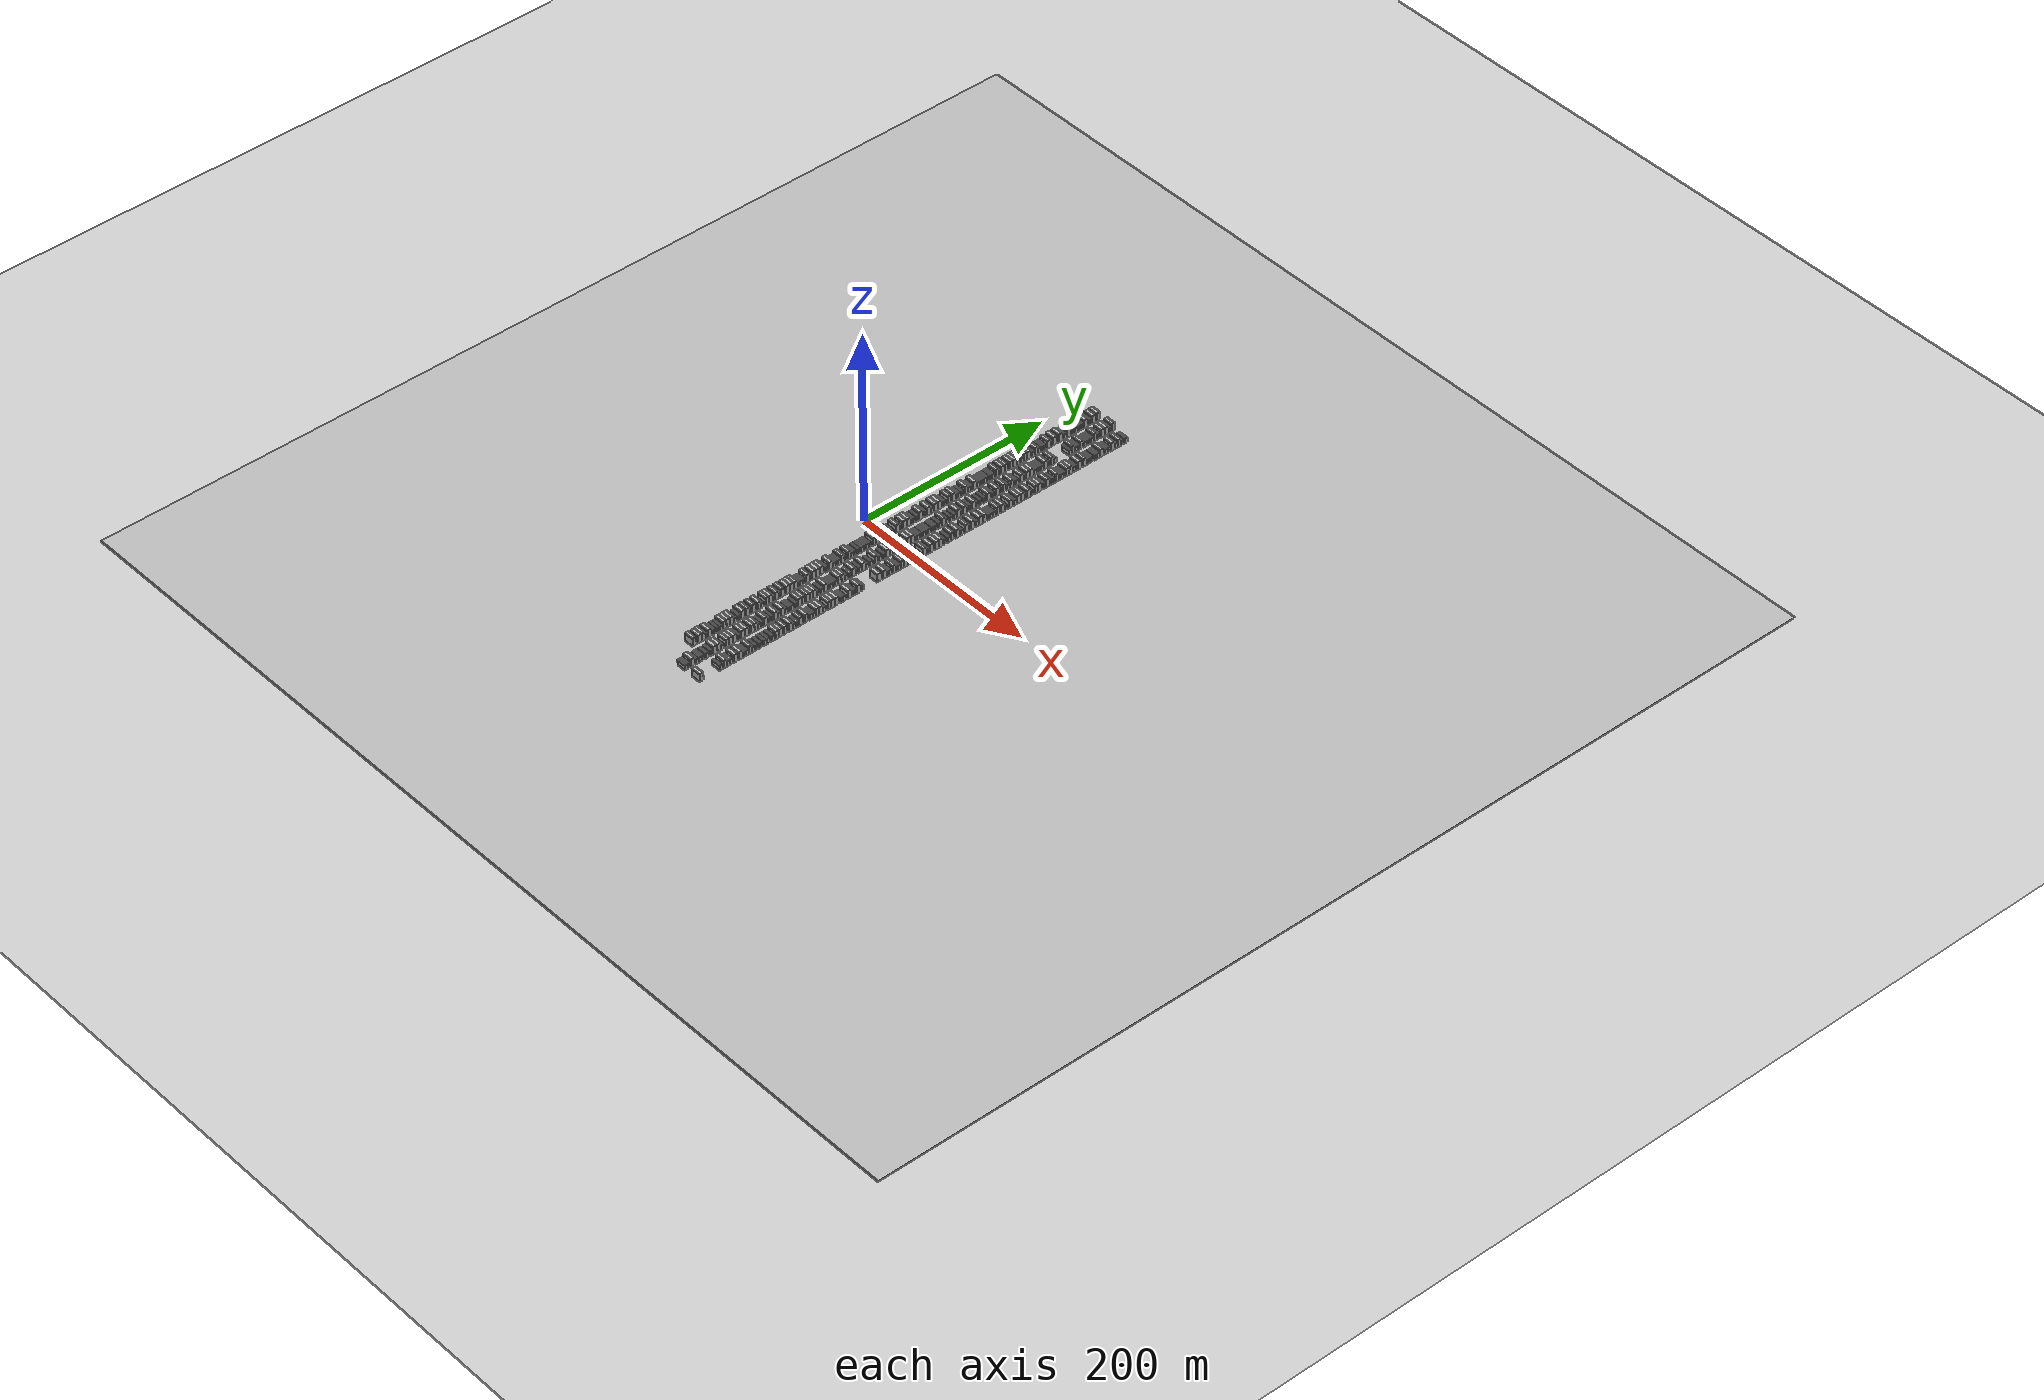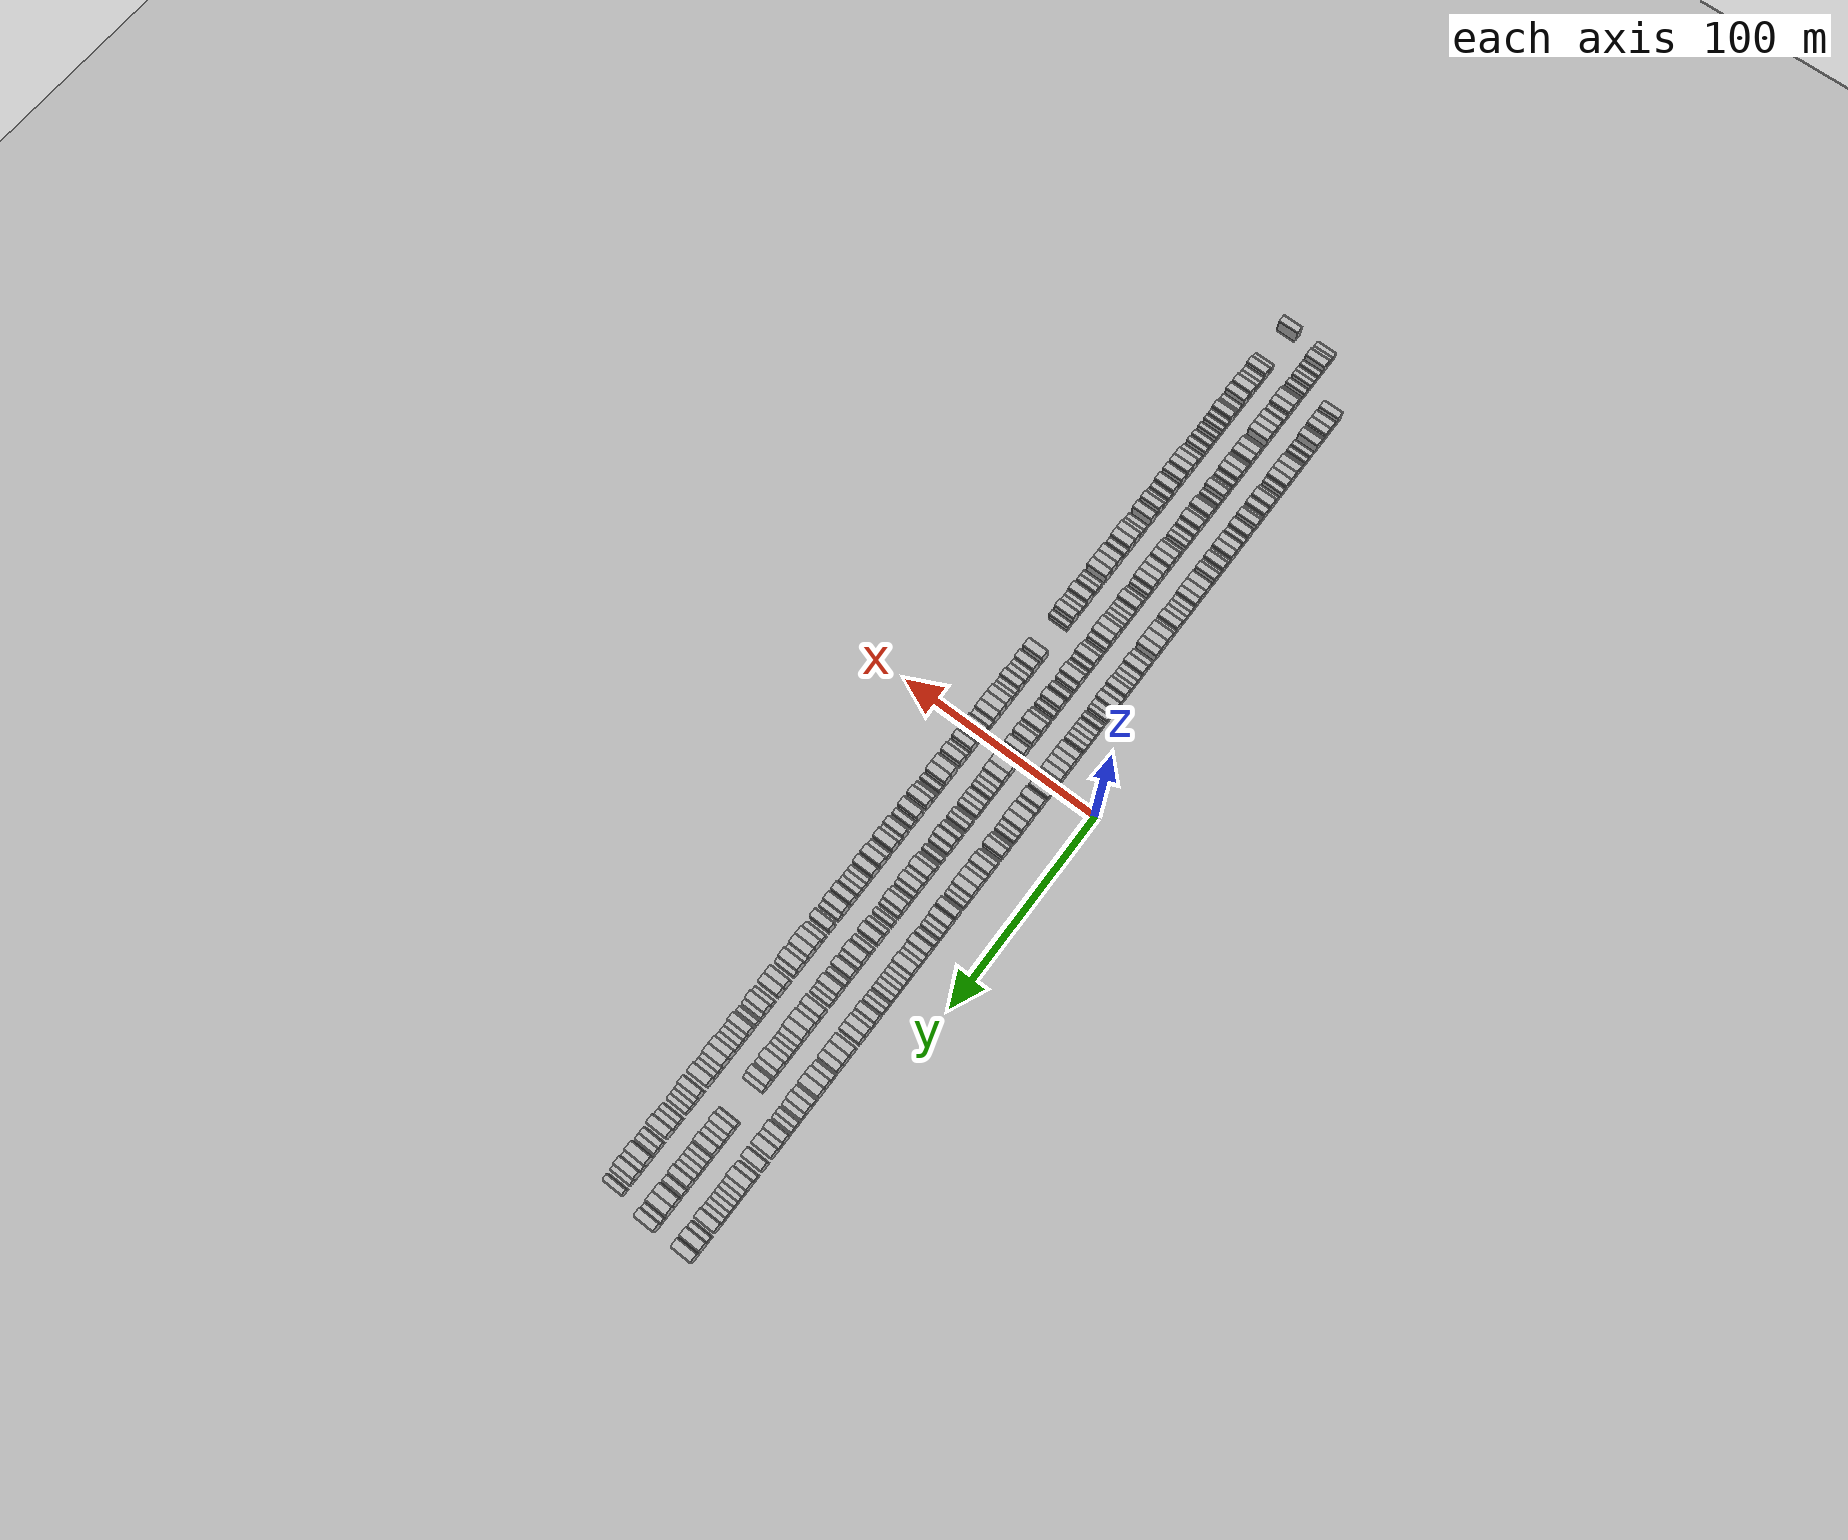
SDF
<?xml version="1.0" encoding="utf-8"?>

<sdf version="1.6">

   <world name="default">

      <gui fullscreen="0">

         <camera name="user_camera">

            <pose>-15 0 4.57585 0 0 0</pose>

            <view_controller>orbit</view_controller>

         </camera>

      </gui>

      <scene>

         <sky>

           <clouds>

             <speed>12</speed>

           </clouds>

         </sky>

         <ambient>0.4 0.4 0.4 1</ambient>

         <background>0.7 0.7 0.7 1</background>

         <shadows>1</shadows>

      </scene>

      <gravity>0 0 -9.8066</gravity>

      <magnetic_field>6e-06 2.3e-05 -4.2e-05</magnetic_field>

      <physics default="0" name="default_physics" type="ode">

         <ode>

            <solver>

               <type>quick</type>

               <iters>10</iters>

               <sor>1.0</sor>

               <use_dynamic_moi_rescaling>0</use_dynamic_moi_rescaling>

            </solver>

            <constraints>

               <cfm>0</cfm>

               <erp>0.2</erp>

               <contact_max_correcting_vel>100</contact_max_correcting_vel>

               <contact_surface_layer>0.001</contact_surface_layer>

            </constraints>

         </ode>

         <max_step_size>0.004</max_step_size>

         <real_time_factor>1</real_time_factor>

         <real_time_update_rate>250</real_time_update_rate>

      </physics>

      <light name="sun" type="directional">

         <cast_shadows>1</cast_shadows>

         <pose>0 0 10 0 0 0</pose>

         <diffuse>0.8 0.8 0.8 1</diffuse>

         <specular>0.2 0.2 0.2 1</specular>

         <attenuation>

            <range>1000</range>

            <constant>0.9</constant>

            <linear>0.01</linear>

            <quadratic>0.001</quadratic>

         </attenuation>

         <direction>-0.5 0.1 -0.9</direction>

      </light>

      <include>

         <name>ground_plane_1</name>

         <uri>model://HANNAS_ground_plane</uri>

         <pose>0 0 0  0 0 0</pose>

      </include>

      <include>

         <name>ground_plane_2</name>

         <uri>model://HANNAS_ground_plane</uri>

         <pose>100 0 0  0 0 0</pose>

      </include>

      <model name="building_1">

         <static>1</static>

         <pose frame="">25.0000 -210.2446 0 0.000000 0.000000 0.000000</pose>

         <link name="link">

            <pose frame="">0 0 4.50 0 0 0</pose>

            <collision name="collision">

               <geometry>

                  <box>

                     <size>10.0000 3.8369 9.0000</size>

                  </box>

               </geometry>

               <max_contacts>10</max_contacts>

               <surface>

                  <contact>

                     <ode/>

                  </contact>

                  <bounce/>

                  <friction>

                     <torsional>

                        <ode/>

                     </torsional>

                     <ode/>

                  </friction>

               </surface>

            </collision>

            <visual name="visual">

               <cast_shadows>0</cast_shadows>

               <geometry>

                  <box>

                     <size>10.0000 3.8369 9.0000</size>

                  </box>

               </geometry>

               <material>

                  <script>

                     <uri>model://HANNAS_wall/materials/scripts</uri>

                     <uri>model://HANNAS_wall/materials/textures</uri>

                     <name>vrc/HANNAS_wall</name>

                  </script>

               </material>

            </visual>

            <self_collide>0</self_collide>

            <enable_wind>0</enable_wind>

            <kinematic>0</kinematic>

         </link>

      </model>

      <model name="building_2">

         <static>1</static>

         <pose frame="">25.0000 -204.4318 0 0.000000 0.000000 0.000000</pose>

         <link name="link">

            <pose frame="">0 0 4.50 0 0 0</pose>

            <collision name="collision">

               <geometry>

                  <box>

                     <size>10.0000 3.7886 9.0000</size>

                  </box>

               </geometry>

               <max_contacts>10</max_contacts>

               <surface>

                  <contact>

                     <ode/>

                  </contact>

                  <bounce/>

                  <friction>

                     <torsional>

                        <ode/>

                     </torsional>

                     <ode/>

                  </friction>

               </surface>

            </collision>

            <visual name="visual">

               <cast_shadows>0</cast_shadows>

               <geometry>

                  <box>

                     <size>10.0000 3.7886 9.0000</size>

                  </box>

               </geometry>

               <material>

                  <script>

                     <uri>model://HANNAS_wall/materials/scripts</uri>

                     <uri>model://HANNAS_wall/materials/textures</uri>

                     <name>vrc/HANNAS_wall</name>

                  </script>

               </material>

            </visual>

            <self_collide>0</self_collide>

            <enable_wind>0</enable_wind>

            <kinematic>0</kinematic>

         </link>

      </model>

      <model name="building_3">

         <static>1</static>

         <pose frame="">25.0000 -200.5915 0 0.000000 0.000000 0.000000</pose>

         <link name="link">

            <pose frame="">0 0 4.50 0 0 0</pose>

            <collision name="collision">

               <geometry>

                  <box>

                     <size>10.0000 3.8921 9.0000</size>

                  </box>

               </geometry>

               <max_contacts>10</max_contacts>

               <surface>

                  <contact>

                     <ode/>

                  </contact>

                  <bounce/>

                  <friction>

                     <torsional>

                        <ode/>

                     </torsional>

                     <ode/>

                  </friction>

               </surface>

            </collision>

            <visual name="visual">

               <cast_shadows>0</cast_shadows>

               <geometry>

                  <box>

                     <size>10.0000 3.8921 9.0000</size>

                  </box>

               </geometry>

               <material>

                  <script>

                     <uri>model://HANNAS_wall/materials/scripts</uri>

                     <uri>model://HANNAS_wall/materials/textures</uri>

                     <name>vrc/HANNAS_wall</name>

                  </script>

               </material>

            </visual>

            <self_collide>0</self_collide>

            <enable_wind>0</enable_wind>

            <kinematic>0</kinematic>

         </link>

      </model>

      <model name="building_4">

         <static>1</static>

         <pose frame="">25.0000 -197.4109 0 0.000000 0.000000 0.000000</pose>

         <link name="link">

            <pose frame="">0 0 3.00 0 0 0</pose>

            <collision name="collision">

               <geometry>

                  <box>

                     <size>10.0000 2.4689 6.0000</size>

                  </box>

               </geometry>

               <max_contacts>10</max_contacts>

               <surface>

                  <contact>

                     <ode/>

                  </contact>

                  <bounce/>

                  <friction>

                     <torsional>

                        <ode/>

                     </torsional>

                     <ode/>

                  </friction>

               </surface>

            </collision>

            <visual name="visual">

               <cast_shadows>0</cast_shadows>

               <geometry>

                  <box>

                     <size>10.0000 2.4689 6.0000</size>

                  </box>

               </geometry>

               <material>

                  <script>

                     <uri>model://HANNAS_wall/materials/scripts</uri>

                     <uri>model://HANNAS_wall/materials/textures</uri>

                     <name>vrc/HANNAS_wall</name>

                  </script>

               </material>

            </visual>

            <self_collide>0</self_collide>

            <enable_wind>0</enable_wind>

            <kinematic>0</kinematic>

         </link>

      </model>

      <model name="building_5">

         <static>1</static>

         <pose frame="">25.0000 -194.1410 0 0.000000 0.000000 0.000000</pose>

         <link name="link">

            <pose frame="">0 0 4.50 0 0 0</pose>

            <collision name="collision">

               <geometry>

                  <box>

                     <size>10.0000 4.0709 9.0000</size>

                  </box>

               </geometry>

               <max_contacts>10</max_contacts>

               <surface>

                  <contact>

                     <ode/>

                  </contact>

                  <bounce/>

                  <friction>

                     <torsional>

                        <ode/>

                     </torsional>

                     <ode/>

                  </friction>

               </surface>

            </collision>

            <visual name="visual">

               <cast_shadows>0</cast_shadows>

               <geometry>

                  <box>

                     <size>10.0000 4.0709 9.0000</size>

                  </box>

               </geometry>

               <material>

                  <script>

                     <uri>model://HANNAS_wall/materials/scripts</uri>

                     <uri>model://HANNAS_wall/materials/textures</uri>

                     <name>vrc/HANNAS_wall</name>

                  </script>

               </material>

            </visual>

            <self_collide>0</self_collide>

            <enable_wind>0</enable_wind>

            <kinematic>0</kinematic>

         </link>

      </model>

      <model name="building_6">

         <static>1</static>

         <pose frame="">25.0000 -188.7072 0 0.000000 0.000000 0.000000</pose>

         <link name="link">

            <pose frame="">0 0 3.00 0 0 0</pose>

            <collision name="collision">

               <geometry>

                  <box>

                     <size>10.0000 2.7967 6.0000</size>

                  </box>

               </geometry>

               <max_contacts>10</max_contacts>

               <surface>

                  <contact>

                     <ode/>

                  </contact>

                  <bounce/>

                  <friction>

                     <torsional>

                        <ode/>

                     </torsional>

                     <ode/>

                  </friction>

               </surface>

            </collision>

            <visual name="visual">

               <cast_shadows>0</cast_shadows>

               <geometry>

                  <box>

                     <size>10.0000 2.7967 6.0000</size>

                  </box>

               </geometry>

               <material>

                  <script>

                     <uri>model://HANNAS_wall/materials/scripts</uri>

                     <uri>model://HANNAS_wall/materials/textures</uri>

                     <name>vrc/HANNAS_wall</name>

                  </script>

               </material>

            </visual>

            <self_collide>0</self_collide>

            <enable_wind>0</enable_wind>

            <kinematic>0</kinematic>

         </link>

      </model>

      <model name="building_7">

         <static>1</static>

         <pose frame="">25.0000 -185.0412 0 0.000000 0.000000 0.000000</pose>

         <link name="link">

            <pose frame="">0 0 3.00 0 0 0</pose>

            <collision name="collision">

               <geometry>

                  <box>

                     <size>10.0000 2.5354 6.0000</size>

                  </box>

               </geometry>

               <max_contacts>10</max_contacts>

               <surface>

                  <contact>

                     <ode/>

                  </contact>

                  <bounce/>

                  <friction>

                     <torsional>

                        <ode/>

                     </torsional>

                     <ode/>

                  </friction>

               </surface>

            </collision>

            <visual name="visual">

               <cast_shadows>0</cast_shadows>

               <geometry>

                  <box>

                     <size>10.0000 2.5354 6.0000</size>

                  </box>

               </geometry>

               <material>

                  <script>

                     <uri>model://HANNAS_wall/materials/scripts</uri>

                     <uri>model://HANNAS_wall/materials/textures</uri>

                     <name>vrc/HANNAS_wall</name>

                  </script>

               </material>

            </visual>

            <self_collide>0</self_collide>

            <enable_wind>0</enable_wind>

            <kinematic>0</kinematic>

         </link>

      </model>

      <model name="building_8">

         <static>1</static>

         <pose frame="">25.0000 -181.5201 0 0.000000 0.000000 0.000000</pose>

         <link name="link">

            <pose frame="">0 0 3.00 0 0 0</pose>

            <collision name="collision">

               <geometry>

                  <box>

                     <size>10.0000 2.5069 6.0000</size>

                  </box>

               </geometry>

               <max_contacts>10</max_contacts>

               <surface>

                  <contact>

                     <ode/>

                  </contact>

                  <bounce/>

                  <friction>

                     <torsional>

                        <ode/>

                     </torsional>

                     <ode/>

                  </friction>

               </surface>

            </collision>

            <visual name="visual">

               <cast_shadows>0</cast_shadows>

               <geometry>

                  <box>

                     <size>10.0000 2.5069 6.0000</size>

                  </box>

               </geometry>

               <material>

                  <script>

                     <uri>model://HANNAS_wall/materials/scripts</uri>

                     <uri>model://HANNAS_wall/materials/textures</uri>

                     <name>vrc/HANNAS_wall</name>

                  </script>

               </material>

            </visual>

            <self_collide>0</self_collide>

            <enable_wind>0</enable_wind>

            <kinematic>0</kinematic>

         </link>

      </model>

      <model name="building_9">

         <static>1</static>

         <pose frame="">25.0000 -178.2277 0 0.000000 0.000000 0.000000</pose>

         <link name="link">

            <pose frame="">0 0 4.50 0 0 0</pose>

            <collision name="collision">

               <geometry>

                  <box>

                     <size>10.0000 4.0778 9.0000</size>

                  </box>

               </geometry>

               <max_contacts>10</max_contacts>

               <surface>

                  <contact>

                     <ode/>

                  </contact>

                  <bounce/>

                  <friction>

                     <torsional>

                        <ode/>

                     </torsional>

                     <ode/>

                  </friction>

               </surface>

            </collision>

            <visual name="visual">

               <cast_shadows>0</cast_shadows>

               <geometry>

                  <box>

                     <size>10.0000 4.0778 9.0000</size>

                  </box>

               </geometry>

               <material>

                  <script>

                     <uri>model://HANNAS_wall/materials/scripts</uri>

                     <uri>model://HANNAS_wall/materials/textures</uri>

                     <name>vrc/HANNAS_wall</name>

                  </script>

               </material>

            </visual>

            <self_collide>0</self_collide>

            <enable_wind>0</enable_wind>

            <kinematic>0</kinematic>

         </link>

      </model>

      <model name="building_10">

         <static>1</static>

         <pose frame="">25.0000 -174.1491 0 0.000000 0.000000 0.000000</pose>

         <link name="link">

            <pose frame="">0 0 4.50 0 0 0</pose>

            <collision name="collision">

               <geometry>

                  <box>

                     <size>10.0000 4.0794 9.0000</size>

                  </box>

               </geometry>

               <max_contacts>10</max_contacts>

               <surface>

                  <contact>

                     <ode/>

                  </contact>

                  <bounce/>

                  <friction>

                     <torsional>

                        <ode/>

                     </torsional>

                     <ode/>

                  </friction>

               </surface>

            </collision>

            <visual name="visual">

               <cast_shadows>0</cast_shadows>

               <geometry>

                  <box>

                     <size>10.0000 4.0794 9.0000</size>

                  </box>

               </geometry>

               <material>

                  <script>

                     <uri>model://HANNAS_wall/materials/scripts</uri>

                     <uri>model://HANNAS_wall/materials/textures</uri>

                     <name>vrc/HANNAS_wall</name>

                  </script>

               </material>

            </visual>

            <self_collide>0</self_collide>

            <enable_wind>0</enable_wind>

            <kinematic>0</kinematic>

         </link>

      </model>

      <model name="building_11">

         <static>1</static>

         <pose frame="">25.0000 -170.0534 0 0.000000 0.000000 0.000000</pose>

         <link name="link">

            <pose frame="">0 0 4.50 0 0 0</pose>

            <collision name="collision">

               <geometry>

                  <box>

                     <size>10.0000 4.1120 9.0000</size>

                  </box>

               </geometry>

               <max_contacts>10</max_contacts>

               <surface>

                  <contact>

                     <ode/>

                  </contact>

                  <bounce/>

                  <friction>

                     <torsional>

                        <ode/>

                     </torsional>

                     <ode/>

                  </friction>

               </surface>

            </collision>

            <visual name="visual">

               <cast_shadows>0</cast_shadows>

               <geometry>

                  <box>

                     <size>10.0000 4.1120 9.0000</size>

                  </box>

               </geometry>

               <material>

                  <script>

                     <uri>model://HANNAS_wall/materials/scripts</uri>

                     <uri>model://HANNAS_wall/materials/textures</uri>

                     <name>vrc/HANNAS_wall</name>

                  </script>

               </material>

            </visual>

            <self_collide>0</self_collide>

            <enable_wind>0</enable_wind>

            <kinematic>0</kinematic>

         </link>

      </model>

      <model name="building_12">

         <static>1</static>

         <pose frame="">25.0000 -166.6129 0 0.000000 0.000000 0.000000</pose>

         <link name="link">

            <pose frame="">0 0 3.00 0 0 0</pose>

            <collision name="collision">

               <geometry>

                  <box>

                     <size>10.0000 2.7691 6.0000</size>

                  </box>

               </geometry>

               <max_contacts>10</max_contacts>

               <surface>

                  <contact>

                     <ode/>

                  </contact>

                  <bounce/>

                  <friction>

                     <torsional>

                        <ode/>

                     </torsional>

                     <ode/>

                  </friction>

               </surface>

            </collision>

            <visual name="visual">

               <cast_shadows>0</cast_shadows>

               <geometry>

                  <box>

                     <size>10.0000 2.7691 6.0000</size>

                  </box>

               </geometry>

               <material>

                  <script>

                     <uri>model://HANNAS_wall/materials/scripts</uri>

                     <uri>model://HANNAS_wall/materials/textures</uri>

                     <name>vrc/HANNAS_wall</name>

                  </script>

               </material>

            </visual>

            <self_collide>0</self_collide>

            <enable_wind>0</enable_wind>

            <kinematic>0</kinematic>

         </link>

      </model>

      <model name="building_13">

         <static>1</static>

         <pose frame="">25.0000 -161.7712 0 0.000000 0.000000 0.000000</pose>

         <link name="link">

            <pose frame="">0 0 3.00 0 0 0</pose>

            <collision name="collision">

               <geometry>

                  <box>

                     <size>10.0000 2.9143 6.0000</size>

                  </box>

               </geometry>

               <max_contacts>10</max_contacts>

               <surface>

                  <contact>

                     <ode/>

                  </contact>

                  <bounce/>

                  <friction>

                     <torsional>

                        <ode/>

                     </torsional>

                     <ode/>

                  </friction>

               </surface>

            </collision>

            <visual name="visual">

               <cast_shadows>0</cast_shadows>

               <geometry>

                  <box>

                     <size>10.0000 2.9143 6.0000</size>

                  </box>

               </geometry>

               <material>

                  <script>

                     <uri>model://HANNAS_wall/materials/scripts</uri>

                     <uri>model://HANNAS_wall/materials/textures</uri>

                     <name>vrc/HANNAS_wall</name>

                  </script>

               </material>

            </visual>

            <self_collide>0</self_collide>

            <enable_wind>0</enable_wind>

            <kinematic>0</kinematic>

         </link>

      </model>

      <model name="building_14">

         <static>1</static>

         <pose frame="">25.0000 -158.1254 0 0.000000 0.000000 0.000000</pose>

         <link name="link">

            <pose frame="">0 0 4.50 0 0 0</pose>

            <collision name="collision">

               <geometry>

                  <box>

                     <size>10.0000 4.3773 9.0000</size>

                  </box>

               </geometry>

               <max_contacts>10</max_contacts>

               <surface>

                  <contact>

                     <ode/>

                  </contact>

                  <bounce/>

                  <friction>

                     <torsional>

                        <ode/>

                     </torsional>

                     <ode/>

                  </friction>

               </surface>

            </collision>

            <visual name="visual">

               <cast_shadows>0</cast_shadows>

               <geometry>

                  <box>

                     <size>10.0000 4.3773 9.0000</size>

                  </box>

               </geometry>

               <material>

                  <script>

                     <uri>model://HANNAS_wall/materials/scripts</uri>

                     <uri>model://HANNAS_wall/materials/textures</uri>

                     <name>vrc/HANNAS_wall</name>

                  </script>

               </material>

            </visual>

            <self_collide>0</self_collide>

            <enable_wind>0</enable_wind>

            <kinematic>0</kinematic>

         </link>

      </model>

      <model name="building_15">

         <static>1</static>

         <pose frame="">25.0000 -153.1305 0 0.000000 0.000000 0.000000</pose>

         <link name="link">

            <pose frame="">0 0 4.50 0 0 0</pose>

            <collision name="collision">

               <geometry>

                  <box>

                     <size>10.0000 3.6125 9.0000</size>

                  </box>

               </geometry>

               <max_contacts>10</max_contacts>

               <surface>

                  <contact>

                     <ode/>

                  </contact>

                  <bounce/>

                  <friction>

                     <torsional>

                        <ode/>

                     </torsional>

                     <ode/>

                  </friction>

               </surface>

            </collision>

            <visual name="visual">

               <cast_shadows>0</cast_shadows>

               <geometry>

                  <box>

                     <size>10.0000 3.6125 9.0000</size>

                  </box>

               </geometry>

               <material>

                  <script>

                     <uri>model://HANNAS_wall/materials/scripts</uri>

                     <uri>model://HANNAS_wall/materials/textures</uri>

                     <name>vrc/HANNAS_wall</name>

                  </script>

               </material>

            </visual>

            <self_collide>0</self_collide>

            <enable_wind>0</enable_wind>

            <kinematic>0</kinematic>

         </link>

      </model>

      <model name="building_16">

         <static>1</static>

         <pose frame="">25.0000 -149.9911 0 0.000000 0.000000 0.000000</pose>

         <link name="link">

            <pose frame="">0 0 3.00 0 0 0</pose>

            <collision name="collision">

               <geometry>

                  <box>

                     <size>10.0000 2.6663 6.0000</size>

                  </box>

               </geometry>

               <max_contacts>10</max_contacts>

               <surface>

                  <contact>

                     <ode/>

                  </contact>

                  <bounce/>

                  <friction>

                     <torsional>

                        <ode/>

                     </torsional>

                     <ode/>

                  </friction>

               </surface>

            </collision>

            <visual name="visual">

               <cast_shadows>0</cast_shadows>

               <geometry>

                  <box>

                     <size>10.0000 2.6663 6.0000</size>

                  </box>

               </geometry>

               <material>

                  <script>

                     <uri>model://HANNAS_wall/materials/scripts</uri>

                     <uri>model://HANNAS_wall/materials/textures</uri>

                     <name>vrc/HANNAS_wall</name>

                  </script>

               </material>

            </visual>

            <self_collide>0</self_collide>

            <enable_wind>0</enable_wind>

            <kinematic>0</kinematic>

         </link>

      </model>

      <model name="building_17">

         <static>1</static>

         <pose frame="">25.0000 -146.7138 0 0.000000 0.000000 0.000000</pose>

         <link name="link">

            <pose frame="">0 0 4.50 0 0 0</pose>

            <collision name="collision">

               <geometry>

                  <box>

                     <size>10.0000 3.8884 9.0000</size>

                  </box>

               </geometry>

               <max_contacts>10</max_contacts>

               <surface>

                  <contact>

                     <ode/>

                  </contact>

                  <bounce/>

                  <friction>

                     <torsional>

                        <ode/>

                     </torsional>

                     <ode/>

                  </friction>

               </surface>

            </collision>

            <visual name="visual">

               <cast_shadows>0</cast_shadows>

               <geometry>

                  <box>

                     <size>10.0000 3.8884 9.0000</size>

                  </box>

               </geometry>

               <material>

                  <script>

                     <uri>model://HANNAS_wall/materials/scripts</uri>

                     <uri>model://HANNAS_wall/materials/textures</uri>

                     <name>vrc/HANNAS_wall</name>

                  </script>

               </material>

            </visual>

            <self_collide>0</self_collide>

            <enable_wind>0</enable_wind>

            <kinematic>0</kinematic>

         </link>

      </model>

      <model name="building_18">

         <static>1</static>

         <pose frame="">25.0000 -140.6775 0 0.000000 0.000000 0.000000</pose>

         <link name="link">

            <pose frame="">0 0 4.50 0 0 0</pose>

            <collision name="collision">

               <geometry>

                  <box>

                     <size>10.0000 4.1843 9.0000</size>

                  </box>

               </geometry>

               <max_contacts>10</max_contacts>

               <surface>

                  <contact>

                     <ode/>

                  </contact>

                  <bounce/>

                  <friction>

                     <torsional>

                        <ode/>

                     </torsional>

                     <ode/>

                  </friction>

               </surface>

            </collision>

            <visual name="visual">

               <cast_shadows>0</cast_shadows>

               <geometry>

                  <box>

                     <size>10.0000 4.1843 9.0000</size>

                  </box>

               </geometry>

               <material>

                  <script>

                     <uri>model://HANNAS_wall/materials/scripts</uri>

                     <uri>model://HANNAS_wall/materials/textures</uri>

                     <name>vrc/HANNAS_wall</name>

                  </script>

               </material>

            </visual>

            <self_collide>0</self_collide>

            <enable_wind>0</enable_wind>

            <kinematic>0</kinematic>

         </link>

      </model>

      <model name="building_19">

         <static>1</static>

         <pose frame="">25.0000 -137.3348 0 0.000000 0.000000 0.000000</pose>

         <link name="link">

            <pose frame="">0 0 3.00 0 0 0</pose>

            <collision name="collision">

               <geometry>

                  <box>

                     <size>10.0000 2.5011 6.0000</size>

                  </box>

               </geometry>

               <max_contacts>10</max_contacts>

               <surface>

                  <contact>

                     <ode/>

                  </contact>

                  <bounce/>

                  <friction>

                     <torsional>

                        <ode/>

                     </torsional>

                     <ode/>

                  </friction>

               </surface>

            </collision>

            <visual name="visual">

               <cast_shadows>0</cast_shadows>

               <geometry>

                  <box>

                     <size>10.0000 2.5011 6.0000</size>

                  </box>

               </geometry>

               <material>

                  <script>

                     <uri>model://HANNAS_wall/materials/scripts</uri>

                     <uri>model://HANNAS_wall/materials/textures</uri>

                     <name>vrc/HANNAS_wall</name>

                  </script>

               </material>

            </visual>

            <self_collide>0</self_collide>

            <enable_wind>0</enable_wind>

            <kinematic>0</kinematic>

         </link>

      </model>

      <model name="building_20">

         <static>1</static>

         <pose frame="">25.0000 -132.1780 0 0.000000 0.000000 0.000000</pose>

         <link name="link">

            <pose frame="">0 0 4.50 0 0 0</pose>

            <collision name="collision">

               <geometry>

                  <box>

                     <size>10.0000 3.8125 9.0000</size>

                  </box>

               </geometry>

               <max_contacts>10</max_contacts>

               <surface>

                  <contact>

                     <ode/>

                  </contact>

                  <bounce/>

                  <friction>

                     <torsional>

                        <ode/>

                     </torsional>

                     <ode/>

                  </friction>

               </surface>

            </collision>

            <visual name="visual">

               <cast_shadows>0</cast_shadows>

               <geometry>

                  <box>

                     <size>10.0000 3.8125 9.0000</size>

                  </box>

               </geometry>

               <material>

                  <script>

                     <uri>model://HANNAS_wall/materials/scripts</uri>

                     <uri>model://HANNAS_wall/materials/textures</uri>

                     <name>vrc/HANNAS_wall</name>

                  </script>

               </material>

            </visual>

            <self_collide>0</self_collide>

            <enable_wind>0</enable_wind>

            <kinematic>0</kinematic>

         </link>

      </model>

      <model name="building_21">

         <static>1</static>

         <pose frame="">25.0000 -128.2449 0 0.000000 0.000000 0.000000</pose>

         <link name="link">

            <pose frame="">0 0 4.50 0 0 0</pose>

            <collision name="collision">

               <geometry>

                  <box>

                     <size>10.0000 4.0535 9.0000</size>

                  </box>

               </geometry>

               <max_contacts>10</max_contacts>

               <surface>

                  <contact>

                     <ode/>

                  </contact>

                  <bounce/>

                  <friction>

                     <torsional>

                        <ode/>

                     </torsional>

                     <ode/>

                  </friction>

               </surface>

            </collision>

            <visual name="visual">

               <cast_shadows>0</cast_shadows>

               <geometry>

                  <box>

                     <size>10.0000 4.0535 9.0000</size>

                  </box>

               </geometry>

               <material>

                  <script>

                     <uri>model://HANNAS_wall/materials/scripts</uri>

                     <uri>model://HANNAS_wall/materials/textures</uri>

                     <name>vrc/HANNAS_wall</name>

                  </script>

               </material>

            </visual>

            <self_collide>0</self_collide>

            <enable_wind>0</enable_wind>

            <kinematic>0</kinematic>

         </link>

      </model>

      <model name="building_22">

         <static>1</static>

         <pose frame="">25.0000 -124.8928 0 0.000000 0.000000 0.000000</pose>

         <link name="link">

            <pose frame="">0 0 3.00 0 0 0</pose>

            <collision name="collision">

               <geometry>

                  <box>

                     <size>10.0000 2.6507 6.0000</size>

                  </box>

               </geometry>

               <max_contacts>10</max_contacts>

               <surface>

                  <contact>

                     <ode/>

                  </contact>

                  <bounce/>

                  <friction>

                     <torsional>

                        <ode/>

                     </torsional>

                     <ode/>

                  </friction>

               </surface>

            </collision>

            <visual name="visual">

               <cast_shadows>0</cast_shadows>

               <geometry>

                  <box>

                     <size>10.0000 2.6507 6.0000</size>

                  </box>

               </geometry>

               <material>

                  <script>

                     <uri>model://HANNAS_wall/materials/scripts</uri>

                     <uri>model://HANNAS_wall/materials/textures</uri>

                     <name>vrc/HANNAS_wall</name>

                  </script>

               </material>

            </visual>

            <self_collide>0</self_collide>

            <enable_wind>0</enable_wind>

            <kinematic>0</kinematic>

         </link>

      </model>

      <model name="building_23">

         <static>1</static>

         <pose frame="">25.0000 -121.7059 0 0.000000 0.000000 0.000000</pose>

         <link name="link">

            <pose frame="">0 0 4.50 0 0 0</pose>

            <collision name="collision">

               <geometry>

                  <box>

                     <size>10.0000 3.7232 9.0000</size>

                  </box>

               </geometry>

               <max_contacts>10</max_contacts>

               <surface>

                  <contact>

                     <ode/>

                  </contact>

                  <bounce/>

                  <friction>

                     <torsional>

                        <ode/>

                     </torsional>

                     <ode/>

                  </friction>

               </surface>

            </collision>

            <visual name="visual">

               <cast_shadows>0</cast_shadows>

               <geometry>

                  <box>

                     <size>10.0000 3.7232 9.0000</size>

                  </box>

               </geometry>

               <material>

                  <script>

                     <uri>model://HANNAS_wall/materials/scripts</uri>

                     <uri>model://HANNAS_wall/materials/textures</uri>

                     <name>vrc/HANNAS_wall</name>

                  </script>

               </material>

            </visual>

            <self_collide>0</self_collide>

            <enable_wind>0</enable_wind>

            <kinematic>0</kinematic>

         </link>

      </model>

      <model name="building_24">

         <static>1</static>

         <pose frame="">25.0000 -118.4981 0 0.000000 0.000000 0.000000</pose>

         <link name="link">

            <pose frame="">0 0 3.00 0 0 0</pose>

            <collision name="collision">

               <geometry>

                  <box>

                     <size>10.0000 2.6922 6.0000</size>

                  </box>

               </geometry>

               <max_contacts>10</max_contacts>

               <surface>

                  <contact>

                     <ode/>

                  </contact>

                  <bounce/>

                  <friction>

                     <torsional>

                        <ode/>

                     </torsional>

                     <ode/>

                  </friction>

               </surface>

            </collision>

            <visual name="visual">

               <cast_shadows>0</cast_shadows>

               <geometry>

                  <box>

                     <size>10.0000 2.6922 6.0000</size>

                  </box>

               </geometry>

               <material>

                  <script>

                     <uri>model://HANNAS_wall/materials/scripts</uri>

                     <uri>model://HANNAS_wall/materials/textures</uri>

                     <name>vrc/HANNAS_wall</name>

                  </script>

               </material>

            </visual>

            <self_collide>0</self_collide>

            <enable_wind>0</enable_wind>

            <kinematic>0</kinematic>

         </link>

      </model>

      <model name="building_25">

         <static>1</static>

         <pose frame="">25.0000 -115.3469 0 0.000000 0.000000 0.000000</pose>

         <link name="link">

            <pose frame="">0 0 4.50 0 0 0</pose>

            <collision name="collision">

               <geometry>

                  <box>

                     <size>10.0000 3.6103 9.0000</size>

                  </box>

               </geometry>

               <max_contacts>10</max_contacts>

               <surface>

                  <contact>

                     <ode/>

                  </contact>

                  <bounce/>

                  <friction>

                     <torsional>

                        <ode/>

                     </torsional>

                     <ode/>

                  </friction>

               </surface>

            </collision>

            <visual name="visual">

               <cast_shadows>0</cast_shadows>

               <geometry>

                  <box>

                     <size>10.0000 3.6103 9.0000</size>

                  </box>

               </geometry>

               <material>

                  <script>

                     <uri>model://HANNAS_wall/materials/scripts</uri>

                     <uri>model://HANNAS_wall/materials/textures</uri>

                     <name>vrc/HANNAS_wall</name>

                  </script>

               </material>

            </visual>

            <self_collide>0</self_collide>

            <enable_wind>0</enable_wind>

            <kinematic>0</kinematic>

         </link>

      </model>

      <model name="building_26">

         <static>1</static>

         <pose frame="">25.0000 -109.3622 0 0.000000 0.000000 0.000000</pose>

         <link name="link">

            <pose frame="">0 0 4.50 0 0 0</pose>

            <collision name="collision">

               <geometry>

                  <box>

                     <size>10.0000 4.3591 9.0000</size>

                  </box>

               </geometry>

               <max_contacts>10</max_contacts>

               <surface>

                  <contact>

                     <ode/>

                  </contact>

                  <bounce/>

                  <friction>

                     <torsional>

                        <ode/>

                     </torsional>

                     <ode/>

                  </friction>

               </surface>

            </collision>

            <visual name="visual">

               <cast_shadows>0</cast_shadows>

               <geometry>

                  <box>

                     <size>10.0000 4.3591 9.0000</size>

                  </box>

               </geometry>

               <material>

                  <script>

                     <uri>model://HANNAS_wall/materials/scripts</uri>

                     <uri>model://HANNAS_wall/materials/textures</uri>

                     <name>vrc/HANNAS_wall</name>

                  </script>

               </material>

            </visual>

            <self_collide>0</self_collide>

            <enable_wind>0</enable_wind>

            <kinematic>0</kinematic>

         </link>

      </model>

      <model name="building_27">

         <static>1</static>

         <pose frame="">25.0000 -105.1069 0 0.000000 0.000000 0.000000</pose>

         <link name="link">

            <pose frame="">0 0 4.50 0 0 0</pose>

            <collision name="collision">

               <geometry>

                  <box>

                     <size>10.0000 4.1515 9.0000</size>

                  </box>

               </geometry>

               <max_contacts>10</max_contacts>

               <surface>

                  <contact>

                     <ode/>

                  </contact>

                  <bounce/>

                  <friction>

                     <torsional>

                        <ode/>

                     </torsional>

                     <ode/>

                  </friction>

               </surface>

            </collision>

            <visual name="visual">

               <cast_shadows>0</cast_shadows>

               <geometry>

                  <box>

                     <size>10.0000 4.1515 9.0000</size>

                  </box>

               </geometry>

               <material>

                  <script>

                     <uri>model://HANNAS_wall/materials/scripts</uri>

                     <uri>model://HANNAS_wall/materials/textures</uri>

                     <name>vrc/HANNAS_wall</name>

                  </script>

               </material>

            </visual>

            <self_collide>0</self_collide>

            <enable_wind>0</enable_wind>

            <kinematic>0</kinematic>

         </link>

      </model>

      <model name="building_28">

         <static>1</static>

         <pose frame="">25.0000 -101.2152 0 0.000000 0.000000 0.000000</pose>

         <link name="link">

            <pose frame="">0 0 4.50 0 0 0</pose>

            <collision name="collision">

               <geometry>

                  <box>

                     <size>10.0000 3.6319 9.0000</size>

                  </box>

               </geometry>

               <max_contacts>10</max_contacts>

               <surface>

                  <contact>

                     <ode/>

                  </contact>

                  <bounce/>

                  <friction>

                     <torsional>

                        <ode/>

                     </torsional>

                     <ode/>

                  </friction>

               </surface>

            </collision>

            <visual name="visual">

               <cast_shadows>0</cast_shadows>

               <geometry>

                  <box>

                     <size>10.0000 3.6319 9.0000</size>

                  </box>

               </geometry>

               <material>

                  <script>

                     <uri>model://HANNAS_wall/materials/scripts</uri>

                     <uri>model://HANNAS_wall/materials/textures</uri>

                     <name>vrc/HANNAS_wall</name>

                  </script>

               </material>

            </visual>

            <self_collide>0</self_collide>

            <enable_wind>0</enable_wind>

            <kinematic>0</kinematic>

         </link>

      </model>

      <model name="building_29">

         <static>1</static>

         <pose frame="">25.0000 -97.9208 0 0.000000 0.000000 0.000000</pose>

         <link name="link">

            <pose frame="">0 0 3.00 0 0 0</pose>

            <collision name="collision">

               <geometry>

                  <box>

                     <size>10.0000 2.9568 6.0000</size>

                  </box>

               </geometry>

               <max_contacts>10</max_contacts>

               <surface>

                  <contact>

                     <ode/>

                  </contact>

                  <bounce/>

                  <friction>

                     <torsional>

                        <ode/>

                     </torsional>

                     <ode/>

                  </friction>

               </surface>

            </collision>

            <visual name="visual">

               <cast_shadows>0</cast_shadows>

               <geometry>

                  <box>

                     <size>10.0000 2.9568 6.0000</size>

                  </box>

               </geometry>

               <material>

                  <script>

                     <uri>model://HANNAS_wall/materials/scripts</uri>

                     <uri>model://HANNAS_wall/materials/textures</uri>

                     <name>vrc/HANNAS_wall</name>

                  </script>

               </material>

            </visual>

            <self_collide>0</self_collide>

            <enable_wind>0</enable_wind>

            <kinematic>0</kinematic>

         </link>

      </model>

      <model name="building_30">

         <static>1</static>

         <pose frame="">25.0000 -95.0823 0 0.000000 0.000000 0.000000</pose>

         <link name="link">

            <pose frame="">0 0 3.00 0 0 0</pose>

            <collision name="collision">

               <geometry>

                  <box>

                     <size>10.0000 2.7202 6.0000</size>

                  </box>

               </geometry>

               <max_contacts>10</max_contacts>

               <surface>

                  <contact>

                     <ode/>

                  </contact>

                  <bounce/>

                  <friction>

                     <torsional>

                        <ode/>

                     </torsional>

                     <ode/>

                  </friction>

               </surface>

            </collision>

            <visual name="visual">

               <cast_shadows>0</cast_shadows>

               <geometry>

                  <box>

                     <size>10.0000 2.7202 6.0000</size>

                  </box>

               </geometry>

               <material>

                  <script>

                     <uri>model://HANNAS_wall/materials/scripts</uri>

                     <uri>model://HANNAS_wall/materials/textures</uri>

                     <name>vrc/HANNAS_wall</name>

                  </script>

               </material>

            </visual>

            <self_collide>0</self_collide>

            <enable_wind>0</enable_wind>

            <kinematic>0</kinematic>

         </link>

      </model>

      <model name="building_31">

         <static>1</static>

         <pose frame="">25.0000 -92.2942 0 0.000000 0.000000 0.000000</pose>

         <link name="link">

            <pose frame="">0 0 3.00 0 0 0</pose>

            <collision name="collision">

               <geometry>

                  <box>

                     <size>10.0000 2.8559 6.0000</size>

                  </box>

               </geometry>

               <max_contacts>10</max_contacts>

               <surface>

                  <contact>

                     <ode/>

                  </contact>

                  <bounce/>

                  <friction>

                     <torsional>

                        <ode/>

                     </torsional>

                     <ode/>

                  </friction>

               </surface>

            </collision>

            <visual name="visual">

               <cast_shadows>0</cast_shadows>

               <geometry>

                  <box>

                     <size>10.0000 2.8559 6.0000</size>

                  </box>

               </geometry>

               <material>

                  <script>

                     <uri>model://HANNAS_wall/materials/scripts</uri>

                     <uri>model://HANNAS_wall/materials/textures</uri>

                     <name>vrc/HANNAS_wall</name>

                  </script>

               </material>

            </visual>

            <self_collide>0</self_collide>

            <enable_wind>0</enable_wind>

            <kinematic>0</kinematic>

         </link>

      </model>

      <model name="building_32">

         <static>1</static>

         <pose frame="">25.0000 -87.8706 0 0.000000 0.000000 0.000000</pose>

         <link name="link">

            <pose frame="">0 0 4.50 0 0 0</pose>

            <collision name="collision">

               <geometry>

                  <box>

                     <size>10.0000 3.9913 9.0000</size>

                  </box>

               </geometry>

               <max_contacts>10</max_contacts>

               <surface>

                  <contact>

                     <ode/>

                  </contact>

                  <bounce/>

                  <friction>

                     <torsional>

                        <ode/>

                     </torsional>

                     <ode/>

                  </friction>

               </surface>

            </collision>

            <visual name="visual">

               <cast_shadows>0</cast_shadows>

               <geometry>

                  <box>

                     <size>10.0000 3.9913 9.0000</size>

                  </box>

               </geometry>

               <material>

                  <script>

                     <uri>model://HANNAS_wall/materials/scripts</uri>

                     <uri>model://HANNAS_wall/materials/textures</uri>

                     <name>vrc/HANNAS_wall</name>

                  </script>

               </material>

            </visual>

            <self_collide>0</self_collide>

            <enable_wind>0</enable_wind>

            <kinematic>0</kinematic>

         </link>

      </model>

      <model name="building_33">

         <static>1</static>

         <pose frame="">25.0000 -84.6173 0 0.000000 0.000000 0.000000</pose>

         <link name="link">

            <pose frame="">0 0 3.00 0 0 0</pose>

            <collision name="collision">

               <geometry>

                  <box>

                     <size>10.0000 2.5153 6.0000</size>

                  </box>

               </geometry>

               <max_contacts>10</max_contacts>

               <surface>

                  <contact>

                     <ode/>

                  </contact>

                  <bounce/>

                  <friction>

                     <torsional>

                        <ode/>

                     </torsional>

                     <ode/>

                  </friction>

               </surface>

            </collision>

            <visual name="visual">

               <cast_shadows>0</cast_shadows>

               <geometry>

                  <box>

                     <size>10.0000 2.5153 6.0000</size>

                  </box>

               </geometry>

               <material>

                  <script>

                     <uri>model://HANNAS_wall/materials/scripts</uri>

                     <uri>model://HANNAS_wall/materials/textures</uri>

                     <name>vrc/HANNAS_wall</name>

                  </script>

               </material>

            </visual>

            <self_collide>0</self_collide>

            <enable_wind>0</enable_wind>

            <kinematic>0</kinematic>

         </link>

      </model>

      <model name="building_34">

         <static>1</static>

         <pose frame="">25.0000 -81.1599 0 0.000000 0.000000 0.000000</pose>

         <link name="link">

            <pose frame="">0 0 4.50 0 0 0</pose>

            <collision name="collision">

               <geometry>

                  <box>

                     <size>10.0000 4.3994 9.0000</size>

                  </box>

               </geometry>

               <max_contacts>10</max_contacts>

               <surface>

                  <contact>

                     <ode/>

                  </contact>

                  <bounce/>

                  <friction>

                     <torsional>

                        <ode/>

                     </torsional>

                     <ode/>

                  </friction>

               </surface>

            </collision>

            <visual name="visual">

               <cast_shadows>0</cast_shadows>

               <geometry>

                  <box>

                     <size>10.0000 4.3994 9.0000</size>

                  </box>

               </geometry>

               <material>

                  <script>

                     <uri>model://HANNAS_wall/materials/scripts</uri>

                     <uri>model://HANNAS_wall/materials/textures</uri>

                     <name>vrc/HANNAS_wall</name>

                  </script>

               </material>

            </visual>

            <self_collide>0</self_collide>

            <enable_wind>0</enable_wind>

            <kinematic>0</kinematic>

         </link>

      </model>

      <model name="building_35">

         <static>1</static>

         <pose frame="">25.0000 -76.7118 0 0.000000 0.000000 0.000000</pose>

         <link name="link">

            <pose frame="">0 0 4.50 0 0 0</pose>

            <collision name="collision">

               <geometry>

                  <box>

                     <size>10.0000 4.4968 9.0000</size>

                  </box>

               </geometry>

               <max_contacts>10</max_contacts>

               <surface>

                  <contact>

                     <ode/>

                  </contact>

                  <bounce/>

                  <friction>

                     <torsional>

                        <ode/>

                     </torsional>

                     <ode/>

                  </friction>

               </surface>

            </collision>

            <visual name="visual">

               <cast_shadows>0</cast_shadows>

               <geometry>

                  <box>

                     <size>10.0000 4.4968 9.0000</size>

                  </box>

               </geometry>

               <material>

                  <script>

                     <uri>model://HANNAS_wall/materials/scripts</uri>

                     <uri>model://HANNAS_wall/materials/textures</uri>

                     <name>vrc/HANNAS_wall</name>

                  </script>

               </material>

            </visual>

            <self_collide>0</self_collide>

            <enable_wind>0</enable_wind>

            <kinematic>0</kinematic>

         </link>

      </model>

      <model name="building_36">

         <static>1</static>

         <pose frame="">25.0000 -72.4537 0 0.000000 0.000000 0.000000</pose>

         <link name="link">

            <pose frame="">0 0 4.50 0 0 0</pose>

            <collision name="collision">

               <geometry>

                  <box>

                     <size>10.0000 4.0195 9.0000</size>

                  </box>

               </geometry>

               <max_contacts>10</max_contacts>

               <surface>

                  <contact>

                     <ode/>

                  </contact>

                  <bounce/>

                  <friction>

                     <torsional>

                        <ode/>

                     </torsional>

                     <ode/>

                  </friction>

               </surface>

            </collision>

            <visual name="visual">

               <cast_shadows>0</cast_shadows>

               <geometry>

                  <box>

                     <size>10.0000 4.0195 9.0000</size>

                  </box>

               </geometry>

               <material>

                  <script>

                     <uri>model://HANNAS_wall/materials/scripts</uri>

                     <uri>model://HANNAS_wall/materials/textures</uri>

                     <name>vrc/HANNAS_wall</name>

                  </script>

               </material>

            </visual>

            <self_collide>0</self_collide>

            <enable_wind>0</enable_wind>

            <kinematic>0</kinematic>

         </link>

      </model>

      <model name="building_37">

         <static>1</static>

         <pose frame="">25.0000 -67.0926 0 0.000000 0.000000 0.000000</pose>

         <link name="link">

            <pose frame="">0 0 3.00 0 0 0</pose>

            <collision name="collision">

               <geometry>

                  <box>

                     <size>10.0000 2.7026 6.0000</size>

                  </box>

               </geometry>

               <max_contacts>10</max_contacts>

               <surface>

                  <contact>

                     <ode/>

                  </contact>

                  <bounce/>

                  <friction>

                     <torsional>

                        <ode/>

                     </torsional>

                     <ode/>

                  </friction>

               </surface>

            </collision>

            <visual name="visual">

               <cast_shadows>0</cast_shadows>

               <geometry>

                  <box>

                     <size>10.0000 2.7026 6.0000</size>

                  </box>

               </geometry>

               <material>

                  <script>

                     <uri>model://HANNAS_wall/materials/scripts</uri>

                     <uri>model://HANNAS_wall/materials/textures</uri>

                     <name>vrc/HANNAS_wall</name>

                  </script>

               </material>

            </visual>

            <self_collide>0</self_collide>

            <enable_wind>0</enable_wind>

            <kinematic>0</kinematic>

         </link>

      </model>

      <model name="building_38">

         <static>1</static>

         <pose frame="">25.0000 -62.6629 0 0.000000 0.000000 0.000000</pose>

         <link name="link">

            <pose frame="">0 0 4.50 0 0 0</pose>

            <collision name="collision">

               <geometry>

                  <box>

                     <size>10.0000 4.1569 9.0000</size>

                  </box>

               </geometry>

               <max_contacts>10</max_contacts>

               <surface>

                  <contact>

                     <ode/>

                  </contact>

                  <bounce/>

                  <friction>

                     <torsional>

                        <ode/>

                     </torsional>

                     <ode/>

                  </friction>

               </surface>

            </collision>

            <visual name="visual">

               <cast_shadows>0</cast_shadows>

               <geometry>

                  <box>

                     <size>10.0000 4.1569 9.0000</size>

                  </box>

               </geometry>

               <material>

                  <script>

                     <uri>model://HANNAS_wall/materials/scripts</uri>

                     <uri>model://HANNAS_wall/materials/textures</uri>

                     <name>vrc/HANNAS_wall</name>

                  </script>

               </material>

            </visual>

            <self_collide>0</self_collide>

            <enable_wind>0</enable_wind>

            <kinematic>0</kinematic>

         </link>

      </model>

      <model name="building_39">

         <static>1</static>

         <pose frame="">25.0000 -59.1202 0 0.000000 0.000000 0.000000</pose>

         <link name="link">

            <pose frame="">0 0 3.00 0 0 0</pose>

            <collision name="collision">

               <geometry>

                  <box>

                     <size>10.0000 2.9286 6.0000</size>

                  </box>

               </geometry>

               <max_contacts>10</max_contacts>

               <surface>

                  <contact>

                     <ode/>

                  </contact>

                  <bounce/>

                  <friction>

                     <torsional>

                        <ode/>

                     </torsional>

                     <ode/>

                  </friction>

               </surface>

            </collision>

            <visual name="visual">

               <cast_shadows>0</cast_shadows>

               <geometry>

                  <box>

                     <size>10.0000 2.9286 6.0000</size>

                  </box>

               </geometry>

               <material>

                  <script>

                     <uri>model://HANNAS_wall/materials/scripts</uri>

                     <uri>model://HANNAS_wall/materials/textures</uri>

                     <name>vrc/HANNAS_wall</name>

                  </script>

               </material>

            </visual>

            <self_collide>0</self_collide>

            <enable_wind>0</enable_wind>

            <kinematic>0</kinematic>

         </link>

      </model>

      <model name="building_40">

         <static>1</static>

         <pose frame="">25.0000 -56.2437 0 0.000000 0.000000 0.000000</pose>

         <link name="link">

            <pose frame="">0 0 3.00 0 0 0</pose>

            <collision name="collision">

               <geometry>

                  <box>

                     <size>10.0000 2.8243 6.0000</size>

                  </box>

               </geometry>

               <max_contacts>10</max_contacts>

               <surface>

                  <contact>

                     <ode/>

                  </contact>

                  <bounce/>

                  <friction>

                     <torsional>

                        <ode/>

                     </torsional>

                     <ode/>

                  </friction>

               </surface>

            </collision>

            <visual name="visual">

               <cast_shadows>0</cast_shadows>

               <geometry>

                  <box>

                     <size>10.0000 2.8243 6.0000</size>

                  </box>

               </geometry>

               <material>

                  <script>

                     <uri>model://HANNAS_wall/materials/scripts</uri>

                     <uri>model://HANNAS_wall/materials/textures</uri>

                     <name>vrc/HANNAS_wall</name>

                  </script>

               </material>

            </visual>

            <self_collide>0</self_collide>

            <enable_wind>0</enable_wind>

            <kinematic>0</kinematic>

         </link>

      </model>

      <model name="building_41">

         <static>1</static>

         <pose frame="">25.0000 -53.3429 0 0.000000 0.000000 0.000000</pose>

         <link name="link">

            <pose frame="">0 0 3.00 0 0 0</pose>

            <collision name="collision">

               <geometry>

                  <box>

                     <size>10.0000 2.9773 6.0000</size>

                  </box>

               </geometry>

               <max_contacts>10</max_contacts>

               <surface>

                  <contact>

                     <ode/>

                  </contact>

                  <bounce/>

                  <friction>

                     <torsional>

                        <ode/>

                     </torsional>

                     <ode/>

                  </friction>

               </surface>

            </collision>

            <visual name="visual">

               <cast_shadows>0</cast_shadows>

               <geometry>

                  <box>

                     <size>10.0000 2.9773 6.0000</size>

                  </box>

               </geometry>

               <material>

                  <script>

                     <uri>model://HANNAS_wall/materials/scripts</uri>

                     <uri>model://HANNAS_wall/materials/textures</uri>

                     <name>vrc/HANNAS_wall</name>

                  </script>

               </material>

            </visual>

            <self_collide>0</self_collide>

            <enable_wind>0</enable_wind>

            <kinematic>0</kinematic>

         </link>

      </model>

      <model name="building_42">

         <static>1</static>

         <pose frame="">25.0000 -50.0095 0 0.000000 0.000000 0.000000</pose>

         <link name="link">

            <pose frame="">0 0 4.50 0 0 0</pose>

            <collision name="collision">

               <geometry>

                  <box>

                     <size>10.0000 3.6895 9.0000</size>

                  </box>

               </geometry>

               <max_contacts>10</max_contacts>

               <surface>

                  <contact>

                     <ode/>

                  </contact>

                  <bounce/>

                  <friction>

                     <torsional>

                        <ode/>

                     </torsional>

                     <ode/>

                  </friction>

               </surface>

            </collision>

            <visual name="visual">

               <cast_shadows>0</cast_shadows>

               <geometry>

                  <box>

                     <size>10.0000 3.6895 9.0000</size>

                  </box>

               </geometry>

               <material>

                  <script>

                     <uri>model://HANNAS_wall/materials/scripts</uri>

                     <uri>model://HANNAS_wall/materials/textures</uri>

                     <name>vrc/HANNAS_wall</name>

                  </script>

               </material>

            </visual>

            <self_collide>0</self_collide>

            <enable_wind>0</enable_wind>

            <kinematic>0</kinematic>

         </link>

      </model>

      <model name="building_43">

         <static>1</static>

         <pose frame="">25.0000 -46.8148 0 0.000000 0.000000 0.000000</pose>

         <link name="link">

            <pose frame="">0 0 3.00 0 0 0</pose>

            <collision name="collision">

               <geometry>

                  <box>

                     <size>10.0000 2.6999 6.0000</size>

                  </box>

               </geometry>

               <max_contacts>10</max_contacts>

               <surface>

                  <contact>

                     <ode/>

                  </contact>

                  <bounce/>

                  <friction>

                     <torsional>

                        <ode/>

                     </torsional>

                     <ode/>

                  </friction>

               </surface>

            </collision>

            <visual name="visual">

               <cast_shadows>0</cast_shadows>

               <geometry>

                  <box>

                     <size>10.0000 2.6999 6.0000</size>

                  </box>

               </geometry>

               <material>

                  <script>

                     <uri>model://HANNAS_wall/materials/scripts</uri>

                     <uri>model://HANNAS_wall/materials/textures</uri>

                     <name>vrc/HANNAS_wall</name>

                  </script>

               </material>

            </visual>

            <self_collide>0</self_collide>

            <enable_wind>0</enable_wind>

            <kinematic>0</kinematic>

         </link>

      </model>

      <model name="building_44">

         <static>1</static>

         <pose frame="">25.0000 -42.5938 0 0.000000 0.000000 0.000000</pose>

         <link name="link">

            <pose frame="">0 0 4.50 0 0 0</pose>

            <collision name="collision">

               <geometry>

                  <box>

                     <size>10.0000 3.7421 9.0000</size>

                  </box>

               </geometry>

               <max_contacts>10</max_contacts>

               <surface>

                  <contact>

                     <ode/>

                  </contact>

                  <bounce/>

                  <friction>

                     <torsional>

                        <ode/>

                     </torsional>

                     <ode/>

                  </friction>

               </surface>

            </collision>

            <visual name="visual">

               <cast_shadows>0</cast_shadows>

               <geometry>

                  <box>

                     <size>10.0000 3.7421 9.0000</size>

                  </box>

               </geometry>

               <material>

                  <script>

                     <uri>model://HANNAS_wall/materials/scripts</uri>

                     <uri>model://HANNAS_wall/materials/textures</uri>

                     <name>vrc/HANNAS_wall</name>

                  </script>

               </material>

            </visual>

            <self_collide>0</self_collide>

            <enable_wind>0</enable_wind>

            <kinematic>0</kinematic>

         </link>

      </model>

      <model name="building_45">

         <static>1</static>

         <pose frame="">25.0000 -39.2395 0 0.000000 0.000000 0.000000</pose>

         <link name="link">

            <pose frame="">0 0 3.00 0 0 0</pose>

            <collision name="collision">

               <geometry>

                  <box>

                     <size>10.0000 2.9665 6.0000</size>

                  </box>

               </geometry>

               <max_contacts>10</max_contacts>

               <surface>

                  <contact>

                     <ode/>

                  </contact>

                  <bounce/>

                  <friction>

                     <torsional>

                        <ode/>

                     </torsional>

                     <ode/>

                  </friction>

               </surface>

            </collision>

            <visual name="visual">

               <cast_shadows>0</cast_shadows>

               <geometry>

                  <box>

                     <size>10.0000 2.9665 6.0000</size>

                  </box>

               </geometry>

               <material>

                  <script>

                     <uri>model://HANNAS_wall/materials/scripts</uri>

                     <uri>model://HANNAS_wall/materials/textures</uri>

                     <name>vrc/HANNAS_wall</name>

                  </script>

               </material>

            </visual>

            <self_collide>0</self_collide>

            <enable_wind>0</enable_wind>

            <kinematic>0</kinematic>

         </link>

      </model>

      <model name="building_46">

         <static>1</static>

         <pose frame="">25.0000 -36.5305 0 0.000000 0.000000 0.000000</pose>

         <link name="link">

            <pose frame="">0 0 3.00 0 0 0</pose>

            <collision name="collision">

               <geometry>

                  <box>

                     <size>10.0000 2.4515 6.0000</size>

                  </box>

               </geometry>

               <max_contacts>10</max_contacts>

               <surface>

                  <contact>

                     <ode/>

                  </contact>

                  <bounce/>

                  <friction>

                     <torsional>

                        <ode/>

                     </torsional>

                     <ode/>

                  </friction>

               </surface>

            </collision>

            <visual name="visual">

               <cast_shadows>0</cast_shadows>

               <geometry>

                  <box>

                     <size>10.0000 2.4515 6.0000</size>

                  </box>

               </geometry>

               <material>

                  <script>

                     <uri>model://HANNAS_wall/materials/scripts</uri>

                     <uri>model://HANNAS_wall/materials/textures</uri>

                     <name>vrc/HANNAS_wall</name>

                  </script>

               </material>

            </visual>

            <self_collide>0</self_collide>

            <enable_wind>0</enable_wind>

            <kinematic>0</kinematic>

         </link>

      </model>

      <model name="building_47">

         <static>1</static>

         <pose frame="">25.0000 -32.0762 0 0.000000 0.000000 0.000000</pose>

         <link name="link">

            <pose frame="">0 0 3.00 0 0 0</pose>

            <collision name="collision">

               <geometry>

                  <box>

                     <size>10.0000 2.4571 6.0000</size>

                  </box>

               </geometry>

               <max_contacts>10</max_contacts>

               <surface>

                  <contact>

                     <ode/>

                  </contact>

                  <bounce/>

                  <friction>

                     <torsional>

                        <ode/>

                     </torsional>

                     <ode/>

                  </friction>

               </surface>

            </collision>

            <visual name="visual">

               <cast_shadows>0</cast_shadows>

               <geometry>

                  <box>

                     <size>10.0000 2.4571 6.0000</size>

                  </box>

               </geometry>

               <material>

                  <script>

                     <uri>model://HANNAS_wall/materials/scripts</uri>

                     <uri>model://HANNAS_wall/materials/textures</uri>

                     <name>vrc/HANNAS_wall</name>

                  </script>

               </material>

            </visual>

            <self_collide>0</self_collide>

            <enable_wind>0</enable_wind>

            <kinematic>0</kinematic>

         </link>

      </model>

      <model name="building_48">

         <static>1</static>

         <pose frame="">25.0000 -28.4923 0 0.000000 0.000000 0.000000</pose>

         <link name="link">

            <pose frame="">0 0 3.00 0 0 0</pose>

            <collision name="collision">

               <geometry>

                  <box>

                     <size>10.0000 2.7107 6.0000</size>

                  </box>

               </geometry>

               <max_contacts>10</max_contacts>

               <surface>

                  <contact>

                     <ode/>

                  </contact>

                  <bounce/>

                  <friction>

                     <torsional>

                        <ode/>

                     </torsional>

                     <ode/>

                  </friction>

               </surface>

            </collision>

            <visual name="visual">

               <cast_shadows>0</cast_shadows>

               <geometry>

                  <box>

                     <size>10.0000 2.7107 6.0000</size>

                  </box>

               </geometry>

               <material>

                  <script>

                     <uri>model://HANNAS_wall/materials/scripts</uri>

                     <uri>model://HANNAS_wall/materials/textures</uri>

                     <name>vrc/HANNAS_wall</name>

                  </script>

               </material>

            </visual>

            <self_collide>0</self_collide>

            <enable_wind>0</enable_wind>

            <kinematic>0</kinematic>

         </link>

      </model>

      <model name="building_49">

         <static>1</static>

         <pose frame="">25.0000 -25.7781 0 0.000000 0.000000 0.000000</pose>

         <link name="link">

            <pose frame="">0 0 3.00 0 0 0</pose>

            <collision name="collision">

               <geometry>

                  <box>

                     <size>10.0000 2.7178 6.0000</size>

                  </box>

               </geometry>

               <max_contacts>10</max_contacts>

               <surface>

                  <contact>

                     <ode/>

                  </contact>

                  <bounce/>

                  <friction>

                     <torsional>

                        <ode/>

                     </torsional>

                     <ode/>

                  </friction>

               </surface>

            </collision>

            <visual name="visual">

               <cast_shadows>0</cast_shadows>

               <geometry>

                  <box>

                     <size>10.0000 2.7178 6.0000</size>

                  </box>

               </geometry>

               <material>

                  <script>

                     <uri>model://HANNAS_wall/materials/scripts</uri>

                     <uri>model://HANNAS_wall/materials/textures</uri>

                     <name>vrc/HANNAS_wall</name>

                  </script>

               </material>

            </visual>

            <self_collide>0</self_collide>

            <enable_wind>0</enable_wind>

            <kinematic>0</kinematic>

         </link>

      </model>

      <model name="building_50">

         <static>1</static>

         <pose frame="">25.0000 -22.9777 0 0.000000 0.000000 0.000000</pose>

         <link name="link">

            <pose frame="">0 0 3.00 0 0 0</pose>

            <collision name="collision">

               <geometry>

                  <box>

                     <size>10.0000 2.8830 6.0000</size>

                  </box>

               </geometry>

               <max_contacts>10</max_contacts>

               <surface>

                  <contact>

                     <ode/>

                  </contact>

                  <bounce/>

                  <friction>

                     <torsional>

                        <ode/>

                     </torsional>

                     <ode/>

                  </friction>

               </surface>

            </collision>

            <visual name="visual">

               <cast_shadows>0</cast_shadows>

               <geometry>

                  <box>

                     <size>10.0000 2.8830 6.0000</size>

                  </box>

               </geometry>

               <material>

                  <script>

                     <uri>model://HANNAS_wall/materials/scripts</uri>

                     <uri>model://HANNAS_wall/materials/textures</uri>

                     <name>vrc/HANNAS_wall</name>

                  </script>

               </material>

            </visual>

            <self_collide>0</self_collide>

            <enable_wind>0</enable_wind>

            <kinematic>0</kinematic>

         </link>

      </model>

      <model name="building_51">

         <static>1</static>

         <pose frame="">25.0000 -20.2062 0 0.000000 0.000000 0.000000</pose>

         <link name="link">

            <pose frame="">0 0 3.00 0 0 0</pose>

            <collision name="collision">

               <geometry>

                  <box>

                     <size>10.0000 2.6601 6.0000</size>

                  </box>

               </geometry>

               <max_contacts>10</max_contacts>

               <surface>

                  <contact>

                     <ode/>

                  </contact>

                  <bounce/>

                  <friction>

                     <torsional>

                        <ode/>

                     </torsional>

                     <ode/>

                  </friction>

               </surface>

            </collision>

            <visual name="visual">

               <cast_shadows>0</cast_shadows>

               <geometry>

                  <box>

                     <size>10.0000 2.6601 6.0000</size>

                  </box>

               </geometry>

               <material>

                  <script>

                     <uri>model://HANNAS_wall/materials/scripts</uri>

                     <uri>model://HANNAS_wall/materials/textures</uri>

                     <name>vrc/HANNAS_wall</name>

                  </script>

               </material>

            </visual>

            <self_collide>0</self_collide>

            <enable_wind>0</enable_wind>

            <kinematic>0</kinematic>

         </link>

      </model>

      <model name="building_52">

         <static>1</static>

         <pose frame="">25.0000 -15.0170 0 0.000000 0.000000 0.000000</pose>

         <link name="link">

            <pose frame="">0 0 4.50 0 0 0</pose>

            <collision name="collision">

               <geometry>

                  <box>

                     <size>10.0000 3.7184 9.0000</size>

                  </box>

               </geometry>

               <max_contacts>10</max_contacts>

               <surface>

                  <contact>

                     <ode/>

                  </contact>

                  <bounce/>

                  <friction>

                     <torsional>

                        <ode/>

                     </torsional>

                     <ode/>

                  </friction>

               </surface>

            </collision>

            <visual name="visual">

               <cast_shadows>0</cast_shadows>

               <geometry>

                  <box>

                     <size>10.0000 3.7184 9.0000</size>

                  </box>

               </geometry>

               <material>

                  <script>

                     <uri>model://HANNAS_wall/materials/scripts</uri>

                     <uri>model://HANNAS_wall/materials/textures</uri>

                     <name>vrc/HANNAS_wall</name>

                  </script>

               </material>

            </visual>

            <self_collide>0</self_collide>

            <enable_wind>0</enable_wind>

            <kinematic>0</kinematic>

         </link>

      </model>

      <model name="building_53">

         <static>1</static>

         <pose frame="">25.0000 -11.3058 0 0.000000 0.000000 0.000000</pose>

         <link name="link">

            <pose frame="">0 0 4.50 0 0 0</pose>

            <collision name="collision">

               <geometry>

                  <box>

                     <size>10.0000 3.7040 9.0000</size>

                  </box>

               </geometry>

               <max_contacts>10</max_contacts>

               <surface>

                  <contact>

                     <ode/>

                  </contact>

                  <bounce/>

                  <friction>

                     <torsional>

                        <ode/>

                     </torsional>

                     <ode/>

                  </friction>

               </surface>

            </collision>

            <visual name="visual">

               <cast_shadows>0</cast_shadows>

               <geometry>

                  <box>

                     <size>10.0000 3.7040 9.0000</size>

                  </box>

               </geometry>

               <material>

                  <script>

                     <uri>model://HANNAS_wall/materials/scripts</uri>

                     <uri>model://HANNAS_wall/materials/textures</uri>

                     <name>vrc/HANNAS_wall</name>

                  </script>

               </material>

            </visual>

            <self_collide>0</self_collide>

            <enable_wind>0</enable_wind>

            <kinematic>0</kinematic>

         </link>

      </model>

      <model name="building_54">

         <static>1</static>

         <pose frame="">25.0000 -7.6224 0 0.000000 0.000000 0.000000</pose>

         <link name="link">

            <pose frame="">0 0 4.50 0 0 0</pose>

            <collision name="collision">

               <geometry>

                  <box>

                     <size>10.0000 3.6626 9.0000</size>

                  </box>

               </geometry>

               <max_contacts>10</max_contacts>

               <surface>

                  <contact>

                     <ode/>

                  </contact>

                  <bounce/>

                  <friction>

                     <torsional>

                        <ode/>

                     </torsional>

                     <ode/>

                  </friction>

               </surface>

            </collision>

            <visual name="visual">

               <cast_shadows>0</cast_shadows>

               <geometry>

                  <box>

                     <size>10.0000 3.6626 9.0000</size>

                  </box>

               </geometry>

               <material>

                  <script>

                     <uri>model://HANNAS_wall/materials/scripts</uri>

                     <uri>model://HANNAS_wall/materials/textures</uri>

                     <name>vrc/HANNAS_wall</name>

                  </script>

               </material>

            </visual>

            <self_collide>0</self_collide>

            <enable_wind>0</enable_wind>

            <kinematic>0</kinematic>

         </link>

      </model>

      <model name="building_55">

         <static>1</static>

         <pose frame="">25.0000 -3.8664 0 0.000000 0.000000 0.000000</pose>

         <link name="link">

            <pose frame="">0 0 4.50 0 0 0</pose>

            <collision name="collision">

               <geometry>

                  <box>

                     <size>10.0000 3.8495 9.0000</size>

                  </box>

               </geometry>

               <max_contacts>10</max_contacts>

               <surface>

                  <contact>

                     <ode/>

                  </contact>

                  <bounce/>

                  <friction>

                     <torsional>

                        <ode/>

                     </torsional>

                     <ode/>

                  </friction>

               </surface>

            </collision>

            <visual name="visual">

               <cast_shadows>0</cast_shadows>

               <geometry>

                  <box>

                     <size>10.0000 3.8495 9.0000</size>

                  </box>

               </geometry>

               <material>

                  <script>

                     <uri>model://HANNAS_wall/materials/scripts</uri>

                     <uri>model://HANNAS_wall/materials/textures</uri>

                     <name>vrc/HANNAS_wall</name>

                  </script>

               </material>

            </visual>

            <self_collide>0</self_collide>

            <enable_wind>0</enable_wind>

            <kinematic>0</kinematic>

         </link>

      </model>

      <model name="building_56">

         <static>1</static>

         <pose frame="">25.0000 -0.0037 0 0.000000 0.000000 0.000000</pose>

         <link name="link">

            <pose frame="">0 0 4.50 0 0 0</pose>

            <collision name="collision">

               <geometry>

                  <box>

                     <size>10.0000 3.8758 9.0000</size>

                  </box>

               </geometry>

               <max_contacts>10</max_contacts>

               <surface>

                  <contact>

                     <ode/>

                  </contact>

                  <bounce/>

                  <friction>

                     <torsional>

                        <ode/>

                     </torsional>

                     <ode/>

                  </friction>

               </surface>

            </collision>

            <visual name="visual">

               <cast_shadows>0</cast_shadows>

               <geometry>

                  <box>

                     <size>10.0000 3.8758 9.0000</size>

                  </box>

               </geometry>

               <material>

                  <script>

                     <uri>model://HANNAS_wall/materials/scripts</uri>

                     <uri>model://HANNAS_wall/materials/textures</uri>

                     <name>vrc/HANNAS_wall</name>

                  </script>

               </material>

            </visual>

            <self_collide>0</self_collide>

            <enable_wind>0</enable_wind>

            <kinematic>0</kinematic>

         </link>

      </model>

      <model name="building_57">

         <static>1</static>

         <pose frame="">25.0000 5.1541 0 0.000000 0.000000 0.000000</pose>

         <link name="link">

            <pose frame="">0 0 3.00 0 0 0</pose>

            <collision name="collision">

               <geometry>

                  <box>

                     <size>10.0000 2.4397 6.0000</size>

                  </box>

               </geometry>

               <max_contacts>10</max_contacts>

               <surface>

                  <contact>

                     <ode/>

                  </contact>

                  <bounce/>

                  <friction>

                     <torsional>

                        <ode/>

                     </torsional>

                     <ode/>

                  </friction>

               </surface>

            </collision>

            <visual name="visual">

               <cast_shadows>0</cast_shadows>

               <geometry>

                  <box>

                     <size>10.0000 2.4397 6.0000</size>

                  </box>

               </geometry>

               <material>

                  <script>

                     <uri>model://HANNAS_wall/materials/scripts</uri>

                     <uri>model://HANNAS_wall/materials/textures</uri>

                     <name>vrc/HANNAS_wall</name>

                  </script>

               </material>

            </visual>

            <self_collide>0</self_collide>

            <enable_wind>0</enable_wind>

            <kinematic>0</kinematic>

         </link>

      </model>

      <model name="building_58">

         <static>1</static>

         <pose frame="">25.0000 10.4442 0 0.000000 0.000000 0.000000</pose>

         <link name="link">

            <pose frame="">0 0 4.50 0 0 0</pose>

            <collision name="collision">

               <geometry>

                  <box>

                     <size>10.0000 4.1406 9.0000</size>

                  </box>

               </geometry>

               <max_contacts>10</max_contacts>

               <surface>

                  <contact>

                     <ode/>

                  </contact>

                  <bounce/>

                  <friction>

                     <torsional>

                        <ode/>

                     </torsional>

                     <ode/>

                  </friction>

               </surface>

            </collision>

            <visual name="visual">

               <cast_shadows>0</cast_shadows>

               <geometry>

                  <box>

                     <size>10.0000 4.1406 9.0000</size>

                  </box>

               </geometry>

               <material>

                  <script>

                     <uri>model://HANNAS_wall/materials/scripts</uri>

                     <uri>model://HANNAS_wall/materials/textures</uri>

                     <name>vrc/HANNAS_wall</name>

                  </script>

               </material>

            </visual>

            <self_collide>0</self_collide>

            <enable_wind>0</enable_wind>

            <kinematic>0</kinematic>

         </link>

      </model>

      <model name="building_59">

         <static>1</static>

         <pose frame="">25.0000 13.8162 0 0.000000 0.000000 0.000000</pose>

         <link name="link">

            <pose frame="">0 0 3.00 0 0 0</pose>

            <collision name="collision">

               <geometry>

                  <box>

                     <size>10.0000 2.6035 6.0000</size>

                  </box>

               </geometry>

               <max_contacts>10</max_contacts>

               <surface>

                  <contact>

                     <ode/>

                  </contact>

                  <bounce/>

                  <friction>

                     <torsional>

                        <ode/>

                     </torsional>

                     <ode/>

                  </friction>

               </surface>

            </collision>

            <visual name="visual">

               <cast_shadows>0</cast_shadows>

               <geometry>

                  <box>

                     <size>10.0000 2.6035 6.0000</size>

                  </box>

               </geometry>

               <material>

                  <script>

                     <uri>model://HANNAS_wall/materials/scripts</uri>

                     <uri>model://HANNAS_wall/materials/textures</uri>

                     <name>vrc/HANNAS_wall</name>

                  </script>

               </material>

            </visual>

            <self_collide>0</self_collide>

            <enable_wind>0</enable_wind>

            <kinematic>0</kinematic>

         </link>

      </model>

      <model name="building_60">

         <static>1</static>

         <pose frame="">25.0000 18.2970 0 0.000000 0.000000 0.000000</pose>

         <link name="link">

            <pose frame="">0 0 4.50 0 0 0</pose>

            <collision name="collision">

               <geometry>

                  <box>

                     <size>10.0000 4.3581 9.0000</size>

                  </box>

               </geometry>

               <max_contacts>10</max_contacts>

               <surface>

                  <contact>

                     <ode/>

                  </contact>

                  <bounce/>

                  <friction>

                     <torsional>

                        <ode/>

                     </torsional>

                     <ode/>

                  </friction>

               </surface>

            </collision>

            <visual name="visual">

               <cast_shadows>0</cast_shadows>

               <geometry>

                  <box>

                     <size>10.0000 4.3581 9.0000</size>

                  </box>

               </geometry>

               <material>

                  <script>

                     <uri>model://HANNAS_wall/materials/scripts</uri>

                     <uri>model://HANNAS_wall/materials/textures</uri>

                     <name>vrc/HANNAS_wall</name>

                  </script>

               </material>

            </visual>

            <self_collide>0</self_collide>

            <enable_wind>0</enable_wind>

            <kinematic>0</kinematic>

         </link>

      </model>

      <model name="building_61">

         <static>1</static>

         <pose frame="">25.0000 22.6482 0 0.000000 0.000000 0.000000</pose>

         <link name="link">

            <pose frame="">0 0 4.50 0 0 0</pose>

            <collision name="collision">

               <geometry>

                  <box>

                     <size>10.0000 4.3442 9.0000</size>

                  </box>

               </geometry>

               <max_contacts>10</max_contacts>

               <surface>

                  <contact>

                     <ode/>

                  </contact>

                  <bounce/>

                  <friction>

                     <torsional>

                        <ode/>

                     </torsional>

                     <ode/>

                  </friction>

               </surface>

            </collision>

            <visual name="visual">

               <cast_shadows>0</cast_shadows>

               <geometry>

                  <box>

                     <size>10.0000 4.3442 9.0000</size>

                  </box>

               </geometry>

               <material>

                  <script>

                     <uri>model://HANNAS_wall/materials/scripts</uri>

                     <uri>model://HANNAS_wall/materials/textures</uri>

                     <name>vrc/HANNAS_wall</name>

                  </script>

               </material>

            </visual>

            <self_collide>0</self_collide>

            <enable_wind>0</enable_wind>

            <kinematic>0</kinematic>

         </link>

      </model>

      <model name="building_62">

         <static>1</static>

         <pose frame="">25.0000 26.1562 0 0.000000 0.000000 0.000000</pose>

         <link name="link">

            <pose frame="">0 0 3.00 0 0 0</pose>

            <collision name="collision">

               <geometry>

                  <box>

                     <size>10.0000 2.6719 6.0000</size>

                  </box>

               </geometry>

               <max_contacts>10</max_contacts>

               <surface>

                  <contact>

                     <ode/>

                  </contact>

                  <bounce/>

                  <friction>

                     <torsional>

                        <ode/>

                     </torsional>

                     <ode/>

                  </friction>

               </surface>

            </collision>

            <visual name="visual">

               <cast_shadows>0</cast_shadows>

               <geometry>

                  <box>

                     <size>10.0000 2.6719 6.0000</size>

                  </box>

               </geometry>

               <material>

                  <script>

                     <uri>model://HANNAS_wall/materials/scripts</uri>

                     <uri>model://HANNAS_wall/materials/textures</uri>

                     <name>vrc/HANNAS_wall</name>

                  </script>

               </material>

            </visual>

            <self_collide>0</self_collide>

            <enable_wind>0</enable_wind>

            <kinematic>0</kinematic>

         </link>

      </model>

      <model name="building_63">

         <static>1</static>

         <pose frame="">25.0000 28.7782 0 0.000000 0.000000 0.000000</pose>

         <link name="link">

            <pose frame="">0 0 3.00 0 0 0</pose>

            <collision name="collision">

               <geometry>

                  <box>

                     <size>10.0000 2.5722 6.0000</size>

                  </box>

               </geometry>

               <max_contacts>10</max_contacts>

               <surface>

                  <contact>

                     <ode/>

                  </contact>

                  <bounce/>

                  <friction>

                     <torsional>

                        <ode/>

                     </torsional>

                     <ode/>

                  </friction>

               </surface>

            </collision>

            <visual name="visual">

               <cast_shadows>0</cast_shadows>

               <geometry>

                  <box>

                     <size>10.0000 2.5722 6.0000</size>

                  </box>

               </geometry>

               <material>

                  <script>

                     <uri>model://HANNAS_wall/materials/scripts</uri>

                     <uri>model://HANNAS_wall/materials/textures</uri>

                     <name>vrc/HANNAS_wall</name>

                  </script>

               </material>

            </visual>

            <self_collide>0</self_collide>

            <enable_wind>0</enable_wind>

            <kinematic>0</kinematic>

         </link>

      </model>

      <model name="building_64">

         <static>1</static>

         <pose frame="">25.0000 33.2823 0 0.000000 0.000000 0.000000</pose>

         <link name="link">

            <pose frame="">0 0 3.00 0 0 0</pose>

            <collision name="collision">

               <geometry>

                  <box>

                     <size>10.0000 2.4359 6.0000</size>

                  </box>

               </geometry>

               <max_contacts>10</max_contacts>

               <surface>

                  <contact>

                     <ode/>

                  </contact>

                  <bounce/>

                  <friction>

                     <torsional>

                        <ode/>

                     </torsional>

                     <ode/>

                  </friction>

               </surface>

            </collision>

            <visual name="visual">

               <cast_shadows>0</cast_shadows>

               <geometry>

                  <box>

                     <size>10.0000 2.4359 6.0000</size>

                  </box>

               </geometry>

               <material>

                  <script>

                     <uri>model://HANNAS_wall/materials/scripts</uri>

                     <uri>model://HANNAS_wall/materials/textures</uri>

                     <name>vrc/HANNAS_wall</name>

                  </script>

               </material>

            </visual>

            <self_collide>0</self_collide>

            <enable_wind>0</enable_wind>

            <kinematic>0</kinematic>

         </link>

      </model>

      <model name="building_65">

         <static>1</static>

         <pose frame="">25.0000 36.5672 0 0.000000 0.000000 0.000000</pose>

         <link name="link">

            <pose frame="">0 0 4.50 0 0 0</pose>

            <collision name="collision">

               <geometry>

                  <box>

                     <size>10.0000 4.1339 9.0000</size>

                  </box>

               </geometry>

               <max_contacts>10</max_contacts>

               <surface>

                  <contact>

                     <ode/>

                  </contact>

                  <bounce/>

                  <friction>

                     <torsional>

                        <ode/>

                     </torsional>

                     <ode/>

                  </friction>

               </surface>

            </collision>

            <visual name="visual">

               <cast_shadows>0</cast_shadows>

               <geometry>

                  <box>

                     <size>10.0000 4.1339 9.0000</size>

                  </box>

               </geometry>

               <material>

                  <script>

                     <uri>model://HANNAS_wall/materials/scripts</uri>

                     <uri>model://HANNAS_wall/materials/textures</uri>

                     <name>vrc/HANNAS_wall</name>

                  </script>

               </material>

            </visual>

            <self_collide>0</self_collide>

            <enable_wind>0</enable_wind>

            <kinematic>0</kinematic>

         </link>

      </model>

      <model name="building_66">

         <static>1</static>

         <pose frame="">25.0000 42.0289 0 0.000000 0.000000 0.000000</pose>

         <link name="link">

            <pose frame="">0 0 3.00 0 0 0</pose>

            <collision name="collision">

               <geometry>

                  <box>

                     <size>10.0000 2.7894 6.0000</size>

                  </box>

               </geometry>

               <max_contacts>10</max_contacts>

               <surface>

                  <contact>

                     <ode/>

                  </contact>

                  <bounce/>

                  <friction>

                     <torsional>

                        <ode/>

                     </torsional>

                     <ode/>

                  </friction>

               </surface>

            </collision>

            <visual name="visual">

               <cast_shadows>0</cast_shadows>

               <geometry>

                  <box>

                     <size>10.0000 2.7894 6.0000</size>

                  </box>

               </geometry>

               <material>

                  <script>

                     <uri>model://HANNAS_wall/materials/scripts</uri>

                     <uri>model://HANNAS_wall/materials/textures</uri>

                     <name>vrc/HANNAS_wall</name>

                  </script>

               </material>

            </visual>

            <self_collide>0</self_collide>

            <enable_wind>0</enable_wind>

            <kinematic>0</kinematic>

         </link>

      </model>

      <model name="building_67">

         <static>1</static>

         <pose frame="">25.0000 45.5592 0 0.000000 0.000000 0.000000</pose>

         <link name="link">

            <pose frame="">0 0 4.50 0 0 0</pose>

            <collision name="collision">

               <geometry>

                  <box>

                     <size>10.0000 4.2712 9.0000</size>

                  </box>

               </geometry>

               <max_contacts>10</max_contacts>

               <surface>

                  <contact>

                     <ode/>

                  </contact>

                  <bounce/>

                  <friction>

                     <torsional>

                        <ode/>

                     </torsional>

                     <ode/>

                  </friction>

               </surface>

            </collision>

            <visual name="visual">

               <cast_shadows>0</cast_shadows>

               <geometry>

                  <box>

                     <size>10.0000 4.2712 9.0000</size>

                  </box>

               </geometry>

               <material>

                  <script>

                     <uri>model://HANNAS_wall/materials/scripts</uri>

                     <uri>model://HANNAS_wall/materials/textures</uri>

                     <name>vrc/HANNAS_wall</name>

                  </script>

               </material>

            </visual>

            <self_collide>0</self_collide>

            <enable_wind>0</enable_wind>

            <kinematic>0</kinematic>

         </link>

      </model>

      <model name="building_68">

         <static>1</static>

         <pose frame="">25.0000 49.1202 0 0.000000 0.000000 0.000000</pose>

         <link name="link">

            <pose frame="">0 0 3.00 0 0 0</pose>

            <collision name="collision">

               <geometry>

                  <box>

                     <size>10.0000 2.8509 6.0000</size>

                  </box>

               </geometry>

               <max_contacts>10</max_contacts>

               <surface>

                  <contact>

                     <ode/>

                  </contact>

                  <bounce/>

                  <friction>

                     <torsional>

                        <ode/>

                     </torsional>

                     <ode/>

                  </friction>

               </surface>

            </collision>

            <visual name="visual">

               <cast_shadows>0</cast_shadows>

               <geometry>

                  <box>

                     <size>10.0000 2.8509 6.0000</size>

                  </box>

               </geometry>

               <material>

                  <script>

                     <uri>model://HANNAS_wall/materials/scripts</uri>

                     <uri>model://HANNAS_wall/materials/textures</uri>

                     <name>vrc/HANNAS_wall</name>

                  </script>

               </material>

            </visual>

            <self_collide>0</self_collide>

            <enable_wind>0</enable_wind>

            <kinematic>0</kinematic>

         </link>

      </model>

      <model name="building_69">

         <static>1</static>

         <pose frame="">25.0000 52.6800 0 0.000000 0.000000 0.000000</pose>

         <link name="link">

            <pose frame="">0 0 4.50 0 0 0</pose>

            <collision name="collision">

               <geometry>

                  <box>

                     <size>10.0000 4.2688 9.0000</size>

                  </box>

               </geometry>

               <max_contacts>10</max_contacts>

               <surface>

                  <contact>

                     <ode/>

                  </contact>

                  <bounce/>

                  <friction>

                     <torsional>

                        <ode/>

                     </torsional>

                     <ode/>

                  </friction>

               </surface>

            </collision>

            <visual name="visual">

               <cast_shadows>0</cast_shadows>

               <geometry>

                  <box>

                     <size>10.0000 4.2688 9.0000</size>

                  </box>

               </geometry>

               <material>

                  <script>

                     <uri>model://HANNAS_wall/materials/scripts</uri>

                     <uri>model://HANNAS_wall/materials/textures</uri>

                     <name>vrc/HANNAS_wall</name>

                  </script>

               </material>

            </visual>

            <self_collide>0</self_collide>

            <enable_wind>0</enable_wind>

            <kinematic>0</kinematic>

         </link>

      </model>

      <model name="building_70">

         <static>1</static>

         <pose frame="">25.0000 57.0293 0 0.000000 0.000000 0.000000</pose>

         <link name="link">

            <pose frame="">0 0 4.50 0 0 0</pose>

            <collision name="collision">

               <geometry>

                  <box>

                     <size>10.0000 4.4297 9.0000</size>

                  </box>

               </geometry>

               <max_contacts>10</max_contacts>

               <surface>

                  <contact>

                     <ode/>

                  </contact>

                  <bounce/>

                  <friction>

                     <torsional>

                        <ode/>

                     </torsional>

                     <ode/>

                  </friction>

               </surface>

            </collision>

            <visual name="visual">

               <cast_shadows>0</cast_shadows>

               <geometry>

                  <box>

                     <size>10.0000 4.4297 9.0000</size>

                  </box>

               </geometry>

               <material>

                  <script>

                     <uri>model://HANNAS_wall/materials/scripts</uri>

                     <uri>model://HANNAS_wall/materials/textures</uri>

                     <name>vrc/HANNAS_wall</name>

                  </script>

               </material>

            </visual>

            <self_collide>0</self_collide>

            <enable_wind>0</enable_wind>

            <kinematic>0</kinematic>

         </link>

      </model>

      <model name="building_71">

         <static>1</static>

         <pose frame="">25.0000 60.5712 0 0.000000 0.000000 0.000000</pose>

         <link name="link">

            <pose frame="">0 0 3.00 0 0 0</pose>

            <collision name="collision">

               <geometry>

                  <box>

                     <size>10.0000 2.6540 6.0000</size>

                  </box>

               </geometry>

               <max_contacts>10</max_contacts>

               <surface>

                  <contact>

                     <ode/>

                  </contact>

                  <bounce/>

                  <friction>

                     <torsional>

                        <ode/>

                     </torsional>

                     <ode/>

                  </friction>

               </surface>

            </collision>

            <visual name="visual">

               <cast_shadows>0</cast_shadows>

               <geometry>

                  <box>

                     <size>10.0000 2.6540 6.0000</size>

                  </box>

               </geometry>

               <material>

                  <script>

                     <uri>model://HANNAS_wall/materials/scripts</uri>

                     <uri>model://HANNAS_wall/materials/textures</uri>

                     <name>vrc/HANNAS_wall</name>

                  </script>

               </material>

            </visual>

            <self_collide>0</self_collide>

            <enable_wind>0</enable_wind>

            <kinematic>0</kinematic>

         </link>

      </model>

      <model name="building_72">

         <static>1</static>

         <pose frame="">25.0000 63.1398 0 0.000000 0.000000 0.000000</pose>

         <link name="link">

            <pose frame="">0 0 3.00 0 0 0</pose>

            <collision name="collision">

               <geometry>

                  <box>

                     <size>10.0000 2.4832 6.0000</size>

                  </box>

               </geometry>

               <max_contacts>10</max_contacts>

               <surface>

                  <contact>

                     <ode/>

                  </contact>

                  <bounce/>

                  <friction>

                     <torsional>

                        <ode/>

                     </torsional>

                     <ode/>

                  </friction>

               </surface>

            </collision>

            <visual name="visual">

               <cast_shadows>0</cast_shadows>

               <geometry>

                  <box>

                     <size>10.0000 2.4832 6.0000</size>

                  </box>

               </geometry>

               <material>

                  <script>

                     <uri>model://HANNAS_wall/materials/scripts</uri>

                     <uri>model://HANNAS_wall/materials/textures</uri>

                     <name>vrc/HANNAS_wall</name>

                  </script>

               </material>

            </visual>

            <self_collide>0</self_collide>

            <enable_wind>0</enable_wind>

            <kinematic>0</kinematic>

         </link>

      </model>

      <model name="building_73">

         <static>1</static>

         <pose frame="">25.0000 68.2884 0 0.000000 0.000000 0.000000</pose>

         <link name="link">

            <pose frame="">0 0 4.50 0 0 0</pose>

            <collision name="collision">

               <geometry>

                  <box>

                     <size>10.0000 3.8141 9.0000</size>

                  </box>

               </geometry>

               <max_contacts>10</max_contacts>

               <surface>

                  <contact>

                     <ode/>

                  </contact>

                  <bounce/>

                  <friction>

                     <torsional>

                        <ode/>

                     </torsional>

                     <ode/>

                  </friction>

               </surface>

            </collision>

            <visual name="visual">

               <cast_shadows>0</cast_shadows>

               <geometry>

                  <box>

                     <size>10.0000 3.8141 9.0000</size>

                  </box>

               </geometry>

               <material>

                  <script>

                     <uri>model://HANNAS_wall/materials/scripts</uri>

                     <uri>model://HANNAS_wall/materials/textures</uri>

                     <name>vrc/HANNAS_wall</name>

                  </script>

               </material>

            </visual>

            <self_collide>0</self_collide>

            <enable_wind>0</enable_wind>

            <kinematic>0</kinematic>

         </link>

      </model>

      <model name="building_74">

         <static>1</static>

         <pose frame="">25.0000 73.2093 0 0.000000 0.000000 0.000000</pose>

         <link name="link">

            <pose frame="">0 0 4.50 0 0 0</pose>

            <collision name="collision">

               <geometry>

                  <box>

                     <size>10.0000 4.0277 9.0000</size>

                  </box>

               </geometry>

               <max_contacts>10</max_contacts>

               <surface>

                  <contact>

                     <ode/>

                  </contact>

                  <bounce/>

                  <friction>

                     <torsional>

                        <ode/>

                     </torsional>

                     <ode/>

                  </friction>

               </surface>

            </collision>

            <visual name="visual">

               <cast_shadows>0</cast_shadows>

               <geometry>

                  <box>

                     <size>10.0000 4.0277 9.0000</size>

                  </box>

               </geometry>

               <material>

                  <script>

                     <uri>model://HANNAS_wall/materials/scripts</uri>

                     <uri>model://HANNAS_wall/materials/textures</uri>

                     <name>vrc/HANNAS_wall</name>

                  </script>

               </material>

            </visual>

            <self_collide>0</self_collide>

            <enable_wind>0</enable_wind>

            <kinematic>0</kinematic>

         </link>

      </model>

      <model name="building_75">

         <static>1</static>

         <pose frame="">25.0000 76.6314 0 0.000000 0.000000 0.000000</pose>

         <link name="link">

            <pose frame="">0 0 3.00 0 0 0</pose>

            <collision name="collision">

               <geometry>

                  <box>

                     <size>10.0000 2.8164 6.0000</size>

                  </box>

               </geometry>

               <max_contacts>10</max_contacts>

               <surface>

                  <contact>

                     <ode/>

                  </contact>

                  <bounce/>

                  <friction>

                     <torsional>

                        <ode/>

                     </torsional>

                     <ode/>

                  </friction>

               </surface>

            </collision>

            <visual name="visual">

               <cast_shadows>0</cast_shadows>

               <geometry>

                  <box>

                     <size>10.0000 2.8164 6.0000</size>

                  </box>

               </geometry>

               <material>

                  <script>

                     <uri>model://HANNAS_wall/materials/scripts</uri>

                     <uri>model://HANNAS_wall/materials/textures</uri>

                     <name>vrc/HANNAS_wall</name>

                  </script>

               </material>

            </visual>

            <self_collide>0</self_collide>

            <enable_wind>0</enable_wind>

            <kinematic>0</kinematic>

         </link>

      </model>

      <model name="building_76">

         <static>1</static>

         <pose frame="">25.0000 79.2847 0 0.000000 0.000000 0.000000</pose>

         <link name="link">

            <pose frame="">0 0 3.00 0 0 0</pose>

            <collision name="collision">

               <geometry>

                  <box>

                     <size>10.0000 2.4903 6.0000</size>

                  </box>

               </geometry>

               <max_contacts>10</max_contacts>

               <surface>

                  <contact>

                     <ode/>

                  </contact>

                  <bounce/>

                  <friction>

                     <torsional>

                        <ode/>

                     </torsional>

                     <ode/>

                  </friction>

               </surface>

            </collision>

            <visual name="visual">

               <cast_shadows>0</cast_shadows>

               <geometry>

                  <box>

                     <size>10.0000 2.4903 6.0000</size>

                  </box>

               </geometry>

               <material>

                  <script>

                     <uri>model://HANNAS_wall/materials/scripts</uri>

                     <uri>model://HANNAS_wall/materials/textures</uri>

                     <name>vrc/HANNAS_wall</name>

                  </script>

               </material>

            </visual>

            <self_collide>0</self_collide>

            <enable_wind>0</enable_wind>

            <kinematic>0</kinematic>

         </link>

      </model>

      <model name="building_77">

         <static>1</static>

         <pose frame="">25.0000 82.8712 0 0.000000 0.000000 0.000000</pose>

         <link name="link">

            <pose frame="">0 0 3.00 0 0 0</pose>

            <collision name="collision">

               <geometry>

                  <box>

                     <size>10.0000 2.6827 6.0000</size>

                  </box>

               </geometry>

               <max_contacts>10</max_contacts>

               <surface>

                  <contact>

                     <ode/>

                  </contact>

                  <bounce/>

                  <friction>

                     <torsional>

                        <ode/>

                     </torsional>

                     <ode/>

                  </friction>

               </surface>

            </collision>

            <visual name="visual">

               <cast_shadows>0</cast_shadows>

               <geometry>

                  <box>

                     <size>10.0000 2.6827 6.0000</size>

                  </box>

               </geometry>

               <material>

                  <script>

                     <uri>model://HANNAS_wall/materials/scripts</uri>

                     <uri>model://HANNAS_wall/materials/textures</uri>

                     <name>vrc/HANNAS_wall</name>

                  </script>

               </material>

            </visual>

            <self_collide>0</self_collide>

            <enable_wind>0</enable_wind>

            <kinematic>0</kinematic>

         </link>

      </model>

      <model name="building_78">

         <static>1</static>

         <pose frame="">25.0000 87.2104 0 0.000000 0.000000 0.000000</pose>

         <link name="link">

            <pose frame="">0 0 4.50 0 0 0</pose>

            <collision name="collision">

               <geometry>

                  <box>

                     <size>10.0000 3.9956 9.0000</size>

                  </box>

               </geometry>

               <max_contacts>10</max_contacts>

               <surface>

                  <contact>

                     <ode/>

                  </contact>

                  <bounce/>

                  <friction>

                     <torsional>

                        <ode/>

                     </torsional>

                     <ode/>

                  </friction>

               </surface>

            </collision>

            <visual name="visual">

               <cast_shadows>0</cast_shadows>

               <geometry>

                  <box>

                     <size>10.0000 3.9956 9.0000</size>

                  </box>

               </geometry>

               <material>

                  <script>

                     <uri>model://HANNAS_wall/materials/scripts</uri>

                     <uri>model://HANNAS_wall/materials/textures</uri>

                     <name>vrc/HANNAS_wall</name>

                  </script>

               </material>

            </visual>

            <self_collide>0</self_collide>

            <enable_wind>0</enable_wind>

            <kinematic>0</kinematic>

         </link>

      </model>

      <model name="building_79">

         <static>1</static>

         <pose frame="">25.0000 90.6714 0 0.000000 0.000000 0.000000</pose>

         <link name="link">

            <pose frame="">0 0 3.00 0 0 0</pose>

            <collision name="collision">

               <geometry>

                  <box>

                     <size>10.0000 2.9264 6.0000</size>

                  </box>

               </geometry>

               <max_contacts>10</max_contacts>

               <surface>

                  <contact>

                     <ode/>

                  </contact>

                  <bounce/>

                  <friction>

                     <torsional>

                        <ode/>

                     </torsional>

                     <ode/>

                  </friction>

               </surface>

            </collision>

            <visual name="visual">

               <cast_shadows>0</cast_shadows>

               <geometry>

                  <box>

                     <size>10.0000 2.9264 6.0000</size>

                  </box>

               </geometry>

               <material>

                  <script>

                     <uri>model://HANNAS_wall/materials/scripts</uri>

                     <uri>model://HANNAS_wall/materials/textures</uri>

                     <name>vrc/HANNAS_wall</name>

                  </script>

               </material>

            </visual>

            <self_collide>0</self_collide>

            <enable_wind>0</enable_wind>

            <kinematic>0</kinematic>

         </link>

      </model>

      <model name="building_80">

         <static>1</static>

         <pose frame="">25.0000 93.4897 0 0.000000 0.000000 0.000000</pose>

         <link name="link">

            <pose frame="">0 0 3.00 0 0 0</pose>

            <collision name="collision">

               <geometry>

                  <box>

                     <size>10.0000 2.7102 6.0000</size>

                  </box>

               </geometry>

               <max_contacts>10</max_contacts>

               <surface>

                  <contact>

                     <ode/>

                  </contact>

                  <bounce/>

                  <friction>

                     <torsional>

                        <ode/>

                     </torsional>

                     <ode/>

                  </friction>

               </surface>

            </collision>

            <visual name="visual">

               <cast_shadows>0</cast_shadows>

               <geometry>

                  <box>

                     <size>10.0000 2.7102 6.0000</size>

                  </box>

               </geometry>

               <material>

                  <script>

                     <uri>model://HANNAS_wall/materials/scripts</uri>

                     <uri>model://HANNAS_wall/materials/textures</uri>

                     <name>vrc/HANNAS_wall</name>

                  </script>

               </material>

            </visual>

            <self_collide>0</self_collide>

            <enable_wind>0</enable_wind>

            <kinematic>0</kinematic>

         </link>

      </model>

      <model name="building_81">

         <static>1</static>

         <pose frame="">25.0000 97.0639 0 0.000000 0.000000 0.000000</pose>

         <link name="link">

            <pose frame="">0 0 4.50 0 0 0</pose>

            <collision name="collision">

               <geometry>

                  <box>

                     <size>10.0000 4.4383 9.0000</size>

                  </box>

               </geometry>

               <max_contacts>10</max_contacts>

               <surface>

                  <contact>

                     <ode/>

                  </contact>

                  <bounce/>

                  <friction>

                     <torsional>

                        <ode/>

                     </torsional>

                     <ode/>

                  </friction>

               </surface>

            </collision>

            <visual name="visual">

               <cast_shadows>0</cast_shadows>

               <geometry>

                  <box>

                     <size>10.0000 4.4383 9.0000</size>

                  </box>

               </geometry>

               <material>

                  <script>

                     <uri>model://HANNAS_wall/materials/scripts</uri>

                     <uri>model://HANNAS_wall/materials/textures</uri>

                     <name>vrc/HANNAS_wall</name>

                  </script>

               </material>

            </visual>

            <self_collide>0</self_collide>

            <enable_wind>0</enable_wind>

            <kinematic>0</kinematic>

         </link>

      </model>

      <model name="building_82">

         <static>1</static>

         <pose frame="">25.0000 100.5764 0 0.000000 0.000000 0.000000</pose>

         <link name="link">

            <pose frame="">0 0 3.00 0 0 0</pose>

            <collision name="collision">

               <geometry>

                  <box>

                     <size>10.0000 2.5867 6.0000</size>

                  </box>

               </geometry>

               <max_contacts>10</max_contacts>

               <surface>

                  <contact>

                     <ode/>

                  </contact>

                  <bounce/>

                  <friction>

                     <torsional>

                        <ode/>

                     </torsional>

                     <ode/>

                  </friction>

               </surface>

            </collision>

            <visual name="visual">

               <cast_shadows>0</cast_shadows>

               <geometry>

                  <box>

                     <size>10.0000 2.5867 6.0000</size>

                  </box>

               </geometry>

               <material>

                  <script>

                     <uri>model://HANNAS_wall/materials/scripts</uri>

                     <uri>model://HANNAS_wall/materials/textures</uri>

                     <name>vrc/HANNAS_wall</name>

                  </script>

               </material>

            </visual>

            <self_collide>0</self_collide>

            <enable_wind>0</enable_wind>

            <kinematic>0</kinematic>

         </link>

      </model>

      <model name="building_83">

         <static>1</static>

         <pose frame="">25.0000 103.2610 0 0.000000 0.000000 0.000000</pose>

         <link name="link">

            <pose frame="">0 0 3.00 0 0 0</pose>

            <collision name="collision">

               <geometry>

                  <box>

                     <size>10.0000 2.7825 6.0000</size>

                  </box>

               </geometry>

               <max_contacts>10</max_contacts>

               <surface>

                  <contact>

                     <ode/>

                  </contact>

                  <bounce/>

                  <friction>

                     <torsional>

                        <ode/>

                     </torsional>

                     <ode/>

                  </friction>

               </surface>

            </collision>

            <visual name="visual">

               <cast_shadows>0</cast_shadows>

               <geometry>

                  <box>

                     <size>10.0000 2.7825 6.0000</size>

                  </box>

               </geometry>

               <material>

                  <script>

                     <uri>model://HANNAS_wall/materials/scripts</uri>

                     <uri>model://HANNAS_wall/materials/textures</uri>

                     <name>vrc/HANNAS_wall</name>

                  </script>

               </material>

            </visual>

            <self_collide>0</self_collide>

            <enable_wind>0</enable_wind>

            <kinematic>0</kinematic>

         </link>

      </model>

      <model name="building_84">

         <static>1</static>

         <pose frame="">25.0000 105.8750 0 0.000000 0.000000 0.000000</pose>

         <link name="link">

            <pose frame="">0 0 3.00 0 0 0</pose>

            <collision name="collision">

               <geometry>

                  <box>

                     <size>10.0000 2.4456 6.0000</size>

                  </box>

               </geometry>

               <max_contacts>10</max_contacts>

               <surface>

                  <contact>

                     <ode/>

                  </contact>

                  <bounce/>

                  <friction>

                     <torsional>

                        <ode/>

                     </torsional>

                     <ode/>

                  </friction>

               </surface>

            </collision>

            <visual name="visual">

               <cast_shadows>0</cast_shadows>

               <geometry>

                  <box>

                     <size>10.0000 2.4456 6.0000</size>

                  </box>

               </geometry>

               <material>

                  <script>

                     <uri>model://HANNAS_wall/materials/scripts</uri>

                     <uri>model://HANNAS_wall/materials/textures</uri>

                     <name>vrc/HANNAS_wall</name>

                  </script>

               </material>

            </visual>

            <self_collide>0</self_collide>

            <enable_wind>0</enable_wind>

            <kinematic>0</kinematic>

         </link>

      </model>

      <model name="building_85">

         <static>1</static>

         <pose frame="">25.0000 108.4999 0 0.000000 0.000000 0.000000</pose>

         <link name="link">

            <pose frame="">0 0 3.00 0 0 0</pose>

            <collision name="collision">

               <geometry>

                  <box>

                     <size>10.0000 2.8043 6.0000</size>

                  </box>

               </geometry>

               <max_contacts>10</max_contacts>

               <surface>

                  <contact>

                     <ode/>

                  </contact>

                  <bounce/>

                  <friction>

                     <torsional>

                        <ode/>

                     </torsional>

                     <ode/>

                  </friction>

               </surface>

            </collision>

            <visual name="visual">

               <cast_shadows>0</cast_shadows>

               <geometry>

                  <box>

                     <size>10.0000 2.8043 6.0000</size>

                  </box>

               </geometry>

               <material>

                  <script>

                     <uri>model://HANNAS_wall/materials/scripts</uri>

                     <uri>model://HANNAS_wall/materials/textures</uri>

                     <name>vrc/HANNAS_wall</name>

                  </script>

               </material>

            </visual>

            <self_collide>0</self_collide>

            <enable_wind>0</enable_wind>

            <kinematic>0</kinematic>

         </link>

      </model>

      <model name="building_86">

         <static>1</static>

         <pose frame="">25.0000 111.2520 0 0.000000 0.000000 0.000000</pose>

         <link name="link">

            <pose frame="">0 0 3.00 0 0 0</pose>

            <collision name="collision">

               <geometry>

                  <box>

                     <size>10.0000 2.6998 6.0000</size>

                  </box>

               </geometry>

               <max_contacts>10</max_contacts>

               <surface>

                  <contact>

                     <ode/>

                  </contact>

                  <bounce/>

                  <friction>

                     <torsional>

                        <ode/>

                     </torsional>

                     <ode/>

                  </friction>

               </surface>

            </collision>

            <visual name="visual">

               <cast_shadows>0</cast_shadows>

               <geometry>

                  <box>

                     <size>10.0000 2.6998 6.0000</size>

                  </box>

               </geometry>

               <material>

                  <script>

                     <uri>model://HANNAS_wall/materials/scripts</uri>

                     <uri>model://HANNAS_wall/materials/textures</uri>

                     <name>vrc/HANNAS_wall</name>

                  </script>

               </material>

            </visual>

            <self_collide>0</self_collide>

            <enable_wind>0</enable_wind>

            <kinematic>0</kinematic>

         </link>

      </model>

      <model name="building_87">

         <static>1</static>

         <pose frame="">25.0000 114.8677 0 0.000000 0.000000 0.000000</pose>

         <link name="link">

            <pose frame="">0 0 3.00 0 0 0</pose>

            <collision name="collision">

               <geometry>

                  <box>

                     <size>10.0000 2.5315 6.0000</size>

                  </box>

               </geometry>

               <max_contacts>10</max_contacts>

               <surface>

                  <contact>

                     <ode/>

                  </contact>

                  <bounce/>

                  <friction>

                     <torsional>

                        <ode/>

                     </torsional>

                     <ode/>

                  </friction>

               </surface>

            </collision>

            <visual name="visual">

               <cast_shadows>0</cast_shadows>

               <geometry>

                  <box>

                     <size>10.0000 2.5315 6.0000</size>

                  </box>

               </geometry>

               <material>

                  <script>

                     <uri>model://HANNAS_wall/materials/scripts</uri>

                     <uri>model://HANNAS_wall/materials/textures</uri>

                     <name>vrc/HANNAS_wall</name>

                  </script>

               </material>

            </visual>

            <self_collide>0</self_collide>

            <enable_wind>0</enable_wind>

            <kinematic>0</kinematic>

         </link>

      </model>

      <model name="building_88">

         <static>1</static>

         <pose frame="">25.0000 117.4614 0 0.000000 0.000000 0.000000</pose>

         <link name="link">

            <pose frame="">0 0 3.00 0 0 0</pose>

            <collision name="collision">

               <geometry>

                  <box>

                     <size>10.0000 2.6558 6.0000</size>

                  </box>

               </geometry>

               <max_contacts>10</max_contacts>

               <surface>

                  <contact>

                     <ode/>

                  </contact>

                  <bounce/>

                  <friction>

                     <torsional>

                        <ode/>

                     </torsional>

                     <ode/>

                  </friction>

               </surface>

            </collision>

            <visual name="visual">

               <cast_shadows>0</cast_shadows>

               <geometry>

                  <box>

                     <size>10.0000 2.6558 6.0000</size>

                  </box>

               </geometry>

               <material>

                  <script>

                     <uri>model://HANNAS_wall/materials/scripts</uri>

                     <uri>model://HANNAS_wall/materials/textures</uri>

                     <name>vrc/HANNAS_wall</name>

                  </script>

               </material>

            </visual>

            <self_collide>0</self_collide>

            <enable_wind>0</enable_wind>

            <kinematic>0</kinematic>

         </link>

      </model>

      <model name="building_89">

         <static>1</static>

         <pose frame="">25.0000 121.6693 0 0.000000 0.000000 0.000000</pose>

         <link name="link">

            <pose frame="">0 0 4.50 0 0 0</pose>

            <collision name="collision">

               <geometry>

                  <box>

                     <size>10.0000 3.7600 9.0000</size>

                  </box>

               </geometry>

               <max_contacts>10</max_contacts>

               <surface>

                  <contact>

                     <ode/>

                  </contact>

                  <bounce/>

                  <friction>

                     <torsional>

                        <ode/>

                     </torsional>

                     <ode/>

                  </friction>

               </surface>

            </collision>

            <visual name="visual">

               <cast_shadows>0</cast_shadows>

               <geometry>

                  <box>

                     <size>10.0000 3.7600 9.0000</size>

                  </box>

               </geometry>

               <material>

                  <script>

                     <uri>model://HANNAS_wall/materials/scripts</uri>

                     <uri>model://HANNAS_wall/materials/textures</uri>

                     <name>vrc/HANNAS_wall</name>

                  </script>

               </material>

            </visual>

            <self_collide>0</self_collide>

            <enable_wind>0</enable_wind>

            <kinematic>0</kinematic>

         </link>

      </model>

      <model name="building_90">

         <static>1</static>

         <pose frame="">25.0000 124.7961 0 0.000000 0.000000 0.000000</pose>

         <link name="link">

            <pose frame="">0 0 3.00 0 0 0</pose>

            <collision name="collision">

               <geometry>

                  <box>

                     <size>10.0000 2.4937 6.0000</size>

                  </box>

               </geometry>

               <max_contacts>10</max_contacts>

               <surface>

                  <contact>

                     <ode/>

                  </contact>

                  <bounce/>

                  <friction>

                     <torsional>

                        <ode/>

                     </torsional>

                     <ode/>

                  </friction>

               </surface>

            </collision>

            <visual name="visual">

               <cast_shadows>0</cast_shadows>

               <geometry>

                  <box>

                     <size>10.0000 2.4937 6.0000</size>

                  </box>

               </geometry>

               <material>

                  <script>

                     <uri>model://HANNAS_wall/materials/scripts</uri>

                     <uri>model://HANNAS_wall/materials/textures</uri>

                     <name>vrc/HANNAS_wall</name>

                  </script>

               </material>

            </visual>

            <self_collide>0</self_collide>

            <enable_wind>0</enable_wind>

            <kinematic>0</kinematic>

         </link>

      </model>

      <model name="building_91">

         <static>1</static>

         <pose frame="">25.0000 128.0815 0 0.000000 0.000000 0.000000</pose>

         <link name="link">

            <pose frame="">0 0 4.50 0 0 0</pose>

            <collision name="collision">

               <geometry>

                  <box>

                     <size>10.0000 4.0770 9.0000</size>

                  </box>

               </geometry>

               <max_contacts>10</max_contacts>

               <surface>

                  <contact>

                     <ode/>

                  </contact>

                  <bounce/>

                  <friction>

                     <torsional>

                        <ode/>

                     </torsional>

                     <ode/>

                  </friction>

               </surface>

            </collision>

            <visual name="visual">

               <cast_shadows>0</cast_shadows>

               <geometry>

                  <box>

                     <size>10.0000 4.0770 9.0000</size>

                  </box>

               </geometry>

               <material>

                  <script>

                     <uri>model://HANNAS_wall/materials/scripts</uri>

                     <uri>model://HANNAS_wall/materials/textures</uri>

                     <name>vrc/HANNAS_wall</name>

                  </script>

               </material>

            </visual>

            <self_collide>0</self_collide>

            <enable_wind>0</enable_wind>

            <kinematic>0</kinematic>

         </link>

      </model>

      <model name="building_92">

         <static>1</static>

         <pose frame="">25.0000 131.9571 0 0.000000 0.000000 0.000000</pose>

         <link name="link">

            <pose frame="">0 0 4.50 0 0 0</pose>

            <collision name="collision">

               <geometry>

                  <box>

                     <size>10.0000 3.6742 9.0000</size>

                  </box>

               </geometry>

               <max_contacts>10</max_contacts>

               <surface>

                  <contact>

                     <ode/>

                  </contact>

                  <bounce/>

                  <friction>

                     <torsional>

                        <ode/>

                     </torsional>

                     <ode/>

                  </friction>

               </surface>

            </collision>

            <visual name="visual">

               <cast_shadows>0</cast_shadows>

               <geometry>

                  <box>

                     <size>10.0000 3.6742 9.0000</size>

                  </box>

               </geometry>

               <material>

                  <script>

                     <uri>model://HANNAS_wall/materials/scripts</uri>

                     <uri>model://HANNAS_wall/materials/textures</uri>

                     <name>vrc/HANNAS_wall</name>

                  </script>

               </material>

            </visual>

            <self_collide>0</self_collide>

            <enable_wind>0</enable_wind>

            <kinematic>0</kinematic>

         </link>

      </model>

      <model name="building_93">

         <static>1</static>

         <pose frame="">25.0000 137.8083 0 0.000000 0.000000 0.000000</pose>

         <link name="link">

            <pose frame="">0 0 4.50 0 0 0</pose>

            <collision name="collision">

               <geometry>

                  <box>

                     <size>10.0000 4.0283 9.0000</size>

                  </box>

               </geometry>

               <max_contacts>10</max_contacts>

               <surface>

                  <contact>

                     <ode/>

                  </contact>

                  <bounce/>

                  <friction>

                     <torsional>

                        <ode/>

                     </torsional>

                     <ode/>

                  </friction>

               </surface>

            </collision>

            <visual name="visual">

               <cast_shadows>0</cast_shadows>

               <geometry>

                  <box>

                     <size>10.0000 4.0283 9.0000</size>

                  </box>

               </geometry>

               <material>

                  <script>

                     <uri>model://HANNAS_wall/materials/scripts</uri>

                     <uri>model://HANNAS_wall/materials/textures</uri>

                     <name>vrc/HANNAS_wall</name>

                  </script>

               </material>

            </visual>

            <self_collide>0</self_collide>

            <enable_wind>0</enable_wind>

            <kinematic>0</kinematic>

         </link>

      </model>

      <model name="building_94">

         <static>1</static>

         <pose frame="">25.0000 141.9244 0 0.000000 0.000000 0.000000</pose>

         <link name="link">

            <pose frame="">0 0 4.50 0 0 0</pose>

            <collision name="collision">

               <geometry>

                  <box>

                     <size>10.0000 4.2038 9.0000</size>

                  </box>

               </geometry>

               <max_contacts>10</max_contacts>

               <surface>

                  <contact>

                     <ode/>

                  </contact>

                  <bounce/>

                  <friction>

                     <torsional>

                        <ode/>

                     </torsional>

                     <ode/>

                  </friction>

               </surface>

            </collision>

            <visual name="visual">

               <cast_shadows>0</cast_shadows>

               <geometry>

                  <box>

                     <size>10.0000 4.2038 9.0000</size>

                  </box>

               </geometry>

               <material>

                  <script>

                     <uri>model://HANNAS_wall/materials/scripts</uri>

                     <uri>model://HANNAS_wall/materials/textures</uri>

                     <name>vrc/HANNAS_wall</name>

                  </script>

               </material>

            </visual>

            <self_collide>0</self_collide>

            <enable_wind>0</enable_wind>

            <kinematic>0</kinematic>

         </link>

      </model>

      <model name="building_95">

         <static>1</static>

         <pose frame="">25.0000 145.9572 0 0.000000 0.000000 0.000000</pose>

         <link name="link">

            <pose frame="">0 0 4.50 0 0 0</pose>

            <collision name="collision">

               <geometry>

                  <box>

                     <size>10.0000 3.8618 9.0000</size>

                  </box>

               </geometry>

               <max_contacts>10</max_contacts>

               <surface>

                  <contact>

                     <ode/>

                  </contact>

                  <bounce/>

                  <friction>

                     <torsional>

                        <ode/>

                     </torsional>

                     <ode/>

                  </friction>

               </surface>

            </collision>

            <visual name="visual">

               <cast_shadows>0</cast_shadows>

               <geometry>

                  <box>

                     <size>10.0000 3.8618 9.0000</size>

                  </box>

               </geometry>

               <material>

                  <script>

                     <uri>model://HANNAS_wall/materials/scripts</uri>

                     <uri>model://HANNAS_wall/materials/textures</uri>

                     <name>vrc/HANNAS_wall</name>

                  </script>

               </material>

            </visual>

            <self_collide>0</self_collide>

            <enable_wind>0</enable_wind>

            <kinematic>0</kinematic>

         </link>

      </model>

      <model name="building_96">

         <static>1</static>

         <pose frame="">25.0000 150.3777 0 0.000000 0.000000 0.000000</pose>

         <link name="link">

            <pose frame="">0 0 3.00 0 0 0</pose>

            <collision name="collision">

               <geometry>

                  <box>

                     <size>10.0000 2.9793 6.0000</size>

                  </box>

               </geometry>

               <max_contacts>10</max_contacts>

               <surface>

                  <contact>

                     <ode/>

                  </contact>

                  <bounce/>

                  <friction>

                     <torsional>

                        <ode/>

                     </torsional>

                     <ode/>

                  </friction>

               </surface>

            </collision>

            <visual name="visual">

               <cast_shadows>0</cast_shadows>

               <geometry>

                  <box>

                     <size>10.0000 2.9793 6.0000</size>

                  </box>

               </geometry>

               <material>

                  <script>

                     <uri>model://HANNAS_wall/materials/scripts</uri>

                     <uri>model://HANNAS_wall/materials/textures</uri>

                     <name>vrc/HANNAS_wall</name>

                  </script>

               </material>

            </visual>

            <self_collide>0</self_collide>

            <enable_wind>0</enable_wind>

            <kinematic>0</kinematic>

         </link>

      </model>

      <model name="building_97">

         <static>1</static>

         <pose frame="">25.0000 153.8159 0 0.000000 0.000000 0.000000</pose>

         <link name="link">

            <pose frame="">0 0 4.50 0 0 0</pose>

            <collision name="collision">

               <geometry>

                  <box>

                     <size>10.0000 3.8971 9.0000</size>

                  </box>

               </geometry>

               <max_contacts>10</max_contacts>

               <surface>

                  <contact>

                     <ode/>

                  </contact>

                  <bounce/>

                  <friction>

                     <torsional>

                        <ode/>

                     </torsional>

                     <ode/>

                  </friction>

               </surface>

            </collision>

            <visual name="visual">

               <cast_shadows>0</cast_shadows>

               <geometry>

                  <box>

                     <size>10.0000 3.8971 9.0000</size>

                  </box>

               </geometry>

               <material>

                  <script>

                     <uri>model://HANNAS_wall/materials/scripts</uri>

                     <uri>model://HANNAS_wall/materials/textures</uri>

                     <name>vrc/HANNAS_wall</name>

                  </script>

               </material>

            </visual>

            <self_collide>0</self_collide>

            <enable_wind>0</enable_wind>

            <kinematic>0</kinematic>

         </link>

      </model>

      <model name="building_98">

         <static>1</static>

         <pose frame="">25.0000 157.9704 0 0.000000 0.000000 0.000000</pose>

         <link name="link">

            <pose frame="">0 0 4.50 0 0 0</pose>

            <collision name="collision">

               <geometry>

                  <box>

                     <size>10.0000 4.4120 9.0000</size>

                  </box>

               </geometry>

               <max_contacts>10</max_contacts>

               <surface>

                  <contact>

                     <ode/>

                  </contact>

                  <bounce/>

                  <friction>

                     <torsional>

                        <ode/>

                     </torsional>

                     <ode/>

                  </friction>

               </surface>

            </collision>

            <visual name="visual">

               <cast_shadows>0</cast_shadows>

               <geometry>

                  <box>

                     <size>10.0000 4.4120 9.0000</size>

                  </box>

               </geometry>

               <material>

                  <script>

                     <uri>model://HANNAS_wall/materials/scripts</uri>

                     <uri>model://HANNAS_wall/materials/textures</uri>

                     <name>vrc/HANNAS_wall</name>

                  </script>

               </material>

            </visual>

            <self_collide>0</self_collide>

            <enable_wind>0</enable_wind>

            <kinematic>0</kinematic>

         </link>

      </model>

      <model name="building_99">

         <static>1</static>

         <pose frame="">25.0000 162.6709 0 0.000000 0.000000 0.000000</pose>

         <link name="link">

            <pose frame="">0 0 3.00 0 0 0</pose>

            <collision name="collision">

               <geometry>

                  <box>

                     <size>10.0000 2.9890 6.0000</size>

                  </box>

               </geometry>

               <max_contacts>10</max_contacts>

               <surface>

                  <contact>

                     <ode/>

                  </contact>

                  <bounce/>

                  <friction>

                     <torsional>

                        <ode/>

                     </torsional>

                     <ode/>

                  </friction>

               </surface>

            </collision>

            <visual name="visual">

               <cast_shadows>0</cast_shadows>

               <geometry>

                  <box>

                     <size>10.0000 2.9890 6.0000</size>

                  </box>

               </geometry>

               <material>

                  <script>

                     <uri>model://HANNAS_wall/materials/scripts</uri>

                     <uri>model://HANNAS_wall/materials/textures</uri>

                     <name>vrc/HANNAS_wall</name>

                  </script>

               </material>

            </visual>

            <self_collide>0</self_collide>

            <enable_wind>0</enable_wind>

            <kinematic>0</kinematic>

         </link>

      </model>

      <model name="building_100">

         <static>1</static>

         <pose frame="">25.0000 166.1352 0 0.000000 0.000000 0.000000</pose>

         <link name="link">

            <pose frame="">0 0 4.50 0 0 0</pose>

            <collision name="collision">

               <geometry>

                  <box>

                     <size>10.0000 3.9394 9.0000</size>

                  </box>

               </geometry>

               <max_contacts>10</max_contacts>

               <surface>

                  <contact>

                     <ode/>

                  </contact>

                  <bounce/>

                  <friction>

                     <torsional>

                        <ode/>

                     </torsional>

                     <ode/>

                  </friction>

               </surface>

            </collision>

            <visual name="visual">

               <cast_shadows>0</cast_shadows>

               <geometry>

                  <box>

                     <size>10.0000 3.9394 9.0000</size>

                  </box>

               </geometry>

               <material>

                  <script>

                     <uri>model://HANNAS_wall/materials/scripts</uri>

                     <uri>model://HANNAS_wall/materials/textures</uri>

                     <name>vrc/HANNAS_wall</name>

                  </script>

               </material>

            </visual>

            <self_collide>0</self_collide>

            <enable_wind>0</enable_wind>

            <kinematic>0</kinematic>

         </link>

      </model>

      <model name="building_101">

         <static>1</static>

         <pose frame="">25.0000 169.5913 0 0.000000 0.000000 0.000000</pose>

         <link name="link">

            <pose frame="">0 0 3.00 0 0 0</pose>

            <collision name="collision">

               <geometry>

                  <box>

                     <size>10.0000 2.9728 6.0000</size>

                  </box>

               </geometry>

               <max_contacts>10</max_contacts>

               <surface>

                  <contact>

                     <ode/>

                  </contact>

                  <bounce/>

                  <friction>

                     <torsional>

                        <ode/>

                     </torsional>

                     <ode/>

                  </friction>

               </surface>

            </collision>

            <visual name="visual">

               <cast_shadows>0</cast_shadows>

               <geometry>

                  <box>

                     <size>10.0000 2.9728 6.0000</size>

                  </box>

               </geometry>

               <material>

                  <script>

                     <uri>model://HANNAS_wall/materials/scripts</uri>

                     <uri>model://HANNAS_wall/materials/textures</uri>

                     <name>vrc/HANNAS_wall</name>

                  </script>

               </material>

            </visual>

            <self_collide>0</self_collide>

            <enable_wind>0</enable_wind>

            <kinematic>0</kinematic>

         </link>

      </model>

      <model name="building_102">

         <static>1</static>

         <pose frame="">25.0000 173.4811 0 0.000000 0.000000 0.000000</pose>

         <link name="link">

            <pose frame="">0 0 3.00 0 0 0</pose>

            <collision name="collision">

               <geometry>

                  <box>

                     <size>10.0000 2.8069 6.0000</size>

                  </box>

               </geometry>

               <max_contacts>10</max_contacts>

               <surface>

                  <contact>

                     <ode/>

                  </contact>

                  <bounce/>

                  <friction>

                     <torsional>

                        <ode/>

                     </torsional>

                     <ode/>

                  </friction>

               </surface>

            </collision>

            <visual name="visual">

               <cast_shadows>0</cast_shadows>

               <geometry>

                  <box>

                     <size>10.0000 2.8069 6.0000</size>

                  </box>

               </geometry>

               <material>

                  <script>

                     <uri>model://HANNAS_wall/materials/scripts</uri>

                     <uri>model://HANNAS_wall/materials/textures</uri>

                     <name>vrc/HANNAS_wall</name>

                  </script>

               </material>

            </visual>

            <self_collide>0</self_collide>

            <enable_wind>0</enable_wind>

            <kinematic>0</kinematic>

         </link>

      </model>

      <model name="building_103">

         <static>1</static>

         <pose frame="">25.0000 176.1226 0 0.000000 0.000000 0.000000</pose>

         <link name="link">

            <pose frame="">0 0 3.00 0 0 0</pose>

            <collision name="collision">

               <geometry>

                  <box>

                     <size>10.0000 2.4760 6.0000</size>

                  </box>

               </geometry>

               <max_contacts>10</max_contacts>

               <surface>

                  <contact>

                     <ode/>

                  </contact>

                  <bounce/>

                  <friction>

                     <torsional>

                        <ode/>

                     </torsional>

                     <ode/>

                  </friction>

               </surface>

            </collision>

            <visual name="visual">

               <cast_shadows>0</cast_shadows>

               <geometry>

                  <box>

                     <size>10.0000 2.4760 6.0000</size>

                  </box>

               </geometry>

               <material>

                  <script>

                     <uri>model://HANNAS_wall/materials/scripts</uri>

                     <uri>model://HANNAS_wall/materials/textures</uri>

                     <name>vrc/HANNAS_wall</name>

                  </script>

               </material>

            </visual>

            <self_collide>0</self_collide>

            <enable_wind>0</enable_wind>

            <kinematic>0</kinematic>

         </link>

      </model>

      <model name="building_104">

         <static>1</static>

         <pose frame="">25.0000 180.3261 0 0.000000 0.000000 0.000000</pose>

         <link name="link">

            <pose frame="">0 0 4.50 0 0 0</pose>

            <collision name="collision">

               <geometry>

                  <box>

                     <size>10.0000 3.9310 9.0000</size>

                  </box>

               </geometry>

               <max_contacts>10</max_contacts>

               <surface>

                  <contact>

                     <ode/>

                  </contact>

                  <bounce/>

                  <friction>

                     <torsional>

                        <ode/>

                     </torsional>

                     <ode/>

                  </friction>

               </surface>

            </collision>

            <visual name="visual">

               <cast_shadows>0</cast_shadows>

               <geometry>

                  <box>

                     <size>10.0000 3.9310 9.0000</size>

                  </box>

               </geometry>

               <material>

                  <script>

                     <uri>model://HANNAS_wall/materials/scripts</uri>

                     <uri>model://HANNAS_wall/materials/textures</uri>

                     <name>vrc/HANNAS_wall</name>

                  </script>

               </material>

            </visual>

            <self_collide>0</self_collide>

            <enable_wind>0</enable_wind>

            <kinematic>0</kinematic>

         </link>

      </model>

      <model name="building_105">

         <static>1</static>

         <pose frame="">25.0000 183.7257 0 0.000000 0.000000 0.000000</pose>

         <link name="link">

            <pose frame="">0 0 3.00 0 0 0</pose>

            <collision name="collision">

               <geometry>

                  <box>

                     <size>10.0000 2.8682 6.0000</size>

                  </box>

               </geometry>

               <max_contacts>10</max_contacts>

               <surface>

                  <contact>

                     <ode/>

                  </contact>

                  <bounce/>

                  <friction>

                     <torsional>

                        <ode/>

                     </torsional>

                     <ode/>

                  </friction>

               </surface>

            </collision>

            <visual name="visual">

               <cast_shadows>0</cast_shadows>

               <geometry>

                  <box>

                     <size>10.0000 2.8682 6.0000</size>

                  </box>

               </geometry>

               <material>

                  <script>

                     <uri>model://HANNAS_wall/materials/scripts</uri>

                     <uri>model://HANNAS_wall/materials/textures</uri>

                     <name>vrc/HANNAS_wall</name>

                  </script>

               </material>

            </visual>

            <self_collide>0</self_collide>

            <enable_wind>0</enable_wind>

            <kinematic>0</kinematic>

         </link>

      </model>

      <model name="building_106">

         <static>1</static>

         <pose frame="">25.0000 187.4045 0 0.000000 0.000000 0.000000</pose>

         <link name="link">

            <pose frame="">0 0 4.50 0 0 0</pose>

            <collision name="collision">

               <geometry>

                  <box>

                     <size>10.0000 4.4895 9.0000</size>

                  </box>

               </geometry>

               <max_contacts>10</max_contacts>

               <surface>

                  <contact>

                     <ode/>

                  </contact>

                  <bounce/>

                  <friction>

                     <torsional>

                        <ode/>

                     </torsional>

                     <ode/>

                  </friction>

               </surface>

            </collision>

            <visual name="visual">

               <cast_shadows>0</cast_shadows>

               <geometry>

                  <box>

                     <size>10.0000 4.4895 9.0000</size>

                  </box>

               </geometry>

               <material>

                  <script>

                     <uri>model://HANNAS_wall/materials/scripts</uri>

                     <uri>model://HANNAS_wall/materials/textures</uri>

                     <name>vrc/HANNAS_wall</name>

                  </script>

               </material>

            </visual>

            <self_collide>0</self_collide>

            <enable_wind>0</enable_wind>

            <kinematic>0</kinematic>

         </link>

      </model>

      <model name="building_107">

         <static>1</static>

         <pose frame="">25.0000 193.7643 0 0.000000 0.000000 0.000000</pose>

         <link name="link">

            <pose frame="">0 0 4.50 0 0 0</pose>

            <collision name="collision">

               <geometry>

                  <box>

                     <size>10.0000 4.2302 9.0000</size>

                  </box>

               </geometry>

               <max_contacts>10</max_contacts>

               <surface>

                  <contact>

                     <ode/>

                  </contact>

                  <bounce/>

                  <friction>

                     <torsional>

                        <ode/>

                     </torsional>

                     <ode/>

                  </friction>

               </surface>

            </collision>

            <visual name="visual">

               <cast_shadows>0</cast_shadows>

               <geometry>

                  <box>

                     <size>10.0000 4.2302 9.0000</size>

                  </box>

               </geometry>

               <material>

                  <script>

                     <uri>model://HANNAS_wall/materials/scripts</uri>

                     <uri>model://HANNAS_wall/materials/textures</uri>

                     <name>vrc/HANNAS_wall</name>

                  </script>

               </material>

            </visual>

            <self_collide>0</self_collide>

            <enable_wind>0</enable_wind>

            <kinematic>0</kinematic>

         </link>

      </model>

      <model name="building_108">

         <static>1</static>

         <pose frame="">25.0000 199.2917 0 0.000000 0.000000 0.000000</pose>

         <link name="link">

            <pose frame="">0 0 3.00 0 0 0</pose>

            <collision name="collision">

               <geometry>

                  <box>

                     <size>10.0000 2.8246 6.0000</size>

                  </box>

               </geometry>

               <max_contacts>10</max_contacts>

               <surface>

                  <contact>

                     <ode/>

                  </contact>

                  <bounce/>

                  <friction>

                     <torsional>

                        <ode/>

                     </torsional>

                     <ode/>

                  </friction>

               </surface>

            </collision>

            <visual name="visual">

               <cast_shadows>0</cast_shadows>

               <geometry>

                  <box>

                     <size>10.0000 2.8246 6.0000</size>

                  </box>

               </geometry>

               <material>

                  <script>

                     <uri>model://HANNAS_wall/materials/scripts</uri>

                     <uri>model://HANNAS_wall/materials/textures</uri>

                     <name>vrc/HANNAS_wall</name>

                  </script>

               </material>

            </visual>

            <self_collide>0</self_collide>

            <enable_wind>0</enable_wind>

            <kinematic>0</kinematic>

         </link>

      </model>

      <model name="building_109">

         <static>1</static>

         <pose frame="">25.0000 202.8836 0 0.000000 0.000000 0.000000</pose>

         <link name="link">

            <pose frame="">0 0 4.50 0 0 0</pose>

            <collision name="collision">

               <geometry>

                  <box>

                     <size>10.0000 4.3591 9.0000</size>

                  </box>

               </geometry>

               <max_contacts>10</max_contacts>

               <surface>

                  <contact>

                     <ode/>

                  </contact>

                  <bounce/>

                  <friction>

                     <torsional>

                        <ode/>

                     </torsional>

                     <ode/>

                  </friction>

               </surface>

            </collision>

            <visual name="visual">

               <cast_shadows>0</cast_shadows>

               <geometry>

                  <box>

                     <size>10.0000 4.3591 9.0000</size>

                  </box>

               </geometry>

               <material>

                  <script>

                     <uri>model://HANNAS_wall/materials/scripts</uri>

                     <uri>model://HANNAS_wall/materials/textures</uri>

                     <name>vrc/HANNAS_wall</name>

                  </script>

               </material>

            </visual>

            <self_collide>0</self_collide>

            <enable_wind>0</enable_wind>

            <kinematic>0</kinematic>

         </link>

      </model>

      <model name="building_110">

         <static>1</static>

         <pose frame="">25.0000 206.4705 0 0.000000 0.000000 0.000000</pose>

         <link name="link">

            <pose frame="">0 0 3.00 0 0 0</pose>

            <collision name="collision">

               <geometry>

                  <box>

                     <size>10.0000 2.8148 6.0000</size>

                  </box>

               </geometry>

               <max_contacts>10</max_contacts>

               <surface>

                  <contact>

                     <ode/>

                  </contact>

                  <bounce/>

                  <friction>

                     <torsional>

                        <ode/>

                     </torsional>

                     <ode/>

                  </friction>

               </surface>

            </collision>

            <visual name="visual">

               <cast_shadows>0</cast_shadows>

               <geometry>

                  <box>

                     <size>10.0000 2.8148 6.0000</size>

                  </box>

               </geometry>

               <material>

                  <script>

                     <uri>model://HANNAS_wall/materials/scripts</uri>

                     <uri>model://HANNAS_wall/materials/textures</uri>

                     <name>vrc/HANNAS_wall</name>

                  </script>

               </material>

            </visual>

            <self_collide>0</self_collide>

            <enable_wind>0</enable_wind>

            <kinematic>0</kinematic>

         </link>

      </model>

      <model name="building_111">

         <static>1</static>

         <pose frame="">25.0000 209.1346 0 0.000000 0.000000 0.000000</pose>

         <link name="link">

            <pose frame="">0 0 3.00 0 0 0</pose>

            <collision name="collision">

               <geometry>

                  <box>

                     <size>10.0000 2.5133 6.0000</size>

                  </box>

               </geometry>

               <max_contacts>10</max_contacts>

               <surface>

                  <contact>

                     <ode/>

                  </contact>

                  <bounce/>

                  <friction>

                     <torsional>

                        <ode/>

                     </torsional>

                     <ode/>

                  </friction>

               </surface>

            </collision>

            <visual name="visual">

               <cast_shadows>0</cast_shadows>

               <geometry>

                  <box>

                     <size>10.0000 2.5133 6.0000</size>

                  </box>

               </geometry>

               <material>

                  <script>

                     <uri>model://HANNAS_wall/materials/scripts</uri>

                     <uri>model://HANNAS_wall/materials/textures</uri>

                     <name>vrc/HANNAS_wall</name>

                  </script>

               </material>

            </visual>

            <self_collide>0</self_collide>

            <enable_wind>0</enable_wind>

            <kinematic>0</kinematic>

         </link>

      </model>

      <model name="building_112">

         <static>1</static>

         <pose frame="">25.0000 211.6346 0 0.000000 0.000000 0.000000</pose>

         <link name="link">

            <pose frame="">0 0 3.00 0 0 0</pose>

            <collision name="collision">

               <geometry>

                  <box>

                     <size>10.0000 2.4867 6.0000</size>

                  </box>

               </geometry>

               <max_contacts>10</max_contacts>

               <surface>

                  <contact>

                     <ode/>

                  </contact>

                  <bounce/>

                  <friction>

                     <torsional>

                        <ode/>

                     </torsional>

                     <ode/>

                  </friction>

               </surface>

            </collision>

            <visual name="visual">

               <cast_shadows>0</cast_shadows>

               <geometry>

                  <box>

                     <size>10.0000 2.4867 6.0000</size>

                  </box>

               </geometry>

               <material>

                  <script>

                     <uri>model://HANNAS_wall/materials/scripts</uri>

                     <uri>model://HANNAS_wall/materials/textures</uri>

                     <name>vrc/HANNAS_wall</name>

                  </script>

               </material>

            </visual>

            <self_collide>0</self_collide>

            <enable_wind>0</enable_wind>

            <kinematic>0</kinematic>

         </link>

      </model>

      <model name="building_113">

         <static>1</static>

         <pose frame="">25.0000 214.1813 0 0.000000 0.000000 0.000000</pose>

         <link name="link">

            <pose frame="">0 0 3.00 0 0 0</pose>

            <collision name="collision">

               <geometry>

                  <box>

                     <size>10.0000 2.6068 6.0000</size>

                  </box>

               </geometry>

               <max_contacts>10</max_contacts>

               <surface>

                  <contact>

                     <ode/>

                  </contact>

                  <bounce/>

                  <friction>

                     <torsional>

                        <ode/>

                     </torsional>

                     <ode/>

                  </friction>

               </surface>

            </collision>

            <visual name="visual">

               <cast_shadows>0</cast_shadows>

               <geometry>

                  <box>

                     <size>10.0000 2.6068 6.0000</size>

                  </box>

               </geometry>

               <material>

                  <script>

                     <uri>model://HANNAS_wall/materials/scripts</uri>

                     <uri>model://HANNAS_wall/materials/textures</uri>

                     <name>vrc/HANNAS_wall</name>

                  </script>

               </material>

            </visual>

            <self_collide>0</self_collide>

            <enable_wind>0</enable_wind>

            <kinematic>0</kinematic>

         </link>

      </model>

      <model name="building_114">

         <static>1</static>

         <pose frame="">25.0000 216.7577 0 0.000000 0.000000 0.000000</pose>

         <link name="link">

            <pose frame="">0 0 3.00 0 0 0</pose>

            <collision name="collision">

               <geometry>

                  <box>

                     <size>10.0000 2.5459 6.0000</size>

                  </box>

               </geometry>

               <max_contacts>10</max_contacts>

               <surface>

                  <contact>

                     <ode/>

                  </contact>

                  <bounce/>

                  <friction>

                     <torsional>

                        <ode/>

                     </torsional>

                     <ode/>

                  </friction>

               </surface>

            </collision>

            <visual name="visual">

               <cast_shadows>0</cast_shadows>

               <geometry>

                  <box>

                     <size>10.0000 2.5459 6.0000</size>

                  </box>

               </geometry>

               <material>

                  <script>

                     <uri>model://HANNAS_wall/materials/scripts</uri>

                     <uri>model://HANNAS_wall/materials/textures</uri>

                     <name>vrc/HANNAS_wall</name>

                  </script>

               </material>

            </visual>

            <self_collide>0</self_collide>

            <enable_wind>0</enable_wind>

            <kinematic>0</kinematic>

         </link>

      </model>

      <model name="building_115">

         <static>1</static>

         <pose frame="">25.0000 219.3499 0 0.000000 0.000000 0.000000</pose>

         <link name="link">

            <pose frame="">0 0 3.00 0 0 0</pose>

            <collision name="collision">

               <geometry>

                  <box>

                     <size>10.0000 2.6386 6.0000</size>

                  </box>

               </geometry>

               <max_contacts>10</max_contacts>

               <surface>

                  <contact>

                     <ode/>

                  </contact>

                  <bounce/>

                  <friction>

                     <torsional>

                        <ode/>

                     </torsional>

                     <ode/>

                  </friction>

               </surface>

            </collision>

            <visual name="visual">

               <cast_shadows>0</cast_shadows>

               <geometry>

                  <box>

                     <size>10.0000 2.6386 6.0000</size>

                  </box>

               </geometry>

               <material>

                  <script>

                     <uri>model://HANNAS_wall/materials/scripts</uri>

                     <uri>model://HANNAS_wall/materials/textures</uri>

                     <name>vrc/HANNAS_wall</name>

                  </script>

               </material>

            </visual>

            <self_collide>0</self_collide>

            <enable_wind>0</enable_wind>

            <kinematic>0</kinematic>

         </link>

      </model>

      <model name="building_116">

         <static>1</static>

         <pose frame="">25.0000 222.7768 0 0.000000 0.000000 0.000000</pose>

         <link name="link">

            <pose frame="">0 0 4.50 0 0 0</pose>

            <collision name="collision">

               <geometry>

                  <box>

                     <size>10.0000 4.2152 9.0000</size>

                  </box>

               </geometry>

               <max_contacts>10</max_contacts>

               <surface>

                  <contact>

                     <ode/>

                  </contact>

                  <bounce/>

                  <friction>

                     <torsional>

                        <ode/>

                     </torsional>

                     <ode/>

                  </friction>

               </surface>

            </collision>

            <visual name="visual">

               <cast_shadows>0</cast_shadows>

               <geometry>

                  <box>

                     <size>10.0000 4.2152 9.0000</size>

                  </box>

               </geometry>

               <material>

                  <script>

                     <uri>model://HANNAS_wall/materials/scripts</uri>

                     <uri>model://HANNAS_wall/materials/textures</uri>

                     <name>vrc/HANNAS_wall</name>

                  </script>

               </material>

            </visual>

            <self_collide>0</self_collide>

            <enable_wind>0</enable_wind>

            <kinematic>0</kinematic>

         </link>

      </model>

      <model name="building_117">

         <static>1</static>

         <pose frame="">25.0000 228.2007 0 0.000000 0.000000 0.000000</pose>

         <link name="link">

            <pose frame="">0 0 3.00 0 0 0</pose>

            <collision name="collision">

               <geometry>

                  <box>

                     <size>10.0000 2.6326 6.0000</size>

                  </box>

               </geometry>

               <max_contacts>10</max_contacts>

               <surface>

                  <contact>

                     <ode/>

                  </contact>

                  <bounce/>

                  <friction>

                     <torsional>

                        <ode/>

                     </torsional>

                     <ode/>

                  </friction>

               </surface>

            </collision>

            <visual name="visual">

               <cast_shadows>0</cast_shadows>

               <geometry>

                  <box>

                     <size>10.0000 2.6326 6.0000</size>

                  </box>

               </geometry>

               <material>

                  <script>

                     <uri>model://HANNAS_wall/materials/scripts</uri>

                     <uri>model://HANNAS_wall/materials/textures</uri>

                     <name>vrc/HANNAS_wall</name>

                  </script>

               </material>

            </visual>

            <self_collide>0</self_collide>

            <enable_wind>0</enable_wind>

            <kinematic>0</kinematic>

         </link>

      </model>

      <model name="building_118">

         <static>1</static>

         <pose frame="">25.0000 231.6531 0 0.000000 0.000000 0.000000</pose>

         <link name="link">

            <pose frame="">0 0 4.50 0 0 0</pose>

            <collision name="collision">

               <geometry>

                  <box>

                     <size>10.0000 4.2723 9.0000</size>

                  </box>

               </geometry>

               <max_contacts>10</max_contacts>

               <surface>

                  <contact>

                     <ode/>

                  </contact>

                  <bounce/>

                  <friction>

                     <torsional>

                        <ode/>

                     </torsional>

                     <ode/>

                  </friction>

               </surface>

            </collision>

            <visual name="visual">

               <cast_shadows>0</cast_shadows>

               <geometry>

                  <box>

                     <size>10.0000 4.2723 9.0000</size>

                  </box>

               </geometry>

               <material>

                  <script>

                     <uri>model://HANNAS_wall/materials/scripts</uri>

                     <uri>model://HANNAS_wall/materials/textures</uri>

                     <name>vrc/HANNAS_wall</name>

                  </script>

               </material>

            </visual>

            <self_collide>0</self_collide>

            <enable_wind>0</enable_wind>

            <kinematic>0</kinematic>

         </link>

      </model>

      <model name="building_119">

         <static>1</static>

         <pose frame="">25.0000 236.8753 0 0.000000 0.000000 0.000000</pose>

         <link name="link">

            <pose frame="">0 0 4.50 0 0 0</pose>

            <collision name="collision">

               <geometry>

                  <box>

                     <size>10.0000 4.1721 9.0000</size>

                  </box>

               </geometry>

               <max_contacts>10</max_contacts>

               <surface>

                  <contact>

                     <ode/>

                  </contact>

                  <bounce/>

                  <friction>

                     <torsional>

                        <ode/>

                     </torsional>

                     <ode/>

                  </friction>

               </surface>

            </collision>

            <visual name="visual">

               <cast_shadows>0</cast_shadows>

               <geometry>

                  <box>

                     <size>10.0000 4.1721 9.0000</size>

                  </box>

               </geometry>

               <material>

                  <script>

                     <uri>model://HANNAS_wall/materials/scripts</uri>

                     <uri>model://HANNAS_wall/materials/textures</uri>

                     <name>vrc/HANNAS_wall</name>

                  </script>

               </material>

            </visual>

            <self_collide>0</self_collide>

            <enable_wind>0</enable_wind>

            <kinematic>0</kinematic>

         </link>

      </model>

      <model name="building_120">

         <static>1</static>

         <pose frame="">44.0000 -234.6004 0 0.000000 0.000000 0.000000</pose>

         <link name="link">

            <pose frame="">0 0 3.00 0 0 0</pose>

            <collision name="collision">

               <geometry>

                  <box>

                     <size>10.0000 2.7992 6.0000</size>

                  </box>

               </geometry>

               <max_contacts>10</max_contacts>

               <surface>

                  <contact>

                     <ode/>

                  </contact>

                  <bounce/>

                  <friction>

                     <torsional>

                        <ode/>

                     </torsional>

                     <ode/>

                  </friction>

               </surface>

            </collision>

            <visual name="visual">

               <cast_shadows>0</cast_shadows>

               <geometry>

                  <box>

                     <size>10.0000 2.7992 6.0000</size>

                  </box>

               </geometry>

               <material>

                  <script>

                     <uri>model://HANNAS_wall/materials/scripts</uri>

                     <uri>model://HANNAS_wall/materials/textures</uri>

                     <name>vrc/HANNAS_wall</name>

                  </script>

               </material>

            </visual>

            <self_collide>0</self_collide>

            <enable_wind>0</enable_wind>

            <kinematic>0</kinematic>

         </link>

      </model>

      <model name="building_121">

         <static>1</static>

         <pose frame="">44.0000 -231.9981 0 0.000000 0.000000 0.000000</pose>

         <link name="link">

            <pose frame="">0 0 3.00 0 0 0</pose>

            <collision name="collision">

               <geometry>

                  <box>

                     <size>10.0000 2.4055 6.0000</size>

                  </box>

               </geometry>

               <max_contacts>10</max_contacts>

               <surface>

                  <contact>

                     <ode/>

                  </contact>

                  <bounce/>

                  <friction>

                     <torsional>

                        <ode/>

                     </torsional>

                     <ode/>

                  </friction>

               </surface>

            </collision>

            <visual name="visual">

               <cast_shadows>0</cast_shadows>

               <geometry>

                  <box>

                     <size>10.0000 2.4055 6.0000</size>

                  </box>

               </geometry>

               <material>

                  <script>

                     <uri>model://HANNAS_wall/materials/scripts</uri>

                     <uri>model://HANNAS_wall/materials/textures</uri>

                     <name>vrc/HANNAS_wall</name>

                  </script>

               </material>

            </visual>

            <self_collide>0</self_collide>

            <enable_wind>0</enable_wind>

            <kinematic>0</kinematic>

         </link>

      </model>

      <model name="building_122">

         <static>1</static>

         <pose frame="">44.0000 -227.6444 0 0.000000 0.000000 0.000000</pose>

         <link name="link">

            <pose frame="">0 0 4.50 0 0 0</pose>

            <collision name="collision">

               <geometry>

                  <box>

                     <size>10.0000 4.3019 9.0000</size>

                  </box>

               </geometry>

               <max_contacts>10</max_contacts>

               <surface>

                  <contact>

                     <ode/>

                  </contact>

                  <bounce/>

                  <friction>

                     <torsional>

                        <ode/>

                     </torsional>

                     <ode/>

                  </friction>

               </surface>

            </collision>

            <visual name="visual">

               <cast_shadows>0</cast_shadows>

               <geometry>

                  <box>

                     <size>10.0000 4.3019 9.0000</size>

                  </box>

               </geometry>

               <material>

                  <script>

                     <uri>model://HANNAS_wall/materials/scripts</uri>

                     <uri>model://HANNAS_wall/materials/textures</uri>

                     <name>vrc/HANNAS_wall</name>

                  </script>

               </material>

            </visual>

            <self_collide>0</self_collide>

            <enable_wind>0</enable_wind>

            <kinematic>0</kinematic>

         </link>

      </model>

      <model name="building_123">

         <static>1</static>

         <pose frame="">44.0000 -223.1810 0 0.000000 0.000000 0.000000</pose>

         <link name="link">

            <pose frame="">0 0 3.00 0 0 0</pose>

            <collision name="collision">

               <geometry>

                  <box>

                     <size>10.0000 2.6249 6.0000</size>

                  </box>

               </geometry>

               <max_contacts>10</max_contacts>

               <surface>

                  <contact>

                     <ode/>

                  </contact>

                  <bounce/>

                  <friction>

                     <torsional>

                        <ode/>

                     </torsional>

                     <ode/>

                  </friction>

               </surface>

            </collision>

            <visual name="visual">

               <cast_shadows>0</cast_shadows>

               <geometry>

                  <box>

                     <size>10.0000 2.6249 6.0000</size>

                  </box>

               </geometry>

               <material>

                  <script>

                     <uri>model://HANNAS_wall/materials/scripts</uri>

                     <uri>model://HANNAS_wall/materials/textures</uri>

                     <name>vrc/HANNAS_wall</name>

                  </script>

               </material>

            </visual>

            <self_collide>0</self_collide>

            <enable_wind>0</enable_wind>

            <kinematic>0</kinematic>

         </link>

      </model>

      <model name="building_124">

         <static>1</static>

         <pose frame="">44.0000 -219.6663 0 0.000000 0.000000 0.000000</pose>

         <link name="link">

            <pose frame="">0 0 3.00 0 0 0</pose>

            <collision name="collision">

               <geometry>

                  <box>

                     <size>10.0000 2.4046 6.0000</size>

                  </box>

               </geometry>

               <max_contacts>10</max_contacts>

               <surface>

                  <contact>

                     <ode/>

                  </contact>

                  <bounce/>

                  <friction>

                     <torsional>

                        <ode/>

                     </torsional>

                     <ode/>

                  </friction>

               </surface>

            </collision>

            <visual name="visual">

               <cast_shadows>0</cast_shadows>

               <geometry>

                  <box>

                     <size>10.0000 2.4046 6.0000</size>

                  </box>

               </geometry>

               <material>

                  <script>

                     <uri>model://HANNAS_wall/materials/scripts</uri>

                     <uri>model://HANNAS_wall/materials/textures</uri>

                     <name>vrc/HANNAS_wall</name>

                  </script>

               </material>

            </visual>

            <self_collide>0</self_collide>

            <enable_wind>0</enable_wind>

            <kinematic>0</kinematic>

         </link>

      </model>

      <model name="building_125">

         <static>1</static>

         <pose frame="">44.0000 -217.1004 0 0.000000 0.000000 0.000000</pose>

         <link name="link">

            <pose frame="">0 0 3.00 0 0 0</pose>

            <collision name="collision">

               <geometry>

                  <box>

                     <size>10.0000 2.7271 6.0000</size>

                  </box>

               </geometry>

               <max_contacts>10</max_contacts>

               <surface>

                  <contact>

                     <ode/>

                  </contact>

                  <bounce/>

                  <friction>

                     <torsional>

                        <ode/>

                     </torsional>

                     <ode/>

                  </friction>

               </surface>

            </collision>

            <visual name="visual">

               <cast_shadows>0</cast_shadows>

               <geometry>

                  <box>

                     <size>10.0000 2.7271 6.0000</size>

                  </box>

               </geometry>

               <material>

                  <script>

                     <uri>model://HANNAS_wall/materials/scripts</uri>

                     <uri>model://HANNAS_wall/materials/textures</uri>

                     <name>vrc/HANNAS_wall</name>

                  </script>

               </material>

            </visual>

            <self_collide>0</self_collide>

            <enable_wind>0</enable_wind>

            <kinematic>0</kinematic>

         </link>

      </model>

      <model name="building_126">

         <static>1</static>

         <pose frame="">44.0000 -212.2465 0 0.000000 0.000000 0.000000</pose>

         <link name="link">

            <pose frame="">0 0 3.00 0 0 0</pose>

            <collision name="collision">

               <geometry>

                  <box>

                     <size>10.0000 2.9808 6.0000</size>

                  </box>

               </geometry>

               <max_contacts>10</max_contacts>

               <surface>

                  <contact>

                     <ode/>

                  </contact>

                  <bounce/>

                  <friction>

                     <torsional>

                        <ode/>

                     </torsional>

                     <ode/>

                  </friction>

               </surface>

            </collision>

            <visual name="visual">

               <cast_shadows>0</cast_shadows>

               <geometry>

                  <box>

                     <size>10.0000 2.9808 6.0000</size>

                  </box>

               </geometry>

               <material>

                  <script>

                     <uri>model://HANNAS_wall/materials/scripts</uri>

                     <uri>model://HANNAS_wall/materials/textures</uri>

                     <name>vrc/HANNAS_wall</name>

                  </script>

               </material>

            </visual>

            <self_collide>0</self_collide>

            <enable_wind>0</enable_wind>

            <kinematic>0</kinematic>

         </link>

      </model>

      <model name="building_127">

         <static>1</static>

         <pose frame="">44.0000 -207.3763 0 0.000000 0.000000 0.000000</pose>

         <link name="link">

            <pose frame="">0 0 3.00 0 0 0</pose>

            <collision name="collision">

               <geometry>

                  <box>

                     <size>10.0000 2.7595 6.0000</size>

                  </box>

               </geometry>

               <max_contacts>10</max_contacts>

               <surface>

                  <contact>

                     <ode/>

                  </contact>

                  <bounce/>

                  <friction>

                     <torsional>

                        <ode/>

                     </torsional>

                     <ode/>

                  </friction>

               </surface>

            </collision>

            <visual name="visual">

               <cast_shadows>0</cast_shadows>

               <geometry>

                  <box>

                     <size>10.0000 2.7595 6.0000</size>

                  </box>

               </geometry>

               <material>

                  <script>

                     <uri>model://HANNAS_wall/materials/scripts</uri>

                     <uri>model://HANNAS_wall/materials/textures</uri>

                     <name>vrc/HANNAS_wall</name>

                  </script>

               </material>

            </visual>

            <self_collide>0</self_collide>

            <enable_wind>0</enable_wind>

            <kinematic>0</kinematic>

         </link>

      </model>

      <model name="building_128">

         <static>1</static>

         <pose frame="">44.0000 -203.8223 0 0.000000 0.000000 0.000000</pose>

         <link name="link">

            <pose frame="">0 0 4.50 0 0 0</pose>

            <collision name="collision">

               <geometry>

                  <box>

                     <size>10.0000 4.3486 9.0000</size>

                  </box>

               </geometry>

               <max_contacts>10</max_contacts>

               <surface>

                  <contact>

                     <ode/>

                  </contact>

                  <bounce/>

                  <friction>

                     <torsional>

                        <ode/>

                     </torsional>

                     <ode/>

                  </friction>

               </surface>

            </collision>

            <visual name="visual">

               <cast_shadows>0</cast_shadows>

               <geometry>

                  <box>

                     <size>10.0000 4.3486 9.0000</size>

                  </box>

               </geometry>

               <material>

                  <script>

                     <uri>model://HANNAS_wall/materials/scripts</uri>

                     <uri>model://HANNAS_wall/materials/textures</uri>

                     <name>vrc/HANNAS_wall</name>

                  </script>

               </material>

            </visual>

            <self_collide>0</self_collide>

            <enable_wind>0</enable_wind>

            <kinematic>0</kinematic>

         </link>

      </model>

      <model name="building_129">

         <static>1</static>

         <pose frame="">44.0000 -199.6204 0 0.000000 0.000000 0.000000</pose>

         <link name="link">

            <pose frame="">0 0 4.50 0 0 0</pose>

            <collision name="collision">

               <geometry>

                  <box>

                     <size>10.0000 4.0551 9.0000</size>

                  </box>

               </geometry>

               <max_contacts>10</max_contacts>

               <surface>

                  <contact>

                     <ode/>

                  </contact>

                  <bounce/>

                  <friction>

                     <torsional>

                        <ode/>

                     </torsional>

                     <ode/>

                  </friction>

               </surface>

            </collision>

            <visual name="visual">

               <cast_shadows>0</cast_shadows>

               <geometry>

                  <box>

                     <size>10.0000 4.0551 9.0000</size>

                  </box>

               </geometry>

               <material>

                  <script>

                     <uri>model://HANNAS_wall/materials/scripts</uri>

                     <uri>model://HANNAS_wall/materials/textures</uri>

                     <name>vrc/HANNAS_wall</name>

                  </script>

               </material>

            </visual>

            <self_collide>0</self_collide>

            <enable_wind>0</enable_wind>

            <kinematic>0</kinematic>

         </link>

      </model>

      <model name="building_130">

         <static>1</static>

         <pose frame="">44.0000 -196.1625 0 0.000000 0.000000 0.000000</pose>

         <link name="link">

            <pose frame="">0 0 3.00 0 0 0</pose>

            <collision name="collision">

               <geometry>

                  <box>

                     <size>10.0000 2.8607 6.0000</size>

                  </box>

               </geometry>

               <max_contacts>10</max_contacts>

               <surface>

                  <contact>

                     <ode/>

                  </contact>

                  <bounce/>

                  <friction>

                     <torsional>

                        <ode/>

                     </torsional>

                     <ode/>

                  </friction>

               </surface>

            </collision>

            <visual name="visual">

               <cast_shadows>0</cast_shadows>

               <geometry>

                  <box>

                     <size>10.0000 2.8607 6.0000</size>

                  </box>

               </geometry>

               <material>

                  <script>

                     <uri>model://HANNAS_wall/materials/scripts</uri>

                     <uri>model://HANNAS_wall/materials/textures</uri>

                     <name>vrc/HANNAS_wall</name>

                  </script>

               </material>

            </visual>

            <self_collide>0</self_collide>

            <enable_wind>0</enable_wind>

            <kinematic>0</kinematic>

         </link>

      </model>

      <model name="building_131">

         <static>1</static>

         <pose frame="">44.0000 -190.9226 0 0.000000 0.000000 0.000000</pose>

         <link name="link">

            <pose frame="">0 0 4.50 0 0 0</pose>

            <collision name="collision">

               <geometry>

                  <box>

                     <size>10.0000 3.6192 9.0000</size>

                  </box>

               </geometry>

               <max_contacts>10</max_contacts>

               <surface>

                  <contact>

                     <ode/>

                  </contact>

                  <bounce/>

                  <friction>

                     <torsional>

                        <ode/>

                     </torsional>

                     <ode/>

                  </friction>

               </surface>

            </collision>

            <visual name="visual">

               <cast_shadows>0</cast_shadows>

               <geometry>

                  <box>

                     <size>10.0000 3.6192 9.0000</size>

                  </box>

               </geometry>

               <material>

                  <script>

                     <uri>model://HANNAS_wall/materials/scripts</uri>

                     <uri>model://HANNAS_wall/materials/textures</uri>

                     <name>vrc/HANNAS_wall</name>

                  </script>

               </material>

            </visual>

            <self_collide>0</self_collide>

            <enable_wind>0</enable_wind>

            <kinematic>0</kinematic>

         </link>

      </model>

      <model name="building_132">

         <static>1</static>

         <pose frame="">44.0000 -187.1712 0 0.000000 0.000000 0.000000</pose>

         <link name="link">

            <pose frame="">0 0 4.50 0 0 0</pose>

            <collision name="collision">

               <geometry>

                  <box>

                     <size>10.0000 3.8834 9.0000</size>

                  </box>

               </geometry>

               <max_contacts>10</max_contacts>

               <surface>

                  <contact>

                     <ode/>

                  </contact>

                  <bounce/>

                  <friction>

                     <torsional>

                        <ode/>

                     </torsional>

                     <ode/>

                  </friction>

               </surface>

            </collision>

            <visual name="visual">

               <cast_shadows>0</cast_shadows>

               <geometry>

                  <box>

                     <size>10.0000 3.8834 9.0000</size>

                  </box>

               </geometry>

               <material>

                  <script>

                     <uri>model://HANNAS_wall/materials/scripts</uri>

                     <uri>model://HANNAS_wall/materials/textures</uri>

                     <name>vrc/HANNAS_wall</name>

                  </script>

               </material>

            </visual>

            <self_collide>0</self_collide>

            <enable_wind>0</enable_wind>

            <kinematic>0</kinematic>

         </link>

      </model>

      <model name="building_133">

         <static>1</static>

         <pose frame="">44.0000 -183.1477 0 0.000000 0.000000 0.000000</pose>

         <link name="link">

            <pose frame="">0 0 4.50 0 0 0</pose>

            <collision name="collision">

               <geometry>

                  <box>

                     <size>10.0000 4.1638 9.0000</size>

                  </box>

               </geometry>

               <max_contacts>10</max_contacts>

               <surface>

                  <contact>

                     <ode/>

                  </contact>

                  <bounce/>

                  <friction>

                     <torsional>

                        <ode/>

                     </torsional>

                     <ode/>

                  </friction>

               </surface>

            </collision>

            <visual name="visual">

               <cast_shadows>0</cast_shadows>

               <geometry>

                  <box>

                     <size>10.0000 4.1638 9.0000</size>

                  </box>

               </geometry>

               <material>

                  <script>

                     <uri>model://HANNAS_wall/materials/scripts</uri>

                     <uri>model://HANNAS_wall/materials/textures</uri>

                     <name>vrc/HANNAS_wall</name>

                  </script>

               </material>

            </visual>

            <self_collide>0</self_collide>

            <enable_wind>0</enable_wind>

            <kinematic>0</kinematic>

         </link>

      </model>

      <model name="building_134">

         <static>1</static>

         <pose frame="">44.0000 -177.7693 0 0.000000 0.000000 0.000000</pose>

         <link name="link">

            <pose frame="">0 0 3.00 0 0 0</pose>

            <collision name="collision">

               <geometry>

                  <box>

                     <size>10.0000 2.5930 6.0000</size>

                  </box>

               </geometry>

               <max_contacts>10</max_contacts>

               <surface>

                  <contact>

                     <ode/>

                  </contact>

                  <bounce/>

                  <friction>

                     <torsional>

                        <ode/>

                     </torsional>

                     <ode/>

                  </friction>

               </surface>

            </collision>

            <visual name="visual">

               <cast_shadows>0</cast_shadows>

               <geometry>

                  <box>

                     <size>10.0000 2.5930 6.0000</size>

                  </box>

               </geometry>

               <material>

                  <script>

                     <uri>model://HANNAS_wall/materials/scripts</uri>

                     <uri>model://HANNAS_wall/materials/textures</uri>

                     <name>vrc/HANNAS_wall</name>

                  </script>

               </material>

            </visual>

            <self_collide>0</self_collide>

            <enable_wind>0</enable_wind>

            <kinematic>0</kinematic>

         </link>

      </model>

      <model name="building_135">

         <static>1</static>

         <pose frame="">44.0000 -174.4574 0 0.000000 0.000000 0.000000</pose>

         <link name="link">

            <pose frame="">0 0 4.50 0 0 0</pose>

            <collision name="collision">

               <geometry>

                  <box>

                     <size>10.0000 4.0307 9.0000</size>

                  </box>

               </geometry>

               <max_contacts>10</max_contacts>

               <surface>

                  <contact>

                     <ode/>

                  </contact>

                  <bounce/>

                  <friction>

                     <torsional>

                        <ode/>

                     </torsional>

                     <ode/>

                  </friction>

               </surface>

            </collision>

            <visual name="visual">

               <cast_shadows>0</cast_shadows>

               <geometry>

                  <box>

                     <size>10.0000 4.0307 9.0000</size>

                  </box>

               </geometry>

               <material>

                  <script>

                     <uri>model://HANNAS_wall/materials/scripts</uri>

                     <uri>model://HANNAS_wall/materials/textures</uri>

                     <name>vrc/HANNAS_wall</name>

                  </script>

               </material>

            </visual>

            <self_collide>0</self_collide>

            <enable_wind>0</enable_wind>

            <kinematic>0</kinematic>

         </link>

      </model>

      <model name="building_136">

         <static>1</static>

         <pose frame="">44.0000 -170.3583 0 0.000000 0.000000 0.000000</pose>

         <link name="link">

            <pose frame="">0 0 4.50 0 0 0</pose>

            <collision name="collision">

               <geometry>

                  <box>

                     <size>10.0000 4.1676 9.0000</size>

                  </box>

               </geometry>

               <max_contacts>10</max_contacts>

               <surface>

                  <contact>

                     <ode/>

                  </contact>

                  <bounce/>

                  <friction>

                     <torsional>

                        <ode/>

                     </torsional>

                     <ode/>

                  </friction>

               </surface>

            </collision>

            <visual name="visual">

               <cast_shadows>0</cast_shadows>

               <geometry>

                  <box>

                     <size>10.0000 4.1676 9.0000</size>

                  </box>

               </geometry>

               <material>

                  <script>

                     <uri>model://HANNAS_wall/materials/scripts</uri>

                     <uri>model://HANNAS_wall/materials/textures</uri>

                     <name>vrc/HANNAS_wall</name>

                  </script>

               </material>

            </visual>

            <self_collide>0</self_collide>

            <enable_wind>0</enable_wind>

            <kinematic>0</kinematic>

         </link>

      </model>

      <model name="building_137">

         <static>1</static>

         <pose frame="">44.0000 -167.0417 0 0.000000 0.000000 0.000000</pose>

         <link name="link">

            <pose frame="">0 0 3.00 0 0 0</pose>

            <collision name="collision">

               <geometry>

                  <box>

                     <size>10.0000 2.4656 6.0000</size>

                  </box>

               </geometry>

               <max_contacts>10</max_contacts>

               <surface>

                  <contact>

                     <ode/>

                  </contact>

                  <bounce/>

                  <friction>

                     <torsional>

                        <ode/>

                     </torsional>

                     <ode/>

                  </friction>

               </surface>

            </collision>

            <visual name="visual">

               <cast_shadows>0</cast_shadows>

               <geometry>

                  <box>

                     <size>10.0000 2.4656 6.0000</size>

                  </box>

               </geometry>

               <material>

                  <script>

                     <uri>model://HANNAS_wall/materials/scripts</uri>

                     <uri>model://HANNAS_wall/materials/textures</uri>

                     <name>vrc/HANNAS_wall</name>

                  </script>

               </material>

            </visual>

            <self_collide>0</self_collide>

            <enable_wind>0</enable_wind>

            <kinematic>0</kinematic>

         </link>

      </model>

      <model name="building_138">

         <static>1</static>

         <pose frame="">44.0000 -163.8644 0 0.000000 0.000000 0.000000</pose>

         <link name="link">

            <pose frame="">0 0 4.50 0 0 0</pose>

            <collision name="collision">

               <geometry>

                  <box>

                     <size>10.0000 3.8889 9.0000</size>

                  </box>

               </geometry>

               <max_contacts>10</max_contacts>

               <surface>

                  <contact>

                     <ode/>

                  </contact>

                  <bounce/>

                  <friction>

                     <torsional>

                        <ode/>

                     </torsional>

                     <ode/>

                  </friction>

               </surface>

            </collision>

            <visual name="visual">

               <cast_shadows>0</cast_shadows>

               <geometry>

                  <box>

                     <size>10.0000 3.8889 9.0000</size>

                  </box>

               </geometry>

               <material>

                  <script>

                     <uri>model://HANNAS_wall/materials/scripts</uri>

                     <uri>model://HANNAS_wall/materials/textures</uri>

                     <name>vrc/HANNAS_wall</name>

                  </script>

               </material>

            </visual>

            <self_collide>0</self_collide>

            <enable_wind>0</enable_wind>

            <kinematic>0</kinematic>

         </link>

      </model>

      <model name="building_139">

         <static>1</static>

         <pose frame="">44.0000 -159.9904 0 0.000000 0.000000 0.000000</pose>

         <link name="link">

            <pose frame="">0 0 4.50 0 0 0</pose>

            <collision name="collision">

               <geometry>

                  <box>

                     <size>10.0000 3.8590 9.0000</size>

                  </box>

               </geometry>

               <max_contacts>10</max_contacts>

               <surface>

                  <contact>

                     <ode/>

                  </contact>

                  <bounce/>

                  <friction>

                     <torsional>

                        <ode/>

                     </torsional>

                     <ode/>

                  </friction>

               </surface>

            </collision>

            <visual name="visual">

               <cast_shadows>0</cast_shadows>

               <geometry>

                  <box>

                     <size>10.0000 3.8590 9.0000</size>

                  </box>

               </geometry>

               <material>

                  <script>

                     <uri>model://HANNAS_wall/materials/scripts</uri>

                     <uri>model://HANNAS_wall/materials/textures</uri>

                     <name>vrc/HANNAS_wall</name>

                  </script>

               </material>

            </visual>

            <self_collide>0</self_collide>

            <enable_wind>0</enable_wind>

            <kinematic>0</kinematic>

         </link>

      </model>

      <model name="building_140">

         <static>1</static>

         <pose frame="">44.0000 -156.7009 0 0.000000 0.000000 0.000000</pose>

         <link name="link">

            <pose frame="">0 0 3.00 0 0 0</pose>

            <collision name="collision">

               <geometry>

                  <box>

                     <size>10.0000 2.7201 6.0000</size>

                  </box>

               </geometry>

               <max_contacts>10</max_contacts>

               <surface>

                  <contact>

                     <ode/>

                  </contact>

                  <bounce/>

                  <friction>

                     <torsional>

                        <ode/>

                     </torsional>

                     <ode/>

                  </friction>

               </surface>

            </collision>

            <visual name="visual">

               <cast_shadows>0</cast_shadows>

               <geometry>

                  <box>

                     <size>10.0000 2.7201 6.0000</size>

                  </box>

               </geometry>

               <material>

                  <script>

                     <uri>model://HANNAS_wall/materials/scripts</uri>

                     <uri>model://HANNAS_wall/materials/textures</uri>

                     <name>vrc/HANNAS_wall</name>

                  </script>

               </material>

            </visual>

            <self_collide>0</self_collide>

            <enable_wind>0</enable_wind>

            <kinematic>0</kinematic>

         </link>

      </model>

      <model name="building_141">

         <static>1</static>

         <pose frame="">44.0000 -152.9774 0 0.000000 0.000000 0.000000</pose>

         <link name="link">

            <pose frame="">0 0 3.00 0 0 0</pose>

            <collision name="collision">

               <geometry>

                  <box>

                     <size>10.0000 2.7269 6.0000</size>

                  </box>

               </geometry>

               <max_contacts>10</max_contacts>

               <surface>

                  <contact>

                     <ode/>

                  </contact>

                  <bounce/>

                  <friction>

                     <torsional>

                        <ode/>

                     </torsional>

                     <ode/>

                  </friction>

               </surface>

            </collision>

            <visual name="visual">

               <cast_shadows>0</cast_shadows>

               <geometry>

                  <box>

                     <size>10.0000 2.7269 6.0000</size>

                  </box>

               </geometry>

               <material>

                  <script>

                     <uri>model://HANNAS_wall/materials/scripts</uri>

                     <uri>model://HANNAS_wall/materials/textures</uri>

                     <name>vrc/HANNAS_wall</name>

                  </script>

               </material>

            </visual>

            <self_collide>0</self_collide>

            <enable_wind>0</enable_wind>

            <kinematic>0</kinematic>

         </link>

      </model>

      <model name="building_142">

         <static>1</static>

         <pose frame="">44.0000 -149.6601 0 0.000000 0.000000 0.000000</pose>

         <link name="link">

            <pose frame="">0 0 4.50 0 0 0</pose>

            <collision name="collision">

               <geometry>

                  <box>

                     <size>10.0000 3.9078 9.0000</size>

                  </box>

               </geometry>

               <max_contacts>10</max_contacts>

               <surface>

                  <contact>

                     <ode/>

                  </contact>

                  <bounce/>

                  <friction>

                     <torsional>

                        <ode/>

                     </torsional>

                     <ode/>

                  </friction>

               </surface>

            </collision>

            <visual name="visual">

               <cast_shadows>0</cast_shadows>

               <geometry>

                  <box>

                     <size>10.0000 3.9078 9.0000</size>

                  </box>

               </geometry>

               <material>

                  <script>

                     <uri>model://HANNAS_wall/materials/scripts</uri>

                     <uri>model://HANNAS_wall/materials/textures</uri>

                     <name>vrc/HANNAS_wall</name>

                  </script>

               </material>

            </visual>

            <self_collide>0</self_collide>

            <enable_wind>0</enable_wind>

            <kinematic>0</kinematic>

         </link>

      </model>

      <model name="building_143">

         <static>1</static>

         <pose frame="">44.0000 -145.4485 0 0.000000 0.000000 0.000000</pose>

         <link name="link">

            <pose frame="">0 0 3.00 0 0 0</pose>

            <collision name="collision">

               <geometry>

                  <box>

                     <size>10.0000 2.5153 6.0000</size>

                  </box>

               </geometry>

               <max_contacts>10</max_contacts>

               <surface>

                  <contact>

                     <ode/>

                  </contact>

                  <bounce/>

                  <friction>

                     <torsional>

                        <ode/>

                     </torsional>

                     <ode/>

                  </friction>

               </surface>

            </collision>

            <visual name="visual">

               <cast_shadows>0</cast_shadows>

               <geometry>

                  <box>

                     <size>10.0000 2.5153 6.0000</size>

                  </box>

               </geometry>

               <material>

                  <script>

                     <uri>model://HANNAS_wall/materials/scripts</uri>

                     <uri>model://HANNAS_wall/materials/textures</uri>

                     <name>vrc/HANNAS_wall</name>

                  </script>

               </material>

            </visual>

            <self_collide>0</self_collide>

            <enable_wind>0</enable_wind>

            <kinematic>0</kinematic>

         </link>

      </model>

      <model name="building_144">

         <static>1</static>

         <pose frame="">44.0000 -141.9233 0 0.000000 0.000000 0.000000</pose>

         <link name="link">

            <pose frame="">0 0 3.00 0 0 0</pose>

            <collision name="collision">

               <geometry>

                  <box>

                     <size>10.0000 2.5351 6.0000</size>

                  </box>

               </geometry>

               <max_contacts>10</max_contacts>

               <surface>

                  <contact>

                     <ode/>

                  </contact>

                  <bounce/>

                  <friction>

                     <torsional>

                        <ode/>

                     </torsional>

                     <ode/>

                  </friction>

               </surface>

            </collision>

            <visual name="visual">

               <cast_shadows>0</cast_shadows>

               <geometry>

                  <box>

                     <size>10.0000 2.5351 6.0000</size>

                  </box>

               </geometry>

               <material>

                  <script>

                     <uri>model://HANNAS_wall/materials/scripts</uri>

                     <uri>model://HANNAS_wall/materials/textures</uri>

                     <name>vrc/HANNAS_wall</name>

                  </script>

               </material>

            </visual>

            <self_collide>0</self_collide>

            <enable_wind>0</enable_wind>

            <kinematic>0</kinematic>

         </link>

      </model>

      <model name="building_145">

         <static>1</static>

         <pose frame="">44.0000 -138.4812 0 0.000000 0.000000 0.000000</pose>

         <link name="link">

            <pose frame="">0 0 4.50 0 0 0</pose>

            <collision name="collision">

               <geometry>

                  <box>

                     <size>10.0000 4.3490 9.0000</size>

                  </box>

               </geometry>

               <max_contacts>10</max_contacts>

               <surface>

                  <contact>

                     <ode/>

                  </contact>

                  <bounce/>

                  <friction>

                     <torsional>

                        <ode/>

                     </torsional>

                     <ode/>

                  </friction>

               </surface>

            </collision>

            <visual name="visual">

               <cast_shadows>0</cast_shadows>

               <geometry>

                  <box>

                     <size>10.0000 4.3490 9.0000</size>

                  </box>

               </geometry>

               <material>

                  <script>

                     <uri>model://HANNAS_wall/materials/scripts</uri>

                     <uri>model://HANNAS_wall/materials/textures</uri>

                     <name>vrc/HANNAS_wall</name>

                  </script>

               </material>

            </visual>

            <self_collide>0</self_collide>

            <enable_wind>0</enable_wind>

            <kinematic>0</kinematic>

         </link>

      </model>

      <model name="building_146">

         <static>1</static>

         <pose frame="">44.0000 -134.8600 0 0.000000 0.000000 0.000000</pose>

         <link name="link">

            <pose frame="">0 0 3.00 0 0 0</pose>

            <collision name="collision">

               <geometry>

                  <box>

                     <size>10.0000 2.8935 6.0000</size>

                  </box>

               </geometry>

               <max_contacts>10</max_contacts>

               <surface>

                  <contact>

                     <ode/>

                  </contact>

                  <bounce/>

                  <friction>

                     <torsional>

                        <ode/>

                     </torsional>

                     <ode/>

                  </friction>

               </surface>

            </collision>

            <visual name="visual">

               <cast_shadows>0</cast_shadows>

               <geometry>

                  <box>

                     <size>10.0000 2.8935 6.0000</size>

                  </box>

               </geometry>

               <material>

                  <script>

                     <uri>model://HANNAS_wall/materials/scripts</uri>

                     <uri>model://HANNAS_wall/materials/textures</uri>

                     <name>vrc/HANNAS_wall</name>

                  </script>

               </material>

            </visual>

            <self_collide>0</self_collide>

            <enable_wind>0</enable_wind>

            <kinematic>0</kinematic>

         </link>

      </model>

      <model name="building_147">

         <static>1</static>

         <pose frame="">44.0000 -131.2463 0 0.000000 0.000000 0.000000</pose>

         <link name="link">

            <pose frame="">0 0 4.50 0 0 0</pose>

            <collision name="collision">

               <geometry>

                  <box>

                     <size>10.0000 4.3339 9.0000</size>

                  </box>

               </geometry>

               <max_contacts>10</max_contacts>

               <surface>

                  <contact>

                     <ode/>

                  </contact>

                  <bounce/>

                  <friction>

                     <torsional>

                        <ode/>

                     </torsional>

                     <ode/>

                  </friction>

               </surface>

            </collision>

            <visual name="visual">

               <cast_shadows>0</cast_shadows>

               <geometry>

                  <box>

                     <size>10.0000 4.3339 9.0000</size>

                  </box>

               </geometry>

               <material>

                  <script>

                     <uri>model://HANNAS_wall/materials/scripts</uri>

                     <uri>model://HANNAS_wall/materials/textures</uri>

                     <name>vrc/HANNAS_wall</name>

                  </script>

               </material>

            </visual>

            <self_collide>0</self_collide>

            <enable_wind>0</enable_wind>

            <kinematic>0</kinematic>

         </link>

      </model>

      <model name="building_148">

         <static>1</static>

         <pose frame="">44.0000 -127.6024 0 0.000000 0.000000 0.000000</pose>

         <link name="link">

            <pose frame="">0 0 3.00 0 0 0</pose>

            <collision name="collision">

               <geometry>

                  <box>

                     <size>10.0000 2.9538 6.0000</size>

                  </box>

               </geometry>

               <max_contacts>10</max_contacts>

               <surface>

                  <contact>

                     <ode/>

                  </contact>

                  <bounce/>

                  <friction>

                     <torsional>

                        <ode/>

                     </torsional>

                     <ode/>

                  </friction>

               </surface>

            </collision>

            <visual name="visual">

               <cast_shadows>0</cast_shadows>

               <geometry>

                  <box>

                     <size>10.0000 2.9538 6.0000</size>

                  </box>

               </geometry>

               <material>

                  <script>

                     <uri>model://HANNAS_wall/materials/scripts</uri>

                     <uri>model://HANNAS_wall/materials/textures</uri>

                     <name>vrc/HANNAS_wall</name>

                  </script>

               </material>

            </visual>

            <self_collide>0</self_collide>

            <enable_wind>0</enable_wind>

            <kinematic>0</kinematic>

         </link>

      </model>

      <model name="building_149">

         <static>1</static>

         <pose frame="">44.0000 -123.7589 0 0.000000 0.000000 0.000000</pose>

         <link name="link">

            <pose frame="">0 0 3.00 0 0 0</pose>

            <collision name="collision">

               <geometry>

                  <box>

                     <size>10.0000 2.7332 6.0000</size>

                  </box>

               </geometry>

               <max_contacts>10</max_contacts>

               <surface>

                  <contact>

                     <ode/>

                  </contact>

                  <bounce/>

                  <friction>

                     <torsional>

                        <ode/>

                     </torsional>

                     <ode/>

                  </friction>

               </surface>

            </collision>

            <visual name="visual">

               <cast_shadows>0</cast_shadows>

               <geometry>

                  <box>

                     <size>10.0000 2.7332 6.0000</size>

                  </box>

               </geometry>

               <material>

                  <script>

                     <uri>model://HANNAS_wall/materials/scripts</uri>

                     <uri>model://HANNAS_wall/materials/textures</uri>

                     <name>vrc/HANNAS_wall</name>

                  </script>

               </material>

            </visual>

            <self_collide>0</self_collide>

            <enable_wind>0</enable_wind>

            <kinematic>0</kinematic>

         </link>

      </model>

      <model name="building_150">

         <static>1</static>

         <pose frame="">44.0000 -120.9996 0 0.000000 0.000000 0.000000</pose>

         <link name="link">

            <pose frame="">0 0 3.00 0 0 0</pose>

            <collision name="collision">

               <geometry>

                  <box>

                     <size>10.0000 2.7855 6.0000</size>

                  </box>

               </geometry>

               <max_contacts>10</max_contacts>

               <surface>

                  <contact>

                     <ode/>

                  </contact>

                  <bounce/>

                  <friction>

                     <torsional>

                        <ode/>

                     </torsional>

                     <ode/>

                  </friction>

               </surface>

            </collision>

            <visual name="visual">

               <cast_shadows>0</cast_shadows>

               <geometry>

                  <box>

                     <size>10.0000 2.7855 6.0000</size>

                  </box>

               </geometry>

               <material>

                  <script>

                     <uri>model://HANNAS_wall/materials/scripts</uri>

                     <uri>model://HANNAS_wall/materials/textures</uri>

                     <name>vrc/HANNAS_wall</name>

                  </script>

               </material>

            </visual>

            <self_collide>0</self_collide>

            <enable_wind>0</enable_wind>

            <kinematic>0</kinematic>

         </link>

      </model>

      <model name="building_151">

         <static>1</static>

         <pose frame="">44.0000 -116.2010 0 0.000000 0.000000 0.000000</pose>

         <link name="link">

            <pose frame="">0 0 3.00 0 0 0</pose>

            <collision name="collision">

               <geometry>

                  <box>

                     <size>10.0000 2.8116 6.0000</size>

                  </box>

               </geometry>

               <max_contacts>10</max_contacts>

               <surface>

                  <contact>

                     <ode/>

                  </contact>

                  <bounce/>

                  <friction>

                     <torsional>

                        <ode/>

                     </torsional>

                     <ode/>

                  </friction>

               </surface>

            </collision>

            <visual name="visual">

               <cast_shadows>0</cast_shadows>

               <geometry>

                  <box>

                     <size>10.0000 2.8116 6.0000</size>

                  </box>

               </geometry>

               <material>

                  <script>

                     <uri>model://HANNAS_wall/materials/scripts</uri>

                     <uri>model://HANNAS_wall/materials/textures</uri>

                     <name>vrc/HANNAS_wall</name>

                  </script>

               </material>

            </visual>

            <self_collide>0</self_collide>

            <enable_wind>0</enable_wind>

            <kinematic>0</kinematic>

         </link>

      </model>

      <model name="building_152">

         <static>1</static>

         <pose frame="">44.0000 -112.8559 0 0.000000 0.000000 0.000000</pose>

         <link name="link">

            <pose frame="">0 0 4.50 0 0 0</pose>

            <collision name="collision">

               <geometry>

                  <box>

                     <size>10.0000 3.8787 9.0000</size>

                  </box>

               </geometry>

               <max_contacts>10</max_contacts>

               <surface>

                  <contact>

                     <ode/>

                  </contact>

                  <bounce/>

                  <friction>

                     <torsional>

                        <ode/>

                     </torsional>

                     <ode/>

                  </friction>

               </surface>

            </collision>

            <visual name="visual">

               <cast_shadows>0</cast_shadows>

               <geometry>

                  <box>

                     <size>10.0000 3.8787 9.0000</size>

                  </box>

               </geometry>

               <material>

                  <script>

                     <uri>model://HANNAS_wall/materials/scripts</uri>

                     <uri>model://HANNAS_wall/materials/textures</uri>

                     <name>vrc/HANNAS_wall</name>

                  </script>

               </material>

            </visual>

            <self_collide>0</self_collide>

            <enable_wind>0</enable_wind>

            <kinematic>0</kinematic>

         </link>

      </model>

      <model name="building_153">

         <static>1</static>

         <pose frame="">44.0000 -108.9630 0 0.000000 0.000000 0.000000</pose>

         <link name="link">

            <pose frame="">0 0 4.50 0 0 0</pose>

            <collision name="collision">

               <geometry>

                  <box>

                     <size>10.0000 3.9071 9.0000</size>

                  </box>

               </geometry>

               <max_contacts>10</max_contacts>

               <surface>

                  <contact>

                     <ode/>

                  </contact>

                  <bounce/>

                  <friction>

                     <torsional>

                        <ode/>

                     </torsional>

                     <ode/>

                  </friction>

               </surface>

            </collision>

            <visual name="visual">

               <cast_shadows>0</cast_shadows>

               <geometry>

                  <box>

                     <size>10.0000 3.9071 9.0000</size>

                  </box>

               </geometry>

               <material>

                  <script>

                     <uri>model://HANNAS_wall/materials/scripts</uri>

                     <uri>model://HANNAS_wall/materials/textures</uri>

                     <name>vrc/HANNAS_wall</name>

                  </script>

               </material>

            </visual>

            <self_collide>0</self_collide>

            <enable_wind>0</enable_wind>

            <kinematic>0</kinematic>

         </link>

      </model>

      <model name="building_154">

         <static>1</static>

         <pose frame="">44.0000 -104.1670 0 0.000000 0.000000 0.000000</pose>

         <link name="link">

            <pose frame="">0 0 4.50 0 0 0</pose>

            <collision name="collision">

               <geometry>

                  <box>

                     <size>10.0000 3.6849 9.0000</size>

                  </box>

               </geometry>

               <max_contacts>10</max_contacts>

               <surface>

                  <contact>

                     <ode/>

                  </contact>

                  <bounce/>

                  <friction>

                     <torsional>

                        <ode/>

                     </torsional>

                     <ode/>

                  </friction>

               </surface>

            </collision>

            <visual name="visual">

               <cast_shadows>0</cast_shadows>

               <geometry>

                  <box>

                     <size>10.0000 3.6849 9.0000</size>

                  </box>

               </geometry>

               <material>

                  <script>

                     <uri>model://HANNAS_wall/materials/scripts</uri>

                     <uri>model://HANNAS_wall/materials/textures</uri>

                     <name>vrc/HANNAS_wall</name>

                  </script>

               </material>

            </visual>

            <self_collide>0</self_collide>

            <enable_wind>0</enable_wind>

            <kinematic>0</kinematic>

         </link>

      </model>

      <model name="building_155">

         <static>1</static>

         <pose frame="">44.0000 -100.3851 0 0.000000 0.000000 0.000000</pose>

         <link name="link">

            <pose frame="">0 0 4.50 0 0 0</pose>

            <collision name="collision">

               <geometry>

                  <box>

                     <size>10.0000 3.8789 9.0000</size>

                  </box>

               </geometry>

               <max_contacts>10</max_contacts>

               <surface>

                  <contact>

                     <ode/>

                  </contact>

                  <bounce/>

                  <friction>

                     <torsional>

                        <ode/>

                     </torsional>

                     <ode/>

                  </friction>

               </surface>

            </collision>

            <visual name="visual">

               <cast_shadows>0</cast_shadows>

               <geometry>

                  <box>

                     <size>10.0000 3.8789 9.0000</size>

                  </box>

               </geometry>

               <material>

                  <script>

                     <uri>model://HANNAS_wall/materials/scripts</uri>

                     <uri>model://HANNAS_wall/materials/textures</uri>

                     <name>vrc/HANNAS_wall</name>

                  </script>

               </material>

            </visual>

            <self_collide>0</self_collide>

            <enable_wind>0</enable_wind>

            <kinematic>0</kinematic>

         </link>

      </model>

      <model name="building_156">

         <static>1</static>

         <pose frame="">44.0000 -96.4653 0 0.000000 0.000000 0.000000</pose>

         <link name="link">

            <pose frame="">0 0 4.50 0 0 0</pose>

            <collision name="collision">

               <geometry>

                  <box>

                     <size>10.0000 3.9608 9.0000</size>

                  </box>

               </geometry>

               <max_contacts>10</max_contacts>

               <surface>

                  <contact>

                     <ode/>

                  </contact>

                  <bounce/>

                  <friction>

                     <torsional>

                        <ode/>

                     </torsional>

                     <ode/>

                  </friction>

               </surface>

            </collision>

            <visual name="visual">

               <cast_shadows>0</cast_shadows>

               <geometry>

                  <box>

                     <size>10.0000 3.9608 9.0000</size>

                  </box>

               </geometry>

               <material>

                  <script>

                     <uri>model://HANNAS_wall/materials/scripts</uri>

                     <uri>model://HANNAS_wall/materials/textures</uri>

                     <name>vrc/HANNAS_wall</name>

                  </script>

               </material>

            </visual>

            <self_collide>0</self_collide>

            <enable_wind>0</enable_wind>

            <kinematic>0</kinematic>

         </link>

      </model>

      <model name="building_157">

         <static>1</static>

         <pose frame="">44.0000 -93.1043 0 0.000000 0.000000 0.000000</pose>

         <link name="link">

            <pose frame="">0 0 3.00 0 0 0</pose>

            <collision name="collision">

               <geometry>

                  <box>

                     <size>10.0000 2.7611 6.0000</size>

                  </box>

               </geometry>

               <max_contacts>10</max_contacts>

               <surface>

                  <contact>

                     <ode/>

                  </contact>

                  <bounce/>

                  <friction>

                     <torsional>

                        <ode/>

                     </torsional>

                     <ode/>

                  </friction>

               </surface>

            </collision>

            <visual name="visual">

               <cast_shadows>0</cast_shadows>

               <geometry>

                  <box>

                     <size>10.0000 2.7611 6.0000</size>

                  </box>

               </geometry>

               <material>

                  <script>

                     <uri>model://HANNAS_wall/materials/scripts</uri>

                     <uri>model://HANNAS_wall/materials/textures</uri>

                     <name>vrc/HANNAS_wall</name>

                  </script>

               </material>

            </visual>

            <self_collide>0</self_collide>

            <enable_wind>0</enable_wind>

            <kinematic>0</kinematic>

         </link>

      </model>

      <model name="building_158">

         <static>1</static>

         <pose frame="">44.0000 -88.2735 0 0.000000 0.000000 0.000000</pose>

         <link name="link">

            <pose frame="">0 0 3.00 0 0 0</pose>

            <collision name="collision">

               <geometry>

                  <box>

                     <size>10.0000 2.9005 6.0000</size>

                  </box>

               </geometry>

               <max_contacts>10</max_contacts>

               <surface>

                  <contact>

                     <ode/>

                  </contact>

                  <bounce/>

                  <friction>

                     <torsional>

                        <ode/>

                     </torsional>

                     <ode/>

                  </friction>

               </surface>

            </collision>

            <visual name="visual">

               <cast_shadows>0</cast_shadows>

               <geometry>

                  <box>

                     <size>10.0000 2.9005 6.0000</size>

                  </box>

               </geometry>

               <material>

                  <script>

                     <uri>model://HANNAS_wall/materials/scripts</uri>

                     <uri>model://HANNAS_wall/materials/textures</uri>

                     <name>vrc/HANNAS_wall</name>

                  </script>

               </material>

            </visual>

            <self_collide>0</self_collide>

            <enable_wind>0</enable_wind>

            <kinematic>0</kinematic>

         </link>

      </model>

      <model name="building_159">

         <static>1</static>

         <pose frame="">44.0000 -84.6872 0 0.000000 0.000000 0.000000</pose>

         <link name="link">

            <pose frame="">0 0 4.50 0 0 0</pose>

            <collision name="collision">

               <geometry>

                  <box>

                     <size>10.0000 4.2721 9.0000</size>

                  </box>

               </geometry>

               <max_contacts>10</max_contacts>

               <surface>

                  <contact>

                     <ode/>

                  </contact>

                  <bounce/>

                  <friction>

                     <torsional>

                        <ode/>

                     </torsional>

                     <ode/>

                  </friction>

               </surface>

            </collision>

            <visual name="visual">

               <cast_shadows>0</cast_shadows>

               <geometry>

                  <box>

                     <size>10.0000 4.2721 9.0000</size>

                  </box>

               </geometry>

               <material>

                  <script>

                     <uri>model://HANNAS_wall/materials/scripts</uri>

                     <uri>model://HANNAS_wall/materials/textures</uri>

                     <name>vrc/HANNAS_wall</name>

                  </script>

               </material>

            </visual>

            <self_collide>0</self_collide>

            <enable_wind>0</enable_wind>

            <kinematic>0</kinematic>

         </link>

      </model>

      <model name="building_160">

         <static>1</static>

         <pose frame="">44.0000 -81.1889 0 0.000000 0.000000 0.000000</pose>

         <link name="link">

            <pose frame="">0 0 3.00 0 0 0</pose>

            <collision name="collision">

               <geometry>

                  <box>

                     <size>10.0000 2.7246 6.0000</size>

                  </box>

               </geometry>

               <max_contacts>10</max_contacts>

               <surface>

                  <contact>

                     <ode/>

                  </contact>

                  <bounce/>

                  <friction>

                     <torsional>

                        <ode/>

                     </torsional>

                     <ode/>

                  </friction>

               </surface>

            </collision>

            <visual name="visual">

               <cast_shadows>0</cast_shadows>

               <geometry>

                  <box>

                     <size>10.0000 2.7246 6.0000</size>

                  </box>

               </geometry>

               <material>

                  <script>

                     <uri>model://HANNAS_wall/materials/scripts</uri>

                     <uri>model://HANNAS_wall/materials/textures</uri>

                     <name>vrc/HANNAS_wall</name>

                  </script>

               </material>

            </visual>

            <self_collide>0</self_collide>

            <enable_wind>0</enable_wind>

            <kinematic>0</kinematic>

         </link>

      </model>

      <model name="building_161">

         <static>1</static>

         <pose frame="">44.0000 -78.5499 0 0.000000 0.000000 0.000000</pose>

         <link name="link">

            <pose frame="">0 0 3.00 0 0 0</pose>

            <collision name="collision">

               <geometry>

                  <box>

                     <size>10.0000 2.5533 6.0000</size>

                  </box>

               </geometry>

               <max_contacts>10</max_contacts>

               <surface>

                  <contact>

                     <ode/>

                  </contact>

                  <bounce/>

                  <friction>

                     <torsional>

                        <ode/>

                     </torsional>

                     <ode/>

                  </friction>

               </surface>

            </collision>

            <visual name="visual">

               <cast_shadows>0</cast_shadows>

               <geometry>

                  <box>

                     <size>10.0000 2.5533 6.0000</size>

                  </box>

               </geometry>

               <material>

                  <script>

                     <uri>model://HANNAS_wall/materials/scripts</uri>

                     <uri>model://HANNAS_wall/materials/textures</uri>

                     <name>vrc/HANNAS_wall</name>

                  </script>

               </material>

            </visual>

            <self_collide>0</self_collide>

            <enable_wind>0</enable_wind>

            <kinematic>0</kinematic>

         </link>

      </model>

      <model name="building_162">

         <static>1</static>

         <pose frame="">44.0000 -75.9496 0 0.000000 0.000000 0.000000</pose>

         <link name="link">

            <pose frame="">0 0 3.00 0 0 0</pose>

            <collision name="collision">

               <geometry>

                  <box>

                     <size>10.0000 2.6474 6.0000</size>

                  </box>

               </geometry>

               <max_contacts>10</max_contacts>

               <surface>

                  <contact>

                     <ode/>

                  </contact>

                  <bounce/>

                  <friction>

                     <torsional>

                        <ode/>

                     </torsional>

                     <ode/>

                  </friction>

               </surface>

            </collision>

            <visual name="visual">

               <cast_shadows>0</cast_shadows>

               <geometry>

                  <box>

                     <size>10.0000 2.6474 6.0000</size>

                  </box>

               </geometry>

               <material>

                  <script>

                     <uri>model://HANNAS_wall/materials/scripts</uri>

                     <uri>model://HANNAS_wall/materials/textures</uri>

                     <name>vrc/HANNAS_wall</name>

                  </script>

               </material>

            </visual>

            <self_collide>0</self_collide>

            <enable_wind>0</enable_wind>

            <kinematic>0</kinematic>

         </link>

      </model>

      <model name="building_163">

         <static>1</static>

         <pose frame="">44.0000 -73.1820 0 0.000000 0.000000 0.000000</pose>

         <link name="link">

            <pose frame="">0 0 3.00 0 0 0</pose>

            <collision name="collision">

               <geometry>

                  <box>

                     <size>10.0000 2.8878 6.0000</size>

                  </box>

               </geometry>

               <max_contacts>10</max_contacts>

               <surface>

                  <contact>

                     <ode/>

                  </contact>

                  <bounce/>

                  <friction>

                     <torsional>

                        <ode/>

                     </torsional>

                     <ode/>

                  </friction>

               </surface>

            </collision>

            <visual name="visual">

               <cast_shadows>0</cast_shadows>

               <geometry>

                  <box>

                     <size>10.0000 2.8878 6.0000</size>

                  </box>

               </geometry>

               <material>

                  <script>

                     <uri>model://HANNAS_wall/materials/scripts</uri>

                     <uri>model://HANNAS_wall/materials/textures</uri>

                     <name>vrc/HANNAS_wall</name>

                  </script>

               </material>

            </visual>

            <self_collide>0</self_collide>

            <enable_wind>0</enable_wind>

            <kinematic>0</kinematic>

         </link>

      </model>

      <model name="building_164">

         <static>1</static>

         <pose frame="">44.0000 -69.6865 0 0.000000 0.000000 0.000000</pose>

         <link name="link">

            <pose frame="">0 0 4.50 0 0 0</pose>

            <collision name="collision">

               <geometry>

                  <box>

                     <size>10.0000 4.1031 9.0000</size>

                  </box>

               </geometry>

               <max_contacts>10</max_contacts>

               <surface>

                  <contact>

                     <ode/>

                  </contact>

                  <bounce/>

                  <friction>

                     <torsional>

                        <ode/>

                     </torsional>

                     <ode/>

                  </friction>

               </surface>

            </collision>

            <visual name="visual">

               <cast_shadows>0</cast_shadows>

               <geometry>

                  <box>

                     <size>10.0000 4.1031 9.0000</size>

                  </box>

               </geometry>

               <material>

                  <script>

                     <uri>model://HANNAS_wall/materials/scripts</uri>

                     <uri>model://HANNAS_wall/materials/textures</uri>

                     <name>vrc/HANNAS_wall</name>

                  </script>

               </material>

            </visual>

            <self_collide>0</self_collide>

            <enable_wind>0</enable_wind>

            <kinematic>0</kinematic>

         </link>

      </model>

      <model name="building_165">

         <static>1</static>

         <pose frame="">44.0000 -65.6578 0 0.000000 0.000000 0.000000</pose>

         <link name="link">

            <pose frame="">0 0 4.50 0 0 0</pose>

            <collision name="collision">

               <geometry>

                  <box>

                     <size>10.0000 3.9543 9.0000</size>

                  </box>

               </geometry>

               <max_contacts>10</max_contacts>

               <surface>

                  <contact>

                     <ode/>

                  </contact>

                  <bounce/>

                  <friction>

                     <torsional>

                        <ode/>

                     </torsional>

                     <ode/>

                  </friction>

               </surface>

            </collision>

            <visual name="visual">

               <cast_shadows>0</cast_shadows>

               <geometry>

                  <box>

                     <size>10.0000 3.9543 9.0000</size>

                  </box>

               </geometry>

               <material>

                  <script>

                     <uri>model://HANNAS_wall/materials/scripts</uri>

                     <uri>model://HANNAS_wall/materials/textures</uri>

                     <name>vrc/HANNAS_wall</name>

                  </script>

               </material>

            </visual>

            <self_collide>0</self_collide>

            <enable_wind>0</enable_wind>

            <kinematic>0</kinematic>

         </link>

      </model>

      <model name="building_166">

         <static>1</static>

         <pose frame="">44.0000 -62.2463 0 0.000000 0.000000 0.000000</pose>

         <link name="link">

            <pose frame="">0 0 3.00 0 0 0</pose>

            <collision name="collision">

               <geometry>

                  <box>

                     <size>10.0000 2.8687 6.0000</size>

                  </box>

               </geometry>

               <max_contacts>10</max_contacts>

               <surface>

                  <contact>

                     <ode/>

                  </contact>

                  <bounce/>

                  <friction>

                     <torsional>

                        <ode/>

                     </torsional>

                     <ode/>

                  </friction>

               </surface>

            </collision>

            <visual name="visual">

               <cast_shadows>0</cast_shadows>

               <geometry>

                  <box>

                     <size>10.0000 2.8687 6.0000</size>

                  </box>

               </geometry>

               <material>

                  <script>

                     <uri>model://HANNAS_wall/materials/scripts</uri>

                     <uri>model://HANNAS_wall/materials/textures</uri>

                     <name>vrc/HANNAS_wall</name>

                  </script>

               </material>

            </visual>

            <self_collide>0</self_collide>

            <enable_wind>0</enable_wind>

            <kinematic>0</kinematic>

         </link>

      </model>

      <model name="building_167">

         <static>1</static>

         <pose frame="">44.0000 -57.3303 0 0.000000 0.000000 0.000000</pose>

         <link name="link">

            <pose frame="">0 0 3.00 0 0 0</pose>

            <collision name="collision">

               <geometry>

                  <box>

                     <size>10.0000 2.9634 6.0000</size>

                  </box>

               </geometry>

               <max_contacts>10</max_contacts>

               <surface>

                  <contact>

                     <ode/>

                  </contact>

                  <bounce/>

                  <friction>

                     <torsional>

                        <ode/>

                     </torsional>

                     <ode/>

                  </friction>

               </surface>

            </collision>

            <visual name="visual">

               <cast_shadows>0</cast_shadows>

               <geometry>

                  <box>

                     <size>10.0000 2.9634 6.0000</size>

                  </box>

               </geometry>

               <material>

                  <script>

                     <uri>model://HANNAS_wall/materials/scripts</uri>

                     <uri>model://HANNAS_wall/materials/textures</uri>

                     <name>vrc/HANNAS_wall</name>

                  </script>

               </material>

            </visual>

            <self_collide>0</self_collide>

            <enable_wind>0</enable_wind>

            <kinematic>0</kinematic>

         </link>

      </model>

      <model name="building_168">

         <static>1</static>

         <pose frame="">44.0000 -53.7617 0 0.000000 0.000000 0.000000</pose>

         <link name="link">

            <pose frame="">0 0 4.50 0 0 0</pose>

            <collision name="collision">

               <geometry>

                  <box>

                     <size>10.0000 4.1738 9.0000</size>

                  </box>

               </geometry>

               <max_contacts>10</max_contacts>

               <surface>

                  <contact>

                     <ode/>

                  </contact>

                  <bounce/>

                  <friction>

                     <torsional>

                        <ode/>

                     </torsional>

                     <ode/>

                  </friction>

               </surface>

            </collision>

            <visual name="visual">

               <cast_shadows>0</cast_shadows>

               <geometry>

                  <box>

                     <size>10.0000 4.1738 9.0000</size>

                  </box>

               </geometry>

               <material>

                  <script>

                     <uri>model://HANNAS_wall/materials/scripts</uri>

                     <uri>model://HANNAS_wall/materials/textures</uri>

                     <name>vrc/HANNAS_wall</name>

                  </script>

               </material>

            </visual>

            <self_collide>0</self_collide>

            <enable_wind>0</enable_wind>

            <kinematic>0</kinematic>

         </link>

      </model>

      <model name="building_169">

         <static>1</static>

         <pose frame="">44.0000 -50.4383 0 0.000000 0.000000 0.000000</pose>

         <link name="link">

            <pose frame="">0 0 3.00 0 0 0</pose>

            <collision name="collision">

               <geometry>

                  <box>

                     <size>10.0000 2.4729 6.0000</size>

                  </box>

               </geometry>

               <max_contacts>10</max_contacts>

               <surface>

                  <contact>

                     <ode/>

                  </contact>

                  <bounce/>

                  <friction>

                     <torsional>

                        <ode/>

                     </torsional>

                     <ode/>

                  </friction>

               </surface>

            </collision>

            <visual name="visual">

               <cast_shadows>0</cast_shadows>

               <geometry>

                  <box>

                     <size>10.0000 2.4729 6.0000</size>

                  </box>

               </geometry>

               <material>

                  <script>

                     <uri>model://HANNAS_wall/materials/scripts</uri>

                     <uri>model://HANNAS_wall/materials/textures</uri>

                     <name>vrc/HANNAS_wall</name>

                  </script>

               </material>

            </visual>

            <self_collide>0</self_collide>

            <enable_wind>0</enable_wind>

            <kinematic>0</kinematic>

         </link>

      </model>

      <model name="building_170">

         <static>1</static>

         <pose frame="">44.0000 -46.7871 0 0.000000 0.000000 0.000000</pose>

         <link name="link">

            <pose frame="">0 0 3.00 0 0 0</pose>

            <collision name="collision">

               <geometry>

                  <box>

                     <size>10.0000 2.8296 6.0000</size>

                  </box>

               </geometry>

               <max_contacts>10</max_contacts>

               <surface>

                  <contact>

                     <ode/>

                  </contact>

                  <bounce/>

                  <friction>

                     <torsional>

                        <ode/>

                     </torsional>

                     <ode/>

                  </friction>

               </surface>

            </collision>

            <visual name="visual">

               <cast_shadows>0</cast_shadows>

               <geometry>

                  <box>

                     <size>10.0000 2.8296 6.0000</size>

                  </box>

               </geometry>

               <material>

                  <script>

                     <uri>model://HANNAS_wall/materials/scripts</uri>

                     <uri>model://HANNAS_wall/materials/textures</uri>

                     <name>vrc/HANNAS_wall</name>

                  </script>

               </material>

            </visual>

            <self_collide>0</self_collide>

            <enable_wind>0</enable_wind>

            <kinematic>0</kinematic>

         </link>

      </model>

      <model name="building_171">

         <static>1</static>

         <pose frame="">44.0000 -43.1258 0 0.000000 0.000000 0.000000</pose>

         <link name="link">

            <pose frame="">0 0 4.50 0 0 0</pose>

            <collision name="collision">

               <geometry>

                  <box>

                     <size>10.0000 4.4929 9.0000</size>

                  </box>

               </geometry>

               <max_contacts>10</max_contacts>

               <surface>

                  <contact>

                     <ode/>

                  </contact>

                  <bounce/>

                  <friction>

                     <torsional>

                        <ode/>

                     </torsional>

                     <ode/>

                  </friction>

               </surface>

            </collision>

            <visual name="visual">

               <cast_shadows>0</cast_shadows>

               <geometry>

                  <box>

                     <size>10.0000 4.4929 9.0000</size>

                  </box>

               </geometry>

               <material>

                  <script>

                     <uri>model://HANNAS_wall/materials/scripts</uri>

                     <uri>model://HANNAS_wall/materials/textures</uri>

                     <name>vrc/HANNAS_wall</name>

                  </script>

               </material>

            </visual>

            <self_collide>0</self_collide>

            <enable_wind>0</enable_wind>

            <kinematic>0</kinematic>

         </link>

      </model>

      <model name="building_172">

         <static>1</static>

         <pose frame="">44.0000 -39.4519 0 0.000000 0.000000 0.000000</pose>

         <link name="link">

            <pose frame="">0 0 3.00 0 0 0</pose>

            <collision name="collision">

               <geometry>

                  <box>

                     <size>10.0000 2.8550 6.0000</size>

                  </box>

               </geometry>

               <max_contacts>10</max_contacts>

               <surface>

                  <contact>

                     <ode/>

                  </contact>

                  <bounce/>

                  <friction>

                     <torsional>

                        <ode/>

                     </torsional>

                     <ode/>

                  </friction>

               </surface>

            </collision>

            <visual name="visual">

               <cast_shadows>0</cast_shadows>

               <geometry>

                  <box>

                     <size>10.0000 2.8550 6.0000</size>

                  </box>

               </geometry>

               <material>

                  <script>

                     <uri>model://HANNAS_wall/materials/scripts</uri>

                     <uri>model://HANNAS_wall/materials/textures</uri>

                     <name>vrc/HANNAS_wall</name>

                  </script>

               </material>

            </visual>

            <self_collide>0</self_collide>

            <enable_wind>0</enable_wind>

            <kinematic>0</kinematic>

         </link>

      </model>

      <model name="building_173">

         <static>1</static>

         <pose frame="">44.0000 -34.6729 0 0.000000 0.000000 0.000000</pose>

         <link name="link">

            <pose frame="">0 0 3.00 0 0 0</pose>

            <collision name="collision">

               <geometry>

                  <box>

                     <size>10.0000 2.7029 6.0000</size>

                  </box>

               </geometry>

               <max_contacts>10</max_contacts>

               <surface>

                  <contact>

                     <ode/>

                  </contact>

                  <bounce/>

                  <friction>

                     <torsional>

                        <ode/>

                     </torsional>

                     <ode/>

                  </friction>

               </surface>

            </collision>

            <visual name="visual">

               <cast_shadows>0</cast_shadows>

               <geometry>

                  <box>

                     <size>10.0000 2.7029 6.0000</size>

                  </box>

               </geometry>

               <material>

                  <script>

                     <uri>model://HANNAS_wall/materials/scripts</uri>

                     <uri>model://HANNAS_wall/materials/textures</uri>

                     <name>vrc/HANNAS_wall</name>

                  </script>

               </material>

            </visual>

            <self_collide>0</self_collide>

            <enable_wind>0</enable_wind>

            <kinematic>0</kinematic>

         </link>

      </model>

      <model name="building_174">

         <static>1</static>

         <pose frame="">44.0000 -29.2379 0 0.000000 0.000000 0.000000</pose>

         <link name="link">

            <pose frame="">0 0 4.50 0 0 0</pose>

            <collision name="collision">

               <geometry>

                  <box>

                     <size>10.0000 4.1672 9.0000</size>

                  </box>

               </geometry>

               <max_contacts>10</max_contacts>

               <surface>

                  <contact>

                     <ode/>

                  </contact>

                  <bounce/>

                  <friction>

                     <torsional>

                        <ode/>

                     </torsional>

                     <ode/>

                  </friction>

               </surface>

            </collision>

            <visual name="visual">

               <cast_shadows>0</cast_shadows>

               <geometry>

                  <box>

                     <size>10.0000 4.1672 9.0000</size>

                  </box>

               </geometry>

               <material>

                  <script>

                     <uri>model://HANNAS_wall/materials/scripts</uri>

                     <uri>model://HANNAS_wall/materials/textures</uri>

                     <name>vrc/HANNAS_wall</name>

                  </script>

               </material>

            </visual>

            <self_collide>0</self_collide>

            <enable_wind>0</enable_wind>

            <kinematic>0</kinematic>

         </link>

      </model>

      <model name="building_175">

         <static>1</static>

         <pose frame="">44.0000 -24.7794 0 0.000000 0.000000 0.000000</pose>

         <link name="link">

            <pose frame="">0 0 3.00 0 0 0</pose>

            <collision name="collision">

               <geometry>

                  <box>

                     <size>10.0000 2.7498 6.0000</size>

                  </box>

               </geometry>

               <max_contacts>10</max_contacts>

               <surface>

                  <contact>

                     <ode/>

                  </contact>

                  <bounce/>

                  <friction>

                     <torsional>

                        <ode/>

                     </torsional>

                     <ode/>

                  </friction>

               </surface>

            </collision>

            <visual name="visual">

               <cast_shadows>0</cast_shadows>

               <geometry>

                  <box>

                     <size>10.0000 2.7498 6.0000</size>

                  </box>

               </geometry>

               <material>

                  <script>

                     <uri>model://HANNAS_wall/materials/scripts</uri>

                     <uri>model://HANNAS_wall/materials/textures</uri>

                     <name>vrc/HANNAS_wall</name>

                  </script>

               </material>

            </visual>

            <self_collide>0</self_collide>

            <enable_wind>0</enable_wind>

            <kinematic>0</kinematic>

         </link>

      </model>

      <model name="building_176">

         <static>1</static>

         <pose frame="">44.0000 -19.9691 0 0.000000 0.000000 0.000000</pose>

         <link name="link">

            <pose frame="">0 0 3.00 0 0 0</pose>

            <collision name="collision">

               <geometry>

                  <box>

                     <size>10.0000 2.8707 6.0000</size>

                  </box>

               </geometry>

               <max_contacts>10</max_contacts>

               <surface>

                  <contact>

                     <ode/>

                  </contact>

                  <bounce/>

                  <friction>

                     <torsional>

                        <ode/>

                     </torsional>

                     <ode/>

                  </friction>

               </surface>

            </collision>

            <visual name="visual">

               <cast_shadows>0</cast_shadows>

               <geometry>

                  <box>

                     <size>10.0000 2.8707 6.0000</size>

                  </box>

               </geometry>

               <material>

                  <script>

                     <uri>model://HANNAS_wall/materials/scripts</uri>

                     <uri>model://HANNAS_wall/materials/textures</uri>

                     <name>vrc/HANNAS_wall</name>

                  </script>

               </material>

            </visual>

            <self_collide>0</self_collide>

            <enable_wind>0</enable_wind>

            <kinematic>0</kinematic>

         </link>

      </model>

      <model name="building_177">

         <static>1</static>

         <pose frame="">44.0000 -16.3415 0 0.000000 0.000000 0.000000</pose>

         <link name="link">

            <pose frame="">0 0 4.50 0 0 0</pose>

            <collision name="collision">

               <geometry>

                  <box>

                     <size>10.0000 4.3845 9.0000</size>

                  </box>

               </geometry>

               <max_contacts>10</max_contacts>

               <surface>

                  <contact>

                     <ode/>

                  </contact>

                  <bounce/>

                  <friction>

                     <torsional>

                        <ode/>

                     </torsional>

                     <ode/>

                  </friction>

               </surface>

            </collision>

            <visual name="visual">

               <cast_shadows>0</cast_shadows>

               <geometry>

                  <box>

                     <size>10.0000 4.3845 9.0000</size>

                  </box>

               </geometry>

               <material>

                  <script>

                     <uri>model://HANNAS_wall/materials/scripts</uri>

                     <uri>model://HANNAS_wall/materials/textures</uri>

                     <name>vrc/HANNAS_wall</name>

                  </script>

               </material>

            </visual>

            <self_collide>0</self_collide>

            <enable_wind>0</enable_wind>

            <kinematic>0</kinematic>

         </link>

      </model>

      <model name="building_178">

         <static>1</static>

         <pose frame="">44.0000 -12.8996 0 0.000000 0.000000 0.000000</pose>

         <link name="link">

            <pose frame="">0 0 3.00 0 0 0</pose>

            <collision name="collision">

               <geometry>

                  <box>

                     <size>10.0000 2.4993 6.0000</size>

                  </box>

               </geometry>

               <max_contacts>10</max_contacts>

               <surface>

                  <contact>

                     <ode/>

                  </contact>

                  <bounce/>

                  <friction>

                     <torsional>

                        <ode/>

                     </torsional>

                     <ode/>

                  </friction>

               </surface>

            </collision>

            <visual name="visual">

               <cast_shadows>0</cast_shadows>

               <geometry>

                  <box>

                     <size>10.0000 2.4993 6.0000</size>

                  </box>

               </geometry>

               <material>

                  <script>

                     <uri>model://HANNAS_wall/materials/scripts</uri>

                     <uri>model://HANNAS_wall/materials/textures</uri>

                     <name>vrc/HANNAS_wall</name>

                  </script>

               </material>

            </visual>

            <self_collide>0</self_collide>

            <enable_wind>0</enable_wind>

            <kinematic>0</kinematic>

         </link>

      </model>

      <model name="building_179">

         <static>1</static>

         <pose frame="">44.0000 -9.6168 0 0.000000 0.000000 0.000000</pose>

         <link name="link">

            <pose frame="">0 0 4.50 0 0 0</pose>

            <collision name="collision">

               <geometry>

                  <box>

                     <size>10.0000 4.0664 9.0000</size>

                  </box>

               </geometry>

               <max_contacts>10</max_contacts>

               <surface>

                  <contact>

                     <ode/>

                  </contact>

                  <bounce/>

                  <friction>

                     <torsional>

                        <ode/>

                     </torsional>

                     <ode/>

                  </friction>

               </surface>

            </collision>

            <visual name="visual">

               <cast_shadows>0</cast_shadows>

               <geometry>

                  <box>

                     <size>10.0000 4.0664 9.0000</size>

                  </box>

               </geometry>

               <material>

                  <script>

                     <uri>model://HANNAS_wall/materials/scripts</uri>

                     <uri>model://HANNAS_wall/materials/textures</uri>

                     <name>vrc/HANNAS_wall</name>

                  </script>

               </material>

            </visual>

            <self_collide>0</self_collide>

            <enable_wind>0</enable_wind>

            <kinematic>0</kinematic>

         </link>

      </model>

      <model name="building_180">

         <static>1</static>

         <pose frame="">44.0000 -3.6223 0 0.000000 0.000000 0.000000</pose>

         <link name="link">

            <pose frame="">0 0 4.50 0 0 0</pose>

            <collision name="collision">

               <geometry>

                  <box>

                     <size>10.0000 3.9226 9.0000</size>

                  </box>

               </geometry>

               <max_contacts>10</max_contacts>

               <surface>

                  <contact>

                     <ode/>

                  </contact>

                  <bounce/>

                  <friction>

                     <torsional>

                        <ode/>

                     </torsional>

                     <ode/>

                  </friction>

               </surface>

            </collision>

            <visual name="visual">

               <cast_shadows>0</cast_shadows>

               <geometry>

                  <box>

                     <size>10.0000 3.9226 9.0000</size>

                  </box>

               </geometry>

               <material>

                  <script>

                     <uri>model://HANNAS_wall/materials/scripts</uri>

                     <uri>model://HANNAS_wall/materials/textures</uri>

                     <name>vrc/HANNAS_wall</name>

                  </script>

               </material>

            </visual>

            <self_collide>0</self_collide>

            <enable_wind>0</enable_wind>

            <kinematic>0</kinematic>

         </link>

      </model>

      <model name="building_181">

         <static>1</static>

         <pose frame="">44.0000 0.8036 0 0.000000 0.000000 0.000000</pose>

         <link name="link">

            <pose frame="">0 0 3.00 0 0 0</pose>

            <collision name="collision">

               <geometry>

                  <box>

                     <size>10.0000 2.9291 6.0000</size>

                  </box>

               </geometry>

               <max_contacts>10</max_contacts>

               <surface>

                  <contact>

                     <ode/>

                  </contact>

                  <bounce/>

                  <friction>

                     <torsional>

                        <ode/>

                     </torsional>

                     <ode/>

                  </friction>

               </surface>

            </collision>

            <visual name="visual">

               <cast_shadows>0</cast_shadows>

               <geometry>

                  <box>

                     <size>10.0000 2.9291 6.0000</size>

                  </box>

               </geometry>

               <material>

                  <script>

                     <uri>model://HANNAS_wall/materials/scripts</uri>

                     <uri>model://HANNAS_wall/materials/textures</uri>

                     <name>vrc/HANNAS_wall</name>

                  </script>

               </material>

            </visual>

            <self_collide>0</self_collide>

            <enable_wind>0</enable_wind>

            <kinematic>0</kinematic>

         </link>

      </model>

      <model name="building_182">

         <static>1</static>

         <pose frame="">44.0000 6.5065 0 0.000000 0.000000 0.000000</pose>

         <link name="link">

            <pose frame="">0 0 4.50 0 0 0</pose>

            <collision name="collision">

               <geometry>

                  <box>

                     <size>10.0000 4.4768 9.0000</size>

                  </box>

               </geometry>

               <max_contacts>10</max_contacts>

               <surface>

                  <contact>

                     <ode/>

                  </contact>

                  <bounce/>

                  <friction>

                     <torsional>

                        <ode/>

                     </torsional>

                     <ode/>

                  </friction>

               </surface>

            </collision>

            <visual name="visual">

               <cast_shadows>0</cast_shadows>

               <geometry>

                  <box>

                     <size>10.0000 4.4768 9.0000</size>

                  </box>

               </geometry>

               <material>

                  <script>

                     <uri>model://HANNAS_wall/materials/scripts</uri>

                     <uri>model://HANNAS_wall/materials/textures</uri>

                     <name>vrc/HANNAS_wall</name>

                  </script>

               </material>

            </visual>

            <self_collide>0</self_collide>

            <enable_wind>0</enable_wind>

            <kinematic>0</kinematic>

         </link>

      </model>

      <model name="building_183">

         <static>1</static>

         <pose frame="">44.0000 10.8932 0 0.000000 0.000000 0.000000</pose>

         <link name="link">

            <pose frame="">0 0 4.50 0 0 0</pose>

            <collision name="collision">

               <geometry>

                  <box>

                     <size>10.0000 4.2966 9.0000</size>

                  </box>

               </geometry>

               <max_contacts>10</max_contacts>

               <surface>

                  <contact>

                     <ode/>

                  </contact>

                  <bounce/>

                  <friction>

                     <torsional>

                        <ode/>

                     </torsional>

                     <ode/>

                  </friction>

               </surface>

            </collision>

            <visual name="visual">

               <cast_shadows>0</cast_shadows>

               <geometry>

                  <box>

                     <size>10.0000 4.2966 9.0000</size>

                  </box>

               </geometry>

               <material>

                  <script>

                     <uri>model://HANNAS_wall/materials/scripts</uri>

                     <uri>model://HANNAS_wall/materials/textures</uri>

                     <name>vrc/HANNAS_wall</name>

                  </script>

               </material>

            </visual>

            <self_collide>0</self_collide>

            <enable_wind>0</enable_wind>

            <kinematic>0</kinematic>

         </link>

      </model>

      <model name="building_184">

         <static>1</static>

         <pose frame="">44.0000 14.4424 0 0.000000 0.000000 0.000000</pose>

         <link name="link">

            <pose frame="">0 0 3.00 0 0 0</pose>

            <collision name="collision">

               <geometry>

                  <box>

                     <size>10.0000 2.8017 6.0000</size>

                  </box>

               </geometry>

               <max_contacts>10</max_contacts>

               <surface>

                  <contact>

                     <ode/>

                  </contact>

                  <bounce/>

                  <friction>

                     <torsional>

                        <ode/>

                     </torsional>

                     <ode/>

                  </friction>

               </surface>

            </collision>

            <visual name="visual">

               <cast_shadows>0</cast_shadows>

               <geometry>

                  <box>

                     <size>10.0000 2.8017 6.0000</size>

                  </box>

               </geometry>

               <material>

                  <script>

                     <uri>model://HANNAS_wall/materials/scripts</uri>

                     <uri>model://HANNAS_wall/materials/textures</uri>

                     <name>vrc/HANNAS_wall</name>

                  </script>

               </material>

            </visual>

            <self_collide>0</self_collide>

            <enable_wind>0</enable_wind>

            <kinematic>0</kinematic>

         </link>

      </model>

      <model name="building_185">

         <static>1</static>

         <pose frame="">44.0000 17.2338 0 0.000000 0.000000 0.000000</pose>

         <link name="link">

            <pose frame="">0 0 3.00 0 0 0</pose>

            <collision name="collision">

               <geometry>

                  <box>

                     <size>10.0000 2.7811 6.0000</size>

                  </box>

               </geometry>

               <max_contacts>10</max_contacts>

               <surface>

                  <contact>

                     <ode/>

                  </contact>

                  <bounce/>

                  <friction>

                     <torsional>

                        <ode/>

                     </torsional>

                     <ode/>

                  </friction>

               </surface>

            </collision>

            <visual name="visual">

               <cast_shadows>0</cast_shadows>

               <geometry>

                  <box>

                     <size>10.0000 2.7811 6.0000</size>

                  </box>

               </geometry>

               <material>

                  <script>

                     <uri>model://HANNAS_wall/materials/scripts</uri>

                     <uri>model://HANNAS_wall/materials/textures</uri>

                     <name>vrc/HANNAS_wall</name>

                  </script>

               </material>

            </visual>

            <self_collide>0</self_collide>

            <enable_wind>0</enable_wind>

            <kinematic>0</kinematic>

         </link>

      </model>

      <model name="building_186">

         <static>1</static>

         <pose frame="">44.0000 19.8703 0 0.000000 0.000000 0.000000</pose>

         <link name="link">

            <pose frame="">0 0 3.00 0 0 0</pose>

            <collision name="collision">

               <geometry>

                  <box>

                     <size>10.0000 2.4919 6.0000</size>

                  </box>

               </geometry>

               <max_contacts>10</max_contacts>

               <surface>

                  <contact>

                     <ode/>

                  </contact>

                  <bounce/>

                  <friction>

                     <torsional>

                        <ode/>

                     </torsional>

                     <ode/>

                  </friction>

               </surface>

            </collision>

            <visual name="visual">

               <cast_shadows>0</cast_shadows>

               <geometry>

                  <box>

                     <size>10.0000 2.4919 6.0000</size>

                  </box>

               </geometry>

               <material>

                  <script>

                     <uri>model://HANNAS_wall/materials/scripts</uri>

                     <uri>model://HANNAS_wall/materials/textures</uri>

                     <name>vrc/HANNAS_wall</name>

                  </script>

               </material>

            </visual>

            <self_collide>0</self_collide>

            <enable_wind>0</enable_wind>

            <kinematic>0</kinematic>

         </link>

      </model>

      <model name="building_187">

         <static>1</static>

         <pose frame="">44.0000 23.5360 0 0.000000 0.000000 0.000000</pose>

         <link name="link">

            <pose frame="">0 0 3.00 0 0 0</pose>

            <collision name="collision">

               <geometry>

                  <box>

                     <size>10.0000 2.8397 6.0000</size>

                  </box>

               </geometry>

               <max_contacts>10</max_contacts>

               <surface>

                  <contact>

                     <ode/>

                  </contact>

                  <bounce/>

                  <friction>

                     <torsional>

                        <ode/>

                     </torsional>

                     <ode/>

                  </friction>

               </surface>

            </collision>

            <visual name="visual">

               <cast_shadows>0</cast_shadows>

               <geometry>

                  <box>

                     <size>10.0000 2.8397 6.0000</size>

                  </box>

               </geometry>

               <material>

                  <script>

                     <uri>model://HANNAS_wall/materials/scripts</uri>

                     <uri>model://HANNAS_wall/materials/textures</uri>

                     <name>vrc/HANNAS_wall</name>

                  </script>

               </material>

            </visual>

            <self_collide>0</self_collide>

            <enable_wind>0</enable_wind>

            <kinematic>0</kinematic>

         </link>

      </model>

      <model name="building_188">

         <static>1</static>

         <pose frame="">44.0000 26.3841 0 0.000000 0.000000 0.000000</pose>

         <link name="link">

            <pose frame="">0 0 3.00 0 0 0</pose>

            <collision name="collision">

               <geometry>

                  <box>

                     <size>10.0000 2.8566 6.0000</size>

                  </box>

               </geometry>

               <max_contacts>10</max_contacts>

               <surface>

                  <contact>

                     <ode/>

                  </contact>

                  <bounce/>

                  <friction>

                     <torsional>

                        <ode/>

                     </torsional>

                     <ode/>

                  </friction>

               </surface>

            </collision>

            <visual name="visual">

               <cast_shadows>0</cast_shadows>

               <geometry>

                  <box>

                     <size>10.0000 2.8566 6.0000</size>

                  </box>

               </geometry>

               <material>

                  <script>

                     <uri>model://HANNAS_wall/materials/scripts</uri>

                     <uri>model://HANNAS_wall/materials/textures</uri>

                     <name>vrc/HANNAS_wall</name>

                  </script>

               </material>

            </visual>

            <self_collide>0</self_collide>

            <enable_wind>0</enable_wind>

            <kinematic>0</kinematic>

         </link>

      </model>

      <model name="building_189">

         <static>1</static>

         <pose frame="">44.0000 29.2709 0 0.000000 0.000000 0.000000</pose>

         <link name="link">

            <pose frame="">0 0 3.00 0 0 0</pose>

            <collision name="collision">

               <geometry>

                  <box>

                     <size>10.0000 2.9171 6.0000</size>

                  </box>

               </geometry>

               <max_contacts>10</max_contacts>

               <surface>

                  <contact>

                     <ode/>

                  </contact>

                  <bounce/>

                  <friction>

                     <torsional>

                        <ode/>

                     </torsional>

                     <ode/>

                  </friction>

               </surface>

            </collision>

            <visual name="visual">

               <cast_shadows>0</cast_shadows>

               <geometry>

                  <box>

                     <size>10.0000 2.9171 6.0000</size>

                  </box>

               </geometry>

               <material>

                  <script>

                     <uri>model://HANNAS_wall/materials/scripts</uri>

                     <uri>model://HANNAS_wall/materials/textures</uri>

                     <name>vrc/HANNAS_wall</name>

                  </script>

               </material>

            </visual>

            <self_collide>0</self_collide>

            <enable_wind>0</enable_wind>

            <kinematic>0</kinematic>

         </link>

      </model>

      <model name="building_190">

         <static>1</static>

         <pose frame="">44.0000 33.9894 0 0.000000 0.000000 0.000000</pose>

         <link name="link">

            <pose frame="">0 0 3.00 0 0 0</pose>

            <collision name="collision">

               <geometry>

                  <box>

                     <size>10.0000 2.5199 6.0000</size>

                  </box>

               </geometry>

               <max_contacts>10</max_contacts>

               <surface>

                  <contact>

                     <ode/>

                  </contact>

                  <bounce/>

                  <friction>

                     <torsional>

                        <ode/>

                     </torsional>

                     <ode/>

                  </friction>

               </surface>

            </collision>

            <visual name="visual">

               <cast_shadows>0</cast_shadows>

               <geometry>

                  <box>

                     <size>10.0000 2.5199 6.0000</size>

                  </box>

               </geometry>

               <material>

                  <script>

                     <uri>model://HANNAS_wall/materials/scripts</uri>

                     <uri>model://HANNAS_wall/materials/textures</uri>

                     <name>vrc/HANNAS_wall</name>

                  </script>

               </material>

            </visual>

            <self_collide>0</self_collide>

            <enable_wind>0</enable_wind>

            <kinematic>0</kinematic>

         </link>

      </model>

      <model name="building_191">

         <static>1</static>

         <pose frame="">44.0000 36.6136 0 0.000000 0.000000 0.000000</pose>

         <link name="link">

            <pose frame="">0 0 3.00 0 0 0</pose>

            <collision name="collision">

               <geometry>

                  <box>

                     <size>10.0000 2.7285 6.0000</size>

                  </box>

               </geometry>

               <max_contacts>10</max_contacts>

               <surface>

                  <contact>

                     <ode/>

                  </contact>

                  <bounce/>

                  <friction>

                     <torsional>

                        <ode/>

                     </torsional>

                     <ode/>

                  </friction>

               </surface>

            </collision>

            <visual name="visual">

               <cast_shadows>0</cast_shadows>

               <geometry>

                  <box>

                     <size>10.0000 2.7285 6.0000</size>

                  </box>

               </geometry>

               <material>

                  <script>

                     <uri>model://HANNAS_wall/materials/scripts</uri>

                     <uri>model://HANNAS_wall/materials/textures</uri>

                     <name>vrc/HANNAS_wall</name>

                  </script>

               </material>

            </visual>

            <self_collide>0</self_collide>

            <enable_wind>0</enable_wind>

            <kinematic>0</kinematic>

         </link>

      </model>

      <model name="building_192">

         <static>1</static>

         <pose frame="">44.0000 41.3239 0 0.000000 0.000000 0.000000</pose>

         <link name="link">

            <pose frame="">0 0 3.00 0 0 0</pose>

            <collision name="collision">

               <geometry>

                  <box>

                     <size>10.0000 2.6920 6.0000</size>

                  </box>

               </geometry>

               <max_contacts>10</max_contacts>

               <surface>

                  <contact>

                     <ode/>

                  </contact>

                  <bounce/>

                  <friction>

                     <torsional>

                        <ode/>

                     </torsional>

                     <ode/>

                  </friction>

               </surface>

            </collision>

            <visual name="visual">

               <cast_shadows>0</cast_shadows>

               <geometry>

                  <box>

                     <size>10.0000 2.6920 6.0000</size>

                  </box>

               </geometry>

               <material>

                  <script>

                     <uri>model://HANNAS_wall/materials/scripts</uri>

                     <uri>model://HANNAS_wall/materials/textures</uri>

                     <name>vrc/HANNAS_wall</name>

                  </script>

               </material>

            </visual>

            <self_collide>0</self_collide>

            <enable_wind>0</enable_wind>

            <kinematic>0</kinematic>

         </link>

      </model>

      <model name="building_193">

         <static>1</static>

         <pose frame="">44.0000 45.5997 0 0.000000 0.000000 0.000000</pose>

         <link name="link">

            <pose frame="">0 0 4.50 0 0 0</pose>

            <collision name="collision">

               <geometry>

                  <box>

                     <size>10.0000 3.8597 9.0000</size>

                  </box>

               </geometry>

               <max_contacts>10</max_contacts>

               <surface>

                  <contact>

                     <ode/>

                  </contact>

                  <bounce/>

                  <friction>

                     <torsional>

                        <ode/>

                     </torsional>

                     <ode/>

                  </friction>

               </surface>

            </collision>

            <visual name="visual">

               <cast_shadows>0</cast_shadows>

               <geometry>

                  <box>

                     <size>10.0000 3.8597 9.0000</size>

                  </box>

               </geometry>

               <material>

                  <script>

                     <uri>model://HANNAS_wall/materials/scripts</uri>

                     <uri>model://HANNAS_wall/materials/textures</uri>

                     <name>vrc/HANNAS_wall</name>

                  </script>

               </material>

            </visual>

            <self_collide>0</self_collide>

            <enable_wind>0</enable_wind>

            <kinematic>0</kinematic>

         </link>

      </model>

      <model name="building_194">

         <static>1</static>

         <pose frame="">44.0000 49.0273 0 0.000000 0.000000 0.000000</pose>

         <link name="link">

            <pose frame="">0 0 3.00 0 0 0</pose>

            <collision name="collision">

               <geometry>

                  <box>

                     <size>10.0000 2.9956 6.0000</size>

                  </box>

               </geometry>

               <max_contacts>10</max_contacts>

               <surface>

                  <contact>

                     <ode/>

                  </contact>

                  <bounce/>

                  <friction>

                     <torsional>

                        <ode/>

                     </torsional>

                     <ode/>

                  </friction>

               </surface>

            </collision>

            <visual name="visual">

               <cast_shadows>0</cast_shadows>

               <geometry>

                  <box>

                     <size>10.0000 2.9956 6.0000</size>

                  </box>

               </geometry>

               <material>

                  <script>

                     <uri>model://HANNAS_wall/materials/scripts</uri>

                     <uri>model://HANNAS_wall/materials/textures</uri>

                     <name>vrc/HANNAS_wall</name>

                  </script>

               </material>

            </visual>

            <self_collide>0</self_collide>

            <enable_wind>0</enable_wind>

            <kinematic>0</kinematic>

         </link>

      </model>

      <model name="building_195">

         <static>1</static>

         <pose frame="">44.0000 53.7595 0 0.000000 0.000000 0.000000</pose>

         <link name="link">

            <pose frame="">0 0 3.00 0 0 0</pose>

            <collision name="collision">

               <geometry>

                  <box>

                     <size>10.0000 2.4687 6.0000</size>

                  </box>

               </geometry>

               <max_contacts>10</max_contacts>

               <surface>

                  <contact>

                     <ode/>

                  </contact>

                  <bounce/>

                  <friction>

                     <torsional>

                        <ode/>

                     </torsional>

                     <ode/>

                  </friction>

               </surface>

            </collision>

            <visual name="visual">

               <cast_shadows>0</cast_shadows>

               <geometry>

                  <box>

                     <size>10.0000 2.4687 6.0000</size>

                  </box>

               </geometry>

               <material>

                  <script>

                     <uri>model://HANNAS_wall/materials/scripts</uri>

                     <uri>model://HANNAS_wall/materials/textures</uri>

                     <name>vrc/HANNAS_wall</name>

                  </script>

               </material>

            </visual>

            <self_collide>0</self_collide>

            <enable_wind>0</enable_wind>

            <kinematic>0</kinematic>

         </link>

      </model>

      <model name="building_196">

         <static>1</static>

         <pose frame="">44.0000 58.3054 0 0.000000 0.000000 0.000000</pose>

         <link name="link">

            <pose frame="">0 0 3.00 0 0 0</pose>

            <collision name="collision">

               <geometry>

                  <box>

                     <size>10.0000 2.6232 6.0000</size>

                  </box>

               </geometry>

               <max_contacts>10</max_contacts>

               <surface>

                  <contact>

                     <ode/>

                  </contact>

                  <bounce/>

                  <friction>

                     <torsional>

                        <ode/>

                     </torsional>

                     <ode/>

                  </friction>

               </surface>

            </collision>

            <visual name="visual">

               <cast_shadows>0</cast_shadows>

               <geometry>

                  <box>

                     <size>10.0000 2.6232 6.0000</size>

                  </box>

               </geometry>

               <material>

                  <script>

                     <uri>model://HANNAS_wall/materials/scripts</uri>

                     <uri>model://HANNAS_wall/materials/textures</uri>

                     <name>vrc/HANNAS_wall</name>

                  </script>

               </material>

            </visual>

            <self_collide>0</self_collide>

            <enable_wind>0</enable_wind>

            <kinematic>0</kinematic>

         </link>

      </model>

      <model name="building_197">

         <static>1</static>

         <pose frame="">44.0000 61.8358 0 0.000000 0.000000 0.000000</pose>

         <link name="link">

            <pose frame="">0 0 4.50 0 0 0</pose>

            <collision name="collision">

               <geometry>

                  <box>

                     <size>10.0000 4.4376 9.0000</size>

                  </box>

               </geometry>

               <max_contacts>10</max_contacts>

               <surface>

                  <contact>

                     <ode/>

                  </contact>

                  <bounce/>

                  <friction>

                     <torsional>

                        <ode/>

                     </torsional>

                     <ode/>

                  </friction>

               </surface>

            </collision>

            <visual name="visual">

               <cast_shadows>0</cast_shadows>

               <geometry>

                  <box>

                     <size>10.0000 4.4376 9.0000</size>

                  </box>

               </geometry>

               <material>

                  <script>

                     <uri>model://HANNAS_wall/materials/scripts</uri>

                     <uri>model://HANNAS_wall/materials/textures</uri>

                     <name>vrc/HANNAS_wall</name>

                  </script>

               </material>

            </visual>

            <self_collide>0</self_collide>

            <enable_wind>0</enable_wind>

            <kinematic>0</kinematic>

         </link>

      </model>

      <model name="building_198">

         <static>1</static>

         <pose frame="">44.0000 65.5013 0 0.000000 0.000000 0.000000</pose>

         <link name="link">

            <pose frame="">0 0 3.00 0 0 0</pose>

            <collision name="collision">

               <geometry>

                  <box>

                     <size>10.0000 2.8932 6.0000</size>

                  </box>

               </geometry>

               <max_contacts>10</max_contacts>

               <surface>

                  <contact>

                     <ode/>

                  </contact>

                  <bounce/>

                  <friction>

                     <torsional>

                        <ode/>

                     </torsional>

                     <ode/>

                  </friction>

               </surface>

            </collision>

            <visual name="visual">

               <cast_shadows>0</cast_shadows>

               <geometry>

                  <box>

                     <size>10.0000 2.8932 6.0000</size>

                  </box>

               </geometry>

               <material>

                  <script>

                     <uri>model://HANNAS_wall/materials/scripts</uri>

                     <uri>model://HANNAS_wall/materials/textures</uri>

                     <name>vrc/HANNAS_wall</name>

                  </script>

               </material>

            </visual>

            <self_collide>0</self_collide>

            <enable_wind>0</enable_wind>

            <kinematic>0</kinematic>

         </link>

      </model>

      <model name="building_199">

         <static>1</static>

         <pose frame="">44.0000 69.0012 0 0.000000 0.000000 0.000000</pose>

         <link name="link">

            <pose frame="">0 0 4.50 0 0 0</pose>

            <collision name="collision">

               <geometry>

                  <box>

                     <size>10.0000 4.1068 9.0000</size>

                  </box>

               </geometry>

               <max_contacts>10</max_contacts>

               <surface>

                  <contact>

                     <ode/>

                  </contact>

                  <bounce/>

                  <friction>

                     <torsional>

                        <ode/>

                     </torsional>

                     <ode/>

                  </friction>

               </surface>

            </collision>

            <visual name="visual">

               <cast_shadows>0</cast_shadows>

               <geometry>

                  <box>

                     <size>10.0000 4.1068 9.0000</size>

                  </box>

               </geometry>

               <material>

                  <script>

                     <uri>model://HANNAS_wall/materials/scripts</uri>

                     <uri>model://HANNAS_wall/materials/textures</uri>

                     <name>vrc/HANNAS_wall</name>

                  </script>

               </material>

            </visual>

            <self_collide>0</self_collide>

            <enable_wind>0</enable_wind>

            <kinematic>0</kinematic>

         </link>

      </model>

      <model name="building_200">

         <static>1</static>

         <pose frame="">44.0000 72.2712 0 0.000000 0.000000 0.000000</pose>

         <link name="link">

            <pose frame="">0 0 3.00 0 0 0</pose>

            <collision name="collision">

               <geometry>

                  <box>

                     <size>10.0000 2.4332 6.0000</size>

                  </box>

               </geometry>

               <max_contacts>10</max_contacts>

               <surface>

                  <contact>

                     <ode/>

                  </contact>

                  <bounce/>

                  <friction>

                     <torsional>

                        <ode/>

                     </torsional>

                     <ode/>

                  </friction>

               </surface>

            </collision>

            <visual name="visual">

               <cast_shadows>0</cast_shadows>

               <geometry>

                  <box>

                     <size>10.0000 2.4332 6.0000</size>

                  </box>

               </geometry>

               <material>

                  <script>

                     <uri>model://HANNAS_wall/materials/scripts</uri>

                     <uri>model://HANNAS_wall/materials/textures</uri>

                     <name>vrc/HANNAS_wall</name>

                  </script>

               </material>

            </visual>

            <self_collide>0</self_collide>

            <enable_wind>0</enable_wind>

            <kinematic>0</kinematic>

         </link>

      </model>

      <model name="building_201">

         <static>1</static>

         <pose frame="">44.0000 75.7303 0 0.000000 0.000000 0.000000</pose>

         <link name="link">

            <pose frame="">0 0 3.00 0 0 0</pose>

            <collision name="collision">

               <geometry>

                  <box>

                     <size>10.0000 2.4849 6.0000</size>

                  </box>

               </geometry>

               <max_contacts>10</max_contacts>

               <surface>

                  <contact>

                     <ode/>

                  </contact>

                  <bounce/>

                  <friction>

                     <torsional>

                        <ode/>

                     </torsional>

                     <ode/>

                  </friction>

               </surface>

            </collision>

            <visual name="visual">

               <cast_shadows>0</cast_shadows>

               <geometry>

                  <box>

                     <size>10.0000 2.4849 6.0000</size>

                  </box>

               </geometry>

               <material>

                  <script>

                     <uri>model://HANNAS_wall/materials/scripts</uri>

                     <uri>model://HANNAS_wall/materials/textures</uri>

                     <name>vrc/HANNAS_wall</name>

                  </script>

               </material>

            </visual>

            <self_collide>0</self_collide>

            <enable_wind>0</enable_wind>

            <kinematic>0</kinematic>

         </link>

      </model>

      <model name="building_202">

         <static>1</static>

         <pose frame="">44.0000 79.1172 0 0.000000 0.000000 0.000000</pose>

         <link name="link">

            <pose frame="">0 0 4.50 0 0 0</pose>

            <collision name="collision">

               <geometry>

                  <box>

                     <size>10.0000 4.2888 9.0000</size>

                  </box>

               </geometry>

               <max_contacts>10</max_contacts>

               <surface>

                  <contact>

                     <ode/>

                  </contact>

                  <bounce/>

                  <friction>

                     <torsional>

                        <ode/>

                     </torsional>

                     <ode/>

                  </friction>

               </surface>

            </collision>

            <visual name="visual">

               <cast_shadows>0</cast_shadows>

               <geometry>

                  <box>

                     <size>10.0000 4.2888 9.0000</size>

                  </box>

               </geometry>

               <material>

                  <script>

                     <uri>model://HANNAS_wall/materials/scripts</uri>

                     <uri>model://HANNAS_wall/materials/textures</uri>

                     <name>vrc/HANNAS_wall</name>

                  </script>

               </material>

            </visual>

            <self_collide>0</self_collide>

            <enable_wind>0</enable_wind>

            <kinematic>0</kinematic>

         </link>

      </model>

      <model name="building_203">

         <static>1</static>

         <pose frame="">44.0000 82.4905 0 0.000000 0.000000 0.000000</pose>

         <link name="link">

            <pose frame="">0 0 3.00 0 0 0</pose>

            <collision name="collision">

               <geometry>

                  <box>

                     <size>10.0000 2.4577 6.0000</size>

                  </box>

               </geometry>

               <max_contacts>10</max_contacts>

               <surface>

                  <contact>

                     <ode/>

                  </contact>

                  <bounce/>

                  <friction>

                     <torsional>

                        <ode/>

                     </torsional>

                     <ode/>

                  </friction>

               </surface>

            </collision>

            <visual name="visual">

               <cast_shadows>0</cast_shadows>

               <geometry>

                  <box>

                     <size>10.0000 2.4577 6.0000</size>

                  </box>

               </geometry>

               <material>

                  <script>

                     <uri>model://HANNAS_wall/materials/scripts</uri>

                     <uri>model://HANNAS_wall/materials/textures</uri>

                     <name>vrc/HANNAS_wall</name>

                  </script>

               </material>

            </visual>

            <self_collide>0</self_collide>

            <enable_wind>0</enable_wind>

            <kinematic>0</kinematic>

         </link>

      </model>

      <model name="building_204">

         <static>1</static>

         <pose frame="">44.0000 86.9514 0 0.000000 0.000000 0.000000</pose>

         <link name="link">

            <pose frame="">0 0 3.00 0 0 0</pose>

            <collision name="collision">

               <geometry>

                  <box>

                     <size>10.0000 2.4642 6.0000</size>

                  </box>

               </geometry>

               <max_contacts>10</max_contacts>

               <surface>

                  <contact>

                     <ode/>

                  </contact>

                  <bounce/>

                  <friction>

                     <torsional>

                        <ode/>

                     </torsional>

                     <ode/>

                  </friction>

               </surface>

            </collision>

            <visual name="visual">

               <cast_shadows>0</cast_shadows>

               <geometry>

                  <box>

                     <size>10.0000 2.4642 6.0000</size>

                  </box>

               </geometry>

               <material>

                  <script>

                     <uri>model://HANNAS_wall/materials/scripts</uri>

                     <uri>model://HANNAS_wall/materials/textures</uri>

                     <name>vrc/HANNAS_wall</name>

                  </script>

               </material>

            </visual>

            <self_collide>0</self_collide>

            <enable_wind>0</enable_wind>

            <kinematic>0</kinematic>

         </link>

      </model>

      <model name="building_205">

         <static>1</static>

         <pose frame="">44.0000 91.4185 0 0.000000 0.000000 0.000000</pose>

         <link name="link">

            <pose frame="">0 0 3.00 0 0 0</pose>

            <collision name="collision">

               <geometry>

                  <box>

                     <size>10.0000 2.4701 6.0000</size>

                  </box>

               </geometry>

               <max_contacts>10</max_contacts>

               <surface>

                  <contact>

                     <ode/>

                  </contact>

                  <bounce/>

                  <friction>

                     <torsional>

                        <ode/>

                     </torsional>

                     <ode/>

                  </friction>

               </surface>

            </collision>

            <visual name="visual">

               <cast_shadows>0</cast_shadows>

               <geometry>

                  <box>

                     <size>10.0000 2.4701 6.0000</size>

                  </box>

               </geometry>

               <material>

                  <script>

                     <uri>model://HANNAS_wall/materials/scripts</uri>

                     <uri>model://HANNAS_wall/materials/textures</uri>

                     <name>vrc/HANNAS_wall</name>

                  </script>

               </material>

            </visual>

            <self_collide>0</self_collide>

            <enable_wind>0</enable_wind>

            <kinematic>0</kinematic>

         </link>

      </model>

      <model name="building_206">

         <static>1</static>

         <pose frame="">44.0000 95.6963 0 0.000000 0.000000 0.000000</pose>

         <link name="link">

            <pose frame="">0 0 4.50 0 0 0</pose>

            <collision name="collision">

               <geometry>

                  <box>

                     <size>10.0000 4.0855 9.0000</size>

                  </box>

               </geometry>

               <max_contacts>10</max_contacts>

               <surface>

                  <contact>

                     <ode/>

                  </contact>

                  <bounce/>

                  <friction>

                     <torsional>

                        <ode/>

                     </torsional>

                     <ode/>

                  </friction>

               </surface>

            </collision>

            <visual name="visual">

               <cast_shadows>0</cast_shadows>

               <geometry>

                  <box>

                     <size>10.0000 4.0855 9.0000</size>

                  </box>

               </geometry>

               <material>

                  <script>

                     <uri>model://HANNAS_wall/materials/scripts</uri>

                     <uri>model://HANNAS_wall/materials/textures</uri>

                     <name>vrc/HANNAS_wall</name>

                  </script>

               </material>

            </visual>

            <self_collide>0</self_collide>

            <enable_wind>0</enable_wind>

            <kinematic>0</kinematic>

         </link>

      </model>

      <model name="building_207">

         <static>1</static>

         <pose frame="">44.0000 101.0353 0 0.000000 0.000000 0.000000</pose>

         <link name="link">

            <pose frame="">0 0 3.00 0 0 0</pose>

            <collision name="collision">

               <geometry>

                  <box>

                     <size>10.0000 2.5924 6.0000</size>

                  </box>

               </geometry>

               <max_contacts>10</max_contacts>

               <surface>

                  <contact>

                     <ode/>

                  </contact>

                  <bounce/>

                  <friction>

                     <torsional>

                        <ode/>

                     </torsional>

                     <ode/>

                  </friction>

               </surface>

            </collision>

            <visual name="visual">

               <cast_shadows>0</cast_shadows>

               <geometry>

                  <box>

                     <size>10.0000 2.5924 6.0000</size>

                  </box>

               </geometry>

               <material>

                  <script>

                     <uri>model://HANNAS_wall/materials/scripts</uri>

                     <uri>model://HANNAS_wall/materials/textures</uri>

                     <name>vrc/HANNAS_wall</name>

                  </script>

               </material>

            </visual>

            <self_collide>0</self_collide>

            <enable_wind>0</enable_wind>

            <kinematic>0</kinematic>

         </link>

      </model>

      <model name="building_208">

         <static>1</static>

         <pose frame="">44.0000 105.5466 0 0.000000 0.000000 0.000000</pose>

         <link name="link">

            <pose frame="">0 0 4.50 0 0 0</pose>

            <collision name="collision">

               <geometry>

                  <box>

                     <size>10.0000 4.4301 9.0000</size>

                  </box>

               </geometry>

               <max_contacts>10</max_contacts>

               <surface>

                  <contact>

                     <ode/>

                  </contact>

                  <bounce/>

                  <friction>

                     <torsional>

                        <ode/>

                     </torsional>

                     <ode/>

                  </friction>

               </surface>

            </collision>

            <visual name="visual">

               <cast_shadows>0</cast_shadows>

               <geometry>

                  <box>

                     <size>10.0000 4.4301 9.0000</size>

                  </box>

               </geometry>

               <material>

                  <script>

                     <uri>model://HANNAS_wall/materials/scripts</uri>

                     <uri>model://HANNAS_wall/materials/textures</uri>

                     <name>vrc/HANNAS_wall</name>

                  </script>

               </material>

            </visual>

            <self_collide>0</self_collide>

            <enable_wind>0</enable_wind>

            <kinematic>0</kinematic>

         </link>

      </model>

      <model name="building_209">

         <static>1</static>

         <pose frame="">44.0000 109.0167 0 0.000000 0.000000 0.000000</pose>

         <link name="link">

            <pose frame="">0 0 3.00 0 0 0</pose>

            <collision name="collision">

               <geometry>

                  <box>

                     <size>10.0000 2.5102 6.0000</size>

                  </box>

               </geometry>

               <max_contacts>10</max_contacts>

               <surface>

                  <contact>

                     <ode/>

                  </contact>

                  <bounce/>

                  <friction>

                     <torsional>

                        <ode/>

                     </torsional>

                     <ode/>

                  </friction>

               </surface>

            </collision>

            <visual name="visual">

               <cast_shadows>0</cast_shadows>

               <geometry>

                  <box>

                     <size>10.0000 2.5102 6.0000</size>

                  </box>

               </geometry>

               <material>

                  <script>

                     <uri>model://HANNAS_wall/materials/scripts</uri>

                     <uri>model://HANNAS_wall/materials/textures</uri>

                     <name>vrc/HANNAS_wall</name>

                  </script>

               </material>

            </visual>

            <self_collide>0</self_collide>

            <enable_wind>0</enable_wind>

            <kinematic>0</kinematic>

         </link>

      </model>

      <model name="building_210">

         <static>1</static>

         <pose frame="">44.0000 113.2557 0 0.000000 0.000000 0.000000</pose>

         <link name="link">

            <pose frame="">0 0 4.50 0 0 0</pose>

            <collision name="collision">

               <geometry>

                  <box>

                     <size>10.0000 3.9678 9.0000</size>

                  </box>

               </geometry>

               <max_contacts>10</max_contacts>

               <surface>

                  <contact>

                     <ode/>

                  </contact>

                  <bounce/>

                  <friction>

                     <torsional>

                        <ode/>

                     </torsional>

                     <ode/>

                  </friction>

               </surface>

            </collision>

            <visual name="visual">

               <cast_shadows>0</cast_shadows>

               <geometry>

                  <box>

                     <size>10.0000 3.9678 9.0000</size>

                  </box>

               </geometry>

               <material>

                  <script>

                     <uri>model://HANNAS_wall/materials/scripts</uri>

                     <uri>model://HANNAS_wall/materials/textures</uri>

                     <name>vrc/HANNAS_wall</name>

                  </script>

               </material>

            </visual>

            <self_collide>0</self_collide>

            <enable_wind>0</enable_wind>

            <kinematic>0</kinematic>

         </link>

      </model>

      <model name="building_211">

         <static>1</static>

         <pose frame="">44.0000 117.5394 0 0.000000 0.000000 0.000000</pose>

         <link name="link">

            <pose frame="">0 0 3.00 0 0 0</pose>

            <collision name="collision">

               <geometry>

                  <box>

                     <size>10.0000 2.5995 6.0000</size>

                  </box>

               </geometry>

               <max_contacts>10</max_contacts>

               <surface>

                  <contact>

                     <ode/>

                  </contact>

                  <bounce/>

                  <friction>

                     <torsional>

                        <ode/>

                     </torsional>

                     <ode/>

                  </friction>

               </surface>

            </collision>

            <visual name="visual">

               <cast_shadows>0</cast_shadows>

               <geometry>

                  <box>

                     <size>10.0000 2.5995 6.0000</size>

                  </box>

               </geometry>

               <material>

                  <script>

                     <uri>model://HANNAS_wall/materials/scripts</uri>

                     <uri>model://HANNAS_wall/materials/textures</uri>

                     <name>vrc/HANNAS_wall</name>

                  </script>

               </material>

            </visual>

            <self_collide>0</self_collide>

            <enable_wind>0</enable_wind>

            <kinematic>0</kinematic>

         </link>

      </model>

      <model name="building_212">

         <static>1</static>

         <pose frame="">44.0000 121.9119 0 0.000000 0.000000 0.000000</pose>

         <link name="link">

            <pose frame="">0 0 4.50 0 0 0</pose>

            <collision name="collision">

               <geometry>

                  <box>

                     <size>10.0000 4.1455 9.0000</size>

                  </box>

               </geometry>

               <max_contacts>10</max_contacts>

               <surface>

                  <contact>

                     <ode/>

                  </contact>

                  <bounce/>

                  <friction>

                     <torsional>

                        <ode/>

                     </torsional>

                     <ode/>

                  </friction>

               </surface>

            </collision>

            <visual name="visual">

               <cast_shadows>0</cast_shadows>

               <geometry>

                  <box>

                     <size>10.0000 4.1455 9.0000</size>

                  </box>

               </geometry>

               <material>

                  <script>

                     <uri>model://HANNAS_wall/materials/scripts</uri>

                     <uri>model://HANNAS_wall/materials/textures</uri>

                     <name>vrc/HANNAS_wall</name>

                  </script>

               </material>

            </visual>

            <self_collide>0</self_collide>

            <enable_wind>0</enable_wind>

            <kinematic>0</kinematic>

         </link>

      </model>

      <model name="building_213">

         <static>1</static>

         <pose frame="">44.0000 125.2175 0 0.000000 0.000000 0.000000</pose>

         <link name="link">

            <pose frame="">0 0 3.00 0 0 0</pose>

            <collision name="collision">

               <geometry>

                  <box>

                     <size>10.0000 2.4658 6.0000</size>

                  </box>

               </geometry>

               <max_contacts>10</max_contacts>

               <surface>

                  <contact>

                     <ode/>

                  </contact>

                  <bounce/>

                  <friction>

                     <torsional>

                        <ode/>

                     </torsional>

                     <ode/>

                  </friction>

               </surface>

            </collision>

            <visual name="visual">

               <cast_shadows>0</cast_shadows>

               <geometry>

                  <box>

                     <size>10.0000 2.4658 6.0000</size>

                  </box>

               </geometry>

               <material>

                  <script>

                     <uri>model://HANNAS_wall/materials/scripts</uri>

                     <uri>model://HANNAS_wall/materials/textures</uri>

                     <name>vrc/HANNAS_wall</name>

                  </script>

               </material>

            </visual>

            <self_collide>0</self_collide>

            <enable_wind>0</enable_wind>

            <kinematic>0</kinematic>

         </link>

      </model>

      <model name="building_214">

         <static>1</static>

         <pose frame="">44.0000 127.7398 0 0.000000 0.000000 0.000000</pose>

         <link name="link">

            <pose frame="">0 0 3.00 0 0 0</pose>

            <collision name="collision">

               <geometry>

                  <box>

                     <size>10.0000 2.5787 6.0000</size>

                  </box>

               </geometry>

               <max_contacts>10</max_contacts>

               <surface>

                  <contact>

                     <ode/>

                  </contact>

                  <bounce/>

                  <friction>

                     <torsional>

                        <ode/>

                     </torsional>

                     <ode/>

                  </friction>

               </surface>

            </collision>

            <visual name="visual">

               <cast_shadows>0</cast_shadows>

               <geometry>

                  <box>

                     <size>10.0000 2.5787 6.0000</size>

                  </box>

               </geometry>

               <material>

                  <script>

                     <uri>model://HANNAS_wall/materials/scripts</uri>

                     <uri>model://HANNAS_wall/materials/textures</uri>

                     <name>vrc/HANNAS_wall</name>

                  </script>

               </material>

            </visual>

            <self_collide>0</self_collide>

            <enable_wind>0</enable_wind>

            <kinematic>0</kinematic>

         </link>

      </model>

      <model name="building_215">

         <static>1</static>

         <pose frame="">44.0000 133.0073 0 0.000000 0.000000 0.000000</pose>

         <link name="link">

            <pose frame="">0 0 4.50 0 0 0</pose>

            <collision name="collision">

               <geometry>

                  <box>

                     <size>10.0000 3.9563 9.0000</size>

                  </box>

               </geometry>

               <max_contacts>10</max_contacts>

               <surface>

                  <contact>

                     <ode/>

                  </contact>

                  <bounce/>

                  <friction>

                     <torsional>

                        <ode/>

                     </torsional>

                     <ode/>

                  </friction>

               </surface>

            </collision>

            <visual name="visual">

               <cast_shadows>0</cast_shadows>

               <geometry>

                  <box>

                     <size>10.0000 3.9563 9.0000</size>

                  </box>

               </geometry>

               <material>

                  <script>

                     <uri>model://HANNAS_wall/materials/scripts</uri>

                     <uri>model://HANNAS_wall/materials/textures</uri>

                     <name>vrc/HANNAS_wall</name>

                  </script>

               </material>

            </visual>

            <self_collide>0</self_collide>

            <enable_wind>0</enable_wind>

            <kinematic>0</kinematic>

         </link>

      </model>

      <model name="building_216">

         <static>1</static>

         <pose frame="">44.0000 136.4200 0 0.000000 0.000000 0.000000</pose>

         <link name="link">

            <pose frame="">0 0 3.00 0 0 0</pose>

            <collision name="collision">

               <geometry>

                  <box>

                     <size>10.0000 2.8691 6.0000</size>

                  </box>

               </geometry>

               <max_contacts>10</max_contacts>

               <surface>

                  <contact>

                     <ode/>

                  </contact>

                  <bounce/>

                  <friction>

                     <torsional>

                        <ode/>

                     </torsional>

                     <ode/>

                  </friction>

               </surface>

            </collision>

            <visual name="visual">

               <cast_shadows>0</cast_shadows>

               <geometry>

                  <box>

                     <size>10.0000 2.8691 6.0000</size>

                  </box>

               </geometry>

               <material>

                  <script>

                     <uri>model://HANNAS_wall/materials/scripts</uri>

                     <uri>model://HANNAS_wall/materials/textures</uri>

                     <name>vrc/HANNAS_wall</name>

                  </script>

               </material>

            </visual>

            <self_collide>0</self_collide>

            <enable_wind>0</enable_wind>

            <kinematic>0</kinematic>

         </link>

      </model>

      <model name="building_217">

         <static>1</static>

         <pose frame="">44.0000 140.0137 0 0.000000 0.000000 0.000000</pose>

         <link name="link">

            <pose frame="">0 0 4.50 0 0 0</pose>

            <collision name="collision">

               <geometry>

                  <box>

                     <size>10.0000 4.3182 9.0000</size>

                  </box>

               </geometry>

               <max_contacts>10</max_contacts>

               <surface>

                  <contact>

                     <ode/>

                  </contact>

                  <bounce/>

                  <friction>

                     <torsional>

                        <ode/>

                     </torsional>

                     <ode/>

                  </friction>

               </surface>

            </collision>

            <visual name="visual">

               <cast_shadows>0</cast_shadows>

               <geometry>

                  <box>

                     <size>10.0000 4.3182 9.0000</size>

                  </box>

               </geometry>

               <material>

                  <script>

                     <uri>model://HANNAS_wall/materials/scripts</uri>

                     <uri>model://HANNAS_wall/materials/textures</uri>

                     <name>vrc/HANNAS_wall</name>

                  </script>

               </material>

            </visual>

            <self_collide>0</self_collide>

            <enable_wind>0</enable_wind>

            <kinematic>0</kinematic>

         </link>

      </model>

      <model name="building_218">

         <static>1</static>

         <pose frame="">44.0000 144.3279 0 0.000000 0.000000 0.000000</pose>

         <link name="link">

            <pose frame="">0 0 4.50 0 0 0</pose>

            <collision name="collision">

               <geometry>

                  <box>

                     <size>10.0000 4.3103 9.0000</size>

                  </box>

               </geometry>

               <max_contacts>10</max_contacts>

               <surface>

                  <contact>

                     <ode/>

                  </contact>

                  <bounce/>

                  <friction>

                     <torsional>

                        <ode/>

                     </torsional>

                     <ode/>

                  </friction>

               </surface>

            </collision>

            <visual name="visual">

               <cast_shadows>0</cast_shadows>

               <geometry>

                  <box>

                     <size>10.0000 4.3103 9.0000</size>

                  </box>

               </geometry>

               <material>

                  <script>

                     <uri>model://HANNAS_wall/materials/scripts</uri>

                     <uri>model://HANNAS_wall/materials/textures</uri>

                     <name>vrc/HANNAS_wall</name>

                  </script>

               </material>

            </visual>

            <self_collide>0</self_collide>

            <enable_wind>0</enable_wind>

            <kinematic>0</kinematic>

         </link>

      </model>

      <model name="building_219">

         <static>1</static>

         <pose frame="">44.0000 147.9768 0 0.000000 0.000000 0.000000</pose>

         <link name="link">

            <pose frame="">0 0 3.00 0 0 0</pose>

            <collision name="collision">

               <geometry>

                  <box>

                     <size>10.0000 2.9876 6.0000</size>

                  </box>

               </geometry>

               <max_contacts>10</max_contacts>

               <surface>

                  <contact>

                     <ode/>

                  </contact>

                  <bounce/>

                  <friction>

                     <torsional>

                        <ode/>

                     </torsional>

                     <ode/>

                  </friction>

               </surface>

            </collision>

            <visual name="visual">

               <cast_shadows>0</cast_shadows>

               <geometry>

                  <box>

                     <size>10.0000 2.9876 6.0000</size>

                  </box>

               </geometry>

               <material>

                  <script>

                     <uri>model://HANNAS_wall/materials/scripts</uri>

                     <uri>model://HANNAS_wall/materials/textures</uri>

                     <name>vrc/HANNAS_wall</name>

                  </script>

               </material>

            </visual>

            <self_collide>0</self_collide>

            <enable_wind>0</enable_wind>

            <kinematic>0</kinematic>

         </link>

      </model>

      <model name="building_220">

         <static>1</static>

         <pose frame="">44.0000 150.6885 0 0.000000 0.000000 0.000000</pose>

         <link name="link">

            <pose frame="">0 0 3.00 0 0 0</pose>

            <collision name="collision">

               <geometry>

                  <box>

                     <size>10.0000 2.4358 6.0000</size>

                  </box>

               </geometry>

               <max_contacts>10</max_contacts>

               <surface>

                  <contact>

                     <ode/>

                  </contact>

                  <bounce/>

                  <friction>

                     <torsional>

                        <ode/>

                     </torsional>

                     <ode/>

                  </friction>

               </surface>

            </collision>

            <visual name="visual">

               <cast_shadows>0</cast_shadows>

               <geometry>

                  <box>

                     <size>10.0000 2.4358 6.0000</size>

                  </box>

               </geometry>

               <material>

                  <script>

                     <uri>model://HANNAS_wall/materials/scripts</uri>

                     <uri>model://HANNAS_wall/materials/textures</uri>

                     <name>vrc/HANNAS_wall</name>

                  </script>

               </material>

            </visual>

            <self_collide>0</self_collide>

            <enable_wind>0</enable_wind>

            <kinematic>0</kinematic>

         </link>

      </model>

      <model name="building_221">

         <static>1</static>

         <pose frame="">44.0000 153.2478 0 0.000000 0.000000 0.000000</pose>

         <link name="link">

            <pose frame="">0 0 3.00 0 0 0</pose>

            <collision name="collision">

               <geometry>

                  <box>

                     <size>10.0000 2.6827 6.0000</size>

                  </box>

               </geometry>

               <max_contacts>10</max_contacts>

               <surface>

                  <contact>

                     <ode/>

                  </contact>

                  <bounce/>

                  <friction>

                     <torsional>

                        <ode/>

                     </torsional>

                     <ode/>

                  </friction>

               </surface>

            </collision>

            <visual name="visual">

               <cast_shadows>0</cast_shadows>

               <geometry>

                  <box>

                     <size>10.0000 2.6827 6.0000</size>

                  </box>

               </geometry>

               <material>

                  <script>

                     <uri>model://HANNAS_wall/materials/scripts</uri>

                     <uri>model://HANNAS_wall/materials/textures</uri>

                     <name>vrc/HANNAS_wall</name>

                  </script>

               </material>

            </visual>

            <self_collide>0</self_collide>

            <enable_wind>0</enable_wind>

            <kinematic>0</kinematic>

         </link>

      </model>

      <model name="building_222">

         <static>1</static>

         <pose frame="">44.0000 156.0177 0 0.000000 0.000000 0.000000</pose>

         <link name="link">

            <pose frame="">0 0 3.00 0 0 0</pose>

            <collision name="collision">

               <geometry>

                  <box>

                     <size>10.0000 2.8572 6.0000</size>

                  </box>

               </geometry>

               <max_contacts>10</max_contacts>

               <surface>

                  <contact>

                     <ode/>

                  </contact>

                  <bounce/>

                  <friction>

                     <torsional>

                        <ode/>

                     </torsional>

                     <ode/>

                  </friction>

               </surface>

            </collision>

            <visual name="visual">

               <cast_shadows>0</cast_shadows>

               <geometry>

                  <box>

                     <size>10.0000 2.8572 6.0000</size>

                  </box>

               </geometry>

               <material>

                  <script>

                     <uri>model://HANNAS_wall/materials/scripts</uri>

                     <uri>model://HANNAS_wall/materials/textures</uri>

                     <name>vrc/HANNAS_wall</name>

                  </script>

               </material>

            </visual>

            <self_collide>0</self_collide>

            <enable_wind>0</enable_wind>

            <kinematic>0</kinematic>

         </link>

      </model>

      <model name="building_223">

         <static>1</static>

         <pose frame="">44.0000 159.6269 0 0.000000 0.000000 0.000000</pose>

         <link name="link">

            <pose frame="">0 0 4.50 0 0 0</pose>

            <collision name="collision">

               <geometry>

                  <box>

                     <size>10.0000 4.3612 9.0000</size>

                  </box>

               </geometry>

               <max_contacts>10</max_contacts>

               <surface>

                  <contact>

                     <ode/>

                  </contact>

                  <bounce/>

                  <friction>

                     <torsional>

                        <ode/>

                     </torsional>

                     <ode/>

                  </friction>

               </surface>

            </collision>

            <visual name="visual">

               <cast_shadows>0</cast_shadows>

               <geometry>

                  <box>

                     <size>10.0000 4.3612 9.0000</size>

                  </box>

               </geometry>

               <material>

                  <script>

                     <uri>model://HANNAS_wall/materials/scripts</uri>

                     <uri>model://HANNAS_wall/materials/textures</uri>

                     <name>vrc/HANNAS_wall</name>

                  </script>

               </material>

            </visual>

            <self_collide>0</self_collide>

            <enable_wind>0</enable_wind>

            <kinematic>0</kinematic>

         </link>

      </model>

      <model name="building_224">

         <static>1</static>

         <pose frame="">44.0000 163.2405 0 0.000000 0.000000 0.000000</pose>

         <link name="link">

            <pose frame="">0 0 3.00 0 0 0</pose>

            <collision name="collision">

               <geometry>

                  <box>

                     <size>10.0000 2.8660 6.0000</size>

                  </box>

               </geometry>

               <max_contacts>10</max_contacts>

               <surface>

                  <contact>

                     <ode/>

                  </contact>

                  <bounce/>

                  <friction>

                     <torsional>

                        <ode/>

                     </torsional>

                     <ode/>

                  </friction>

               </surface>

            </collision>

            <visual name="visual">

               <cast_shadows>0</cast_shadows>

               <geometry>

                  <box>

                     <size>10.0000 2.8660 6.0000</size>

                  </box>

               </geometry>

               <material>

                  <script>

                     <uri>model://HANNAS_wall/materials/scripts</uri>

                     <uri>model://HANNAS_wall/materials/textures</uri>

                     <name>vrc/HANNAS_wall</name>

                  </script>

               </material>

            </visual>

            <self_collide>0</self_collide>

            <enable_wind>0</enable_wind>

            <kinematic>0</kinematic>

         </link>

      </model>

      <model name="building_225">

         <static>1</static>

         <pose frame="">44.0000 167.5182 0 0.000000 0.000000 0.000000</pose>

         <link name="link">

            <pose frame="">0 0 4.50 0 0 0</pose>

            <collision name="collision">

               <geometry>

                  <box>

                     <size>10.0000 3.6894 9.0000</size>

                  </box>

               </geometry>

               <max_contacts>10</max_contacts>

               <surface>

                  <contact>

                     <ode/>

                  </contact>

                  <bounce/>

                  <friction>

                     <torsional>

                        <ode/>

                     </torsional>

                     <ode/>

                  </friction>

               </surface>

            </collision>

            <visual name="visual">

               <cast_shadows>0</cast_shadows>

               <geometry>

                  <box>

                     <size>10.0000 3.6894 9.0000</size>

                  </box>

               </geometry>

               <material>

                  <script>

                     <uri>model://HANNAS_wall/materials/scripts</uri>

                     <uri>model://HANNAS_wall/materials/textures</uri>

                     <name>vrc/HANNAS_wall</name>

                  </script>

               </material>

            </visual>

            <self_collide>0</self_collide>

            <enable_wind>0</enable_wind>

            <kinematic>0</kinematic>

         </link>

      </model>

      <model name="building_226">

         <static>1</static>

         <pose frame="">44.0000 170.7061 0 0.000000 0.000000 0.000000</pose>

         <link name="link">

            <pose frame="">0 0 3.00 0 0 0</pose>

            <collision name="collision">

               <geometry>

                  <box>

                     <size>10.0000 2.6864 6.0000</size>

                  </box>

               </geometry>

               <max_contacts>10</max_contacts>

               <surface>

                  <contact>

                     <ode/>

                  </contact>

                  <bounce/>

                  <friction>

                     <torsional>

                        <ode/>

                     </torsional>

                     <ode/>

                  </friction>

               </surface>

            </collision>

            <visual name="visual">

               <cast_shadows>0</cast_shadows>

               <geometry>

                  <box>

                     <size>10.0000 2.6864 6.0000</size>

                  </box>

               </geometry>

               <material>

                  <script>

                     <uri>model://HANNAS_wall/materials/scripts</uri>

                     <uri>model://HANNAS_wall/materials/textures</uri>

                     <name>vrc/HANNAS_wall</name>

                  </script>

               </material>

            </visual>

            <self_collide>0</self_collide>

            <enable_wind>0</enable_wind>

            <kinematic>0</kinematic>

         </link>

      </model>

      <model name="building_227">

         <static>1</static>

         <pose frame="">44.0000 187.9278 0 0.000000 0.000000 0.000000</pose>

         <link name="link">

            <pose frame="">0 0 3.00 0 0 0</pose>

            <collision name="collision">

               <geometry>

                  <box>

                     <size>10.0000 2.5857 6.0000</size>

                  </box>

               </geometry>

               <max_contacts>10</max_contacts>

               <surface>

                  <contact>

                     <ode/>

                  </contact>

                  <bounce/>

                  <friction>

                     <torsional>

                        <ode/>

                     </torsional>

                     <ode/>

                  </friction>

               </surface>

            </collision>

            <visual name="visual">

               <cast_shadows>0</cast_shadows>

               <geometry>

                  <box>

                     <size>10.0000 2.5857 6.0000</size>

                  </box>

               </geometry>

               <material>

                  <script>

                     <uri>model://HANNAS_wall/materials/scripts</uri>

                     <uri>model://HANNAS_wall/materials/textures</uri>

                     <name>vrc/HANNAS_wall</name>

                  </script>

               </material>

            </visual>

            <self_collide>0</self_collide>

            <enable_wind>0</enable_wind>

            <kinematic>0</kinematic>

         </link>

      </model>

      <model name="building_228">

         <static>1</static>

         <pose frame="">44.0000 191.0551 0 0.000000 0.000000 0.000000</pose>

         <link name="link">

            <pose frame="">0 0 4.50 0 0 0</pose>

            <collision name="collision">

               <geometry>

                  <box>

                     <size>10.0000 3.6689 9.0000</size>

                  </box>

               </geometry>

               <max_contacts>10</max_contacts>

               <surface>

                  <contact>

                     <ode/>

                  </contact>

                  <bounce/>

                  <friction>

                     <torsional>

                        <ode/>

                     </torsional>

                     <ode/>

                  </friction>

               </surface>

            </collision>

            <visual name="visual">

               <cast_shadows>0</cast_shadows>

               <geometry>

                  <box>

                     <size>10.0000 3.6689 9.0000</size>

                  </box>

               </geometry>

               <material>

                  <script>

                     <uri>model://HANNAS_wall/materials/scripts</uri>

                     <uri>model://HANNAS_wall/materials/textures</uri>

                     <name>vrc/HANNAS_wall</name>

                  </script>

               </material>

            </visual>

            <self_collide>0</self_collide>

            <enable_wind>0</enable_wind>

            <kinematic>0</kinematic>

         </link>

      </model>

      <model name="building_229">

         <static>1</static>

         <pose frame="">44.0000 194.3600 0 0.000000 0.000000 0.000000</pose>

         <link name="link">

            <pose frame="">0 0 3.00 0 0 0</pose>

            <collision name="collision">

               <geometry>

                  <box>

                     <size>10.0000 2.9407 6.0000</size>

                  </box>

               </geometry>

               <max_contacts>10</max_contacts>

               <surface>

                  <contact>

                     <ode/>

                  </contact>

                  <bounce/>

                  <friction>

                     <torsional>

                        <ode/>

                     </torsional>

                     <ode/>

                  </friction>

               </surface>

            </collision>

            <visual name="visual">

               <cast_shadows>0</cast_shadows>

               <geometry>

                  <box>

                     <size>10.0000 2.9407 6.0000</size>

                  </box>

               </geometry>

               <material>

                  <script>

                     <uri>model://HANNAS_wall/materials/scripts</uri>

                     <uri>model://HANNAS_wall/materials/textures</uri>

                     <name>vrc/HANNAS_wall</name>

                  </script>

               </material>

            </visual>

            <self_collide>0</self_collide>

            <enable_wind>0</enable_wind>

            <kinematic>0</kinematic>

         </link>

      </model>

      <model name="building_230">

         <static>1</static>

         <pose frame="">44.0000 197.2884 0 0.000000 0.000000 0.000000</pose>

         <link name="link">

            <pose frame="">0 0 3.00 0 0 0</pose>

            <collision name="collision">

               <geometry>

                  <box>

                     <size>10.0000 2.9160 6.0000</size>

                  </box>

               </geometry>

               <max_contacts>10</max_contacts>

               <surface>

                  <contact>

                     <ode/>

                  </contact>

                  <bounce/>

                  <friction>

                     <torsional>

                        <ode/>

                     </torsional>

                     <ode/>

                  </friction>

               </surface>

            </collision>

            <visual name="visual">

               <cast_shadows>0</cast_shadows>

               <geometry>

                  <box>

                     <size>10.0000 2.9160 6.0000</size>

                  </box>

               </geometry>

               <material>

                  <script>

                     <uri>model://HANNAS_wall/materials/scripts</uri>

                     <uri>model://HANNAS_wall/materials/textures</uri>

                     <name>vrc/HANNAS_wall</name>

                  </script>

               </material>

            </visual>

            <self_collide>0</self_collide>

            <enable_wind>0</enable_wind>

            <kinematic>0</kinematic>

         </link>

      </model>

      <model name="building_231">

         <static>1</static>

         <pose frame="">44.0000 200.6775 0 0.000000 0.000000 0.000000</pose>

         <link name="link">

            <pose frame="">0 0 4.50 0 0 0</pose>

            <collision name="collision">

               <geometry>

                  <box>

                     <size>10.0000 3.8623 9.0000</size>

                  </box>

               </geometry>

               <max_contacts>10</max_contacts>

               <surface>

                  <contact>

                     <ode/>

                  </contact>

                  <bounce/>

                  <friction>

                     <torsional>

                        <ode/>

                     </torsional>

                     <ode/>

                  </friction>

               </surface>

            </collision>

            <visual name="visual">

               <cast_shadows>0</cast_shadows>

               <geometry>

                  <box>

                     <size>10.0000 3.8623 9.0000</size>

                  </box>

               </geometry>

               <material>

                  <script>

                     <uri>model://HANNAS_wall/materials/scripts</uri>

                     <uri>model://HANNAS_wall/materials/textures</uri>

                     <name>vrc/HANNAS_wall</name>

                  </script>

               </material>

            </visual>

            <self_collide>0</self_collide>

            <enable_wind>0</enable_wind>

            <kinematic>0</kinematic>

         </link>

      </model>

      <model name="building_232">

         <static>1</static>

         <pose frame="">44.0000 204.9009 0 0.000000 0.000000 0.000000</pose>

         <link name="link">

            <pose frame="">0 0 3.00 0 0 0</pose>

            <collision name="collision">

               <geometry>

                  <box>

                     <size>10.0000 2.5844 6.0000</size>

                  </box>

               </geometry>

               <max_contacts>10</max_contacts>

               <surface>

                  <contact>

                     <ode/>

                  </contact>

                  <bounce/>

                  <friction>

                     <torsional>

                        <ode/>

                     </torsional>

                     <ode/>

                  </friction>

               </surface>

            </collision>

            <visual name="visual">

               <cast_shadows>0</cast_shadows>

               <geometry>

                  <box>

                     <size>10.0000 2.5844 6.0000</size>

                  </box>

               </geometry>

               <material>

                  <script>

                     <uri>model://HANNAS_wall/materials/scripts</uri>

                     <uri>model://HANNAS_wall/materials/textures</uri>

                     <name>vrc/HANNAS_wall</name>

                  </script>

               </material>

            </visual>

            <self_collide>0</self_collide>

            <enable_wind>0</enable_wind>

            <kinematic>0</kinematic>

         </link>

      </model>

      <model name="building_233">

         <static>1</static>

         <pose frame="">44.0000 207.5401 0 0.000000 0.000000 0.000000</pose>

         <link name="link">

            <pose frame="">0 0 3.00 0 0 0</pose>

            <collision name="collision">

               <geometry>

                  <box>

                     <size>10.0000 2.6942 6.0000</size>

                  </box>

               </geometry>

               <max_contacts>10</max_contacts>

               <surface>

                  <contact>

                     <ode/>

                  </contact>

                  <bounce/>

                  <friction>

                     <torsional>

                        <ode/>

                     </torsional>

                     <ode/>

                  </friction>

               </surface>

            </collision>

            <visual name="visual">

               <cast_shadows>0</cast_shadows>

               <geometry>

                  <box>

                     <size>10.0000 2.6942 6.0000</size>

                  </box>

               </geometry>

               <material>

                  <script>

                     <uri>model://HANNAS_wall/materials/scripts</uri>

                     <uri>model://HANNAS_wall/materials/textures</uri>

                     <name>vrc/HANNAS_wall</name>

                  </script>

               </material>

            </visual>

            <self_collide>0</self_collide>

            <enable_wind>0</enable_wind>

            <kinematic>0</kinematic>

         </link>

      </model>

      <model name="building_234">

         <static>1</static>

         <pose frame="">44.0000 210.3095 0 0.000000 0.000000 0.000000</pose>

         <link name="link">

            <pose frame="">0 0 3.00 0 0 0</pose>

            <collision name="collision">

               <geometry>

                  <box>

                     <size>10.0000 2.8445 6.0000</size>

                  </box>

               </geometry>

               <max_contacts>10</max_contacts>

               <surface>

                  <contact>

                     <ode/>

                  </contact>

                  <bounce/>

                  <friction>

                     <torsional>

                        <ode/>

                     </torsional>

                     <ode/>

                  </friction>

               </surface>

            </collision>

            <visual name="visual">

               <cast_shadows>0</cast_shadows>

               <geometry>

                  <box>

                     <size>10.0000 2.8445 6.0000</size>

                  </box>

               </geometry>

               <material>

                  <script>

                     <uri>model://HANNAS_wall/materials/scripts</uri>

                     <uri>model://HANNAS_wall/materials/textures</uri>

                     <name>vrc/HANNAS_wall</name>

                  </script>

               </material>

            </visual>

            <self_collide>0</self_collide>

            <enable_wind>0</enable_wind>

            <kinematic>0</kinematic>

         </link>

      </model>

      <model name="building_235">

         <static>1</static>

         <pose frame="">44.0000 213.0400 0 0.000000 0.000000 0.000000</pose>

         <link name="link">

            <pose frame="">0 0 3.00 0 0 0</pose>

            <collision name="collision">

               <geometry>

                  <box>

                     <size>10.0000 2.6165 6.0000</size>

                  </box>

               </geometry>

               <max_contacts>10</max_contacts>

               <surface>

                  <contact>

                     <ode/>

                  </contact>

                  <bounce/>

                  <friction>

                     <torsional>

                        <ode/>

                     </torsional>

                     <ode/>

                  </friction>

               </surface>

            </collision>

            <visual name="visual">

               <cast_shadows>0</cast_shadows>

               <geometry>

                  <box>

                     <size>10.0000 2.6165 6.0000</size>

                  </box>

               </geometry>

               <material>

                  <script>

                     <uri>model://HANNAS_wall/materials/scripts</uri>

                     <uri>model://HANNAS_wall/materials/textures</uri>

                     <name>vrc/HANNAS_wall</name>

                  </script>

               </material>

            </visual>

            <self_collide>0</self_collide>

            <enable_wind>0</enable_wind>

            <kinematic>0</kinematic>

         </link>

      </model>

      <model name="building_236">

         <static>1</static>

         <pose frame="">44.0000 216.2033 0 0.000000 0.000000 0.000000</pose>

         <link name="link">

            <pose frame="">0 0 4.50 0 0 0</pose>

            <collision name="collision">

               <geometry>

                  <box>

                     <size>10.0000 3.7101 9.0000</size>

                  </box>

               </geometry>

               <max_contacts>10</max_contacts>

               <surface>

                  <contact>

                     <ode/>

                  </contact>

                  <bounce/>

                  <friction>

                     <torsional>

                        <ode/>

                     </torsional>

                     <ode/>

                  </friction>

               </surface>

            </collision>

            <visual name="visual">

               <cast_shadows>0</cast_shadows>

               <geometry>

                  <box>

                     <size>10.0000 3.7101 9.0000</size>

                  </box>

               </geometry>

               <material>

                  <script>

                     <uri>model://HANNAS_wall/materials/scripts</uri>

                     <uri>model://HANNAS_wall/materials/textures</uri>

                     <name>vrc/HANNAS_wall</name>

                  </script>

               </material>

            </visual>

            <self_collide>0</self_collide>

            <enable_wind>0</enable_wind>

            <kinematic>0</kinematic>

         </link>

      </model>

      <model name="building_237">

         <static>1</static>

         <pose frame="">44.0000 220.5430 0 0.000000 0.000000 0.000000</pose>

         <link name="link">

            <pose frame="">0 0 3.00 0 0 0</pose>

            <collision name="collision">

               <geometry>

                  <box>

                     <size>10.0000 2.9693 6.0000</size>

                  </box>

               </geometry>

               <max_contacts>10</max_contacts>

               <surface>

                  <contact>

                     <ode/>

                  </contact>

                  <bounce/>

                  <friction>

                     <torsional>

                        <ode/>

                     </torsional>

                     <ode/>

                  </friction>

               </surface>

            </collision>

            <visual name="visual">

               <cast_shadows>0</cast_shadows>

               <geometry>

                  <box>

                     <size>10.0000 2.9693 6.0000</size>

                  </box>

               </geometry>

               <material>

                  <script>

                     <uri>model://HANNAS_wall/materials/scripts</uri>

                     <uri>model://HANNAS_wall/materials/textures</uri>

                     <name>vrc/HANNAS_wall</name>

                  </script>

               </material>

            </visual>

            <self_collide>0</self_collide>

            <enable_wind>0</enable_wind>

            <kinematic>0</kinematic>

         </link>

      </model>

      <model name="building_238">

         <static>1</static>

         <pose frame="">44.0000 225.0824 0 0.000000 0.000000 0.000000</pose>

         <link name="link">

            <pose frame="">0 0 4.50 0 0 0</pose>

            <collision name="collision">

               <geometry>

                  <box>

                     <size>10.0000 4.1094 9.0000</size>

                  </box>

               </geometry>

               <max_contacts>10</max_contacts>

               <surface>

                  <contact>

                     <ode/>

                  </contact>

                  <bounce/>

                  <friction>

                     <torsional>

                        <ode/>

                     </torsional>

                     <ode/>

                  </friction>

               </surface>

            </collision>

            <visual name="visual">

               <cast_shadows>0</cast_shadows>

               <geometry>

                  <box>

                     <size>10.0000 4.1094 9.0000</size>

                  </box>

               </geometry>

               <material>

                  <script>

                     <uri>model://HANNAS_wall/materials/scripts</uri>

                     <uri>model://HANNAS_wall/materials/textures</uri>

                     <name>vrc/HANNAS_wall</name>

                  </script>

               </material>

            </visual>

            <self_collide>0</self_collide>

            <enable_wind>0</enable_wind>

            <kinematic>0</kinematic>

         </link>

      </model>

      <model name="building_239">

         <static>1</static>

         <pose frame="">44.0000 229.3063 0 0.000000 0.000000 0.000000</pose>

         <link name="link">

            <pose frame="">0 0 4.50 0 0 0</pose>

            <collision name="collision">

               <geometry>

                  <box>

                     <size>10.0000 4.3385 9.0000</size>

                  </box>

               </geometry>

               <max_contacts>10</max_contacts>

               <surface>

                  <contact>

                     <ode/>

                  </contact>

                  <bounce/>

                  <friction>

                     <torsional>

                        <ode/>

                     </torsional>

                     <ode/>

                  </friction>

               </surface>

            </collision>

            <visual name="visual">

               <cast_shadows>0</cast_shadows>

               <geometry>

                  <box>

                     <size>10.0000 4.3385 9.0000</size>

                  </box>

               </geometry>

               <material>

                  <script>

                     <uri>model://HANNAS_wall/materials/scripts</uri>

                     <uri>model://HANNAS_wall/materials/textures</uri>

                     <name>vrc/HANNAS_wall</name>

                  </script>

               </material>

            </visual>

            <self_collide>0</self_collide>

            <enable_wind>0</enable_wind>

            <kinematic>0</kinematic>

         </link>

      </model>

      <model name="building_240">

         <static>1</static>

         <pose frame="">44.0000 233.7132 0 0.000000 0.000000 0.000000</pose>

         <link name="link">

            <pose frame="">0 0 3.00 0 0 0</pose>

            <collision name="collision">

               <geometry>

                  <box>

                     <size>10.0000 2.4752 6.0000</size>

                  </box>

               </geometry>

               <max_contacts>10</max_contacts>

               <surface>

                  <contact>

                     <ode/>

                  </contact>

                  <bounce/>

                  <friction>

                     <torsional>

                        <ode/>

                     </torsional>

                     <ode/>

                  </friction>

               </surface>

            </collision>

            <visual name="visual">

               <cast_shadows>0</cast_shadows>

               <geometry>

                  <box>

                     <size>10.0000 2.4752 6.0000</size>

                  </box>

               </geometry>

               <material>

                  <script>

                     <uri>model://HANNAS_wall/materials/scripts</uri>

                     <uri>model://HANNAS_wall/materials/textures</uri>

                     <name>vrc/HANNAS_wall</name>

                  </script>

               </material>

            </visual>

            <self_collide>0</self_collide>

            <enable_wind>0</enable_wind>

            <kinematic>0</kinematic>

         </link>

      </model>

      <model name="building_241">

         <static>1</static>

         <pose frame="">44.0000 236.8930 0 0.000000 0.000000 0.000000</pose>

         <link name="link">

            <pose frame="">0 0 4.50 0 0 0</pose>

            <collision name="collision">

               <geometry>

                  <box>

                     <size>10.0000 3.8843 9.0000</size>

                  </box>

               </geometry>

               <max_contacts>10</max_contacts>

               <surface>

                  <contact>

                     <ode/>

                  </contact>

                  <bounce/>

                  <friction>

                     <torsional>

                        <ode/>

                     </torsional>

                     <ode/>

                  </friction>

               </surface>

            </collision>

            <visual name="visual">

               <cast_shadows>0</cast_shadows>

               <geometry>

                  <box>

                     <size>10.0000 3.8843 9.0000</size>

                  </box>

               </geometry>

               <material>

                  <script>

                     <uri>model://HANNAS_wall/materials/scripts</uri>

                     <uri>model://HANNAS_wall/materials/textures</uri>

                     <name>vrc/HANNAS_wall</name>

                  </script>

               </material>

            </visual>

            <self_collide>0</self_collide>

            <enable_wind>0</enable_wind>

            <kinematic>0</kinematic>

         </link>

      </model>

      <model name="building_242">

         <static>1</static>

         <pose frame="">63.0000 -234.1205 0 0.000000 0.000000 0.000000</pose>

         <link name="link">

            <pose frame="">0 0 4.50 0 0 0</pose>

            <collision name="collision">

               <geometry>

                  <box>

                     <size>10.0000 3.7590 9.0000</size>

                  </box>

               </geometry>

               <max_contacts>10</max_contacts>

               <surface>

                  <contact>

                     <ode/>

                  </contact>

                  <bounce/>

                  <friction>

                     <torsional>

                        <ode/>

                     </torsional>

                     <ode/>

                  </friction>

               </surface>

            </collision>

            <visual name="visual">

               <cast_shadows>0</cast_shadows>

               <geometry>

                  <box>

                     <size>10.0000 3.7590 9.0000</size>

                  </box>

               </geometry>

               <material>

                  <script>

                     <uri>model://HANNAS_wall/materials/scripts</uri>

                     <uri>model://HANNAS_wall/materials/textures</uri>

                     <name>vrc/HANNAS_wall</name>

                  </script>

               </material>

            </visual>

            <self_collide>0</self_collide>

            <enable_wind>0</enable_wind>

            <kinematic>0</kinematic>

         </link>

      </model>

      <model name="building_243">

         <static>1</static>

         <pose frame="">63.0000 -213.1363 0 0.000000 0.000000 0.000000</pose>

         <link name="link">

            <pose frame="">0 0 3.00 0 0 0</pose>

            <collision name="collision">

               <geometry>

                  <box>

                     <size>10.0000 2.7365 6.0000</size>

                  </box>

               </geometry>

               <max_contacts>10</max_contacts>

               <surface>

                  <contact>

                     <ode/>

                  </contact>

                  <bounce/>

                  <friction>

                     <torsional>

                        <ode/>

                     </torsional>

                     <ode/>

                  </friction>

               </surface>

            </collision>

            <visual name="visual">

               <cast_shadows>0</cast_shadows>

               <geometry>

                  <box>

                     <size>10.0000 2.7365 6.0000</size>

                  </box>

               </geometry>

               <material>

                  <script>

                     <uri>model://HANNAS_wall/materials/scripts</uri>

                     <uri>model://HANNAS_wall/materials/textures</uri>

                     <name>vrc/HANNAS_wall</name>

                  </script>

               </material>

            </visual>

            <self_collide>0</self_collide>

            <enable_wind>0</enable_wind>

            <kinematic>0</kinematic>

         </link>

      </model>

      <model name="building_244">

         <static>1</static>

         <pose frame="">63.0000 -208.7731 0 0.000000 0.000000 0.000000</pose>

         <link name="link">

            <pose frame="">0 0 4.50 0 0 0</pose>

            <collision name="collision">

               <geometry>

                  <box>

                     <size>10.0000 3.9898 9.0000</size>

                  </box>

               </geometry>

               <max_contacts>10</max_contacts>

               <surface>

                  <contact>

                     <ode/>

                  </contact>

                  <bounce/>

                  <friction>

                     <torsional>

                        <ode/>

                     </torsional>

                     <ode/>

                  </friction>

               </surface>

            </collision>

            <visual name="visual">

               <cast_shadows>0</cast_shadows>

               <geometry>

                  <box>

                     <size>10.0000 3.9898 9.0000</size>

                  </box>

               </geometry>

               <material>

                  <script>

                     <uri>model://HANNAS_wall/materials/scripts</uri>

                     <uri>model://HANNAS_wall/materials/textures</uri>

                     <name>vrc/HANNAS_wall</name>

                  </script>

               </material>

            </visual>

            <self_collide>0</self_collide>

            <enable_wind>0</enable_wind>

            <kinematic>0</kinematic>

         </link>

      </model>

      <model name="building_245">

         <static>1</static>

         <pose frame="">63.0000 -205.3517 0 0.000000 0.000000 0.000000</pose>

         <link name="link">

            <pose frame="">0 0 3.00 0 0 0</pose>

            <collision name="collision">

               <geometry>

                  <box>

                     <size>10.0000 2.8531 6.0000</size>

                  </box>

               </geometry>

               <max_contacts>10</max_contacts>

               <surface>

                  <contact>

                     <ode/>

                  </contact>

                  <bounce/>

                  <friction>

                     <torsional>

                        <ode/>

                     </torsional>

                     <ode/>

                  </friction>

               </surface>

            </collision>

            <visual name="visual">

               <cast_shadows>0</cast_shadows>

               <geometry>

                  <box>

                     <size>10.0000 2.8531 6.0000</size>

                  </box>

               </geometry>

               <material>

                  <script>

                     <uri>model://HANNAS_wall/materials/scripts</uri>

                     <uri>model://HANNAS_wall/materials/textures</uri>

                     <name>vrc/HANNAS_wall</name>

                  </script>

               </material>

            </visual>

            <self_collide>0</self_collide>

            <enable_wind>0</enable_wind>

            <kinematic>0</kinematic>

         </link>

      </model>

      <model name="building_246">

         <static>1</static>

         <pose frame="">63.0000 -202.4452 0 0.000000 0.000000 0.000000</pose>

         <link name="link">

            <pose frame="">0 0 3.00 0 0 0</pose>

            <collision name="collision">

               <geometry>

                  <box>

                     <size>10.0000 2.9598 6.0000</size>

                  </box>

               </geometry>

               <max_contacts>10</max_contacts>

               <surface>

                  <contact>

                     <ode/>

                  </contact>

                  <bounce/>

                  <friction>

                     <torsional>

                        <ode/>

                     </torsional>

                     <ode/>

                  </friction>

               </surface>

            </collision>

            <visual name="visual">

               <cast_shadows>0</cast_shadows>

               <geometry>

                  <box>

                     <size>10.0000 2.9598 6.0000</size>

                  </box>

               </geometry>

               <material>

                  <script>

                     <uri>model://HANNAS_wall/materials/scripts</uri>

                     <uri>model://HANNAS_wall/materials/textures</uri>

                     <name>vrc/HANNAS_wall</name>

                  </script>

               </material>

            </visual>

            <self_collide>0</self_collide>

            <enable_wind>0</enable_wind>

            <kinematic>0</kinematic>

         </link>

      </model>

      <model name="building_247">

         <static>1</static>

         <pose frame="">63.0000 -197.7993 0 0.000000 0.000000 0.000000</pose>

         <link name="link">

            <pose frame="">0 0 4.50 0 0 0</pose>

            <collision name="collision">

               <geometry>

                  <box>

                     <size>10.0000 4.3319 9.0000</size>

                  </box>

               </geometry>

               <max_contacts>10</max_contacts>

               <surface>

                  <contact>

                     <ode/>

                  </contact>

                  <bounce/>

                  <friction>

                     <torsional>

                        <ode/>

                     </torsional>

                     <ode/>

                  </friction>

               </surface>

            </collision>

            <visual name="visual">

               <cast_shadows>0</cast_shadows>

               <geometry>

                  <box>

                     <size>10.0000 4.3319 9.0000</size>

                  </box>

               </geometry>

               <material>

                  <script>

                     <uri>model://HANNAS_wall/materials/scripts</uri>

                     <uri>model://HANNAS_wall/materials/textures</uri>

                     <name>vrc/HANNAS_wall</name>

                  </script>

               </material>

            </visual>

            <self_collide>0</self_collide>

            <enable_wind>0</enable_wind>

            <kinematic>0</kinematic>

         </link>

      </model>

      <model name="building_248">

         <static>1</static>

         <pose frame="">63.0000 -192.5999 0 0.000000 0.000000 0.000000</pose>

         <link name="link">

            <pose frame="">0 0 4.50 0 0 0</pose>

            <collision name="collision">

               <geometry>

                  <box>

                     <size>10.0000 4.0668 9.0000</size>

                  </box>

               </geometry>

               <max_contacts>10</max_contacts>

               <surface>

                  <contact>

                     <ode/>

                  </contact>

                  <bounce/>

                  <friction>

                     <torsional>

                        <ode/>

                     </torsional>

                     <ode/>

                  </friction>

               </surface>

            </collision>

            <visual name="visual">

               <cast_shadows>0</cast_shadows>

               <geometry>

                  <box>

                     <size>10.0000 4.0668 9.0000</size>

                  </box>

               </geometry>

               <material>

                  <script>

                     <uri>model://HANNAS_wall/materials/scripts</uri>

                     <uri>model://HANNAS_wall/materials/textures</uri>

                     <name>vrc/HANNAS_wall</name>

                  </script>

               </material>

            </visual>

            <self_collide>0</self_collide>

            <enable_wind>0</enable_wind>

            <kinematic>0</kinematic>

         </link>

      </model>

      <model name="building_249">

         <static>1</static>

         <pose frame="">63.0000 -188.1188 0 0.000000 0.000000 0.000000</pose>

         <link name="link">

            <pose frame="">0 0 3.00 0 0 0</pose>

            <collision name="collision">

               <geometry>

                  <box>

                     <size>10.0000 2.8955 6.0000</size>

                  </box>

               </geometry>

               <max_contacts>10</max_contacts>

               <surface>

                  <contact>

                     <ode/>

                  </contact>

                  <bounce/>

                  <friction>

                     <torsional>

                        <ode/>

                     </torsional>

                     <ode/>

                  </friction>

               </surface>

            </collision>

            <visual name="visual">

               <cast_shadows>0</cast_shadows>

               <geometry>

                  <box>

                     <size>10.0000 2.8955 6.0000</size>

                  </box>

               </geometry>

               <material>

                  <script>

                     <uri>model://HANNAS_wall/materials/scripts</uri>

                     <uri>model://HANNAS_wall/materials/textures</uri>

                     <name>vrc/HANNAS_wall</name>

                  </script>

               </material>

            </visual>

            <self_collide>0</self_collide>

            <enable_wind>0</enable_wind>

            <kinematic>0</kinematic>

         </link>

      </model>

      <model name="building_250">

         <static>1</static>

         <pose frame="">63.0000 -185.3245 0 0.000000 0.000000 0.000000</pose>

         <link name="link">

            <pose frame="">0 0 3.00 0 0 0</pose>

            <collision name="collision">

               <geometry>

                  <box>

                     <size>10.0000 2.6931 6.0000</size>

                  </box>

               </geometry>

               <max_contacts>10</max_contacts>

               <surface>

                  <contact>

                     <ode/>

                  </contact>

                  <bounce/>

                  <friction>

                     <torsional>

                        <ode/>

                     </torsional>

                     <ode/>

                  </friction>

               </surface>

            </collision>

            <visual name="visual">

               <cast_shadows>0</cast_shadows>

               <geometry>

                  <box>

                     <size>10.0000 2.6931 6.0000</size>

                  </box>

               </geometry>

               <material>

                  <script>

                     <uri>model://HANNAS_wall/materials/scripts</uri>

                     <uri>model://HANNAS_wall/materials/textures</uri>

                     <name>vrc/HANNAS_wall</name>

                  </script>

               </material>

            </visual>

            <self_collide>0</self_collide>

            <enable_wind>0</enable_wind>

            <kinematic>0</kinematic>

         </link>

      </model>

      <model name="building_251">

         <static>1</static>

         <pose frame="">63.0000 -182.0734 0 0.000000 0.000000 0.000000</pose>

         <link name="link">

            <pose frame="">0 0 4.50 0 0 0</pose>

            <collision name="collision">

               <geometry>

                  <box>

                     <size>10.0000 3.8090 9.0000</size>

                  </box>

               </geometry>

               <max_contacts>10</max_contacts>

               <surface>

                  <contact>

                     <ode/>

                  </contact>

                  <bounce/>

                  <friction>

                     <torsional>

                        <ode/>

                     </torsional>

                     <ode/>

                  </friction>

               </surface>

            </collision>

            <visual name="visual">

               <cast_shadows>0</cast_shadows>

               <geometry>

                  <box>

                     <size>10.0000 3.8090 9.0000</size>

                  </box>

               </geometry>

               <material>

                  <script>

                     <uri>model://HANNAS_wall/materials/scripts</uri>

                     <uri>model://HANNAS_wall/materials/textures</uri>

                     <name>vrc/HANNAS_wall</name>

                  </script>

               </material>

            </visual>

            <self_collide>0</self_collide>

            <enable_wind>0</enable_wind>

            <kinematic>0</kinematic>

         </link>

      </model>

      <model name="building_252">

         <static>1</static>

         <pose frame="">63.0000 -178.9427 0 0.000000 0.000000 0.000000</pose>

         <link name="link">

            <pose frame="">0 0 3.00 0 0 0</pose>

            <collision name="collision">

               <geometry>

                  <box>

                     <size>10.0000 2.4525 6.0000</size>

                  </box>

               </geometry>

               <max_contacts>10</max_contacts>

               <surface>

                  <contact>

                     <ode/>

                  </contact>

                  <bounce/>

                  <friction>

                     <torsional>

                        <ode/>

                     </torsional>

                     <ode/>

                  </friction>

               </surface>

            </collision>

            <visual name="visual">

               <cast_shadows>0</cast_shadows>

               <geometry>

                  <box>

                     <size>10.0000 2.4525 6.0000</size>

                  </box>

               </geometry>

               <material>

                  <script>

                     <uri>model://HANNAS_wall/materials/scripts</uri>

                     <uri>model://HANNAS_wall/materials/textures</uri>

                     <name>vrc/HANNAS_wall</name>

                  </script>

               </material>

            </visual>

            <self_collide>0</self_collide>

            <enable_wind>0</enable_wind>

            <kinematic>0</kinematic>

         </link>

      </model>

      <model name="building_253">

         <static>1</static>

         <pose frame="">63.0000 -175.5025 0 0.000000 0.000000 0.000000</pose>

         <link name="link">

            <pose frame="">0 0 3.00 0 0 0</pose>

            <collision name="collision">

               <geometry>

                  <box>

                     <size>10.0000 2.4279 6.0000</size>

                  </box>

               </geometry>

               <max_contacts>10</max_contacts>

               <surface>

                  <contact>

                     <ode/>

                  </contact>

                  <bounce/>

                  <friction>

                     <torsional>

                        <ode/>

                     </torsional>

                     <ode/>

                  </friction>

               </surface>

            </collision>

            <visual name="visual">

               <cast_shadows>0</cast_shadows>

               <geometry>

                  <box>

                     <size>10.0000 2.4279 6.0000</size>

                  </box>

               </geometry>

               <material>

                  <script>

                     <uri>model://HANNAS_wall/materials/scripts</uri>

                     <uri>model://HANNAS_wall/materials/textures</uri>

                     <name>vrc/HANNAS_wall</name>

                  </script>

               </material>

            </visual>

            <self_collide>0</self_collide>

            <enable_wind>0</enable_wind>

            <kinematic>0</kinematic>

         </link>

      </model>

      <model name="building_254">

         <static>1</static>

         <pose frame="">63.0000 -171.0015 0 0.000000 0.000000 0.000000</pose>

         <link name="link">

            <pose frame="">0 0 3.00 0 0 0</pose>

            <collision name="collision">

               <geometry>

                  <box>

                     <size>10.0000 2.5742 6.0000</size>

                  </box>

               </geometry>

               <max_contacts>10</max_contacts>

               <surface>

                  <contact>

                     <ode/>

                  </contact>

                  <bounce/>

                  <friction>

                     <torsional>

                        <ode/>

                     </torsional>

                     <ode/>

                  </friction>

               </surface>

            </collision>

            <visual name="visual">

               <cast_shadows>0</cast_shadows>

               <geometry>

                  <box>

                     <size>10.0000 2.5742 6.0000</size>

                  </box>

               </geometry>

               <material>

                  <script>

                     <uri>model://HANNAS_wall/materials/scripts</uri>

                     <uri>model://HANNAS_wall/materials/textures</uri>

                     <name>vrc/HANNAS_wall</name>

                  </script>

               </material>

            </visual>

            <self_collide>0</self_collide>

            <enable_wind>0</enable_wind>

            <kinematic>0</kinematic>

         </link>

      </model>

      <model name="building_255">

         <static>1</static>

         <pose frame="">63.0000 -166.3222 0 0.000000 0.000000 0.000000</pose>

         <link name="link">

            <pose frame="">0 0 3.00 0 0 0</pose>

            <collision name="collision">

               <geometry>

                  <box>

                     <size>10.0000 2.7843 6.0000</size>

                  </box>

               </geometry>

               <max_contacts>10</max_contacts>

               <surface>

                  <contact>

                     <ode/>

                  </contact>

                  <bounce/>

                  <friction>

                     <torsional>

                        <ode/>

                     </torsional>

                     <ode/>

                  </friction>

               </surface>

            </collision>

            <visual name="visual">

               <cast_shadows>0</cast_shadows>

               <geometry>

                  <box>

                     <size>10.0000 2.7843 6.0000</size>

                  </box>

               </geometry>

               <material>

                  <script>

                     <uri>model://HANNAS_wall/materials/scripts</uri>

                     <uri>model://HANNAS_wall/materials/textures</uri>

                     <name>vrc/HANNAS_wall</name>

                  </script>

               </material>

            </visual>

            <self_collide>0</self_collide>

            <enable_wind>0</enable_wind>

            <kinematic>0</kinematic>

         </link>

      </model>

      <model name="building_256">

         <static>1</static>

         <pose frame="">63.0000 -162.4970 0 0.000000 0.000000 0.000000</pose>

         <link name="link">

            <pose frame="">0 0 3.00 0 0 0</pose>

            <collision name="collision">

               <geometry>

                  <box>

                     <size>10.0000 2.8660 6.0000</size>

                  </box>

               </geometry>

               <max_contacts>10</max_contacts>

               <surface>

                  <contact>

                     <ode/>

                  </contact>

                  <bounce/>

                  <friction>

                     <torsional>

                        <ode/>

                     </torsional>

                     <ode/>

                  </friction>

               </surface>

            </collision>

            <visual name="visual">

               <cast_shadows>0</cast_shadows>

               <geometry>

                  <box>

                     <size>10.0000 2.8660 6.0000</size>

                  </box>

               </geometry>

               <material>

                  <script>

                     <uri>model://HANNAS_wall/materials/scripts</uri>

                     <uri>model://HANNAS_wall/materials/textures</uri>

                     <name>vrc/HANNAS_wall</name>

                  </script>

               </material>

            </visual>

            <self_collide>0</self_collide>

            <enable_wind>0</enable_wind>

            <kinematic>0</kinematic>

         </link>

      </model>

      <model name="building_257">

         <static>1</static>

         <pose frame="">63.0000 -157.6518 0 0.000000 0.000000 0.000000</pose>

         <link name="link">

            <pose frame="">0 0 3.00 0 0 0</pose>

            <collision name="collision">

               <geometry>

                  <box>

                     <size>10.0000 2.8245 6.0000</size>

                  </box>

               </geometry>

               <max_contacts>10</max_contacts>

               <surface>

                  <contact>

                     <ode/>

                  </contact>

                  <bounce/>

                  <friction>

                     <torsional>

                        <ode/>

                     </torsional>

                     <ode/>

                  </friction>

               </surface>

            </collision>

            <visual name="visual">

               <cast_shadows>0</cast_shadows>

               <geometry>

                  <box>

                     <size>10.0000 2.8245 6.0000</size>

                  </box>

               </geometry>

               <material>

                  <script>

                     <uri>model://HANNAS_wall/materials/scripts</uri>

                     <uri>model://HANNAS_wall/materials/textures</uri>

                     <name>vrc/HANNAS_wall</name>

                  </script>

               </material>

            </visual>

            <self_collide>0</self_collide>

            <enable_wind>0</enable_wind>

            <kinematic>0</kinematic>

         </link>

      </model>

      <model name="building_258">

         <static>1</static>

         <pose frame="">63.0000 -153.2765 0 0.000000 0.000000 0.000000</pose>

         <link name="link">

            <pose frame="">0 0 4.50 0 0 0</pose>

            <collision name="collision">

               <geometry>

                  <box>

                     <size>10.0000 3.9261 9.0000</size>

                  </box>

               </geometry>

               <max_contacts>10</max_contacts>

               <surface>

                  <contact>

                     <ode/>

                  </contact>

                  <bounce/>

                  <friction>

                     <torsional>

                        <ode/>

                     </torsional>

                     <ode/>

                  </friction>

               </surface>

            </collision>

            <visual name="visual">

               <cast_shadows>0</cast_shadows>

               <geometry>

                  <box>

                     <size>10.0000 3.9261 9.0000</size>

                  </box>

               </geometry>

               <material>

                  <script>

                     <uri>model://HANNAS_wall/materials/scripts</uri>

                     <uri>model://HANNAS_wall/materials/textures</uri>

                     <name>vrc/HANNAS_wall</name>

                  </script>

               </material>

            </visual>

            <self_collide>0</self_collide>

            <enable_wind>0</enable_wind>

            <kinematic>0</kinematic>

         </link>

      </model>

      <model name="building_259">

         <static>1</static>

         <pose frame="">63.0000 -149.3734 0 0.000000 0.000000 0.000000</pose>

         <link name="link">

            <pose frame="">0 0 4.50 0 0 0</pose>

            <collision name="collision">

               <geometry>

                  <box>

                     <size>10.0000 3.8801 9.0000</size>

                  </box>

               </geometry>

               <max_contacts>10</max_contacts>

               <surface>

                  <contact>

                     <ode/>

                  </contact>

                  <bounce/>

                  <friction>

                     <torsional>

                        <ode/>

                     </torsional>

                     <ode/>

                  </friction>

               </surface>

            </collision>

            <visual name="visual">

               <cast_shadows>0</cast_shadows>

               <geometry>

                  <box>

                     <size>10.0000 3.8801 9.0000</size>

                  </box>

               </geometry>

               <material>

                  <script>

                     <uri>model://HANNAS_wall/materials/scripts</uri>

                     <uri>model://HANNAS_wall/materials/textures</uri>

                     <name>vrc/HANNAS_wall</name>

                  </script>

               </material>

            </visual>

            <self_collide>0</self_collide>

            <enable_wind>0</enable_wind>

            <kinematic>0</kinematic>

         </link>

      </model>

      <model name="building_260">

         <static>1</static>

         <pose frame="">63.0000 -144.4582 0 0.000000 0.000000 0.000000</pose>

         <link name="link">

            <pose frame="">0 0 4.50 0 0 0</pose>

            <collision name="collision">

               <geometry>

                  <box>

                     <size>10.0000 3.9505 9.0000</size>

                  </box>

               </geometry>

               <max_contacts>10</max_contacts>

               <surface>

                  <contact>

                     <ode/>

                  </contact>

                  <bounce/>

                  <friction>

                     <torsional>

                        <ode/>

                     </torsional>

                     <ode/>

                  </friction>

               </surface>

            </collision>

            <visual name="visual">

               <cast_shadows>0</cast_shadows>

               <geometry>

                  <box>

                     <size>10.0000 3.9505 9.0000</size>

                  </box>

               </geometry>

               <material>

                  <script>

                     <uri>model://HANNAS_wall/materials/scripts</uri>

                     <uri>model://HANNAS_wall/materials/textures</uri>

                     <name>vrc/HANNAS_wall</name>

                  </script>

               </material>

            </visual>

            <self_collide>0</self_collide>

            <enable_wind>0</enable_wind>

            <kinematic>0</kinematic>

         </link>

      </model>

      <model name="building_261">

         <static>1</static>

         <pose frame="">63.0000 -138.3913 0 0.000000 0.000000 0.000000</pose>

         <link name="link">

            <pose frame="">0 0 4.50 0 0 0</pose>

            <collision name="collision">

               <geometry>

                  <box>

                     <size>10.0000 4.1832 9.0000</size>

                  </box>

               </geometry>

               <max_contacts>10</max_contacts>

               <surface>

                  <contact>

                     <ode/>

                  </contact>

                  <bounce/>

                  <friction>

                     <torsional>

                        <ode/>

                     </torsional>

                     <ode/>

                  </friction>

               </surface>

            </collision>

            <visual name="visual">

               <cast_shadows>0</cast_shadows>

               <geometry>

                  <box>

                     <size>10.0000 4.1832 9.0000</size>

                  </box>

               </geometry>

               <material>

                  <script>

                     <uri>model://HANNAS_wall/materials/scripts</uri>

                     <uri>model://HANNAS_wall/materials/textures</uri>

                     <name>vrc/HANNAS_wall</name>

                  </script>

               </material>

            </visual>

            <self_collide>0</self_collide>

            <enable_wind>0</enable_wind>

            <kinematic>0</kinematic>

         </link>

      </model>

      <model name="building_262">

         <static>1</static>

         <pose frame="">63.0000 -134.8336 0 0.000000 0.000000 0.000000</pose>

         <link name="link">

            <pose frame="">0 0 3.00 0 0 0</pose>

            <collision name="collision">

               <geometry>

                  <box>

                     <size>10.0000 2.9323 6.0000</size>

                  </box>

               </geometry>

               <max_contacts>10</max_contacts>

               <surface>

                  <contact>

                     <ode/>

                  </contact>

                  <bounce/>

                  <friction>

                     <torsional>

                        <ode/>

                     </torsional>

                     <ode/>

                  </friction>

               </surface>

            </collision>

            <visual name="visual">

               <cast_shadows>0</cast_shadows>

               <geometry>

                  <box>

                     <size>10.0000 2.9323 6.0000</size>

                  </box>

               </geometry>

               <material>

                  <script>

                     <uri>model://HANNAS_wall/materials/scripts</uri>

                     <uri>model://HANNAS_wall/materials/textures</uri>

                     <name>vrc/HANNAS_wall</name>

                  </script>

               </material>

            </visual>

            <self_collide>0</self_collide>

            <enable_wind>0</enable_wind>

            <kinematic>0</kinematic>

         </link>

      </model>

      <model name="building_263">

         <static>1</static>

         <pose frame="">63.0000 -130.8969 0 0.000000 0.000000 0.000000</pose>

         <link name="link">

            <pose frame="">0 0 3.00 0 0 0</pose>

            <collision name="collision">

               <geometry>

                  <box>

                     <size>10.0000 2.9410 6.0000</size>

                  </box>

               </geometry>

               <max_contacts>10</max_contacts>

               <surface>

                  <contact>

                     <ode/>

                  </contact>

                  <bounce/>

                  <friction>

                     <torsional>

                        <ode/>

                     </torsional>

                     <ode/>

                  </friction>

               </surface>

            </collision>

            <visual name="visual">

               <cast_shadows>0</cast_shadows>

               <geometry>

                  <box>

                     <size>10.0000 2.9410 6.0000</size>

                  </box>

               </geometry>

               <material>

                  <script>

                     <uri>model://HANNAS_wall/materials/scripts</uri>

                     <uri>model://HANNAS_wall/materials/textures</uri>

                     <name>vrc/HANNAS_wall</name>

                  </script>

               </material>

            </visual>

            <self_collide>0</self_collide>

            <enable_wind>0</enable_wind>

            <kinematic>0</kinematic>

         </link>

      </model>

      <model name="building_264">

         <static>1</static>

         <pose frame="">63.0000 -127.6039 0 0.000000 0.000000 0.000000</pose>

         <link name="link">

            <pose frame="">0 0 4.50 0 0 0</pose>

            <collision name="collision">

               <geometry>

                  <box>

                     <size>10.0000 3.6449 9.0000</size>

                  </box>

               </geometry>

               <max_contacts>10</max_contacts>

               <surface>

                  <contact>

                     <ode/>

                  </contact>

                  <bounce/>

                  <friction>

                     <torsional>

                        <ode/>

                     </torsional>

                     <ode/>

                  </friction>

               </surface>

            </collision>

            <visual name="visual">

               <cast_shadows>0</cast_shadows>

               <geometry>

                  <box>

                     <size>10.0000 3.6449 9.0000</size>

                  </box>

               </geometry>

               <material>

                  <script>

                     <uri>model://HANNAS_wall/materials/scripts</uri>

                     <uri>model://HANNAS_wall/materials/textures</uri>

                     <name>vrc/HANNAS_wall</name>

                  </script>

               </material>

            </visual>

            <self_collide>0</self_collide>

            <enable_wind>0</enable_wind>

            <kinematic>0</kinematic>

         </link>

      </model>

      <model name="building_265">

         <static>1</static>

         <pose frame="">63.0000 -121.7543 0 0.000000 0.000000 0.000000</pose>

         <link name="link">

            <pose frame="">0 0 4.50 0 0 0</pose>

            <collision name="collision">

               <geometry>

                  <box>

                     <size>10.0000 4.0544 9.0000</size>

                  </box>

               </geometry>

               <max_contacts>10</max_contacts>

               <surface>

                  <contact>

                     <ode/>

                  </contact>

                  <bounce/>

                  <friction>

                     <torsional>

                        <ode/>

                     </torsional>

                     <ode/>

                  </friction>

               </surface>

            </collision>

            <visual name="visual">

               <cast_shadows>0</cast_shadows>

               <geometry>

                  <box>

                     <size>10.0000 4.0544 9.0000</size>

                  </box>

               </geometry>

               <material>

                  <script>

                     <uri>model://HANNAS_wall/materials/scripts</uri>

                     <uri>model://HANNAS_wall/materials/textures</uri>

                     <name>vrc/HANNAS_wall</name>

                  </script>

               </material>

            </visual>

            <self_collide>0</self_collide>

            <enable_wind>0</enable_wind>

            <kinematic>0</kinematic>

         </link>

      </model>

      <model name="building_266">

         <static>1</static>

         <pose frame="">63.0000 -116.3293 0 0.000000 0.000000 0.000000</pose>

         <link name="link">

            <pose frame="">0 0 3.00 0 0 0</pose>

            <collision name="collision">

               <geometry>

                  <box>

                     <size>10.0000 2.7956 6.0000</size>

                  </box>

               </geometry>

               <max_contacts>10</max_contacts>

               <surface>

                  <contact>

                     <ode/>

                  </contact>

                  <bounce/>

                  <friction>

                     <torsional>

                        <ode/>

                     </torsional>

                     <ode/>

                  </friction>

               </surface>

            </collision>

            <visual name="visual">

               <cast_shadows>0</cast_shadows>

               <geometry>

                  <box>

                     <size>10.0000 2.7956 6.0000</size>

                  </box>

               </geometry>

               <material>

                  <script>

                     <uri>model://HANNAS_wall/materials/scripts</uri>

                     <uri>model://HANNAS_wall/materials/textures</uri>

                     <name>vrc/HANNAS_wall</name>

                  </script>

               </material>

            </visual>

            <self_collide>0</self_collide>

            <enable_wind>0</enable_wind>

            <kinematic>0</kinematic>

         </link>

      </model>

      <model name="building_267">

         <static>1</static>

         <pose frame="">63.0000 -113.4358 0 0.000000 0.000000 0.000000</pose>

         <link name="link">

            <pose frame="">0 0 3.00 0 0 0</pose>

            <collision name="collision">

               <geometry>

                  <box>

                     <size>10.0000 2.9914 6.0000</size>

                  </box>

               </geometry>

               <max_contacts>10</max_contacts>

               <surface>

                  <contact>

                     <ode/>

                  </contact>

                  <bounce/>

                  <friction>

                     <torsional>

                        <ode/>

                     </torsional>

                     <ode/>

                  </friction>

               </surface>

            </collision>

            <visual name="visual">

               <cast_shadows>0</cast_shadows>

               <geometry>

                  <box>

                     <size>10.0000 2.9914 6.0000</size>

                  </box>

               </geometry>

               <material>

                  <script>

                     <uri>model://HANNAS_wall/materials/scripts</uri>

                     <uri>model://HANNAS_wall/materials/textures</uri>

                     <name>vrc/HANNAS_wall</name>

                  </script>

               </material>

            </visual>

            <self_collide>0</self_collide>

            <enable_wind>0</enable_wind>

            <kinematic>0</kinematic>

         </link>

      </model>

      <model name="building_268">

         <static>1</static>

         <pose frame="">63.0000 -109.9300 0 0.000000 0.000000 0.000000</pose>

         <link name="link">

            <pose frame="">0 0 4.50 0 0 0</pose>

            <collision name="collision">

               <geometry>

                  <box>

                     <size>10.0000 4.0203 9.0000</size>

                  </box>

               </geometry>

               <max_contacts>10</max_contacts>

               <surface>

                  <contact>

                     <ode/>

                  </contact>

                  <bounce/>

                  <friction>

                     <torsional>

                        <ode/>

                     </torsional>

                     <ode/>

                  </friction>

               </surface>

            </collision>

            <visual name="visual">

               <cast_shadows>0</cast_shadows>

               <geometry>

                  <box>

                     <size>10.0000 4.0203 9.0000</size>

                  </box>

               </geometry>

               <material>

                  <script>

                     <uri>model://HANNAS_wall/materials/scripts</uri>

                     <uri>model://HANNAS_wall/materials/textures</uri>

                     <name>vrc/HANNAS_wall</name>

                  </script>

               </material>

            </visual>

            <self_collide>0</self_collide>

            <enable_wind>0</enable_wind>

            <kinematic>0</kinematic>

         </link>

      </model>

      <model name="building_269">

         <static>1</static>

         <pose frame="">63.0000 -105.7559 0 0.000000 0.000000 0.000000</pose>

         <link name="link">

            <pose frame="">0 0 4.50 0 0 0</pose>

            <collision name="collision">

               <geometry>

                  <box>

                     <size>10.0000 4.3279 9.0000</size>

                  </box>

               </geometry>

               <max_contacts>10</max_contacts>

               <surface>

                  <contact>

                     <ode/>

                  </contact>

                  <bounce/>

                  <friction>

                     <torsional>

                        <ode/>

                     </torsional>

                     <ode/>

                  </friction>

               </surface>

            </collision>

            <visual name="visual">

               <cast_shadows>0</cast_shadows>

               <geometry>

                  <box>

                     <size>10.0000 4.3279 9.0000</size>

                  </box>

               </geometry>

               <material>

                  <script>

                     <uri>model://HANNAS_wall/materials/scripts</uri>

                     <uri>model://HANNAS_wall/materials/textures</uri>

                     <name>vrc/HANNAS_wall</name>

                  </script>

               </material>

            </visual>

            <self_collide>0</self_collide>

            <enable_wind>0</enable_wind>

            <kinematic>0</kinematic>

         </link>

      </model>

      <model name="building_270">

         <static>1</static>

         <pose frame="">63.0000 -102.1176 0 0.000000 0.000000 0.000000</pose>

         <link name="link">

            <pose frame="">0 0 3.00 0 0 0</pose>

            <collision name="collision">

               <geometry>

                  <box>

                     <size>10.0000 2.9487 6.0000</size>

                  </box>

               </geometry>

               <max_contacts>10</max_contacts>

               <surface>

                  <contact>

                     <ode/>

                  </contact>

                  <bounce/>

                  <friction>

                     <torsional>

                        <ode/>

                     </torsional>

                     <ode/>

                  </friction>

               </surface>

            </collision>

            <visual name="visual">

               <cast_shadows>0</cast_shadows>

               <geometry>

                  <box>

                     <size>10.0000 2.9487 6.0000</size>

                  </box>

               </geometry>

               <material>

                  <script>

                     <uri>model://HANNAS_wall/materials/scripts</uri>

                     <uri>model://HANNAS_wall/materials/textures</uri>

                     <name>vrc/HANNAS_wall</name>

                  </script>

               </material>

            </visual>

            <self_collide>0</self_collide>

            <enable_wind>0</enable_wind>

            <kinematic>0</kinematic>

         </link>

      </model>

      <model name="building_271">

         <static>1</static>

         <pose frame="">63.0000 -96.7179 0 0.000000 0.000000 0.000000</pose>

         <link name="link">

            <pose frame="">0 0 4.50 0 0 0</pose>

            <collision name="collision">

               <geometry>

                  <box>

                     <size>10.0000 3.8507 9.0000</size>

                  </box>

               </geometry>

               <max_contacts>10</max_contacts>

               <surface>

                  <contact>

                     <ode/>

                  </contact>

                  <bounce/>

                  <friction>

                     <torsional>

                        <ode/>

                     </torsional>

                     <ode/>

                  </friction>

               </surface>

            </collision>

            <visual name="visual">

               <cast_shadows>0</cast_shadows>

               <geometry>

                  <box>

                     <size>10.0000 3.8507 9.0000</size>

                  </box>

               </geometry>

               <material>

                  <script>

                     <uri>model://HANNAS_wall/materials/scripts</uri>

                     <uri>model://HANNAS_wall/materials/textures</uri>

                     <name>vrc/HANNAS_wall</name>

                  </script>

               </material>

            </visual>

            <self_collide>0</self_collide>

            <enable_wind>0</enable_wind>

            <kinematic>0</kinematic>

         </link>

      </model>

      <model name="building_272">

         <static>1</static>

         <pose frame="">63.0000 -92.7194 0 0.000000 0.000000 0.000000</pose>

         <link name="link">

            <pose frame="">0 0 4.50 0 0 0</pose>

            <collision name="collision">

               <geometry>

                  <box>

                     <size>10.0000 4.1465 9.0000</size>

                  </box>

               </geometry>

               <max_contacts>10</max_contacts>

               <surface>

                  <contact>

                     <ode/>

                  </contact>

                  <bounce/>

                  <friction>

                     <torsional>

                        <ode/>

                     </torsional>

                     <ode/>

                  </friction>

               </surface>

            </collision>

            <visual name="visual">

               <cast_shadows>0</cast_shadows>

               <geometry>

                  <box>

                     <size>10.0000 4.1465 9.0000</size>

                  </box>

               </geometry>

               <material>

                  <script>

                     <uri>model://HANNAS_wall/materials/scripts</uri>

                     <uri>model://HANNAS_wall/materials/textures</uri>

                     <name>vrc/HANNAS_wall</name>

                  </script>

               </material>

            </visual>

            <self_collide>0</self_collide>

            <enable_wind>0</enable_wind>

            <kinematic>0</kinematic>

         </link>

      </model>

      <model name="building_273">

         <static>1</static>

         <pose frame="">63.0000 -88.4756 0 0.000000 0.000000 0.000000</pose>

         <link name="link">

            <pose frame="">0 0 4.50 0 0 0</pose>

            <collision name="collision">

               <geometry>

                  <box>

                     <size>10.0000 4.3411 9.0000</size>

                  </box>

               </geometry>

               <max_contacts>10</max_contacts>

               <surface>

                  <contact>

                     <ode/>

                  </contact>

                  <bounce/>

                  <friction>

                     <torsional>

                        <ode/>

                     </torsional>

                     <ode/>

                  </friction>

               </surface>

            </collision>

            <visual name="visual">

               <cast_shadows>0</cast_shadows>

               <geometry>

                  <box>

                     <size>10.0000 4.3411 9.0000</size>

                  </box>

               </geometry>

               <material>

                  <script>

                     <uri>model://HANNAS_wall/materials/scripts</uri>

                     <uri>model://HANNAS_wall/materials/textures</uri>

                     <name>vrc/HANNAS_wall</name>

                  </script>

               </material>

            </visual>

            <self_collide>0</self_collide>

            <enable_wind>0</enable_wind>

            <kinematic>0</kinematic>

         </link>

      </model>

      <model name="building_274">

         <static>1</static>

         <pose frame="">63.0000 -83.0760 0 0.000000 0.000000 0.000000</pose>

         <link name="link">

            <pose frame="">0 0 3.00 0 0 0</pose>

            <collision name="collision">

               <geometry>

                  <box>

                     <size>10.0000 2.4580 6.0000</size>

                  </box>

               </geometry>

               <max_contacts>10</max_contacts>

               <surface>

                  <contact>

                     <ode/>

                  </contact>

                  <bounce/>

                  <friction>

                     <torsional>

                        <ode/>

                     </torsional>

                     <ode/>

                  </friction>

               </surface>

            </collision>

            <visual name="visual">

               <cast_shadows>0</cast_shadows>

               <geometry>

                  <box>

                     <size>10.0000 2.4580 6.0000</size>

                  </box>

               </geometry>

               <material>

                  <script>

                     <uri>model://HANNAS_wall/materials/scripts</uri>

                     <uri>model://HANNAS_wall/materials/textures</uri>

                     <name>vrc/HANNAS_wall</name>

                  </script>

               </material>

            </visual>

            <self_collide>0</self_collide>

            <enable_wind>0</enable_wind>

            <kinematic>0</kinematic>

         </link>

      </model>

      <model name="building_275">

         <static>1</static>

         <pose frame="">63.0000 -80.4236 0 0.000000 0.000000 0.000000</pose>

         <link name="link">

            <pose frame="">0 0 3.00 0 0 0</pose>

            <collision name="collision">

               <geometry>

                  <box>

                     <size>10.0000 2.8468 6.0000</size>

                  </box>

               </geometry>

               <max_contacts>10</max_contacts>

               <surface>

                  <contact>

                     <ode/>

                  </contact>

                  <bounce/>

                  <friction>

                     <torsional>

                        <ode/>

                     </torsional>

                     <ode/>

                  </friction>

               </surface>

            </collision>

            <visual name="visual">

               <cast_shadows>0</cast_shadows>

               <geometry>

                  <box>

                     <size>10.0000 2.8468 6.0000</size>

                  </box>

               </geometry>

               <material>

                  <script>

                     <uri>model://HANNAS_wall/materials/scripts</uri>

                     <uri>model://HANNAS_wall/materials/textures</uri>

                     <name>vrc/HANNAS_wall</name>

                  </script>

               </material>

            </visual>

            <self_collide>0</self_collide>

            <enable_wind>0</enable_wind>

            <kinematic>0</kinematic>

         </link>

      </model>

      <model name="building_276">

         <static>1</static>

         <pose frame="">63.0000 -74.8419 0 0.000000 0.000000 0.000000</pose>

         <link name="link">

            <pose frame="">0 0 4.50 0 0 0</pose>

            <collision name="collision">

               <geometry>

                  <box>

                     <size>10.0000 4.3166 9.0000</size>

                  </box>

               </geometry>

               <max_contacts>10</max_contacts>

               <surface>

                  <contact>

                     <ode/>

                  </contact>

                  <bounce/>

                  <friction>

                     <torsional>

                        <ode/>

                     </torsional>

                     <ode/>

                  </friction>

               </surface>

            </collision>

            <visual name="visual">

               <cast_shadows>0</cast_shadows>

               <geometry>

                  <box>

                     <size>10.0000 4.3166 9.0000</size>

                  </box>

               </geometry>

               <material>

                  <script>

                     <uri>model://HANNAS_wall/materials/scripts</uri>

                     <uri>model://HANNAS_wall/materials/textures</uri>

                     <name>vrc/HANNAS_wall</name>

                  </script>

               </material>

            </visual>

            <self_collide>0</self_collide>

            <enable_wind>0</enable_wind>

            <kinematic>0</kinematic>

         </link>

      </model>

      <model name="building_277">

         <static>1</static>

         <pose frame="">63.0000 -71.4398 0 0.000000 0.000000 0.000000</pose>

         <link name="link">

            <pose frame="">0 0 3.00 0 0 0</pose>

            <collision name="collision">

               <geometry>

                  <box>

                     <size>10.0000 2.4877 6.0000</size>

                  </box>

               </geometry>

               <max_contacts>10</max_contacts>

               <surface>

                  <contact>

                     <ode/>

                  </contact>

                  <bounce/>

                  <friction>

                     <torsional>

                        <ode/>

                     </torsional>

                     <ode/>

                  </friction>

               </surface>

            </collision>

            <visual name="visual">

               <cast_shadows>0</cast_shadows>

               <geometry>

                  <box>

                     <size>10.0000 2.4877 6.0000</size>

                  </box>

               </geometry>

               <material>

                  <script>

                     <uri>model://HANNAS_wall/materials/scripts</uri>

                     <uri>model://HANNAS_wall/materials/textures</uri>

                     <name>vrc/HANNAS_wall</name>

                  </script>

               </material>

            </visual>

            <self_collide>0</self_collide>

            <enable_wind>0</enable_wind>

            <kinematic>0</kinematic>

         </link>

      </model>

      <model name="building_278">

         <static>1</static>

         <pose frame="">63.0000 -68.8479 0 0.000000 0.000000 0.000000</pose>

         <link name="link">

            <pose frame="">0 0 3.00 0 0 0</pose>

            <collision name="collision">

               <geometry>

                  <box>

                     <size>10.0000 2.6961 6.0000</size>

                  </box>

               </geometry>

               <max_contacts>10</max_contacts>

               <surface>

                  <contact>

                     <ode/>

                  </contact>

                  <bounce/>

                  <friction>

                     <torsional>

                        <ode/>

                     </torsional>

                     <ode/>

                  </friction>

               </surface>

            </collision>

            <visual name="visual">

               <cast_shadows>0</cast_shadows>

               <geometry>

                  <box>

                     <size>10.0000 2.6961 6.0000</size>

                  </box>

               </geometry>

               <material>

                  <script>

                     <uri>model://HANNAS_wall/materials/scripts</uri>

                     <uri>model://HANNAS_wall/materials/textures</uri>

                     <name>vrc/HANNAS_wall</name>

                  </script>

               </material>

            </visual>

            <self_collide>0</self_collide>

            <enable_wind>0</enable_wind>

            <kinematic>0</kinematic>

         </link>

      </model>

      <model name="building_279">

         <static>1</static>

         <pose frame="">63.0000 -64.5683 0 0.000000 0.000000 0.000000</pose>

         <link name="link">

            <pose frame="">0 0 4.50 0 0 0</pose>

            <collision name="collision">

               <geometry>

                  <box>

                     <size>10.0000 3.8631 9.0000</size>

                  </box>

               </geometry>

               <max_contacts>10</max_contacts>

               <surface>

                  <contact>

                     <ode/>

                  </contact>

                  <bounce/>

                  <friction>

                     <torsional>

                        <ode/>

                     </torsional>

                     <ode/>

                  </friction>

               </surface>

            </collision>

            <visual name="visual">

               <cast_shadows>0</cast_shadows>

               <geometry>

                  <box>

                     <size>10.0000 3.8631 9.0000</size>

                  </box>

               </geometry>

               <material>

                  <script>

                     <uri>model://HANNAS_wall/materials/scripts</uri>

                     <uri>model://HANNAS_wall/materials/textures</uri>

                     <name>vrc/HANNAS_wall</name>

                  </script>

               </material>

            </visual>

            <self_collide>0</self_collide>

            <enable_wind>0</enable_wind>

            <kinematic>0</kinematic>

         </link>

      </model>

      <model name="building_280">

         <static>1</static>

         <pose frame="">63.0000 -60.2892 0 0.000000 0.000000 0.000000</pose>

         <link name="link">

            <pose frame="">0 0 3.00 0 0 0</pose>

            <collision name="collision">

               <geometry>

                  <box>

                     <size>10.0000 2.6951 6.0000</size>

                  </box>

               </geometry>

               <max_contacts>10</max_contacts>

               <surface>

                  <contact>

                     <ode/>

                  </contact>

                  <bounce/>

                  <friction>

                     <torsional>

                        <ode/>

                     </torsional>

                     <ode/>

                  </friction>

               </surface>

            </collision>

            <visual name="visual">

               <cast_shadows>0</cast_shadows>

               <geometry>

                  <box>

                     <size>10.0000 2.6951 6.0000</size>

                  </box>

               </geometry>

               <material>

                  <script>

                     <uri>model://HANNAS_wall/materials/scripts</uri>

                     <uri>model://HANNAS_wall/materials/textures</uri>

                     <name>vrc/HANNAS_wall</name>

                  </script>

               </material>

            </visual>

            <self_collide>0</self_collide>

            <enable_wind>0</enable_wind>

            <kinematic>0</kinematic>

         </link>

      </model>

      <model name="building_281">

         <static>1</static>

         <pose frame="">63.0000 -42.2731 0 0.000000 0.000000 0.000000</pose>

         <link name="link">

            <pose frame="">0 0 4.50 0 0 0</pose>

            <collision name="collision">

               <geometry>

                  <box>

                     <size>10.0000 4.4457 9.0000</size>

                  </box>

               </geometry>

               <max_contacts>10</max_contacts>

               <surface>

                  <contact>

                     <ode/>

                  </contact>

                  <bounce/>

                  <friction>

                     <torsional>

                        <ode/>

                     </torsional>

                     <ode/>

                  </friction>

               </surface>

            </collision>

            <visual name="visual">

               <cast_shadows>0</cast_shadows>

               <geometry>

                  <box>

                     <size>10.0000 4.4457 9.0000</size>

                  </box>

               </geometry>

               <material>

                  <script>

                     <uri>model://HANNAS_wall/materials/scripts</uri>

                     <uri>model://HANNAS_wall/materials/textures</uri>

                     <name>vrc/HANNAS_wall</name>

                  </script>

               </material>

            </visual>

            <self_collide>0</self_collide>

            <enable_wind>0</enable_wind>

            <kinematic>0</kinematic>

         </link>

      </model>

      <model name="building_282">

         <static>1</static>

         <pose frame="">63.0000 -36.0247 0 0.000000 0.000000 0.000000</pose>

         <link name="link">

            <pose frame="">0 0 4.50 0 0 0</pose>

            <collision name="collision">

               <geometry>

                  <box>

                     <size>10.0000 4.0511 9.0000</size>

                  </box>

               </geometry>

               <max_contacts>10</max_contacts>

               <surface>

                  <contact>

                     <ode/>

                  </contact>

                  <bounce/>

                  <friction>

                     <torsional>

                        <ode/>

                     </torsional>

                     <ode/>

                  </friction>

               </surface>

            </collision>

            <visual name="visual">

               <cast_shadows>0</cast_shadows>

               <geometry>

                  <box>

                     <size>10.0000 4.0511 9.0000</size>

                  </box>

               </geometry>

               <material>

                  <script>

                     <uri>model://HANNAS_wall/materials/scripts</uri>

                     <uri>model://HANNAS_wall/materials/textures</uri>

                     <name>vrc/HANNAS_wall</name>

                  </script>

               </material>

            </visual>

            <self_collide>0</self_collide>

            <enable_wind>0</enable_wind>

            <kinematic>0</kinematic>

         </link>

      </model>

      <model name="building_283">

         <static>1</static>

         <pose frame="">63.0000 -32.7454 0 0.000000 0.000000 0.000000</pose>

         <link name="link">

            <pose frame="">0 0 3.00 0 0 0</pose>

            <collision name="collision">

               <geometry>

                  <box>

                     <size>10.0000 2.5075 6.0000</size>

                  </box>

               </geometry>

               <max_contacts>10</max_contacts>

               <surface>

                  <contact>

                     <ode/>

                  </contact>

                  <bounce/>

                  <friction>

                     <torsional>

                        <ode/>

                     </torsional>

                     <ode/>

                  </friction>

               </surface>

            </collision>

            <visual name="visual">

               <cast_shadows>0</cast_shadows>

               <geometry>

                  <box>

                     <size>10.0000 2.5075 6.0000</size>

                  </box>

               </geometry>

               <material>

                  <script>

                     <uri>model://HANNAS_wall/materials/scripts</uri>

                     <uri>model://HANNAS_wall/materials/textures</uri>

                     <name>vrc/HANNAS_wall</name>

                  </script>

               </material>

            </visual>

            <self_collide>0</self_collide>

            <enable_wind>0</enable_wind>

            <kinematic>0</kinematic>

         </link>

      </model>

      <model name="building_284">

         <static>1</static>

         <pose frame="">63.0000 -30.0654 0 0.000000 0.000000 0.000000</pose>

         <link name="link">

            <pose frame="">0 0 3.00 0 0 0</pose>

            <collision name="collision">

               <geometry>

                  <box>

                     <size>10.0000 2.8526 6.0000</size>

                  </box>

               </geometry>

               <max_contacts>10</max_contacts>

               <surface>

                  <contact>

                     <ode/>

                  </contact>

                  <bounce/>

                  <friction>

                     <torsional>

                        <ode/>

                     </torsional>

                     <ode/>

                  </friction>

               </surface>

            </collision>

            <visual name="visual">

               <cast_shadows>0</cast_shadows>

               <geometry>

                  <box>

                     <size>10.0000 2.8526 6.0000</size>

                  </box>

               </geometry>

               <material>

                  <script>

                     <uri>model://HANNAS_wall/materials/scripts</uri>

                     <uri>model://HANNAS_wall/materials/textures</uri>

                     <name>vrc/HANNAS_wall</name>

                  </script>

               </material>

            </visual>

            <self_collide>0</self_collide>

            <enable_wind>0</enable_wind>

            <kinematic>0</kinematic>

         </link>

      </model>

      <model name="building_285">

         <static>1</static>

         <pose frame="">63.0000 -25.8348 0 0.000000 0.000000 0.000000</pose>

         <link name="link">

            <pose frame="">0 0 4.50 0 0 0</pose>

            <collision name="collision">

               <geometry>

                  <box>

                     <size>10.0000 3.6086 9.0000</size>

                  </box>

               </geometry>

               <max_contacts>10</max_contacts>

               <surface>

                  <contact>

                     <ode/>

                  </contact>

                  <bounce/>

                  <friction>

                     <torsional>

                        <ode/>

                     </torsional>

                     <ode/>

                  </friction>

               </surface>

            </collision>

            <visual name="visual">

               <cast_shadows>0</cast_shadows>

               <geometry>

                  <box>

                     <size>10.0000 3.6086 9.0000</size>

                  </box>

               </geometry>

               <material>

                  <script>

                     <uri>model://HANNAS_wall/materials/scripts</uri>

                     <uri>model://HANNAS_wall/materials/textures</uri>

                     <name>vrc/HANNAS_wall</name>

                  </script>

               </material>

            </visual>

            <self_collide>0</self_collide>

            <enable_wind>0</enable_wind>

            <kinematic>0</kinematic>

         </link>

      </model>

      <model name="building_286">

         <static>1</static>

         <pose frame="">63.0000 -22.8011 0 0.000000 0.000000 0.000000</pose>

         <link name="link">

            <pose frame="">0 0 3.00 0 0 0</pose>

            <collision name="collision">

               <geometry>

                  <box>

                     <size>10.0000 2.4588 6.0000</size>

                  </box>

               </geometry>

               <max_contacts>10</max_contacts>

               <surface>

                  <contact>

                     <ode/>

                  </contact>

                  <bounce/>

                  <friction>

                     <torsional>

                        <ode/>

                     </torsional>

                     <ode/>

                  </friction>

               </surface>

            </collision>

            <visual name="visual">

               <cast_shadows>0</cast_shadows>

               <geometry>

                  <box>

                     <size>10.0000 2.4588 6.0000</size>

                  </box>

               </geometry>

               <material>

                  <script>

                     <uri>model://HANNAS_wall/materials/scripts</uri>

                     <uri>model://HANNAS_wall/materials/textures</uri>

                     <name>vrc/HANNAS_wall</name>

                  </script>

               </material>

            </visual>

            <self_collide>0</self_collide>

            <enable_wind>0</enable_wind>

            <kinematic>0</kinematic>

         </link>

      </model>

      <model name="building_287">

         <static>1</static>

         <pose frame="">63.0000 -20.1354 0 0.000000 0.000000 0.000000</pose>

         <link name="link">

            <pose frame="">0 0 3.00 0 0 0</pose>

            <collision name="collision">

               <geometry>

                  <box>

                     <size>10.0000 2.8726 6.0000</size>

                  </box>

               </geometry>

               <max_contacts>10</max_contacts>

               <surface>

                  <contact>

                     <ode/>

                  </contact>

                  <bounce/>

                  <friction>

                     <torsional>

                        <ode/>

                     </torsional>

                     <ode/>

                  </friction>

               </surface>

            </collision>

            <visual name="visual">

               <cast_shadows>0</cast_shadows>

               <geometry>

                  <box>

                     <size>10.0000 2.8726 6.0000</size>

                  </box>

               </geometry>

               <material>

                  <script>

                     <uri>model://HANNAS_wall/materials/scripts</uri>

                     <uri>model://HANNAS_wall/materials/textures</uri>

                     <name>vrc/HANNAS_wall</name>

                  </script>

               </material>

            </visual>

            <self_collide>0</self_collide>

            <enable_wind>0</enable_wind>

            <kinematic>0</kinematic>

         </link>

      </model>

      <model name="building_288">

         <static>1</static>

         <pose frame="">63.0000 -16.7839 0 0.000000 0.000000 0.000000</pose>

         <link name="link">

            <pose frame="">0 0 4.50 0 0 0</pose>

            <collision name="collision">

               <geometry>

                  <box>

                     <size>10.0000 3.8305 9.0000</size>

                  </box>

               </geometry>

               <max_contacts>10</max_contacts>

               <surface>

                  <contact>

                     <ode/>

                  </contact>

                  <bounce/>

                  <friction>

                     <torsional>

                        <ode/>

                     </torsional>

                     <ode/>

                  </friction>

               </surface>

            </collision>

            <visual name="visual">

               <cast_shadows>0</cast_shadows>

               <geometry>

                  <box>

                     <size>10.0000 3.8305 9.0000</size>

                  </box>

               </geometry>

               <material>

                  <script>

                     <uri>model://HANNAS_wall/materials/scripts</uri>

                     <uri>model://HANNAS_wall/materials/textures</uri>

                     <name>vrc/HANNAS_wall</name>

                  </script>

               </material>

            </visual>

            <self_collide>0</self_collide>

            <enable_wind>0</enable_wind>

            <kinematic>0</kinematic>

         </link>

      </model>

      <model name="building_289">

         <static>1</static>

         <pose frame="">63.0000 -12.6743 0 0.000000 0.000000 0.000000</pose>

         <link name="link">

            <pose frame="">0 0 4.50 0 0 0</pose>

            <collision name="collision">

               <geometry>

                  <box>

                     <size>10.0000 4.3887 9.0000</size>

                  </box>

               </geometry>

               <max_contacts>10</max_contacts>

               <surface>

                  <contact>

                     <ode/>

                  </contact>

                  <bounce/>

                  <friction>

                     <torsional>

                        <ode/>

                     </torsional>

                     <ode/>

                  </friction>

               </surface>

            </collision>

            <visual name="visual">

               <cast_shadows>0</cast_shadows>

               <geometry>

                  <box>

                     <size>10.0000 4.3887 9.0000</size>

                  </box>

               </geometry>

               <material>

                  <script>

                     <uri>model://HANNAS_wall/materials/scripts</uri>

                     <uri>model://HANNAS_wall/materials/textures</uri>

                     <name>vrc/HANNAS_wall</name>

                  </script>

               </material>

            </visual>

            <self_collide>0</self_collide>

            <enable_wind>0</enable_wind>

            <kinematic>0</kinematic>

         </link>

      </model>

      <model name="building_290">

         <static>1</static>

         <pose frame="">63.0000 -8.3870 0 0.000000 0.000000 0.000000</pose>

         <link name="link">

            <pose frame="">0 0 4.50 0 0 0</pose>

            <collision name="collision">

               <geometry>

                  <box>

                     <size>10.0000 4.1859 9.0000</size>

                  </box>

               </geometry>

               <max_contacts>10</max_contacts>

               <surface>

                  <contact>

                     <ode/>

                  </contact>

                  <bounce/>

                  <friction>

                     <torsional>

                        <ode/>

                     </torsional>

                     <ode/>

                  </friction>

               </surface>

            </collision>

            <visual name="visual">

               <cast_shadows>0</cast_shadows>

               <geometry>

                  <box>

                     <size>10.0000 4.1859 9.0000</size>

                  </box>

               </geometry>

               <material>

                  <script>

                     <uri>model://HANNAS_wall/materials/scripts</uri>

                     <uri>model://HANNAS_wall/materials/textures</uri>

                     <name>vrc/HANNAS_wall</name>

                  </script>

               </material>

            </visual>

            <self_collide>0</self_collide>

            <enable_wind>0</enable_wind>

            <kinematic>0</kinematic>

         </link>

      </model>

      <model name="building_291">

         <static>1</static>

         <pose frame="">63.0000 -4.8245 0 0.000000 0.000000 0.000000</pose>

         <link name="link">

            <pose frame="">0 0 3.00 0 0 0</pose>

            <collision name="collision">

               <geometry>

                  <box>

                     <size>10.0000 2.9390 6.0000</size>

                  </box>

               </geometry>

               <max_contacts>10</max_contacts>

               <surface>

                  <contact>

                     <ode/>

                  </contact>

                  <bounce/>

                  <friction>

                     <torsional>

                        <ode/>

                     </torsional>

                     <ode/>

                  </friction>

               </surface>

            </collision>

            <visual name="visual">

               <cast_shadows>0</cast_shadows>

               <geometry>

                  <box>

                     <size>10.0000 2.9390 6.0000</size>

                  </box>

               </geometry>

               <material>

                  <script>

                     <uri>model://HANNAS_wall/materials/scripts</uri>

                     <uri>model://HANNAS_wall/materials/textures</uri>

                     <name>vrc/HANNAS_wall</name>

                  </script>

               </material>

            </visual>

            <self_collide>0</self_collide>

            <enable_wind>0</enable_wind>

            <kinematic>0</kinematic>

         </link>

      </model>

      <model name="building_292">

         <static>1</static>

         <pose frame="">63.0000 -0.4512 0 0.000000 0.000000 0.000000</pose>

         <link name="link">

            <pose frame="">0 0 4.50 0 0 0</pose>

            <collision name="collision">

               <geometry>

                  <box>

                     <size>10.0000 3.8076 9.0000</size>

                  </box>

               </geometry>

               <max_contacts>10</max_contacts>

               <surface>

                  <contact>

                     <ode/>

                  </contact>

                  <bounce/>

                  <friction>

                     <torsional>

                        <ode/>

                     </torsional>

                     <ode/>

                  </friction>

               </surface>

            </collision>

            <visual name="visual">

               <cast_shadows>0</cast_shadows>

               <geometry>

                  <box>

                     <size>10.0000 3.8076 9.0000</size>

                  </box>

               </geometry>

               <material>

                  <script>

                     <uri>model://HANNAS_wall/materials/scripts</uri>

                     <uri>model://HANNAS_wall/materials/textures</uri>

                     <name>vrc/HANNAS_wall</name>

                  </script>

               </material>

            </visual>

            <self_collide>0</self_collide>

            <enable_wind>0</enable_wind>

            <kinematic>0</kinematic>

         </link>

      </model>

      <model name="building_293">

         <static>1</static>

         <pose frame="">63.0000 2.6845 0 0.000000 0.000000 0.000000</pose>

         <link name="link">

            <pose frame="">0 0 3.00 0 0 0</pose>

            <collision name="collision">

               <geometry>

                  <box>

                     <size>10.0000 2.4639 6.0000</size>

                  </box>

               </geometry>

               <max_contacts>10</max_contacts>

               <surface>

                  <contact>

                     <ode/>

                  </contact>

                  <bounce/>

                  <friction>

                     <torsional>

                        <ode/>

                     </torsional>

                     <ode/>

                  </friction>

               </surface>

            </collision>

            <visual name="visual">

               <cast_shadows>0</cast_shadows>

               <geometry>

                  <box>

                     <size>10.0000 2.4639 6.0000</size>

                  </box>

               </geometry>

               <material>

                  <script>

                     <uri>model://HANNAS_wall/materials/scripts</uri>

                     <uri>model://HANNAS_wall/materials/textures</uri>

                     <name>vrc/HANNAS_wall</name>

                  </script>

               </material>

            </visual>

            <self_collide>0</self_collide>

            <enable_wind>0</enable_wind>

            <kinematic>0</kinematic>

         </link>

      </model>

      <model name="building_294">

         <static>1</static>

         <pose frame="">63.0000 7.7652 0 0.000000 0.000000 0.000000</pose>

         <link name="link">

            <pose frame="">0 0 4.50 0 0 0</pose>

            <collision name="collision">

               <geometry>

                  <box>

                     <size>10.0000 3.6974 9.0000</size>

                  </box>

               </geometry>

               <max_contacts>10</max_contacts>

               <surface>

                  <contact>

                     <ode/>

                  </contact>

                  <bounce/>

                  <friction>

                     <torsional>

                        <ode/>

                     </torsional>

                     <ode/>

                  </friction>

               </surface>

            </collision>

            <visual name="visual">

               <cast_shadows>0</cast_shadows>

               <geometry>

                  <box>

                     <size>10.0000 3.6974 9.0000</size>

                  </box>

               </geometry>

               <material>

                  <script>

                     <uri>model://HANNAS_wall/materials/scripts</uri>

                     <uri>model://HANNAS_wall/materials/textures</uri>

                     <name>vrc/HANNAS_wall</name>

                  </script>

               </material>

            </visual>

            <self_collide>0</self_collide>

            <enable_wind>0</enable_wind>

            <kinematic>0</kinematic>

         </link>

      </model>

      <model name="building_295">

         <static>1</static>

         <pose frame="">63.0000 11.8900 0 0.000000 0.000000 0.000000</pose>

         <link name="link">

            <pose frame="">0 0 3.00 0 0 0</pose>

            <collision name="collision">

               <geometry>

                  <box>

                     <size>10.0000 2.5523 6.0000</size>

                  </box>

               </geometry>

               <max_contacts>10</max_contacts>

               <surface>

                  <contact>

                     <ode/>

                  </contact>

                  <bounce/>

                  <friction>

                     <torsional>

                        <ode/>

                     </torsional>

                     <ode/>

                  </friction>

               </surface>

            </collision>

            <visual name="visual">

               <cast_shadows>0</cast_shadows>

               <geometry>

                  <box>

                     <size>10.0000 2.5523 6.0000</size>

                  </box>

               </geometry>

               <material>

                  <script>

                     <uri>model://HANNAS_wall/materials/scripts</uri>

                     <uri>model://HANNAS_wall/materials/textures</uri>

                     <name>vrc/HANNAS_wall</name>

                  </script>

               </material>

            </visual>

            <self_collide>0</self_collide>

            <enable_wind>0</enable_wind>

            <kinematic>0</kinematic>

         </link>

      </model>

      <model name="building_296">

         <static>1</static>

         <pose frame="">63.0000 15.2356 0 0.000000 0.000000 0.000000</pose>

         <link name="link">

            <pose frame="">0 0 4.50 0 0 0</pose>

            <collision name="collision">

               <geometry>

                  <box>

                     <size>10.0000 4.1389 9.0000</size>

                  </box>

               </geometry>

               <max_contacts>10</max_contacts>

               <surface>

                  <contact>

                     <ode/>

                  </contact>

                  <bounce/>

                  <friction>

                     <torsional>

                        <ode/>

                     </torsional>

                     <ode/>

                  </friction>

               </surface>

            </collision>

            <visual name="visual">

               <cast_shadows>0</cast_shadows>

               <geometry>

                  <box>

                     <size>10.0000 4.1389 9.0000</size>

                  </box>

               </geometry>

               <material>

                  <script>

                     <uri>model://HANNAS_wall/materials/scripts</uri>

                     <uri>model://HANNAS_wall/materials/textures</uri>

                     <name>vrc/HANNAS_wall</name>

                  </script>

               </material>

            </visual>

            <self_collide>0</self_collide>

            <enable_wind>0</enable_wind>

            <kinematic>0</kinematic>

         </link>

      </model>

      <model name="building_297">

         <static>1</static>

         <pose frame="">63.0000 21.3896 0 0.000000 0.000000 0.000000</pose>

         <link name="link">

            <pose frame="">0 0 4.50 0 0 0</pose>

            <collision name="collision">

               <geometry>

                  <box>

                     <size>10.0000 4.1691 9.0000</size>

                  </box>

               </geometry>

               <max_contacts>10</max_contacts>

               <surface>

                  <contact>

                     <ode/>

                  </contact>

                  <bounce/>

                  <friction>

                     <torsional>

                        <ode/>

                     </torsional>

                     <ode/>

                  </friction>

               </surface>

            </collision>

            <visual name="visual">

               <cast_shadows>0</cast_shadows>

               <geometry>

                  <box>

                     <size>10.0000 4.1691 9.0000</size>

                  </box>

               </geometry>

               <material>

                  <script>

                     <uri>model://HANNAS_wall/materials/scripts</uri>

                     <uri>model://HANNAS_wall/materials/textures</uri>

                     <name>vrc/HANNAS_wall</name>

                  </script>

               </material>

            </visual>

            <self_collide>0</self_collide>

            <enable_wind>0</enable_wind>

            <kinematic>0</kinematic>

         </link>

      </model>

      <model name="building_298">

         <static>1</static>

         <pose frame="">63.0000 25.6983 0 0.000000 0.000000 0.000000</pose>

         <link name="link">

            <pose frame="">0 0 4.50 0 0 0</pose>

            <collision name="collision">

               <geometry>

                  <box>

                     <size>10.0000 4.4484 9.0000</size>

                  </box>

               </geometry>

               <max_contacts>10</max_contacts>

               <surface>

                  <contact>

                     <ode/>

                  </contact>

                  <bounce/>

                  <friction>

                     <torsional>

                        <ode/>

                     </torsional>

                     <ode/>

                  </friction>

               </surface>

            </collision>

            <visual name="visual">

               <cast_shadows>0</cast_shadows>

               <geometry>

                  <box>

                     <size>10.0000 4.4484 9.0000</size>

                  </box>

               </geometry>

               <material>

                  <script>

                     <uri>model://HANNAS_wall/materials/scripts</uri>

                     <uri>model://HANNAS_wall/materials/textures</uri>

                     <name>vrc/HANNAS_wall</name>

                  </script>

               </material>

            </visual>

            <self_collide>0</self_collide>

            <enable_wind>0</enable_wind>

            <kinematic>0</kinematic>

         </link>

      </model>

      <model name="building_299">

         <static>1</static>

         <pose frame="">63.0000 30.2595 0 0.000000 0.000000 0.000000</pose>

         <link name="link">

            <pose frame="">0 0 3.00 0 0 0</pose>

            <collision name="collision">

               <geometry>

                  <box>

                     <size>10.0000 2.6741 6.0000</size>

                  </box>

               </geometry>

               <max_contacts>10</max_contacts>

               <surface>

                  <contact>

                     <ode/>

                  </contact>

                  <bounce/>

                  <friction>

                     <torsional>

                        <ode/>

                     </torsional>

                     <ode/>

                  </friction>

               </surface>

            </collision>

            <visual name="visual">

               <cast_shadows>0</cast_shadows>

               <geometry>

                  <box>

                     <size>10.0000 2.6741 6.0000</size>

                  </box>

               </geometry>

               <material>

                  <script>

                     <uri>model://HANNAS_wall/materials/scripts</uri>

                     <uri>model://HANNAS_wall/materials/textures</uri>

                     <name>vrc/HANNAS_wall</name>

                  </script>

               </material>

            </visual>

            <self_collide>0</self_collide>

            <enable_wind>0</enable_wind>

            <kinematic>0</kinematic>

         </link>

      </model>

      <model name="building_300">

         <static>1</static>

         <pose frame="">63.0000 34.9991 0 0.000000 0.000000 0.000000</pose>

         <link name="link">

            <pose frame="">0 0 3.00 0 0 0</pose>

            <collision name="collision">

               <geometry>

                  <box>

                     <size>10.0000 2.8051 6.0000</size>

                  </box>

               </geometry>

               <max_contacts>10</max_contacts>

               <surface>

                  <contact>

                     <ode/>

                  </contact>

                  <bounce/>

                  <friction>

                     <torsional>

                        <ode/>

                     </torsional>

                     <ode/>

                  </friction>

               </surface>

            </collision>

            <visual name="visual">

               <cast_shadows>0</cast_shadows>

               <geometry>

                  <box>

                     <size>10.0000 2.8051 6.0000</size>

                  </box>

               </geometry>

               <material>

                  <script>

                     <uri>model://HANNAS_wall/materials/scripts</uri>

                     <uri>model://HANNAS_wall/materials/textures</uri>

                     <name>vrc/HANNAS_wall</name>

                  </script>

               </material>

            </visual>

            <self_collide>0</self_collide>

            <enable_wind>0</enable_wind>

            <kinematic>0</kinematic>

         </link>

      </model>

      <model name="building_301">

         <static>1</static>

         <pose frame="">63.0000 38.4409 0 0.000000 0.000000 0.000000</pose>

         <link name="link">

            <pose frame="">0 0 4.50 0 0 0</pose>

            <collision name="collision">

               <geometry>

                  <box>

                     <size>10.0000 4.0785 9.0000</size>

                  </box>

               </geometry>

               <max_contacts>10</max_contacts>

               <surface>

                  <contact>

                     <ode/>

                  </contact>

                  <bounce/>

                  <friction>

                     <torsional>

                        <ode/>

                     </torsional>

                     <ode/>

                  </friction>

               </surface>

            </collision>

            <visual name="visual">

               <cast_shadows>0</cast_shadows>

               <geometry>

                  <box>

                     <size>10.0000 4.0785 9.0000</size>

                  </box>

               </geometry>

               <material>

                  <script>

                     <uri>model://HANNAS_wall/materials/scripts</uri>

                     <uri>model://HANNAS_wall/materials/textures</uri>

                     <name>vrc/HANNAS_wall</name>

                  </script>

               </material>

            </visual>

            <self_collide>0</self_collide>

            <enable_wind>0</enable_wind>

            <kinematic>0</kinematic>

         </link>

      </model>

      <model name="building_302">

         <static>1</static>

         <pose frame="">63.0000 44.6439 0 0.000000 0.000000 0.000000</pose>

         <link name="link">

            <pose frame="">0 0 4.50 0 0 0</pose>

            <collision name="collision">

               <geometry>

                  <box>

                     <size>10.0000 4.3275 9.0000</size>

                  </box>

               </geometry>

               <max_contacts>10</max_contacts>

               <surface>

                  <contact>

                     <ode/>

                  </contact>

                  <bounce/>

                  <friction>

                     <torsional>

                        <ode/>

                     </torsional>

                     <ode/>

                  </friction>

               </surface>

            </collision>

            <visual name="visual">

               <cast_shadows>0</cast_shadows>

               <geometry>

                  <box>

                     <size>10.0000 4.3275 9.0000</size>

                  </box>

               </geometry>

               <material>

                  <script>

                     <uri>model://HANNAS_wall/materials/scripts</uri>

                     <uri>model://HANNAS_wall/materials/textures</uri>

                     <name>vrc/HANNAS_wall</name>

                  </script>

               </material>

            </visual>

            <self_collide>0</self_collide>

            <enable_wind>0</enable_wind>

            <kinematic>0</kinematic>

         </link>

      </model>

      <model name="building_303">

         <static>1</static>

         <pose frame="">63.0000 49.2671 0 0.000000 0.000000 0.000000</pose>

         <link name="link">

            <pose frame="">0 0 3.00 0 0 0</pose>

            <collision name="collision">

               <geometry>

                  <box>

                     <size>10.0000 2.9188 6.0000</size>

                  </box>

               </geometry>

               <max_contacts>10</max_contacts>

               <surface>

                  <contact>

                     <ode/>

                  </contact>

                  <bounce/>

                  <friction>

                     <torsional>

                        <ode/>

                     </torsional>

                     <ode/>

                  </friction>

               </surface>

            </collision>

            <visual name="visual">

               <cast_shadows>0</cast_shadows>

               <geometry>

                  <box>

                     <size>10.0000 2.9188 6.0000</size>

                  </box>

               </geometry>

               <material>

                  <script>

                     <uri>model://HANNAS_wall/materials/scripts</uri>

                     <uri>model://HANNAS_wall/materials/textures</uri>

                     <name>vrc/HANNAS_wall</name>

                  </script>

               </material>

            </visual>

            <self_collide>0</self_collide>

            <enable_wind>0</enable_wind>

            <kinematic>0</kinematic>

         </link>

      </model>

      <model name="building_304">

         <static>1</static>

         <pose frame="">63.0000 54.5778 0 0.000000 0.000000 0.000000</pose>

         <link name="link">

            <pose frame="">0 0 4.50 0 0 0</pose>

            <collision name="collision">

               <geometry>

                  <box>

                     <size>10.0000 3.7028 9.0000</size>

                  </box>

               </geometry>

               <max_contacts>10</max_contacts>

               <surface>

                  <contact>

                     <ode/>

                  </contact>

                  <bounce/>

                  <friction>

                     <torsional>

                        <ode/>

                     </torsional>

                     <ode/>

                  </friction>

               </surface>

            </collision>

            <visual name="visual">

               <cast_shadows>0</cast_shadows>

               <geometry>

                  <box>

                     <size>10.0000 3.7028 9.0000</size>

                  </box>

               </geometry>

               <material>

                  <script>

                     <uri>model://HANNAS_wall/materials/scripts</uri>

                     <uri>model://HANNAS_wall/materials/textures</uri>

                     <name>vrc/HANNAS_wall</name>

                  </script>

               </material>

            </visual>

            <self_collide>0</self_collide>

            <enable_wind>0</enable_wind>

            <kinematic>0</kinematic>

         </link>

      </model>

      <model name="building_305">

         <static>1</static>

         <pose frame="">63.0000 57.7776 0 0.000000 0.000000 0.000000</pose>

         <link name="link">

            <pose frame="">0 0 3.00 0 0 0</pose>

            <collision name="collision">

               <geometry>

                  <box>

                     <size>10.0000 2.6968 6.0000</size>

                  </box>

               </geometry>

               <max_contacts>10</max_contacts>

               <surface>

                  <contact>

                     <ode/>

                  </contact>

                  <bounce/>

                  <friction>

                     <torsional>

                        <ode/>

                     </torsional>

                     <ode/>

                  </friction>

               </surface>

            </collision>

            <visual name="visual">

               <cast_shadows>0</cast_shadows>

               <geometry>

                  <box>

                     <size>10.0000 2.6968 6.0000</size>

                  </box>

               </geometry>

               <material>

                  <script>

                     <uri>model://HANNAS_wall/materials/scripts</uri>

                     <uri>model://HANNAS_wall/materials/textures</uri>

                     <name>vrc/HANNAS_wall</name>

                  </script>

               </material>

            </visual>

            <self_collide>0</self_collide>

            <enable_wind>0</enable_wind>

            <kinematic>0</kinematic>

         </link>

      </model>

      <model name="building_306">

         <static>1</static>

         <pose frame="">63.0000 61.3225 0 0.000000 0.000000 0.000000</pose>

         <link name="link">

            <pose frame="">0 0 4.50 0 0 0</pose>

            <collision name="collision">

               <geometry>

                  <box>

                     <size>10.0000 4.3930 9.0000</size>

                  </box>

               </geometry>

               <max_contacts>10</max_contacts>

               <surface>

                  <contact>

                     <ode/>

                  </contact>

                  <bounce/>

                  <friction>

                     <torsional>

                        <ode/>

                     </torsional>

                     <ode/>

                  </friction>

               </surface>

            </collision>

            <visual name="visual">

               <cast_shadows>0</cast_shadows>

               <geometry>

                  <box>

                     <size>10.0000 4.3930 9.0000</size>

                  </box>

               </geometry>

               <material>

                  <script>

                     <uri>model://HANNAS_wall/materials/scripts</uri>

                     <uri>model://HANNAS_wall/materials/textures</uri>

                     <name>vrc/HANNAS_wall</name>

                  </script>

               </material>

            </visual>

            <self_collide>0</self_collide>

            <enable_wind>0</enable_wind>

            <kinematic>0</kinematic>

         </link>

      </model>

      <model name="building_307">

         <static>1</static>

         <pose frame="">63.0000 65.9971 0 0.000000 0.000000 0.000000</pose>

         <link name="link">

            <pose frame="">0 0 3.00 0 0 0</pose>

            <collision name="collision">

               <geometry>

                  <box>

                     <size>10.0000 2.9562 6.0000</size>

                  </box>

               </geometry>

               <max_contacts>10</max_contacts>

               <surface>

                  <contact>

                     <ode/>

                  </contact>

                  <bounce/>

                  <friction>

                     <torsional>

                        <ode/>

                     </torsional>

                     <ode/>

                  </friction>

               </surface>

            </collision>

            <visual name="visual">

               <cast_shadows>0</cast_shadows>

               <geometry>

                  <box>

                     <size>10.0000 2.9562 6.0000</size>

                  </box>

               </geometry>

               <material>

                  <script>

                     <uri>model://HANNAS_wall/materials/scripts</uri>

                     <uri>model://HANNAS_wall/materials/textures</uri>

                     <name>vrc/HANNAS_wall</name>

                  </script>

               </material>

            </visual>

            <self_collide>0</self_collide>

            <enable_wind>0</enable_wind>

            <kinematic>0</kinematic>

         </link>

      </model>

      <model name="building_308">

         <static>1</static>

         <pose frame="">63.0000 69.6465 0 0.000000 0.000000 0.000000</pose>

         <link name="link">

            <pose frame="">0 0 4.50 0 0 0</pose>

            <collision name="collision">

               <geometry>

                  <box>

                     <size>10.0000 4.3426 9.0000</size>

                  </box>

               </geometry>

               <max_contacts>10</max_contacts>

               <surface>

                  <contact>

                     <ode/>

                  </contact>

                  <bounce/>

                  <friction>

                     <torsional>

                        <ode/>

                     </torsional>

                     <ode/>

                  </friction>

               </surface>

            </collision>

            <visual name="visual">

               <cast_shadows>0</cast_shadows>

               <geometry>

                  <box>

                     <size>10.0000 4.3426 9.0000</size>

                  </box>

               </geometry>

               <material>

                  <script>

                     <uri>model://HANNAS_wall/materials/scripts</uri>

                     <uri>model://HANNAS_wall/materials/textures</uri>

                     <name>vrc/HANNAS_wall</name>

                  </script>

               </material>

            </visual>

            <self_collide>0</self_collide>

            <enable_wind>0</enable_wind>

            <kinematic>0</kinematic>

         </link>

      </model>

      <model name="building_309">

         <static>1</static>

         <pose frame="">63.0000 74.9219 0 0.000000 0.000000 0.000000</pose>

         <link name="link">

            <pose frame="">0 0 4.50 0 0 0</pose>

            <collision name="collision">

               <geometry>

                  <box>

                     <size>10.0000 4.2082 9.0000</size>

                  </box>

               </geometry>

               <max_contacts>10</max_contacts>

               <surface>

                  <contact>

                     <ode/>

                  </contact>

                  <bounce/>

                  <friction>

                     <torsional>

                        <ode/>

                     </torsional>

                     <ode/>

                  </friction>

               </surface>

            </collision>

            <visual name="visual">

               <cast_shadows>0</cast_shadows>

               <geometry>

                  <box>

                     <size>10.0000 4.2082 9.0000</size>

                  </box>

               </geometry>

               <material>

                  <script>

                     <uri>model://HANNAS_wall/materials/scripts</uri>

                     <uri>model://HANNAS_wall/materials/textures</uri>

                     <name>vrc/HANNAS_wall</name>

                  </script>

               </material>

            </visual>

            <self_collide>0</self_collide>

            <enable_wind>0</enable_wind>

            <kinematic>0</kinematic>

         </link>

      </model>

      <model name="building_310">

         <static>1</static>

         <pose frame="">63.0000 79.3399 0 0.000000 0.000000 0.000000</pose>

         <link name="link">

            <pose frame="">0 0 3.00 0 0 0</pose>

            <collision name="collision">

               <geometry>

                  <box>

                     <size>10.0000 2.6278 6.0000</size>

                  </box>

               </geometry>

               <max_contacts>10</max_contacts>

               <surface>

                  <contact>

                     <ode/>

                  </contact>

                  <bounce/>

                  <friction>

                     <torsional>

                        <ode/>

                     </torsional>

                     <ode/>

                  </friction>

               </surface>

            </collision>

            <visual name="visual">

               <cast_shadows>0</cast_shadows>

               <geometry>

                  <box>

                     <size>10.0000 2.6278 6.0000</size>

                  </box>

               </geometry>

               <material>

                  <script>

                     <uri>model://HANNAS_wall/materials/scripts</uri>

                     <uri>model://HANNAS_wall/materials/textures</uri>

                     <name>vrc/HANNAS_wall</name>

                  </script>

               </material>

            </visual>

            <self_collide>0</self_collide>

            <enable_wind>0</enable_wind>

            <kinematic>0</kinematic>

         </link>

      </model>

      <model name="building_311">

         <static>1</static>

         <pose frame="">63.0000 82.1185 0 0.000000 0.000000 0.000000</pose>

         <link name="link">

            <pose frame="">0 0 3.00 0 0 0</pose>

            <collision name="collision">

               <geometry>

                  <box>

                     <size>10.0000 2.9294 6.0000</size>

                  </box>

               </geometry>

               <max_contacts>10</max_contacts>

               <surface>

                  <contact>

                     <ode/>

                  </contact>

                  <bounce/>

                  <friction>

                     <torsional>

                        <ode/>

                     </torsional>

                     <ode/>

                  </friction>

               </surface>

            </collision>

            <visual name="visual">

               <cast_shadows>0</cast_shadows>

               <geometry>

                  <box>

                     <size>10.0000 2.9294 6.0000</size>

                  </box>

               </geometry>

               <material>

                  <script>

                     <uri>model://HANNAS_wall/materials/scripts</uri>

                     <uri>model://HANNAS_wall/materials/textures</uri>

                     <name>vrc/HANNAS_wall</name>

                  </script>

               </material>

            </visual>

            <self_collide>0</self_collide>

            <enable_wind>0</enable_wind>

            <kinematic>0</kinematic>

         </link>

      </model>

      <model name="building_312">

         <static>1</static>

         <pose frame="">63.0000 85.0463 0 0.000000 0.000000 0.000000</pose>

         <link name="link">

            <pose frame="">0 0 3.00 0 0 0</pose>

            <collision name="collision">

               <geometry>

                  <box>

                     <size>10.0000 2.9262 6.0000</size>

                  </box>

               </geometry>

               <max_contacts>10</max_contacts>

               <surface>

                  <contact>

                     <ode/>

                  </contact>

                  <bounce/>

                  <friction>

                     <torsional>

                        <ode/>

                     </torsional>

                     <ode/>

                  </friction>

               </surface>

            </collision>

            <visual name="visual">

               <cast_shadows>0</cast_shadows>

               <geometry>

                  <box>

                     <size>10.0000 2.9262 6.0000</size>

                  </box>

               </geometry>

               <material>

                  <script>

                     <uri>model://HANNAS_wall/materials/scripts</uri>

                     <uri>model://HANNAS_wall/materials/textures</uri>

                     <name>vrc/HANNAS_wall</name>

                  </script>

               </material>

            </visual>

            <self_collide>0</self_collide>

            <enable_wind>0</enable_wind>

            <kinematic>0</kinematic>

         </link>

      </model>

      <model name="building_313">

         <static>1</static>

         <pose frame="">63.0000 89.4427 0 0.000000 0.000000 0.000000</pose>

         <link name="link">

            <pose frame="">0 0 4.50 0 0 0</pose>

            <collision name="collision">

               <geometry>

                  <box>

                     <size>10.0000 3.8665 9.0000</size>

                  </box>

               </geometry>

               <max_contacts>10</max_contacts>

               <surface>

                  <contact>

                     <ode/>

                  </contact>

                  <bounce/>

                  <friction>

                     <torsional>

                        <ode/>

                     </torsional>

                     <ode/>

                  </friction>

               </surface>

            </collision>

            <visual name="visual">

               <cast_shadows>0</cast_shadows>

               <geometry>

                  <box>

                     <size>10.0000 3.8665 9.0000</size>

                  </box>

               </geometry>

               <material>

                  <script>

                     <uri>model://HANNAS_wall/materials/scripts</uri>

                     <uri>model://HANNAS_wall/materials/textures</uri>

                     <name>vrc/HANNAS_wall</name>

                  </script>

               </material>

            </visual>

            <self_collide>0</self_collide>

            <enable_wind>0</enable_wind>

            <kinematic>0</kinematic>

         </link>

      </model>

      <model name="building_314">

         <static>1</static>

         <pose frame="">63.0000 94.4953 0 0.000000 0.000000 0.000000</pose>

         <link name="link">

            <pose frame="">0 0 4.50 0 0 0</pose>

            <collision name="collision">

               <geometry>

                  <box>

                     <size>10.0000 4.2386 9.0000</size>

                  </box>

               </geometry>

               <max_contacts>10</max_contacts>

               <surface>

                  <contact>

                     <ode/>

                  </contact>

                  <bounce/>

                  <friction>

                     <torsional>

                        <ode/>

                     </torsional>

                     <ode/>

                  </friction>

               </surface>

            </collision>

            <visual name="visual">

               <cast_shadows>0</cast_shadows>

               <geometry>

                  <box>

                     <size>10.0000 4.2386 9.0000</size>

                  </box>

               </geometry>

               <material>

                  <script>

                     <uri>model://HANNAS_wall/materials/scripts</uri>

                     <uri>model://HANNAS_wall/materials/textures</uri>

                     <name>vrc/HANNAS_wall</name>

                  </script>

               </material>

            </visual>

            <self_collide>0</self_collide>

            <enable_wind>0</enable_wind>

            <kinematic>0</kinematic>

         </link>

      </model>

      <model name="building_315">

         <static>1</static>

         <pose frame="">63.0000 98.0509 0 0.000000 0.000000 0.000000</pose>

         <link name="link">

            <pose frame="">0 0 3.00 0 0 0</pose>

            <collision name="collision">

               <geometry>

                  <box>

                     <size>10.0000 2.8728 6.0000</size>

                  </box>

               </geometry>

               <max_contacts>10</max_contacts>

               <surface>

                  <contact>

                     <ode/>

                  </contact>

                  <bounce/>

                  <friction>

                     <torsional>

                        <ode/>

                     </torsional>

                     <ode/>

                  </friction>

               </surface>

            </collision>

            <visual name="visual">

               <cast_shadows>0</cast_shadows>

               <geometry>

                  <box>

                     <size>10.0000 2.8728 6.0000</size>

                  </box>

               </geometry>

               <material>

                  <script>

                     <uri>model://HANNAS_wall/materials/scripts</uri>

                     <uri>model://HANNAS_wall/materials/textures</uri>

                     <name>vrc/HANNAS_wall</name>

                  </script>

               </material>

            </visual>

            <self_collide>0</self_collide>

            <enable_wind>0</enable_wind>

            <kinematic>0</kinematic>

         </link>

      </model>

      <model name="building_316">

         <static>1</static>

         <pose frame="">63.0000 103.4668 0 0.000000 0.000000 0.000000</pose>

         <link name="link">

            <pose frame="">0 0 4.50 0 0 0</pose>

            <collision name="collision">

               <geometry>

                  <box>

                     <size>10.0000 3.9590 9.0000</size>

                  </box>

               </geometry>

               <max_contacts>10</max_contacts>

               <surface>

                  <contact>

                     <ode/>

                  </contact>

                  <bounce/>

                  <friction>

                     <torsional>

                        <ode/>

                     </torsional>

                     <ode/>

                  </friction>

               </surface>

            </collision>

            <visual name="visual">

               <cast_shadows>0</cast_shadows>

               <geometry>

                  <box>

                     <size>10.0000 3.9590 9.0000</size>

                  </box>

               </geometry>

               <material>

                  <script>

                     <uri>model://HANNAS_wall/materials/scripts</uri>

                     <uri>model://HANNAS_wall/materials/textures</uri>

                     <name>vrc/HANNAS_wall</name>

                  </script>

               </material>

            </visual>

            <self_collide>0</self_collide>

            <enable_wind>0</enable_wind>

            <kinematic>0</kinematic>

         </link>

      </model>

      <model name="building_317">

         <static>1</static>

         <pose frame="">63.0000 108.9355 0 0.000000 0.000000 0.000000</pose>

         <link name="link">

            <pose frame="">0 0 3.00 0 0 0</pose>

            <collision name="collision">

               <geometry>

                  <box>

                     <size>10.0000 2.9784 6.0000</size>

                  </box>

               </geometry>

               <max_contacts>10</max_contacts>

               <surface>

                  <contact>

                     <ode/>

                  </contact>

                  <bounce/>

                  <friction>

                     <torsional>

                        <ode/>

                     </torsional>

                     <ode/>

                  </friction>

               </surface>

            </collision>

            <visual name="visual">

               <cast_shadows>0</cast_shadows>

               <geometry>

                  <box>

                     <size>10.0000 2.9784 6.0000</size>

                  </box>

               </geometry>

               <material>

                  <script>

                     <uri>model://HANNAS_wall/materials/scripts</uri>

                     <uri>model://HANNAS_wall/materials/textures</uri>

                     <name>vrc/HANNAS_wall</name>

                  </script>

               </material>

            </visual>

            <self_collide>0</self_collide>

            <enable_wind>0</enable_wind>

            <kinematic>0</kinematic>

         </link>

      </model>

      <model name="building_318">

         <static>1</static>

         <pose frame="">63.0000 112.4413 0 0.000000 0.000000 0.000000</pose>

         <link name="link">

            <pose frame="">0 0 4.50 0 0 0</pose>

            <collision name="collision">

               <geometry>

                  <box>

                     <size>10.0000 4.0331 9.0000</size>

                  </box>

               </geometry>

               <max_contacts>10</max_contacts>

               <surface>

                  <contact>

                     <ode/>

                  </contact>

                  <bounce/>

                  <friction>

                     <torsional>

                        <ode/>

                     </torsional>

                     <ode/>

                  </friction>

               </surface>

            </collision>

            <visual name="visual">

               <cast_shadows>0</cast_shadows>

               <geometry>

                  <box>

                     <size>10.0000 4.0331 9.0000</size>

                  </box>

               </geometry>

               <material>

                  <script>

                     <uri>model://HANNAS_wall/materials/scripts</uri>

                     <uri>model://HANNAS_wall/materials/textures</uri>

                     <name>vrc/HANNAS_wall</name>

                  </script>

               </material>

            </visual>

            <self_collide>0</self_collide>

            <enable_wind>0</enable_wind>

            <kinematic>0</kinematic>

         </link>

      </model>

      <model name="building_319">

         <static>1</static>

         <pose frame="">63.0000 116.6548 0 0.000000 0.000000 0.000000</pose>

         <link name="link">

            <pose frame="">0 0 4.50 0 0 0</pose>

            <collision name="collision">

               <geometry>

                  <box>

                     <size>10.0000 4.3938 9.0000</size>

                  </box>

               </geometry>

               <max_contacts>10</max_contacts>

               <surface>

                  <contact>

                     <ode/>

                  </contact>

                  <bounce/>

                  <friction>

                     <torsional>

                        <ode/>

                     </torsional>

                     <ode/>

                  </friction>

               </surface>

            </collision>

            <visual name="visual">

               <cast_shadows>0</cast_shadows>

               <geometry>

                  <box>

                     <size>10.0000 4.3938 9.0000</size>

                  </box>

               </geometry>

               <material>

                  <script>

                     <uri>model://HANNAS_wall/materials/scripts</uri>

                     <uri>model://HANNAS_wall/materials/textures</uri>

                     <name>vrc/HANNAS_wall</name>

                  </script>

               </material>

            </visual>

            <self_collide>0</self_collide>

            <enable_wind>0</enable_wind>

            <kinematic>0</kinematic>

         </link>

      </model>

      <model name="building_320">

         <static>1</static>

         <pose frame="">63.0000 120.1673 0 0.000000 0.000000 0.000000</pose>

         <link name="link">

            <pose frame="">0 0 3.00 0 0 0</pose>

            <collision name="collision">

               <geometry>

                  <box>

                     <size>10.0000 2.6313 6.0000</size>

                  </box>

               </geometry>

               <max_contacts>10</max_contacts>

               <surface>

                  <contact>

                     <ode/>

                  </contact>

                  <bounce/>

                  <friction>

                     <torsional>

                        <ode/>

                     </torsional>

                     <ode/>

                  </friction>

               </surface>

            </collision>

            <visual name="visual">

               <cast_shadows>0</cast_shadows>

               <geometry>

                  <box>

                     <size>10.0000 2.6313 6.0000</size>

                  </box>

               </geometry>

               <material>

                  <script>

                     <uri>model://HANNAS_wall/materials/scripts</uri>

                     <uri>model://HANNAS_wall/materials/textures</uri>

                     <name>vrc/HANNAS_wall</name>

                  </script>

               </material>

            </visual>

            <self_collide>0</self_collide>

            <enable_wind>0</enable_wind>

            <kinematic>0</kinematic>

         </link>

      </model>

      <model name="building_321">

         <static>1</static>

         <pose frame="">63.0000 123.6927 0 0.000000 0.000000 0.000000</pose>

         <link name="link">

            <pose frame="">0 0 4.50 0 0 0</pose>

            <collision name="collision">

               <geometry>

                  <box>

                     <size>10.0000 4.4195 9.0000</size>

                  </box>

               </geometry>

               <max_contacts>10</max_contacts>

               <surface>

                  <contact>

                     <ode/>

                  </contact>

                  <bounce/>

                  <friction>

                     <torsional>

                        <ode/>

                     </torsional>

                     <ode/>

                  </friction>

               </surface>

            </collision>

            <visual name="visual">

               <cast_shadows>0</cast_shadows>

               <geometry>

                  <box>

                     <size>10.0000 4.4195 9.0000</size>

                  </box>

               </geometry>

               <material>

                  <script>

                     <uri>model://HANNAS_wall/materials/scripts</uri>

                     <uri>model://HANNAS_wall/materials/textures</uri>

                     <name>vrc/HANNAS_wall</name>

                  </script>

               </material>

            </visual>

            <self_collide>0</self_collide>

            <enable_wind>0</enable_wind>

            <kinematic>0</kinematic>

         </link>

      </model>

      <model name="building_322">

         <static>1</static>

         <pose frame="">63.0000 127.2008 0 0.000000 0.000000 0.000000</pose>

         <link name="link">

            <pose frame="">0 0 3.00 0 0 0</pose>

            <collision name="collision">

               <geometry>

                  <box>

                     <size>10.0000 2.5967 6.0000</size>

                  </box>

               </geometry>

               <max_contacts>10</max_contacts>

               <surface>

                  <contact>

                     <ode/>

                  </contact>

                  <bounce/>

                  <friction>

                     <torsional>

                        <ode/>

                     </torsional>

                     <ode/>

                  </friction>

               </surface>

            </collision>

            <visual name="visual">

               <cast_shadows>0</cast_shadows>

               <geometry>

                  <box>

                     <size>10.0000 2.5967 6.0000</size>

                  </box>

               </geometry>

               <material>

                  <script>

                     <uri>model://HANNAS_wall/materials/scripts</uri>

                     <uri>model://HANNAS_wall/materials/textures</uri>

                     <name>vrc/HANNAS_wall</name>

                  </script>

               </material>

            </visual>

            <self_collide>0</self_collide>

            <enable_wind>0</enable_wind>

            <kinematic>0</kinematic>

         </link>

      </model>

      <model name="building_323">

         <static>1</static>

         <pose frame="">63.0000 132.4685 0 0.000000 0.000000 0.000000</pose>

         <link name="link">

            <pose frame="">0 0 4.50 0 0 0</pose>

            <collision name="collision">

               <geometry>

                  <box>

                     <size>10.0000 3.9387 9.0000</size>

                  </box>

               </geometry>

               <max_contacts>10</max_contacts>

               <surface>

                  <contact>

                     <ode/>

                  </contact>

                  <bounce/>

                  <friction>

                     <torsional>

                        <ode/>

                     </torsional>

                     <ode/>

                  </friction>

               </surface>

            </collision>

            <visual name="visual">

               <cast_shadows>0</cast_shadows>

               <geometry>

                  <box>

                     <size>10.0000 3.9387 9.0000</size>

                  </box>

               </geometry>

               <material>

                  <script>

                     <uri>model://HANNAS_wall/materials/scripts</uri>

                     <uri>model://HANNAS_wall/materials/textures</uri>

                     <name>vrc/HANNAS_wall</name>

                  </script>

               </material>

            </visual>

            <self_collide>0</self_collide>

            <enable_wind>0</enable_wind>

            <kinematic>0</kinematic>

         </link>

      </model>

      <model name="building_324">

         <static>1</static>

         <pose frame="">63.0000 136.5779 0 0.000000 0.000000 0.000000</pose>

         <link name="link">

            <pose frame="">0 0 4.50 0 0 0</pose>

            <collision name="collision">

               <geometry>

                  <box>

                     <size>10.0000 4.2801 9.0000</size>

                  </box>

               </geometry>

               <max_contacts>10</max_contacts>

               <surface>

                  <contact>

                     <ode/>

                  </contact>

                  <bounce/>

                  <friction>

                     <torsional>

                        <ode/>

                     </torsional>

                     <ode/>

                  </friction>

               </surface>

            </collision>

            <visual name="visual">

               <cast_shadows>0</cast_shadows>

               <geometry>

                  <box>

                     <size>10.0000 4.2801 9.0000</size>

                  </box>

               </geometry>

               <material>

                  <script>

                     <uri>model://HANNAS_wall/materials/scripts</uri>

                     <uri>model://HANNAS_wall/materials/textures</uri>

                     <name>vrc/HANNAS_wall</name>

                  </script>

               </material>

            </visual>

            <self_collide>0</self_collide>

            <enable_wind>0</enable_wind>

            <kinematic>0</kinematic>

         </link>

      </model>

      <model name="building_325">

         <static>1</static>

         <pose frame="">63.0000 141.9494 0 0.000000 0.000000 0.000000</pose>

         <link name="link">

            <pose frame="">0 0 3.00 0 0 0</pose>

            <collision name="collision">

               <geometry>

                  <box>

                     <size>10.0000 2.4629 6.0000</size>

                  </box>

               </geometry>

               <max_contacts>10</max_contacts>

               <surface>

                  <contact>

                     <ode/>

                  </contact>

                  <bounce/>

                  <friction>

                     <torsional>

                        <ode/>

                     </torsional>

                     <ode/>

                  </friction>

               </surface>

            </collision>

            <visual name="visual">

               <cast_shadows>0</cast_shadows>

               <geometry>

                  <box>

                     <size>10.0000 2.4629 6.0000</size>

                  </box>

               </geometry>

               <material>

                  <script>

                     <uri>model://HANNAS_wall/materials/scripts</uri>

                     <uri>model://HANNAS_wall/materials/textures</uri>

                     <name>vrc/HANNAS_wall</name>

                  </script>

               </material>

            </visual>

            <self_collide>0</self_collide>

            <enable_wind>0</enable_wind>

            <kinematic>0</kinematic>

         </link>

      </model>

      <model name="building_326">

         <static>1</static>

         <pose frame="">63.0000 145.2007 0 0.000000 0.000000 0.000000</pose>

         <link name="link">

            <pose frame="">0 0 4.50 0 0 0</pose>

            <collision name="collision">

               <geometry>

                  <box>

                     <size>10.0000 4.0395 9.0000</size>

                  </box>

               </geometry>

               <max_contacts>10</max_contacts>

               <surface>

                  <contact>

                     <ode/>

                  </contact>

                  <bounce/>

                  <friction>

                     <torsional>

                        <ode/>

                     </torsional>

                     <ode/>

                  </friction>

               </surface>

            </collision>

            <visual name="visual">

               <cast_shadows>0</cast_shadows>

               <geometry>

                  <box>

                     <size>10.0000 4.0395 9.0000</size>

                  </box>

               </geometry>

               <material>

                  <script>

                     <uri>model://HANNAS_wall/materials/scripts</uri>

                     <uri>model://HANNAS_wall/materials/textures</uri>

                     <name>vrc/HANNAS_wall</name>

                  </script>

               </material>

            </visual>

            <self_collide>0</self_collide>

            <enable_wind>0</enable_wind>

            <kinematic>0</kinematic>

         </link>

      </model>

      <model name="building_327">

         <static>1</static>

         <pose frame="">63.0000 148.4617 0 0.000000 0.000000 0.000000</pose>

         <link name="link">

            <pose frame="">0 0 3.00 0 0 0</pose>

            <collision name="collision">

               <geometry>

                  <box>

                     <size>10.0000 2.4825 6.0000</size>

                  </box>

               </geometry>

               <max_contacts>10</max_contacts>

               <surface>

                  <contact>

                     <ode/>

                  </contact>

                  <bounce/>

                  <friction>

                     <torsional>

                        <ode/>

                     </torsional>

                     <ode/>

                  </friction>

               </surface>

            </collision>

            <visual name="visual">

               <cast_shadows>0</cast_shadows>

               <geometry>

                  <box>

                     <size>10.0000 2.4825 6.0000</size>

                  </box>

               </geometry>

               <material>

                  <script>

                     <uri>model://HANNAS_wall/materials/scripts</uri>

                     <uri>model://HANNAS_wall/materials/textures</uri>

                     <name>vrc/HANNAS_wall</name>

                  </script>

               </material>

            </visual>

            <self_collide>0</self_collide>

            <enable_wind>0</enable_wind>

            <kinematic>0</kinematic>

         </link>

      </model>

      <model name="building_328">

         <static>1</static>

         <pose frame="">63.0000 151.9104 0 0.000000 0.000000 0.000000</pose>

         <link name="link">

            <pose frame="">0 0 3.00 0 0 0</pose>

            <collision name="collision">

               <geometry>

                  <box>

                     <size>10.0000 2.4151 6.0000</size>

                  </box>

               </geometry>

               <max_contacts>10</max_contacts>

               <surface>

                  <contact>

                     <ode/>

                  </contact>

                  <bounce/>

                  <friction>

                     <torsional>

                        <ode/>

                     </torsional>

                     <ode/>

                  </friction>

               </surface>

            </collision>

            <visual name="visual">

               <cast_shadows>0</cast_shadows>

               <geometry>

                  <box>

                     <size>10.0000 2.4151 6.0000</size>

                  </box>

               </geometry>

               <material>

                  <script>

                     <uri>model://HANNAS_wall/materials/scripts</uri>

                     <uri>model://HANNAS_wall/materials/textures</uri>

                     <name>vrc/HANNAS_wall</name>

                  </script>

               </material>

            </visual>

            <self_collide>0</self_collide>

            <enable_wind>0</enable_wind>

            <kinematic>0</kinematic>

         </link>

      </model>

      <model name="building_329">

         <static>1</static>

         <pose frame="">63.0000 156.0496 0 0.000000 0.000000 0.000000</pose>

         <link name="link">

            <pose frame="">0 0 4.50 0 0 0</pose>

            <collision name="collision">

               <geometry>

                  <box>

                     <size>10.0000 3.8632 9.0000</size>

                  </box>

               </geometry>

               <max_contacts>10</max_contacts>

               <surface>

                  <contact>

                     <ode/>

                  </contact>

                  <bounce/>

                  <friction>

                     <torsional>

                        <ode/>

                     </torsional>

                     <ode/>

                  </friction>

               </surface>

            </collision>

            <visual name="visual">

               <cast_shadows>0</cast_shadows>

               <geometry>

                  <box>

                     <size>10.0000 3.8632 9.0000</size>

                  </box>

               </geometry>

               <material>

                  <script>

                     <uri>model://HANNAS_wall/materials/scripts</uri>

                     <uri>model://HANNAS_wall/materials/textures</uri>

                     <name>vrc/HANNAS_wall</name>

                  </script>

               </material>

            </visual>

            <self_collide>0</self_collide>

            <enable_wind>0</enable_wind>

            <kinematic>0</kinematic>

         </link>

      </model>

      <model name="building_330">

         <static>1</static>

         <pose frame="">63.0000 159.2772 0 0.000000 0.000000 0.000000</pose>

         <link name="link">

            <pose frame="">0 0 3.00 0 0 0</pose>

            <collision name="collision">

               <geometry>

                  <box>

                     <size>10.0000 2.5920 6.0000</size>

                  </box>

               </geometry>

               <max_contacts>10</max_contacts>

               <surface>

                  <contact>

                     <ode/>

                  </contact>

                  <bounce/>

                  <friction>

                     <torsional>

                        <ode/>

                     </torsional>

                     <ode/>

                  </friction>

               </surface>

            </collision>

            <visual name="visual">

               <cast_shadows>0</cast_shadows>

               <geometry>

                  <box>

                     <size>10.0000 2.5920 6.0000</size>

                  </box>

               </geometry>

               <material>

                  <script>

                     <uri>model://HANNAS_wall/materials/scripts</uri>

                     <uri>model://HANNAS_wall/materials/textures</uri>

                     <name>vrc/HANNAS_wall</name>

                  </script>

               </material>

            </visual>

            <self_collide>0</self_collide>

            <enable_wind>0</enable_wind>

            <kinematic>0</kinematic>

         </link>

      </model>

      <model name="building_331">

         <static>1</static>

         <pose frame="">63.0000 162.0077 0 0.000000 0.000000 0.000000</pose>

         <link name="link">

            <pose frame="">0 0 3.00 0 0 0</pose>

            <collision name="collision">

               <geometry>

                  <box>

                     <size>10.0000 2.8688 6.0000</size>

                  </box>

               </geometry>

               <max_contacts>10</max_contacts>

               <surface>

                  <contact>

                     <ode/>

                  </contact>

                  <bounce/>

                  <friction>

                     <torsional>

                        <ode/>

                     </torsional>

                     <ode/>

                  </friction>

               </surface>

            </collision>

            <visual name="visual">

               <cast_shadows>0</cast_shadows>

               <geometry>

                  <box>

                     <size>10.0000 2.8688 6.0000</size>

                  </box>

               </geometry>

               <material>

                  <script>

                     <uri>model://HANNAS_wall/materials/scripts</uri>

                     <uri>model://HANNAS_wall/materials/textures</uri>

                     <name>vrc/HANNAS_wall</name>

                  </script>

               </material>

            </visual>

            <self_collide>0</self_collide>

            <enable_wind>0</enable_wind>

            <kinematic>0</kinematic>

         </link>

      </model>

      <model name="building_332">

         <static>1</static>

         <pose frame="">63.0000 164.6801 0 0.000000 0.000000 0.000000</pose>

         <link name="link">

            <pose frame="">0 0 3.00 0 0 0</pose>

            <collision name="collision">

               <geometry>

                  <box>

                     <size>10.0000 2.4760 6.0000</size>

                  </box>

               </geometry>

               <max_contacts>10</max_contacts>

               <surface>

                  <contact>

                     <ode/>

                  </contact>

                  <bounce/>

                  <friction>

                     <torsional>

                        <ode/>

                     </torsional>

                     <ode/>

                  </friction>

               </surface>

            </collision>

            <visual name="visual">

               <cast_shadows>0</cast_shadows>

               <geometry>

                  <box>

                     <size>10.0000 2.4760 6.0000</size>

                  </box>

               </geometry>

               <material>

                  <script>

                     <uri>model://HANNAS_wall/materials/scripts</uri>

                     <uri>model://HANNAS_wall/materials/textures</uri>

                     <name>vrc/HANNAS_wall</name>

                  </script>

               </material>

            </visual>

            <self_collide>0</self_collide>

            <enable_wind>0</enable_wind>

            <kinematic>0</kinematic>

         </link>

      </model>

      <model name="building_333">

         <static>1</static>

         <pose frame="">63.0000 167.7920 0 0.000000 0.000000 0.000000</pose>

         <link name="link">

            <pose frame="">0 0 4.50 0 0 0</pose>

            <collision name="collision">

               <geometry>

                  <box>

                     <size>10.0000 3.7478 9.0000</size>

                  </box>

               </geometry>

               <max_contacts>10</max_contacts>

               <surface>

                  <contact>

                     <ode/>

                  </contact>

                  <bounce/>

                  <friction>

                     <torsional>

                        <ode/>

                     </torsional>

                     <ode/>

                  </friction>

               </surface>

            </collision>

            <visual name="visual">

               <cast_shadows>0</cast_shadows>

               <geometry>

                  <box>

                     <size>10.0000 3.7478 9.0000</size>

                  </box>

               </geometry>

               <material>

                  <script>

                     <uri>model://HANNAS_wall/materials/scripts</uri>

                     <uri>model://HANNAS_wall/materials/textures</uri>

                     <name>vrc/HANNAS_wall</name>

                  </script>

               </material>

            </visual>

            <self_collide>0</self_collide>

            <enable_wind>0</enable_wind>

            <kinematic>0</kinematic>

         </link>

      </model>

      <model name="building_334">

         <static>1</static>

         <pose frame="">63.0000 171.7984 0 0.000000 0.000000 0.000000</pose>

         <link name="link">

            <pose frame="">0 0 4.50 0 0 0</pose>

            <collision name="collision">

               <geometry>

                  <box>

                     <size>10.0000 4.2650 9.0000</size>

                  </box>

               </geometry>

               <max_contacts>10</max_contacts>

               <surface>

                  <contact>

                     <ode/>

                  </contact>

                  <bounce/>

                  <friction>

                     <torsional>

                        <ode/>

                     </torsional>

                     <ode/>

                  </friction>

               </surface>

            </collision>

            <visual name="visual">

               <cast_shadows>0</cast_shadows>

               <geometry>

                  <box>

                     <size>10.0000 4.2650 9.0000</size>

                  </box>

               </geometry>

               <material>

                  <script>

                     <uri>model://HANNAS_wall/materials/scripts</uri>

                     <uri>model://HANNAS_wall/materials/textures</uri>

                     <name>vrc/HANNAS_wall</name>

                  </script>

               </material>

            </visual>

            <self_collide>0</self_collide>

            <enable_wind>0</enable_wind>

            <kinematic>0</kinematic>

         </link>

      </model>

      <model name="building_335">

         <static>1</static>

         <pose frame="">63.0000 175.2333 0 0.000000 0.000000 0.000000</pose>

         <link name="link">

            <pose frame="">0 0 3.00 0 0 0</pose>

            <collision name="collision">

               <geometry>

                  <box>

                     <size>10.0000 2.6048 6.0000</size>

                  </box>

               </geometry>

               <max_contacts>10</max_contacts>

               <surface>

                  <contact>

                     <ode/>

                  </contact>

                  <bounce/>

                  <friction>

                     <torsional>

                        <ode/>

                     </torsional>

                     <ode/>

                  </friction>

               </surface>

            </collision>

            <visual name="visual">

               <cast_shadows>0</cast_shadows>

               <geometry>

                  <box>

                     <size>10.0000 2.6048 6.0000</size>

                  </box>

               </geometry>

               <material>

                  <script>

                     <uri>model://HANNAS_wall/materials/scripts</uri>

                     <uri>model://HANNAS_wall/materials/textures</uri>

                     <name>vrc/HANNAS_wall</name>

                  </script>

               </material>

            </visual>

            <self_collide>0</self_collide>

            <enable_wind>0</enable_wind>

            <kinematic>0</kinematic>

         </link>

      </model>

      <model name="building_336">

         <static>1</static>

         <pose frame="">63.0000 177.8528 0 0.000000 0.000000 0.000000</pose>

         <link name="link">

            <pose frame="">0 0 3.00 0 0 0</pose>

            <collision name="collision">

               <geometry>

                  <box>

                     <size>10.0000 2.6344 6.0000</size>

                  </box>

               </geometry>

               <max_contacts>10</max_contacts>

               <surface>

                  <contact>

                     <ode/>

                  </contact>

                  <bounce/>

                  <friction>

                     <torsional>

                        <ode/>

                     </torsional>

                     <ode/>

                  </friction>

               </surface>

            </collision>

            <visual name="visual">

               <cast_shadows>0</cast_shadows>

               <geometry>

                  <box>

                     <size>10.0000 2.6344 6.0000</size>

                  </box>

               </geometry>

               <material>

                  <script>

                     <uri>model://HANNAS_wall/materials/scripts</uri>

                     <uri>model://HANNAS_wall/materials/textures</uri>

                     <name>vrc/HANNAS_wall</name>

                  </script>

               </material>

            </visual>

            <self_collide>0</self_collide>

            <enable_wind>0</enable_wind>

            <kinematic>0</kinematic>

         </link>

      </model>

      <model name="building_337">

         <static>1</static>

         <pose frame="">63.0000 181.3643 0 0.000000 0.000000 0.000000</pose>

         <link name="link">

            <pose frame="">0 0 4.50 0 0 0</pose>

            <collision name="collision">

               <geometry>

                  <box>

                     <size>10.0000 4.3885 9.0000</size>

                  </box>

               </geometry>

               <max_contacts>10</max_contacts>

               <surface>

                  <contact>

                     <ode/>

                  </contact>

                  <bounce/>

                  <friction>

                     <torsional>

                        <ode/>

                     </torsional>

                     <ode/>

                  </friction>

               </surface>

            </collision>

            <visual name="visual">

               <cast_shadows>0</cast_shadows>

               <geometry>

                  <box>

                     <size>10.0000 4.3885 9.0000</size>

                  </box>

               </geometry>

               <material>

                  <script>

                     <uri>model://HANNAS_wall/materials/scripts</uri>

                     <uri>model://HANNAS_wall/materials/textures</uri>

                     <name>vrc/HANNAS_wall</name>

                  </script>

               </material>

            </visual>

            <self_collide>0</self_collide>

            <enable_wind>0</enable_wind>

            <kinematic>0</kinematic>

         </link>

      </model>

      <model name="building_338">

         <static>1</static>

         <pose frame="">63.0000 187.3804 0 0.000000 0.000000 0.000000</pose>

         <link name="link">

            <pose frame="">0 0 4.50 0 0 0</pose>

            <collision name="collision">

               <geometry>

                  <box>

                     <size>10.0000 3.6437 9.0000</size>

                  </box>

               </geometry>

               <max_contacts>10</max_contacts>

               <surface>

                  <contact>

                     <ode/>

                  </contact>

                  <bounce/>

                  <friction>

                     <torsional>

                        <ode/>

                     </torsional>

                     <ode/>

                  </friction>

               </surface>

            </collision>

            <visual name="visual">

               <cast_shadows>0</cast_shadows>

               <geometry>

                  <box>

                     <size>10.0000 3.6437 9.0000</size>

                  </box>

               </geometry>

               <material>

                  <script>

                     <uri>model://HANNAS_wall/materials/scripts</uri>

                     <uri>model://HANNAS_wall/materials/textures</uri>

                     <name>vrc/HANNAS_wall</name>

                  </script>

               </material>

            </visual>

            <self_collide>0</self_collide>

            <enable_wind>0</enable_wind>

            <kinematic>0</kinematic>

         </link>

      </model>

      <model name="building_339">

         <static>1</static>

         <pose frame="">63.0000 190.4417 0 0.000000 0.000000 0.000000</pose>

         <link name="link">

            <pose frame="">0 0 3.00 0 0 0</pose>

            <collision name="collision">

               <geometry>

                  <box>

                     <size>10.0000 2.4789 6.0000</size>

                  </box>

               </geometry>

               <max_contacts>10</max_contacts>

               <surface>

                  <contact>

                     <ode/>

                  </contact>

                  <bounce/>

                  <friction>

                     <torsional>

                        <ode/>

                     </torsional>

                     <ode/>

                  </friction>

               </surface>

            </collision>

            <visual name="visual">

               <cast_shadows>0</cast_shadows>

               <geometry>

                  <box>

                     <size>10.0000 2.4789 6.0000</size>

                  </box>

               </geometry>

               <material>

                  <script>

                     <uri>model://HANNAS_wall/materials/scripts</uri>

                     <uri>model://HANNAS_wall/materials/textures</uri>

                     <name>vrc/HANNAS_wall</name>

                  </script>

               </material>

            </visual>

            <self_collide>0</self_collide>

            <enable_wind>0</enable_wind>

            <kinematic>0</kinematic>

         </link>

      </model>

      <model name="building_340">

         <static>1</static>

         <pose frame="">63.0000 192.9529 0 0.000000 0.000000 0.000000</pose>

         <link name="link">

            <pose frame="">0 0 3.00 0 0 0</pose>

            <collision name="collision">

               <geometry>

                  <box>

                     <size>10.0000 2.5436 6.0000</size>

                  </box>

               </geometry>

               <max_contacts>10</max_contacts>

               <surface>

                  <contact>

                     <ode/>

                  </contact>

                  <bounce/>

                  <friction>

                     <torsional>

                        <ode/>

                     </torsional>

                     <ode/>

                  </friction>

               </surface>

            </collision>

            <visual name="visual">

               <cast_shadows>0</cast_shadows>

               <geometry>

                  <box>

                     <size>10.0000 2.5436 6.0000</size>

                  </box>

               </geometry>

               <material>

                  <script>

                     <uri>model://HANNAS_wall/materials/scripts</uri>

                     <uri>model://HANNAS_wall/materials/textures</uri>

                     <name>vrc/HANNAS_wall</name>

                  </script>

               </material>

            </visual>

            <self_collide>0</self_collide>

            <enable_wind>0</enable_wind>

            <kinematic>0</kinematic>

         </link>

      </model>

      <model name="building_341">

         <static>1</static>

         <pose frame="">63.0000 195.5454 0 0.000000 0.000000 0.000000</pose>

         <link name="link">

            <pose frame="">0 0 3.00 0 0 0</pose>

            <collision name="collision">

               <geometry>

                  <box>

                     <size>10.0000 2.6415 6.0000</size>

                  </box>

               </geometry>

               <max_contacts>10</max_contacts>

               <surface>

                  <contact>

                     <ode/>

                  </contact>

                  <bounce/>

                  <friction>

                     <torsional>

                        <ode/>

                     </torsional>

                     <ode/>

                  </friction>

               </surface>

            </collision>

            <visual name="visual">

               <cast_shadows>0</cast_shadows>

               <geometry>

                  <box>

                     <size>10.0000 2.6415 6.0000</size>

                  </box>

               </geometry>

               <material>

                  <script>

                     <uri>model://HANNAS_wall/materials/scripts</uri>

                     <uri>model://HANNAS_wall/materials/textures</uri>

                     <name>vrc/HANNAS_wall</name>

                  </script>

               </material>

            </visual>

            <self_collide>0</self_collide>

            <enable_wind>0</enable_wind>

            <kinematic>0</kinematic>

         </link>

      </model>

      <model name="building_342">

         <static>1</static>

         <pose frame="">63.0000 200.1895 0 0.000000 0.000000 0.000000</pose>

         <link name="link">

            <pose frame="">0 0 3.00 0 0 0</pose>

            <collision name="collision">

               <geometry>

                  <box>

                     <size>10.0000 2.6466 6.0000</size>

                  </box>

               </geometry>

               <max_contacts>10</max_contacts>

               <surface>

                  <contact>

                     <ode/>

                  </contact>

                  <bounce/>

                  <friction>

                     <torsional>

                        <ode/>

                     </torsional>

                     <ode/>

                  </friction>

               </surface>

            </collision>

            <visual name="visual">

               <cast_shadows>0</cast_shadows>

               <geometry>

                  <box>

                     <size>10.0000 2.6466 6.0000</size>

                  </box>

               </geometry>

               <material>

                  <script>

                     <uri>model://HANNAS_wall/materials/scripts</uri>

                     <uri>model://HANNAS_wall/materials/textures</uri>

                     <name>vrc/HANNAS_wall</name>

                  </script>

               </material>

            </visual>

            <self_collide>0</self_collide>

            <enable_wind>0</enable_wind>

            <kinematic>0</kinematic>

         </link>

      </model>

      <model name="building_343">

         <static>1</static>

         <pose frame="">63.0000 202.9996 0 0.000000 0.000000 0.000000</pose>

         <link name="link">

            <pose frame="">0 0 3.00 0 0 0</pose>

            <collision name="collision">

               <geometry>

                  <box>

                     <size>10.0000 2.9736 6.0000</size>

                  </box>

               </geometry>

               <max_contacts>10</max_contacts>

               <surface>

                  <contact>

                     <ode/>

                  </contact>

                  <bounce/>

                  <friction>

                     <torsional>

                        <ode/>

                     </torsional>

                     <ode/>

                  </friction>

               </surface>

            </collision>

            <visual name="visual">

               <cast_shadows>0</cast_shadows>

               <geometry>

                  <box>

                     <size>10.0000 2.9736 6.0000</size>

                  </box>

               </geometry>

               <material>

                  <script>

                     <uri>model://HANNAS_wall/materials/scripts</uri>

                     <uri>model://HANNAS_wall/materials/textures</uri>

                     <name>vrc/HANNAS_wall</name>

                  </script>

               </material>

            </visual>

            <self_collide>0</self_collide>

            <enable_wind>0</enable_wind>

            <kinematic>0</kinematic>

         </link>

      </model>

      <model name="building_344">

         <static>1</static>

         <pose frame="">63.0000 206.5585 0 0.000000 0.000000 0.000000</pose>

         <link name="link">

            <pose frame="">0 0 4.50 0 0 0</pose>

            <collision name="collision">

               <geometry>

                  <box>

                     <size>10.0000 4.1443 9.0000</size>

                  </box>

               </geometry>

               <max_contacts>10</max_contacts>

               <surface>

                  <contact>

                     <ode/>

                  </contact>

                  <bounce/>

                  <friction>

                     <torsional>

                        <ode/>

                     </torsional>

                     <ode/>

                  </friction>

               </surface>

            </collision>

            <visual name="visual">

               <cast_shadows>0</cast_shadows>

               <geometry>

                  <box>

                     <size>10.0000 4.1443 9.0000</size>

                  </box>

               </geometry>

               <material>

                  <script>

                     <uri>model://HANNAS_wall/materials/scripts</uri>

                     <uri>model://HANNAS_wall/materials/textures</uri>

                     <name>vrc/HANNAS_wall</name>

                  </script>

               </material>

            </visual>

            <self_collide>0</self_collide>

            <enable_wind>0</enable_wind>

            <kinematic>0</kinematic>

         </link>

      </model>

      <model name="building_345">

         <static>1</static>

         <pose frame="">63.0000 212.1026 0 0.000000 0.000000 0.000000</pose>

         <link name="link">

            <pose frame="">0 0 3.00 0 0 0</pose>

            <collision name="collision">

               <geometry>

                  <box>

                     <size>10.0000 2.9439 6.0000</size>

                  </box>

               </geometry>

               <max_contacts>10</max_contacts>

               <surface>

                  <contact>

                     <ode/>

                  </contact>

                  <bounce/>

                  <friction>

                     <torsional>

                        <ode/>

                     </torsional>

                     <ode/>

                  </friction>

               </surface>

            </collision>

            <visual name="visual">

               <cast_shadows>0</cast_shadows>

               <geometry>

                  <box>

                     <size>10.0000 2.9439 6.0000</size>

                  </box>

               </geometry>

               <material>

                  <script>

                     <uri>model://HANNAS_wall/materials/scripts</uri>

                     <uri>model://HANNAS_wall/materials/textures</uri>

                     <name>vrc/HANNAS_wall</name>

                  </script>

               </material>

            </visual>

            <self_collide>0</self_collide>

            <enable_wind>0</enable_wind>

            <kinematic>0</kinematic>

         </link>

      </model>

      <model name="building_346">

         <static>1</static>

         <pose frame="">63.0000 214.9985 0 0.000000 0.000000 0.000000</pose>

         <link name="link">

            <pose frame="">0 0 3.00 0 0 0</pose>

            <collision name="collision">

               <geometry>

                  <box>

                     <size>10.0000 2.8478 6.0000</size>

                  </box>

               </geometry>

               <max_contacts>10</max_contacts>

               <surface>

                  <contact>

                     <ode/>

                  </contact>

                  <bounce/>

                  <friction>

                     <torsional>

                        <ode/>

                     </torsional>

                     <ode/>

                  </friction>

               </surface>

            </collision>

            <visual name="visual">

               <cast_shadows>0</cast_shadows>

               <geometry>

                  <box>

                     <size>10.0000 2.8478 6.0000</size>

                  </box>

               </geometry>

               <material>

                  <script>

                     <uri>model://HANNAS_wall/materials/scripts</uri>

                     <uri>model://HANNAS_wall/materials/textures</uri>

                     <name>vrc/HANNAS_wall</name>

                  </script>

               </material>

            </visual>

            <self_collide>0</self_collide>

            <enable_wind>0</enable_wind>

            <kinematic>0</kinematic>

         </link>

      </model>

      <model name="building_347">

         <static>1</static>

         <pose frame="">63.0000 219.6179 0 0.000000 0.000000 0.000000</pose>

         <link name="link">

            <pose frame="">0 0 4.50 0 0 0</pose>

            <collision name="collision">

               <geometry>

                  <box>

                     <size>10.0000 4.3911 9.0000</size>

                  </box>

               </geometry>

               <max_contacts>10</max_contacts>

               <surface>

                  <contact>

                     <ode/>

                  </contact>

                  <bounce/>

                  <friction>

                     <torsional>

                        <ode/>

                     </torsional>

                     <ode/>

                  </friction>

               </surface>

            </collision>

            <visual name="visual">

               <cast_shadows>0</cast_shadows>

               <geometry>

                  <box>

                     <size>10.0000 4.3911 9.0000</size>

                  </box>

               </geometry>

               <material>

                  <script>

                     <uri>model://HANNAS_wall/materials/scripts</uri>

                     <uri>model://HANNAS_wall/materials/textures</uri>

                     <name>vrc/HANNAS_wall</name>

                  </script>

               </material>

            </visual>

            <self_collide>0</self_collide>

            <enable_wind>0</enable_wind>

            <kinematic>0</kinematic>

         </link>

      </model>

      <model name="building_348">

         <static>1</static>

         <pose frame="">63.0000 223.2458 0 0.000000 0.000000 0.000000</pose>

         <link name="link">

            <pose frame="">0 0 3.00 0 0 0</pose>

            <collision name="collision">

               <geometry>

                  <box>

                     <size>10.0000 2.8646 6.0000</size>

                  </box>

               </geometry>

               <max_contacts>10</max_contacts>

               <surface>

                  <contact>

                     <ode/>

                  </contact>

                  <bounce/>

                  <friction>

                     <torsional>

                        <ode/>

                     </torsional>

                     <ode/>

                  </friction>

               </surface>

            </collision>

            <visual name="visual">

               <cast_shadows>0</cast_shadows>

               <geometry>

                  <box>

                     <size>10.0000 2.8646 6.0000</size>

                  </box>

               </geometry>

               <material>

                  <script>

                     <uri>model://HANNAS_wall/materials/scripts</uri>

                     <uri>model://HANNAS_wall/materials/textures</uri>

                     <name>vrc/HANNAS_wall</name>

                  </script>

               </material>

            </visual>

            <self_collide>0</self_collide>

            <enable_wind>0</enable_wind>

            <kinematic>0</kinematic>

         </link>

      </model>

      <model name="building_349">

         <static>1</static>

         <pose frame="">63.0000 226.5868 0 0.000000 0.000000 0.000000</pose>

         <link name="link">

            <pose frame="">0 0 4.50 0 0 0</pose>

            <collision name="collision">

               <geometry>

                  <box>

                     <size>10.0000 3.8175 9.0000</size>

                  </box>

               </geometry>

               <max_contacts>10</max_contacts>

               <surface>

                  <contact>

                     <ode/>

                  </contact>

                  <bounce/>

                  <friction>

                     <torsional>

                        <ode/>

                     </torsional>

                     <ode/>

                  </friction>

               </surface>

            </collision>

            <visual name="visual">

               <cast_shadows>0</cast_shadows>

               <geometry>

                  <box>

                     <size>10.0000 3.8175 9.0000</size>

                  </box>

               </geometry>

               <material>

                  <script>

                     <uri>model://HANNAS_wall/materials/scripts</uri>

                     <uri>model://HANNAS_wall/materials/textures</uri>

                     <name>vrc/HANNAS_wall</name>

                  </script>

               </material>

            </visual>

            <self_collide>0</self_collide>

            <enable_wind>0</enable_wind>

            <kinematic>0</kinematic>

         </link>

      </model>

      <model name="building_350">

         <static>1</static>

         <pose frame="">63.0000 229.8602 0 0.000000 0.000000 0.000000</pose>

         <link name="link">

            <pose frame="">0 0 3.00 0 0 0</pose>

            <collision name="collision">

               <geometry>

                  <box>

                     <size>10.0000 2.7293 6.0000</size>

                  </box>

               </geometry>

               <max_contacts>10</max_contacts>

               <surface>

                  <contact>

                     <ode/>

                  </contact>

                  <bounce/>

                  <friction>

                     <torsional>

                        <ode/>

                     </torsional>

                     <ode/>

                  </friction>

               </surface>

            </collision>

            <visual name="visual">

               <cast_shadows>0</cast_shadows>

               <geometry>

                  <box>

                     <size>10.0000 2.7293 6.0000</size>

                  </box>

               </geometry>

               <material>

                  <script>

                     <uri>model://HANNAS_wall/materials/scripts</uri>

                     <uri>model://HANNAS_wall/materials/textures</uri>

                     <name>vrc/HANNAS_wall</name>

                  </script>

               </material>

            </visual>

            <self_collide>0</self_collide>

            <enable_wind>0</enable_wind>

            <kinematic>0</kinematic>

         </link>

      </model>

      <model name="building_351">

         <static>1</static>

         <pose frame="">63.0000 234.6314 0 0.000000 0.000000 0.000000</pose>

         <link name="link">

            <pose frame="">0 0 3.00 0 0 0</pose>

            <collision name="collision">

               <geometry>

                  <box>

                     <size>10.0000 2.8130 6.0000</size>

                  </box>

               </geometry>

               <max_contacts>10</max_contacts>

               <surface>

                  <contact>

                     <ode/>

                  </contact>

                  <bounce/>

                  <friction>

                     <torsional>

                        <ode/>

                     </torsional>

                     <ode/>

                  </friction>

               </surface>

            </collision>

            <visual name="visual">

               <cast_shadows>0</cast_shadows>

               <geometry>

                  <box>

                     <size>10.0000 2.8130 6.0000</size>

                  </box>

               </geometry>

               <material>

                  <script>

                     <uri>model://HANNAS_wall/materials/scripts</uri>

                     <uri>model://HANNAS_wall/materials/textures</uri>

                     <name>vrc/HANNAS_wall</name>

                  </script>

               </material>

            </visual>

            <self_collide>0</self_collide>

            <enable_wind>0</enable_wind>

            <kinematic>0</kinematic>

         </link>

      </model>

   </world>

</sdf>

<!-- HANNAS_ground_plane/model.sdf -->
<sdf version="1.4">
<model name="HANNAS_ground_plane">
  <static>true</static>
    <link name="link">
      <collision name="collision">
        <geometry>
          <plane>
            <normal>0 0 1</normal>
            <size>1000 1000</size>
          </plane>
        </geometry>
        <surface>
          <friction>
            <ode>
              <mu>100</mu>
              <mu2>50</mu2>
            </ode>
          </friction>
        </surface>
      </collision>
      <visual name="visual">
        <cast_shadows>false</cast_shadows>
        <geometry>
          <plane>
            <normal>0 0 1</normal>
            <size>1000 1000</size>
          </plane>
        </geometry>
        <material>
          <script>
            <uri>model://HANNAS_ground_plane/materials/scripts/HANNAS_ground_plane.material</uri>
	    <uri>model://HANNAS_ground_plane/materials/textures</uri>
            <name>HANNASGroundPlane/Image</name>
          </script>
        </material>
      </visual>
    </link>
  </model>
</sdf>
